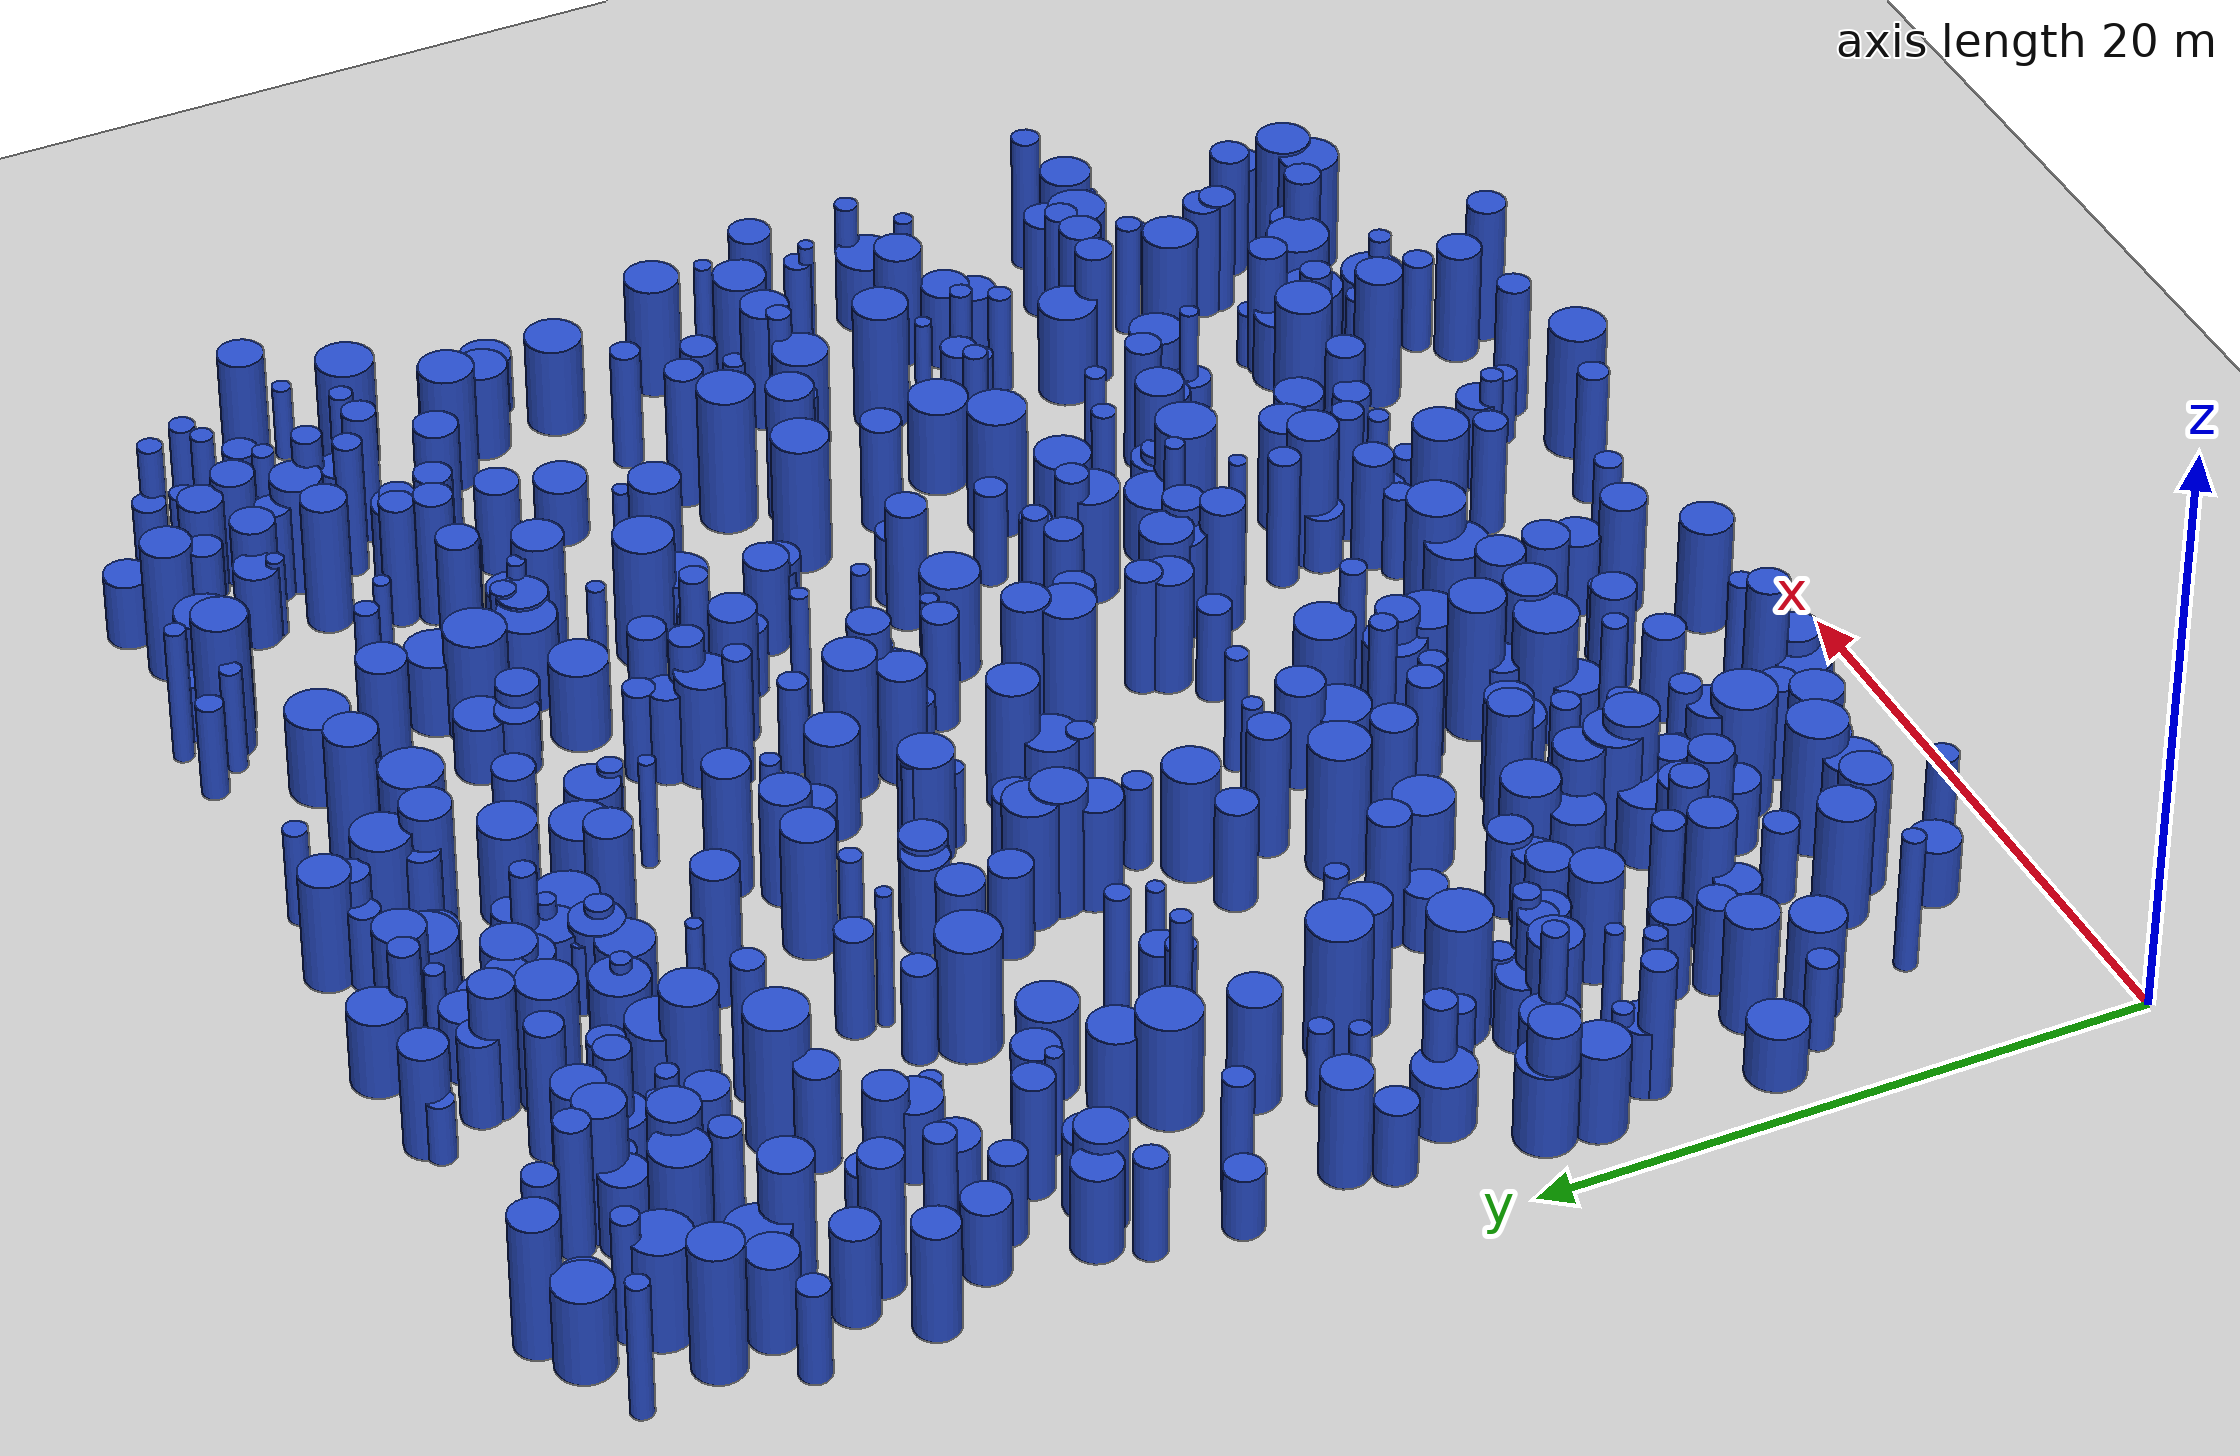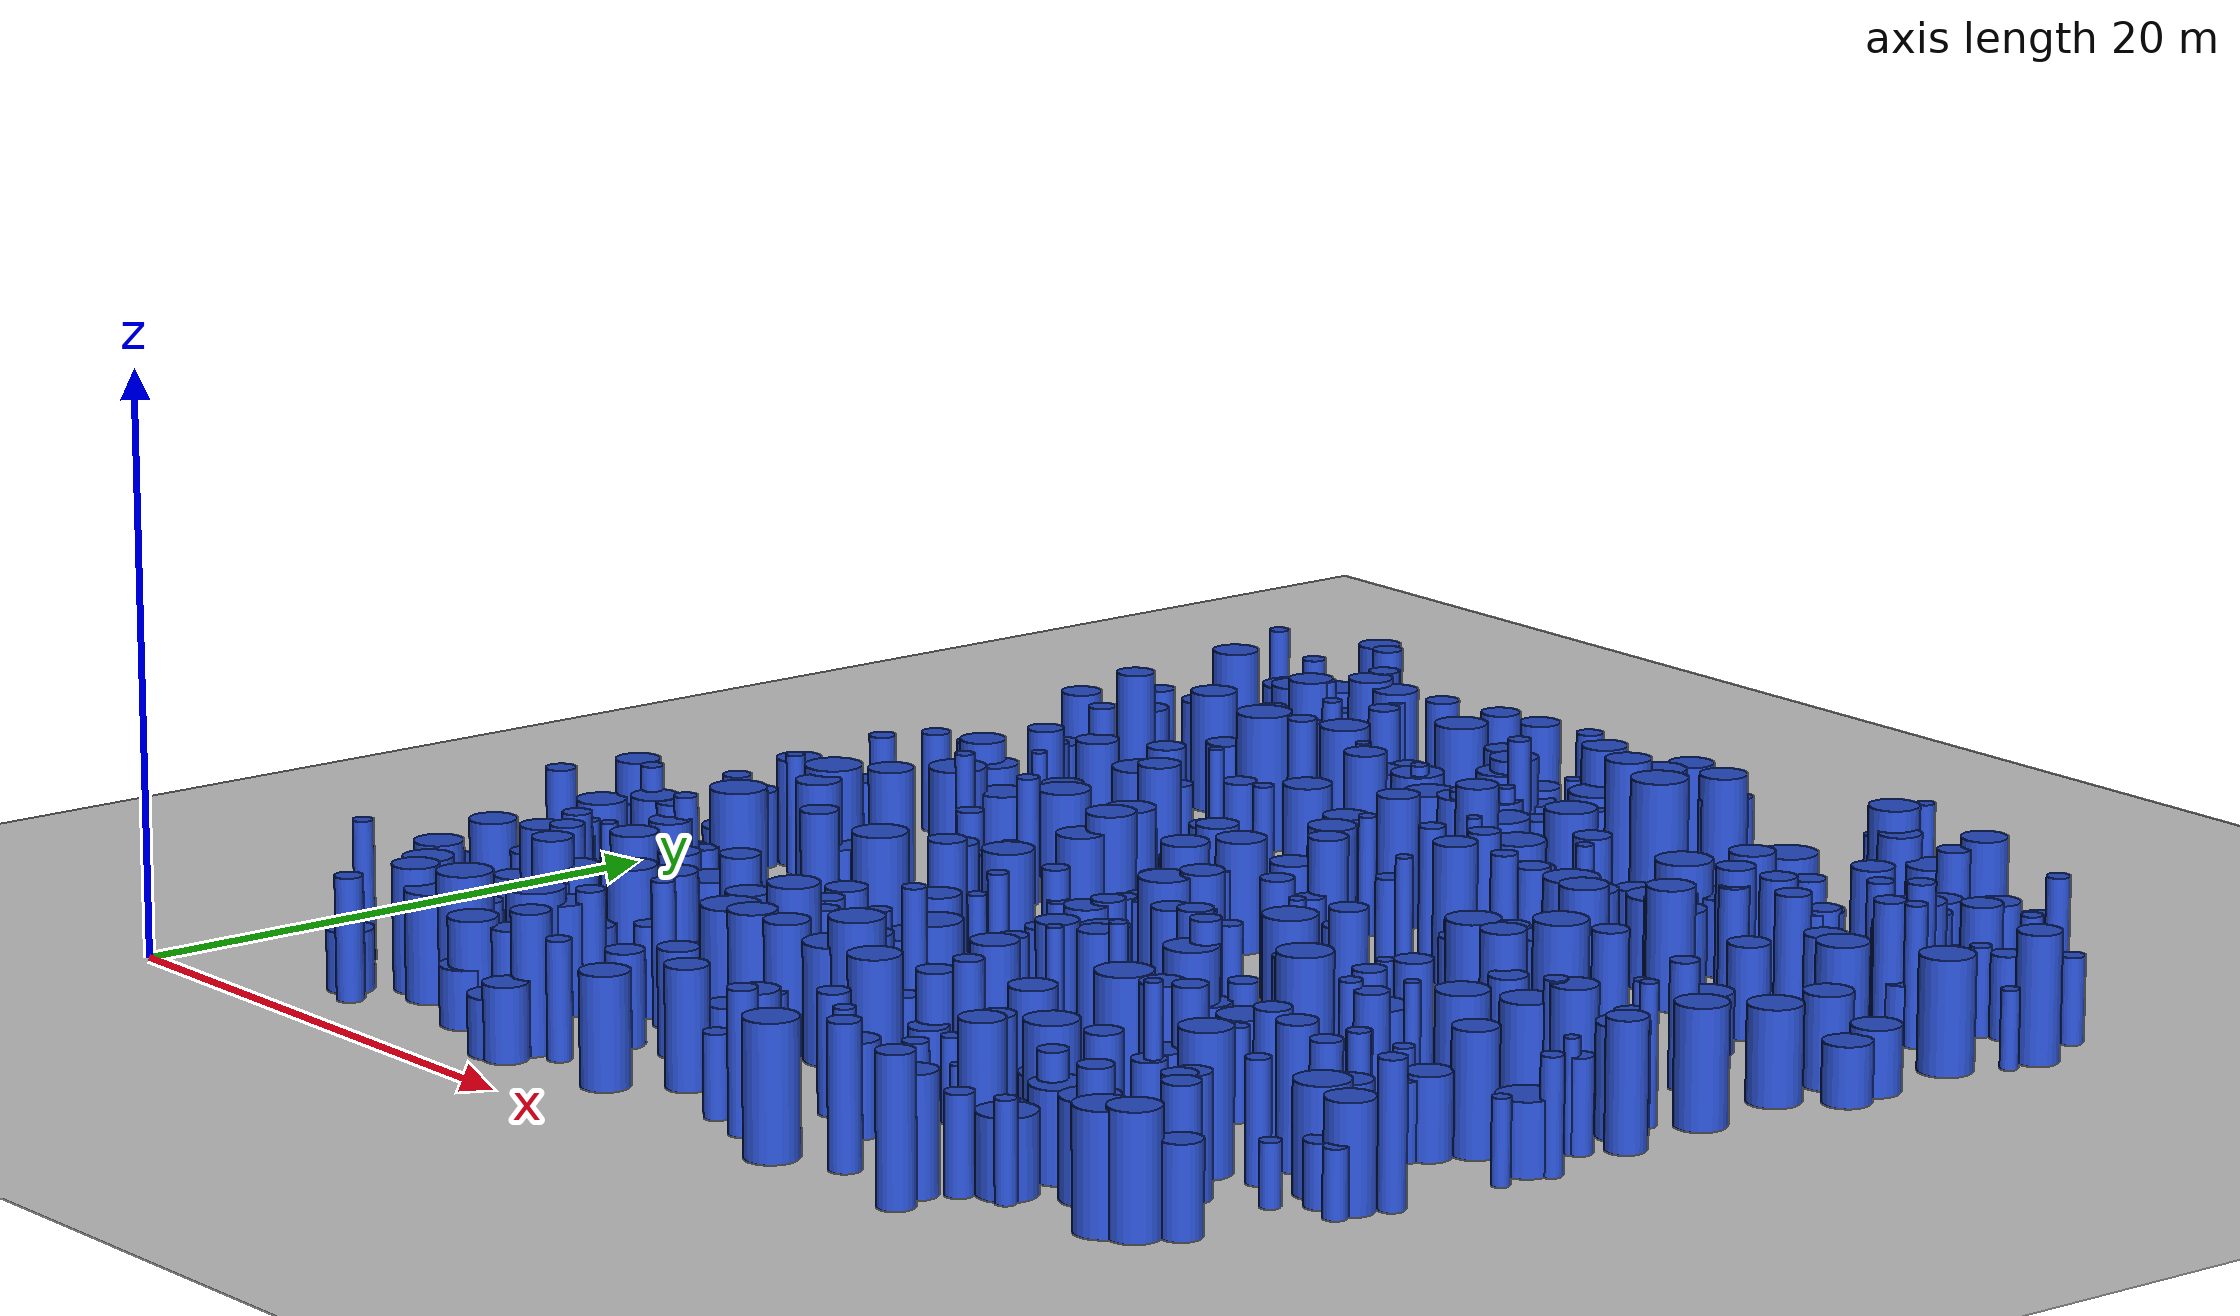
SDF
<sdf version="1.6">
 <world name="default">
  <plugin name="disable_physics" filename="libdisable_physics.so"/>
  <light name="sun" type="directional">
   <pose>0 0 10 0 -0 0</pose>
   <diffuse>0.8 0.8 0.8 1</diffuse>
   <specular>0.1 0.1 0.1 1</specular>
   <attenuation>
    <range>1000</range>
    <constant>0.9</constant>
    <linear>0.01</linear>
    <quadratic>0.001</quadratic>
   </attenuation>
   <direction>-0.5 0.5 -1</direction>
  </light>
  <model name="ground_plane">
   <static>1</static>
   <link name="link">
    <collision name="collision">
     <geometry><plane><normal>0 0 1</normal><size>100 100</size></plane></geometry>
     <surface><friction><ode><mu>100</mu><mu2>50</mu2></ode></friction></surface>
    </collision>
    <visual name="visual">
     <cast_shadows>0</cast_shadows>
     <geometry><plane><normal>0 0 1</normal><size>100 100</size></plane></geometry>
     <material>
      <script><uri>file://media/materials/scripts/gazebo.material</uri><name>Gazebo/Grey</name></script>
     </material>
    </visual>
   </link>
  </model>
  <gravity>0 0 -9.8</gravity>
  <magnetic_field>6e-06 2.3e-05 -4.2e-05</magnetic_field>
  <atmosphere type="adiabatic"/>
  <physics name="default_physics" default="0" type="ode">
   <max_step_size>0.001</max_step_size>
   <real_time_factor>1</real_time_factor>
   <real_time_update_rate>1000</real_time_update_rate>
  </physics>
  <scene><ambient>0.4 0.4 0.4 1</ambient><background>0.7 0.7 0.7 1</background><shadows>1</shadows></scene>
  <spherical_coordinates>
   <surface_model>EARTH_WGS84</surface_model>
   <latitude_deg>0</latitude_deg>
   <longitude_deg>0</longitude_deg>
   <elevation>0</elevation>
   <heading_deg>0</heading_deg>
  </spherical_coordinates>
  <model name="0">
   <static>0</static>
   <link name="link">
    <inertial>
     <mass>2</mass>
     <inertia><ixx>3.17312</ixx><ixy>0</ixy><ixz>0</ixz><iyy>3.17312</iyy><iyz>0</iyz><izz>0.73489</izz></inertia>
    </inertial>
    <collision name="collision">
     <geometry><cylinder><length>4.10293</length><radius>0.857257</radius></cylinder></geometry>
     <surface><contact><collide_without_contact>1</collide_without_contact></contact></surface>
    </collision>
    <visual name="visual">
     <geometry><cylinder><length>4.10293</length><radius>0.857257</radius></cylinder></geometry>
     <material>
      <script><uri>file://media/materials/scripts/gazebo.material</uri><name>Gazebo/Blue</name></script>
     </material>
    </visual>
    <gravity>0</gravity>
   </link>
   <pose>7.58804 6.08459 2.05146 0 -0 0</pose>
  </model>
  <model name="1">
   <static>0</static>
   <link name="link">
    <inertial>
     <mass>2</mass>
     <inertia><ixx>1.7057</ixx><ixy>0</ixy><ixz>0</ixz><iyy>1.7057</iyy><iyz>0</iyz><izz>0.32089</izz></inertia>
    </inertial>
    <collision name="collision">
     <geometry><cylinder><length>3.04492</length><radius>0.566472</radius></cylinder></geometry>
     <surface><contact><collide_without_contact>1</collide_without_contact></contact></surface>
    </collision>
    <visual name="visual">
     <geometry><cylinder><length>3.04492</length><radius>0.566472</radius></cylinder></geometry>
     <material>
      <script><uri>file://media/materials/scripts/gazebo.material</uri><name>Gazebo/Blue</name></script>
     </material>
    </visual>
    <gravity>0</gravity>
   </link>
   <pose>5.05368 34.1911 1.52246 0 -0 0</pose>
  </model>
  <model name="2">
   <static>0</static>
   <link name="link">
    <inertial>
     <mass>2</mass>
     <inertia><ixx>2.62741</ixx><ixy>0</ixy><ixz>0</ixz><iyy>2.62741</iyy><iyz>0</iyz><izz>0.536153</izz></inertia>
    </inertial>
    <collision name="collision">
     <geometry><cylinder><length>3.76245</length><radius>0.732225</radius></cylinder></geometry>
     <surface><contact><collide_without_contact>1</collide_without_contact></contact></surface>
    </collision>
    <visual name="visual">
     <geometry><cylinder><length>3.76245</length><radius>0.732225</radius></cylinder></geometry>
     <material>
      <script><uri>file://media/materials/scripts/gazebo.material</uri><name>Gazebo/Blue</name></script>
     </material>
    </visual>
    <gravity>0</gravity>
   </link>
   <pose>15.603 47.5677 1.88122 0 -0 0</pose>
  </model>
  <model name="3">
   <static>0</static>
   <link name="link">
    <inertial>
     <mass>2</mass>
     <inertia>
      <ixx>1.36545</ixx>
      <ixy>0</ixy>
      <ixz>0</ixz>
      <iyy>1.36545</iyy>
      <iyz>0</iyz>
      <izz>0.0913502</izz>
     </inertia>
    </inertial>
    <collision name="collision">
     <geometry><cylinder><length>2.81401</length><radius>0.302242</radius></cylinder></geometry>
     <surface><contact><collide_without_contact>1</collide_without_contact></contact></surface>
    </collision>
    <visual name="visual">
     <geometry><cylinder><length>2.81401</length><radius>0.302242</radius></cylinder></geometry>
     <material>
      <script><uri>file://media/materials/scripts/gazebo.material</uri><name>Gazebo/Blue</name></script>
     </material>
    </visual>
    <gravity>0</gravity>
   </link>
   <pose>19.5801 45.6834 1.40701 0 -0 0</pose>
  </model>
  <model name="4">
   <static>0</static>
   <link name="link">
    <inertial>
     <mass>2</mass>
     <inertia><ixx>1.95961</ixx><ixy>0</ixy><ixz>0</ixz><iyy>1.95961</iyy><iyz>0</iyz><izz>0.982624</izz></inertia>
    </inertial>
    <collision name="collision">
     <geometry><cylinder><length>2.96813</length><radius>0.991274</radius></cylinder></geometry>
     <surface><contact><collide_without_contact>1</collide_without_contact></contact></surface>
    </collision>
    <visual name="visual">
     <geometry><cylinder><length>2.96813</length><radius>0.991274</radius></cylinder></geometry>
     <material>
      <script><uri>file://media/materials/scripts/gazebo.material</uri><name>Gazebo/Blue</name></script>
     </material>
    </visual>
    <gravity>0</gravity>
   </link>
   <pose>14.6645 40.756 1.48407 0 -0 0</pose>
  </model>
  <model name="5">
   <static>0</static>
   <link name="link">
    <inertial>
     <mass>2</mass>
     <inertia><ixx>2.61652</ixx><ixy>0</ixy><ixz>0</ixz><iyy>2.61652</iyy><iyz>0</iyz><izz>0.44531</izz></inertia>
    </inertial>
    <collision name="collision">
     <geometry><cylinder><length>3.78988</length><radius>0.667315</radius></cylinder></geometry>
     <surface><contact><collide_without_contact>1</collide_without_contact></contact></surface>
    </collision>
    <visual name="visual">
     <geometry><cylinder><length>3.78988</length><radius>0.667315</radius></cylinder></geometry>
     <material>
      <script><uri>file://media/materials/scripts/gazebo.material</uri><name>Gazebo/Blue</name></script>
     </material>
    </visual>
    <gravity>0</gravity>
   </link>
   <pose>10.4927 41.0038 1.89494 0 -0 0</pose>
  </model>
  <model name="6">
   <static>0</static>
   <link name="link">
    <inertial>
     <mass>2</mass>
     <inertia><ixx>2.11932</ixx><ixy>0</ixy><ixz>0</ixz><iyy>2.11932</iyy><iyz>0</iyz><izz>0.84148</izz></inertia>
    </inertial>
    <collision name="collision">
     <geometry><cylinder><length>3.19241</length><radius>0.917322</radius></cylinder></geometry>
     <surface><contact><collide_without_contact>1</collide_without_contact></contact></surface>
    </collision>
    <visual name="visual">
     <geometry><cylinder><length>3.19241</length><radius>0.917322</radius></cylinder></geometry>
     <material>
      <script><uri>file://media/materials/scripts/gazebo.material</uri><name>Gazebo/Blue</name></script>
     </material>
    </visual>
    <gravity>0</gravity>
   </link>
   <pose>16.6156 41.1221 1.5962 0 -0 0</pose>
  </model>
  <model name="7">
   <static>0</static>
   <link name="link">
    <inertial>
     <mass>2</mass>
     <inertia>
      <ixx>0.928742</ixx>
      <ixy>0</ixy>
      <ixz>0</ixz>
      <iyy>0.928742</iyy>
      <iyz>0</iyz>
      <izz>0.0804717</izz>
     </inertia>
    </inertial>
    <collision name="collision">
     <geometry><cylinder><length>2.3089</length><radius>0.283675</radius></cylinder></geometry>
     <surface><contact><collide_without_contact>1</collide_without_contact></contact></surface>
    </collision>
    <visual name="visual">
     <geometry><cylinder><length>2.3089</length><radius>0.283675</radius></cylinder></geometry>
     <material>
      <script><uri>file://media/materials/scripts/gazebo.material</uri><name>Gazebo/Blue</name></script>
     </material>
    </visual>
    <gravity>0</gravity>
   </link>
   <pose>38.9814 31.6696 1.15445 0 -0 0</pose>
  </model>
  <model name="8">
   <static>0</static>
   <link name="link">
    <inertial>
     <mass>2</mass>
     <inertia><ixx>3.79155</ixx><ixy>0</ixy><ixz>0</ixz><iyy>3.79155</iyy><iyz>0</iyz><izz>0.640544</izz></inertia>
    </inertial>
    <collision name="collision">
     <geometry><cylinder><length>4.56373</length><radius>0.80034</radius></cylinder></geometry>
     <surface><contact><collide_without_contact>1</collide_without_contact></contact></surface>
    </collision>
    <visual name="visual">
     <geometry><cylinder><length>4.56373</length><radius>0.80034</radius></cylinder></geometry>
     <material>
      <script><uri>file://media/materials/scripts/gazebo.material</uri><name>Gazebo/Blue</name></script>
     </material>
    </visual>
    <gravity>0</gravity>
   </link>
   <pose>11.3326 44.5695 2.28187 0 -0 0</pose>
  </model>
  <model name="9">
   <static>0</static>
   <link name="link">
    <inertial>
     <mass>2</mass>
     <inertia><ixx>1.27297</ixx><ixy>0</ixy><ixz>0</ixz><iyy>1.27297</iyy><iyz>0</iyz><izz>0.516849</izz></inertia>
    </inertial>
    <collision name="collision">
     <geometry><cylinder><length>2.46725</length><radius>0.718922</radius></cylinder></geometry>
     <surface><contact><collide_without_contact>1</collide_without_contact></contact></surface>
    </collision>
    <visual name="visual">
     <geometry><cylinder><length>2.46725</length><radius>0.718922</radius></cylinder></geometry>
     <material>
      <script><uri>file://media/materials/scripts/gazebo.material</uri><name>Gazebo/Blue</name></script>
     </material>
    </visual>
    <gravity>0</gravity>
   </link>
   <pose>36.1886 14.3863 1.23362 0 -0 0</pose>
  </model>
  <model name="10">
   <static>0</static>
   <link name="link">
    <inertial>
     <mass>2</mass>
     <inertia><ixx>1.40992</ixx><ixy>0</ixy><ixz>0</ixz><iyy>1.40992</iyy><iyz>0</iyz><izz>0.197939</izz></inertia>
    </inertial>
    <collision name="collision">
     <geometry><cylinder><length>2.80459</length><radius>0.444903</radius></cylinder></geometry>
     <surface><contact><collide_without_contact>1</collide_without_contact></contact></surface>
    </collision>
    <visual name="visual">
     <geometry><cylinder><length>2.80459</length><radius>0.444903</radius></cylinder></geometry>
     <material>
      <script><uri>file://media/materials/scripts/gazebo.material</uri><name>Gazebo/Blue</name></script>
     </material>
    </visual>
    <gravity>0</gravity>
   </link>
   <pose>26.8185 3.79167 1.40229 0 -0 0</pose>
  </model>
  <model name="11">
   <static>0</static>
   <link name="link">
    <inertial>
     <mass>2</mass>
     <inertia><ixx>1.98008</ixx><ixy>0</ixy><ixz>0</ixz><iyy>1.98008</iyy><iyz>0</iyz><izz>0.982956</izz></inertia>
    </inertial>
    <collision name="collision">
     <geometry><cylinder><length>2.98858</length><radius>0.991441</radius></cylinder></geometry>
     <surface><contact><collide_without_contact>1</collide_without_contact></contact></surface>
    </collision>
    <visual name="visual">
     <geometry><cylinder><length>2.98858</length><radius>0.991441</radius></cylinder></geometry>
     <material>
      <script><uri>file://media/materials/scripts/gazebo.material</uri><name>Gazebo/Blue</name></script>
     </material>
    </visual>
    <gravity>0</gravity>
   </link>
   <pose>32.0029 44.3985 1.49429 0 -0 0</pose>
  </model>
  <model name="12">
   <static>0</static>
   <link name="link">
    <inertial>
     <mass>2</mass>
     <inertia><ixx>4.39104</ixx><ixy>0</ixy><ixz>0</ixz><iyy>4.39104</iyy><iyz>0</iyz><izz>0.677612</izz></inertia>
    </inertial>
    <collision name="collision">
     <geometry><cylinder><length>4.93086</length><radius>0.823172</radius></cylinder></geometry>
     <surface><contact><collide_without_contact>1</collide_without_contact></contact></surface>
    </collision>
    <visual name="visual">
     <geometry><cylinder><length>4.93086</length><radius>0.823172</radius></cylinder></geometry>
     <material>
      <script><uri>file://media/materials/scripts/gazebo.material</uri><name>Gazebo/Blue</name></script>
     </material>
    </visual>
    <gravity>0</gravity>
   </link>
   <pose>28.3847 44.6674 2.46543 0 -0 0</pose>
  </model>
  <model name="13">
   <static>0</static>
   <link name="link">
    <inertial>
     <mass>2</mass>
     <inertia><ixx>1.80797</ixx><ixy>0</ixy><ixz>0</ixz><iyy>1.80797</iyy><iyz>0</iyz><izz>0.69155</izz></inertia>
    </inertial>
    <collision name="collision">
     <geometry><cylinder><length>2.96195</length><radius>0.831595</radius></cylinder></geometry>
     <surface><contact><collide_without_contact>1</collide_without_contact></contact></surface>
    </collision>
    <visual name="visual">
     <geometry><cylinder><length>2.96195</length><radius>0.831595</radius></cylinder></geometry>
     <material>
      <script><uri>file://media/materials/scripts/gazebo.material</uri><name>Gazebo/Blue</name></script>
     </material>
    </visual>
    <gravity>0</gravity>
   </link>
   <pose>35.0335 36.8774 1.48097 0 -0 0</pose>
  </model>
  <model name="14">
   <static>0</static>
   <link name="link">
    <inertial>
     <mass>2</mass>
     <inertia><ixx>2.91047</ixx><ixy>0</ixy><ixz>0</ixz><iyy>2.91047</iyy><iyz>0</iyz><izz>0.499162</izz></inertia>
    </inertial>
    <collision name="collision">
     <geometry><cylinder><length>3.99567</length><radius>0.706514</radius></cylinder></geometry>
     <surface><contact><collide_without_contact>1</collide_without_contact></contact></surface>
    </collision>
    <visual name="visual">
     <geometry><cylinder><length>3.99567</length><radius>0.706514</radius></cylinder></geometry>
     <material>
      <script><uri>file://media/materials/scripts/gazebo.material</uri><name>Gazebo/Blue</name></script>
     </material>
    </visual>
    <gravity>0</gravity>
   </link>
   <pose>37.3368 3.64907 1.99783 0 -0 0</pose>
  </model>
  <model name="15">
   <static>0</static>
   <link name="link">
    <inertial>
     <mass>2</mass>
     <inertia><ixx>2.90388</ixx><ixy>0</ixy><ixz>0</ixz><iyy>2.90388</iyy><iyz>0</iyz><izz>0.578559</izz></inertia>
    </inertial>
    <collision name="collision">
     <geometry><cylinder><length>3.96076</length><radius>0.76063</radius></cylinder></geometry>
     <surface><contact><collide_without_contact>1</collide_without_contact></contact></surface>
    </collision>
    <visual name="visual">
     <geometry><cylinder><length>3.96076</length><radius>0.76063</radius></cylinder></geometry>
     <material>
      <script><uri>file://media/materials/scripts/gazebo.material</uri><name>Gazebo/Blue</name></script>
     </material>
    </visual>
    <gravity>0</gravity>
   </link>
   <pose>25.3755 28.3182 1.98038 0 -0 0</pose>
  </model>
  <model name="16">
   <static>0</static>
   <link name="link">
    <inertial>
     <mass>2</mass>
     <inertia><ixx>1.94796</ixx><ixy>0</ixy><ixz>0</ixz><iyy>1.94796</iyy><iyz>0</iyz><izz>0.38834</izz></inertia>
    </inertial>
    <collision name="collision">
     <geometry><cylinder><length>3.24388</length><radius>0.623169</radius></cylinder></geometry>
     <surface><contact><collide_without_contact>1</collide_without_contact></contact></surface>
    </collision>
    <visual name="visual">
     <geometry><cylinder><length>3.24388</length><radius>0.623169</radius></cylinder></geometry>
     <material>
      <script><uri>file://media/materials/scripts/gazebo.material</uri><name>Gazebo/Blue</name></script>
     </material>
    </visual>
    <gravity>0</gravity>
   </link>
   <pose>28.2373 34.7081 1.62194 0 -0 0</pose>
  </model>
  <model name="17">
   <static>0</static>
   <link name="link">
    <inertial>
     <mass>2</mass>
     <inertia><ixx>1.4202</ixx><ixy>0</ixy><ixz>0</ixz><iyy>1.4202</iyy><iyz>0</iyz><izz>0.970689</izz></inertia>
    </inertial>
    <collision name="collision">
     <geometry><cylinder><length>2.36836</length><radius>0.985235</radius></cylinder></geometry>
     <surface><contact><collide_without_contact>1</collide_without_contact></contact></surface>
    </collision>
    <visual name="visual">
     <geometry><cylinder><length>2.36836</length><radius>0.985235</radius></cylinder></geometry>
     <material>
      <script><uri>file://media/materials/scripts/gazebo.material</uri><name>Gazebo/Blue</name></script>
     </material>
    </visual>
    <gravity>0</gravity>
   </link>
   <pose>19.9852 16.4259 1.18418 0 -0 0</pose>
  </model>
  <model name="18">
   <static>0</static>
   <link name="link">
    <inertial>
     <mass>2</mass>
     <inertia><ixx>1.36588</ixx><ixy>0</ixy><ixz>0</ixz><iyy>1.36588</iyy><iyz>0</iyz><izz>0.264625</izz></inertia>
    </inertial>
    <collision name="collision">
     <geometry><cylinder><length>2.72056</length><radius>0.514417</radius></cylinder></geometry>
     <surface><contact><collide_without_contact>1</collide_without_contact></contact></surface>
    </collision>
    <visual name="visual">
     <geometry><cylinder><length>2.72056</length><radius>0.514417</radius></cylinder></geometry>
     <material>
      <script><uri>file://media/materials/scripts/gazebo.material</uri><name>Gazebo/Blue</name></script>
     </material>
    </visual>
    <gravity>0</gravity>
   </link>
   <pose>28.2068 44.8037 1.36028 0 -0 0</pose>
  </model>
  <model name="19">
   <static>0</static>
   <link name="link">
    <inertial>
     <mass>2</mass>
     <inertia><ixx>1.91883</ixx><ixy>0</ixy><ixz>0</ixz><iyy>1.91883</iyy><iyz>0</iyz><izz>0.790618</izz></inertia>
    </inertial>
    <collision name="collision">
     <geometry><cylinder><length>3.02343</length><radius>0.889167</radius></cylinder></geometry>
     <surface><contact><collide_without_contact>1</collide_without_contact></contact></surface>
    </collision>
    <visual name="visual">
     <geometry><cylinder><length>3.02343</length><radius>0.889167</radius></cylinder></geometry>
     <material>
      <script><uri>file://media/materials/scripts/gazebo.material</uri><name>Gazebo/Blue</name></script>
     </material>
    </visual>
    <gravity>0</gravity>
   </link>
   <pose>16.6325 12.2097 1.51172 0 -0 0</pose>
  </model>
  <model name="20">
   <static>0</static>
   <link name="link">
    <inertial>
     <mass>2</mass>
     <inertia><ixx>2.53516</ixx><ixy>0</ixy><ixz>0</ixz><iyy>2.53516</iyy><iyz>0</iyz><izz>0.131135</izz></inertia>
    </inertial>
    <collision name="collision">
     <geometry><cylinder><length>3.84936</length><radius>0.362126</radius></cylinder></geometry>
     <surface><contact><collide_without_contact>1</collide_without_contact></contact></surface>
    </collision>
    <visual name="visual">
     <geometry><cylinder><length>3.84936</length><radius>0.362126</radius></cylinder></geometry>
     <material>
      <script><uri>file://media/materials/scripts/gazebo.material</uri><name>Gazebo/Blue</name></script>
     </material>
    </visual>
    <gravity>0</gravity>
   </link>
   <pose>45.1067 43.0173 1.92468 0 -0 0</pose>
  </model>
  <model name="21">
   <static>0</static>
   <link name="link">
    <inertial>
     <mass>2</mass>
     <inertia><ixx>4.07181</ixx><ixy>0</ixy><ixz>0</ixz><iyy>4.07181</iyy><iyz>0</iyz><izz>0.543778</izz></inertia>
    </inertial>
    <collision name="collision">
     <geometry><cylinder><length>4.77488</length><radius>0.737413</radius></cylinder></geometry>
     <surface><contact><collide_without_contact>1</collide_without_contact></contact></surface>
    </collision>
    <visual name="visual">
     <geometry><cylinder><length>4.77488</length><radius>0.737413</radius></cylinder></geometry>
     <material>
      <script><uri>file://media/materials/scripts/gazebo.material</uri><name>Gazebo/Blue</name></script>
     </material>
    </visual>
    <gravity>0</gravity>
   </link>
   <pose>29.1484 32.1402 2.38744 0 -0 0</pose>
  </model>
  <model name="22">
   <static>0</static>
   <link name="link">
    <inertial>
     <mass>2</mass>
     <inertia><ixx>1.57924</ixx><ixy>0</ixy><ixz>0</ixz><iyy>1.57924</iyy><iyz>0</iyz><izz>0.59029</izz></inertia>
    </inertial>
    <collision name="collision">
     <geometry><cylinder><length>2.77571</length><radius>0.768303</radius></cylinder></geometry>
     <surface><contact><collide_without_contact>1</collide_without_contact></contact></surface>
    </collision>
    <visual name="visual">
     <geometry><cylinder><length>2.77571</length><radius>0.768303</radius></cylinder></geometry>
     <material>
      <script><uri>file://media/materials/scripts/gazebo.material</uri><name>Gazebo/Blue</name></script>
     </material>
    </visual>
    <gravity>0</gravity>
   </link>
   <pose>43.9591 18.4852 1.38785 0 -0 0</pose>
  </model>
  <model name="23">
   <static>0</static>
   <link name="link">
    <inertial>
     <mass>2</mass>
     <inertia><ixx>2.06721</ixx><ixy>0</ixy><ixz>0</ixz><iyy>2.06721</iyy><iyz>0</iyz><izz>0.898479</izz></inertia>
    </inertial>
    <collision name="collision">
     <geometry><cylinder><length>3.11573</length><radius>0.947881</radius></cylinder></geometry>
     <surface><contact><collide_without_contact>1</collide_without_contact></contact></surface>
    </collision>
    <visual name="visual">
     <geometry><cylinder><length>3.11573</length><radius>0.947881</radius></cylinder></geometry>
     <material>
      <script><uri>file://media/materials/scripts/gazebo.material</uri><name>Gazebo/Blue</name></script>
     </material>
    </visual>
    <gravity>0</gravity>
   </link>
   <pose>38.1808 21.3346 1.55787 0 -0 0</pose>
  </model>
  <model name="24">
   <static>0</static>
   <link name="link">
    <inertial>
     <mass>2</mass>
     <inertia><ixx>1.8584</ixx><ixy>0</ixy><ixz>0</ixz><iyy>1.8584</iyy><iyz>0</iyz><izz>0.121468</izz></inertia>
    </inertial>
    <collision name="collision">
     <geometry><cylinder><length>3.2842</length><radius>0.348523</radius></cylinder></geometry>
     <surface><contact><collide_without_contact>1</collide_without_contact></contact></surface>
    </collision>
    <visual name="visual">
     <geometry><cylinder><length>3.2842</length><radius>0.348523</radius></cylinder></geometry>
     <material>
      <script><uri>file://media/materials/scripts/gazebo.material</uri><name>Gazebo/Blue</name></script>
     </material>
    </visual>
    <gravity>0</gravity>
   </link>
   <pose>27.3393 18.4181 1.6421 0 -0 0</pose>
  </model>
  <model name="25">
   <static>0</static>
   <link name="link">
    <inertial>
     <mass>2</mass>
     <inertia><ixx>1.19215</ixx><ixy>0</ixy><ixz>0</ixz><iyy>1.19215</iyy><iyz>0</iyz><izz>0.566845</izz></inertia>
    </inertial>
    <collision name="collision">
     <geometry><cylinder><length>2.33503</length><radius>0.752891</radius></cylinder></geometry>
     <surface><contact><collide_without_contact>1</collide_without_contact></contact></surface>
    </collision>
    <visual name="visual">
     <geometry><cylinder><length>2.33503</length><radius>0.752891</radius></cylinder></geometry>
     <material>
      <script><uri>file://media/materials/scripts/gazebo.material</uri><name>Gazebo/Blue</name></script>
     </material>
    </visual>
    <gravity>0</gravity>
   </link>
   <pose>18.1857 45.3246 1.16752 0 -0 0</pose>
  </model>
  <model name="26">
   <static>0</static>
   <link name="link">
    <inertial>
     <mass>2</mass>
     <inertia><ixx>1.12247</ixx><ixy>0</ixy><ixz>0</ixz><iyy>1.12247</iyy><iyz>0</iyz><izz>0.817696</izz></inertia>
    </inertial>
    <collision name="collision">
     <geometry><cylinder><length>2.06923</length><radius>0.904265</radius></cylinder></geometry>
     <surface><contact><collide_without_contact>1</collide_without_contact></contact></surface>
    </collision>
    <visual name="visual">
     <geometry><cylinder><length>2.06923</length><radius>0.904265</radius></cylinder></geometry>
     <material>
      <script><uri>file://media/materials/scripts/gazebo.material</uri><name>Gazebo/Blue</name></script>
     </material>
    </visual>
    <gravity>0</gravity>
   </link>
   <pose>18.7542 44.3924 1.03462 0 -0 0</pose>
  </model>
  <model name="27">
   <static>0</static>
   <link name="link">
    <inertial>
     <mass>2</mass>
     <inertia><ixx>2.96729</ixx><ixy>0</ixy><ixz>0</ixz><iyy>2.96729</iyy><iyz>0</iyz><izz>0.127909</izz></inertia>
    </inertial>
    <collision name="collision">
     <geometry><cylinder><length>4.17373</length><radius>0.357643</radius></cylinder></geometry>
     <surface><contact><collide_without_contact>1</collide_without_contact></contact></surface>
    </collision>
    <visual name="visual">
     <geometry><cylinder><length>4.17373</length><radius>0.357643</radius></cylinder></geometry>
     <material>
      <script><uri>file://media/materials/scripts/gazebo.material</uri><name>Gazebo/Blue</name></script>
     </material>
    </visual>
    <gravity>0</gravity>
   </link>
   <pose>17.6873 33.3868 2.08686 0 -0 0</pose>
  </model>
  <model name="28">
   <static>0</static>
   <link name="link">
    <inertial>
     <mass>2</mass>
     <inertia><ixx>1.61305</ixx><ixy>0</ixy><ixz>0</ixz><iyy>1.61305</iyy><iyz>0</iyz><izz>0.463081</izz></inertia>
    </inertial>
    <collision name="collision">
     <geometry><cylinder><length>2.87908</length><radius>0.680501</radius></cylinder></geometry>
     <surface><contact><collide_without_contact>1</collide_without_contact></contact></surface>
    </collision>
    <visual name="visual">
     <geometry><cylinder><length>2.87908</length><radius>0.680501</radius></cylinder></geometry>
     <material>
      <script><uri>file://media/materials/scripts/gazebo.material</uri><name>Gazebo/Blue</name></script>
     </material>
    </visual>
    <gravity>0</gravity>
   </link>
   <pose>12.0274 14.794 1.43954 0 -0 0</pose>
  </model>
  <model name="29">
   <static>0</static>
   <link name="link">
    <inertial>
     <mass>2</mass>
     <inertia><ixx>1.64089</ixx><ixy>0</ixy><ixz>0</ixz><iyy>1.64089</iyy><iyz>0</iyz><izz>0.902527</izz></inertia>
    </inertial>
    <collision name="collision">
     <geometry><cylinder><length>2.67166</length><radius>0.950014</radius></cylinder></geometry>
     <surface><contact><collide_without_contact>1</collide_without_contact></contact></surface>
    </collision>
    <visual name="visual">
     <geometry><cylinder><length>2.67166</length><radius>0.950014</radius></cylinder></geometry>
     <material>
      <script><uri>file://media/materials/scripts/gazebo.material</uri><name>Gazebo/Blue</name></script>
     </material>
    </visual>
    <gravity>0</gravity>
   </link>
   <pose>24.1929 39.1758 1.33583 0 -0 0</pose>
  </model>
  <model name="30">
   <static>0</static>
   <link name="link">
    <inertial>
     <mass>2</mass>
     <inertia><ixx>2.57065</ixx><ixy>0</ixy><ixz>0</ixz><iyy>2.57065</iyy><iyz>0</iyz><izz>0.140555</izz></inertia>
    </inertial>
    <collision name="collision">
     <geometry><cylinder><length>3.87327</length><radius>0.374907</radius></cylinder></geometry>
     <surface><contact><collide_without_contact>1</collide_without_contact></contact></surface>
    </collision>
    <visual name="visual">
     <geometry><cylinder><length>3.87327</length><radius>0.374907</radius></cylinder></geometry>
     <material>
      <script><uri>file://media/materials/scripts/gazebo.material</uri><name>Gazebo/Blue</name></script>
     </material>
    </visual>
    <gravity>0</gravity>
   </link>
   <pose>47.8314 20.152 1.93664 0 -0 0</pose>
  </model>
  <model name="31">
   <static>0</static>
   <link name="link">
    <inertial>
     <mass>2</mass>
     <inertia><ixx>1.24573</ixx><ixy>0</ixy><ixz>0</ixz><iyy>1.24573</iyy><iyz>0</iyz><izz>0.741657</izz></inertia>
    </inertial>
    <collision name="collision">
     <geometry><cylinder><length>2.29115</length><radius>0.861195</radius></cylinder></geometry>
     <surface><contact><collide_without_contact>1</collide_without_contact></contact></surface>
    </collision>
    <visual name="visual">
     <geometry><cylinder><length>2.29115</length><radius>0.861195</radius></cylinder></geometry>
     <material>
      <script><uri>file://media/materials/scripts/gazebo.material</uri><name>Gazebo/Blue</name></script>
     </material>
    </visual>
    <gravity>0</gravity>
   </link>
   <pose>26.1555 38.0122 1.14558 0 -0 0</pose>
  </model>
  <model name="32">
   <static>0</static>
   <link name="link">
    <inertial>
     <mass>2</mass>
     <inertia><ixx>3.9654</ixx><ixy>0</ixy><ixz>0</ixz><iyy>3.9654</iyy><iyz>0</iyz><izz>0.125912</izz></inertia>
    </inertial>
    <collision name="collision">
     <geometry><cylinder><length>4.83887</length><radius>0.354841</radius></cylinder></geometry>
     <surface><contact><collide_without_contact>1</collide_without_contact></contact></surface>
    </collision>
    <visual name="visual">
     <geometry><cylinder><length>4.83887</length><radius>0.354841</radius></cylinder></geometry>
     <material>
      <script><uri>file://media/materials/scripts/gazebo.material</uri><name>Gazebo/Blue</name></script>
     </material>
    </visual>
    <gravity>0</gravity>
   </link>
   <pose>4.66651 5.49479 2.41944 0 -0 0</pose>
  </model>
  <model name="33">
   <static>0</static>
   <link name="link">
    <inertial>
     <mass>2</mass>
     <inertia><ixx>3.30687</ixx><ixy>0</ixy><ixz>0</ixz><iyy>3.30687</iyy><iyz>0</iyz><izz>0.069358</izz></inertia>
    </inertial>
    <collision name="collision">
     <geometry><cylinder><length>4.43093</length><radius>0.263359</radius></cylinder></geometry>
     <surface><contact><collide_without_contact>1</collide_without_contact></contact></surface>
    </collision>
    <visual name="visual">
     <geometry><cylinder><length>4.43093</length><radius>0.263359</radius></cylinder></geometry>
     <material>
      <script><uri>file://media/materials/scripts/gazebo.material</uri><name>Gazebo/Blue</name></script>
     </material>
    </visual>
    <gravity>0</gravity>
   </link>
   <pose>40.3358 20.8522 2.21546 0 -0 0</pose>
  </model>
  <model name="34">
   <static>0</static>
   <link name="link">
    <inertial>
     <mass>2</mass>
     <inertia><ixx>3.75987</ixx><ixy>0</ixy><ixz>0</ixz><iyy>3.75987</iyy><iyz>0</iyz><izz>0.248556</izz></inertia>
    </inertial>
    <collision name="collision">
     <geometry><cylinder><length>4.6705</length><radius>0.498554</radius></cylinder></geometry>
     <surface><contact><collide_without_contact>1</collide_without_contact></contact></surface>
    </collision>
    <visual name="visual">
     <geometry><cylinder><length>4.6705</length><radius>0.498554</radius></cylinder></geometry>
     <material>
      <script><uri>file://media/materials/scripts/gazebo.material</uri><name>Gazebo/Blue</name></script>
     </material>
    </visual>
    <gravity>0</gravity>
   </link>
   <pose>30.2781 11.09 2.33525 0 -0 0</pose>
  </model>
  <model name="35">
   <static>0</static>
   <link name="link">
    <inertial>
     <mass>2</mass>
     <inertia><ixx>2.36887</ixx><ixy>0</ixy><ixz>0</ixz><iyy>2.36887</iyy><iyz>0</iyz><izz>0.828005</izz></inertia>
    </inertial>
    <collision name="collision">
     <geometry><cylinder><length>3.42479</length><radius>0.909948</radius></cylinder></geometry>
     <surface><contact><collide_without_contact>1</collide_without_contact></contact></surface>
    </collision>
    <visual name="visual">
     <geometry><cylinder><length>3.42479</length><radius>0.909948</radius></cylinder></geometry>
     <material>
      <script><uri>file://media/materials/scripts/gazebo.material</uri><name>Gazebo/Blue</name></script>
     </material>
    </visual>
    <gravity>0</gravity>
   </link>
   <pose>37.3259 45.9655 1.71239 0 -0 0</pose>
  </model>
  <model name="36">
   <static>0</static>
   <link name="link">
    <inertial>
     <mass>2</mass>
     <inertia><ixx>1.9741</ixx><ixy>0</ixy><ixz>0</ixz><iyy>1.9741</iyy><iyz>0</iyz><izz>0.180988</izz></inertia>
    </inertial>
    <collision name="collision">
     <geometry><cylinder><length>3.36179</length><radius>0.425426</radius></cylinder></geometry>
     <surface><contact><collide_without_contact>1</collide_without_contact></contact></surface>
    </collision>
    <visual name="visual">
     <geometry><cylinder><length>3.36179</length><radius>0.425426</radius></cylinder></geometry>
     <material>
      <script><uri>file://media/materials/scripts/gazebo.material</uri><name>Gazebo/Blue</name></script>
     </material>
    </visual>
    <gravity>0</gravity>
   </link>
   <pose>33.1796 47.3533 1.6809 0 -0 0</pose>
  </model>
  <model name="37">
   <static>0</static>
   <link name="link">
    <inertial>
     <mass>2</mass>
     <inertia><ixx>1.40064</ixx><ixy>0</ixy><ixz>0</ixz><iyy>1.40064</iyy><iyz>0</iyz><izz>0.715011</izz></inertia>
    </inertial>
    <collision name="collision">
     <geometry><cylinder><length>2.50176</length><radius>0.845583</radius></cylinder></geometry>
     <surface><contact><collide_without_contact>1</collide_without_contact></contact></surface>
    </collision>
    <visual name="visual">
     <geometry><cylinder><length>2.50176</length><radius>0.845583</radius></cylinder></geometry>
     <material>
      <script><uri>file://media/materials/scripts/gazebo.material</uri><name>Gazebo/Blue</name></script>
     </material>
    </visual>
    <gravity>0</gravity>
   </link>
   <pose>38.4172 9.37247 1.25088 0 -0 0</pose>
  </model>
  <model name="38">
   <static>0</static>
   <link name="link">
    <inertial>
     <mass>2</mass>
     <inertia><ixx>4.19414</ixx><ixy>0</ixy><ixz>0</ixz><iyy>4.19414</iyy><iyz>0</iyz><izz>0.44377</izz></inertia>
    </inertial>
    <collision name="collision">
     <geometry><cylinder><length>4.88196</length><radius>0.66616</radius></cylinder></geometry>
     <surface><contact><collide_without_contact>1</collide_without_contact></contact></surface>
    </collision>
    <visual name="visual">
     <geometry><cylinder><length>4.88196</length><radius>0.66616</radius></cylinder></geometry>
     <material>
      <script><uri>file://media/materials/scripts/gazebo.material</uri><name>Gazebo/Blue</name></script>
     </material>
    </visual>
    <gravity>0</gravity>
   </link>
   <pose>4.65444 38.2486 2.44098 0 -0 0</pose>
  </model>
  <model name="39">
   <static>0</static>
   <link name="link">
    <inertial>
     <mass>2</mass>
     <inertia><ixx>1.84137</ixx><ixy>0</ixy><ixz>0</ixz><iyy>1.84137</iyy><iyz>0</iyz><izz>0.459908</izz></inertia>
    </inertial>
    <collision name="collision">
     <geometry><cylinder><length>3.10942</length><radius>0.678165</radius></cylinder></geometry>
     <surface><contact><collide_without_contact>1</collide_without_contact></contact></surface>
    </collision>
    <visual name="visual">
     <geometry><cylinder><length>3.10942</length><radius>0.678165</radius></cylinder></geometry>
     <material>
      <script><uri>file://media/materials/scripts/gazebo.material</uri><name>Gazebo/Blue</name></script>
     </material>
    </visual>
    <gravity>0</gravity>
   </link>
   <pose>16.5405 28.8099 1.55471 0 -0 0</pose>
  </model>
  <model name="40">
   <static>0</static>
   <link name="link">
    <inertial>
     <mass>2</mass>
     <inertia><ixx>3.12245</ixx><ixy>0</ixy><ixz>0</ixz><iyy>3.12245</iyy><iyz>0</iyz><izz>0.553682</izz></inertia>
    </inertial>
    <collision name="collision">
     <geometry><cylinder><length>4.13202</length><radius>0.744098</radius></cylinder></geometry>
     <surface><contact><collide_without_contact>1</collide_without_contact></contact></surface>
    </collision>
    <visual name="visual">
     <geometry><cylinder><length>4.13202</length><radius>0.744098</radius></cylinder></geometry>
     <material>
      <script><uri>file://media/materials/scripts/gazebo.material</uri><name>Gazebo/Blue</name></script>
     </material>
    </visual>
    <gravity>0</gravity>
   </link>
   <pose>25.9653 19.207 2.06601 0 -0 0</pose>
  </model>
  <model name="41">
   <static>0</static>
   <link name="link">
    <inertial>
     <mass>2</mass>
     <inertia><ixx>3.05764</ixx><ixy>0</ixy><ixz>0</ixz><iyy>3.05764</iyy><iyz>0</iyz><izz>0.702112</izz></inertia>
    </inertial>
    <collision name="collision">
     <geometry><cylinder><length>4.02983</length><radius>0.837921</radius></cylinder></geometry>
     <surface><contact><collide_without_contact>1</collide_without_contact></contact></surface>
    </collision>
    <visual name="visual">
     <geometry><cylinder><length>4.02983</length><radius>0.837921</radius></cylinder></geometry>
     <material>
      <script><uri>file://media/materials/scripts/gazebo.material</uri><name>Gazebo/Blue</name></script>
     </material>
    </visual>
    <gravity>0</gravity>
   </link>
   <pose>28.0717 18.3011 2.01491 0 -0 0</pose>
  </model>
  <model name="42">
   <static>0</static>
   <link name="link">
    <inertial>
     <mass>2</mass>
     <inertia><ixx>1.13765</ixx><ixy>0</ixy><ixz>0</ixz><iyy>1.13765</iyy><iyz>0</iyz><izz>0.440877</izz></inertia>
    </inertial>
    <collision name="collision">
     <geometry><cylinder><length>2.3459</length><radius>0.663986</radius></cylinder></geometry>
     <surface><contact><collide_without_contact>1</collide_without_contact></contact></surface>
    </collision>
    <visual name="visual">
     <geometry><cylinder><length>2.3459</length><radius>0.663986</radius></cylinder></geometry>
     <material>
      <script><uri>file://media/materials/scripts/gazebo.material</uri><name>Gazebo/Blue</name></script>
     </material>
    </visual>
    <gravity>0</gravity>
   </link>
   <pose>29.1505 10.3498 1.17295 0 -0 0</pose>
  </model>
  <model name="43">
   <static>0</static>
   <link name="link">
    <inertial>
     <mass>2</mass>
     <inertia><ixx>1.8726</ixx><ixy>0</ixy><ixz>0</ixz><iyy>1.8726</iyy><iyz>0</iyz><izz>0.124585</izz></inertia>
    </inertial>
    <collision name="collision">
     <geometry><cylinder><length>3.29574</length><radius>0.352966</radius></cylinder></geometry>
     <surface><contact><collide_without_contact>1</collide_without_contact></contact></surface>
    </collision>
    <visual name="visual">
     <geometry><cylinder><length>3.29574</length><radius>0.352966</radius></cylinder></geometry>
     <material>
      <script><uri>file://media/materials/scripts/gazebo.material</uri><name>Gazebo/Blue</name></script>
     </material>
    </visual>
    <gravity>0</gravity>
   </link>
   <pose>42.7488 18.4765 1.64787 0 -0 0</pose>
  </model>
  <model name="44">
   <static>0</static>
   <link name="link">
    <inertial>
     <mass>2</mass>
     <inertia><ixx>1.7448</ixx><ixy>0</ixy><ixz>0</ixz><iyy>1.7448</iyy><iyz>0</iyz><izz>0.25816</izz></inertia>
    </inertial>
    <collision name="collision">
     <geometry><cylinder><length>3.11357</length><radius>0.508094</radius></cylinder></geometry>
     <surface><contact><collide_without_contact>1</collide_without_contact></contact></surface>
    </collision>
    <visual name="visual">
     <geometry><cylinder><length>3.11357</length><radius>0.508094</radius></cylinder></geometry>
     <material>
      <script><uri>file://media/materials/scripts/gazebo.material</uri><name>Gazebo/Blue</name></script>
     </material>
    </visual>
    <gravity>0</gravity>
   </link>
   <pose>26.7685 27.9284 1.55679 0 -0 0</pose>
  </model>
  <model name="45">
   <static>0</static>
   <link name="link">
    <inertial>
     <mass>2</mass>
     <inertia><ixx>1.28619</ixx><ixy>0</ixy><ixz>0</ixz><iyy>1.28619</iyy><iyz>0</iyz><izz>0.628767</izz></inertia>
    </inertial>
    <collision name="collision">
     <geometry><cylinder><length>2.41471</length><radius>0.792948</radius></cylinder></geometry>
     <surface><contact><collide_without_contact>1</collide_without_contact></contact></surface>
    </collision>
    <visual name="visual">
     <geometry><cylinder><length>2.41471</length><radius>0.792948</radius></cylinder></geometry>
     <material>
      <script><uri>file://media/materials/scripts/gazebo.material</uri><name>Gazebo/Blue</name></script>
     </material>
    </visual>
    <gravity>0</gravity>
   </link>
   <pose>6.54895 17.1856 1.20735 0 -0 0</pose>
  </model>
  <model name="46">
   <static>0</static>
   <link name="link">
    <inertial>
     <mass>2</mass>
     <inertia><ixx>1.39822</ixx><ixy>0</ixy><ixz>0</ixz><iyy>1.39822</iyy><iyz>0</iyz><izz>0.114651</izz></inertia>
    </inertial>
    <collision name="collision">
     <geometry><cylinder><length>2.83643</length><radius>0.338602</radius></cylinder></geometry>
     <surface><contact><collide_without_contact>1</collide_without_contact></contact></surface>
    </collision>
    <visual name="visual">
     <geometry><cylinder><length>2.83643</length><radius>0.338602</radius></cylinder></geometry>
     <material>
      <script><uri>file://media/materials/scripts/gazebo.material</uri><name>Gazebo/Blue</name></script>
     </material>
    </visual>
    <gravity>0</gravity>
   </link>
   <pose>31.8364 9.20339 1.41822 0 -0 0</pose>
  </model>
  <model name="47">
   <static>0</static>
   <link name="link">
    <inertial>
     <mass>2</mass>
     <inertia><ixx>3.0805</ixx><ixy>0</ixy><ixz>0</ixz><iyy>3.0805</iyy><iyz>0</iyz><izz>0.647324</izz></inertia>
    </inertial>
    <collision name="collision">
     <geometry><cylinder><length>4.06707</length><radius>0.804564</radius></cylinder></geometry>
     <surface><contact><collide_without_contact>1</collide_without_contact></contact></surface>
    </collision>
    <visual name="visual">
     <geometry><cylinder><length>4.06707</length><radius>0.804564</radius></cylinder></geometry>
     <material>
      <script><uri>file://media/materials/scripts/gazebo.material</uri><name>Gazebo/Blue</name></script>
     </material>
    </visual>
    <gravity>0</gravity>
   </link>
   <pose>20.3861 46.3769 2.03353 0 -0 0</pose>
  </model>
  <model name="48">
   <static>0</static>
   <link name="link">
    <inertial>
     <mass>2</mass>
     <inertia><ixx>1.82802</ixx><ixy>0</ixy><ixz>0</ixz><iyy>1.82802</iyy><iyz>0</iyz><izz>0.254102</izz></inertia>
    </inertial>
    <collision name="collision">
     <geometry><cylinder><length>3.19465</length><radius>0.504085</radius></cylinder></geometry>
     <surface><contact><collide_without_contact>1</collide_without_contact></contact></surface>
    </collision>
    <visual name="visual">
     <geometry><cylinder><length>3.19465</length><radius>0.504085</radius></cylinder></geometry>
     <material>
      <script><uri>file://media/materials/scripts/gazebo.material</uri><name>Gazebo/Blue</name></script>
     </material>
    </visual>
    <gravity>0</gravity>
   </link>
   <pose>5.44202 44.3514 1.59733 0 -0 0</pose>
  </model>
  <model name="49">
   <static>0</static>
   <link name="link">
    <inertial>
     <mass>2</mass>
     <inertia><ixx>1.03869</ixx><ixy>0</ixy><ixz>0</ixz><iyy>1.03869</iyy><iyz>0</iyz><izz>0.208201</izz></inertia>
    </inertial>
    <collision name="collision">
     <geometry><cylinder><length>2.36803</length><radius>0.45629</radius></cylinder></geometry>
     <surface><contact><collide_without_contact>1</collide_without_contact></contact></surface>
    </collision>
    <visual name="visual">
     <geometry><cylinder><length>2.36803</length><radius>0.45629</radius></cylinder></geometry>
     <material>
      <script><uri>file://media/materials/scripts/gazebo.material</uri><name>Gazebo/Blue</name></script>
     </material>
    </visual>
    <gravity>0</gravity>
   </link>
   <pose>12.9469 31.5137 1.18401 0 -0 0</pose>
  </model>
  <model name="50">
   <static>0</static>
   <link name="link">
    <inertial>
     <mass>2</mass>
     <inertia><ixx>3.72286</ixx><ixy>0</ixy><ixz>0</ixz><iyy>3.72286</iyy><iyz>0</iyz><izz>0.752278</izz></inertia>
    </inertial>
    <collision name="collision">
     <geometry><cylinder><length>4.4811</length><radius>0.86734</radius></cylinder></geometry>
     <surface><contact><collide_without_contact>1</collide_without_contact></contact></surface>
    </collision>
    <visual name="visual">
     <geometry><cylinder><length>4.4811</length><radius>0.86734</radius></cylinder></geometry>
     <material>
      <script><uri>file://media/materials/scripts/gazebo.material</uri><name>Gazebo/Blue</name></script>
     </material>
    </visual>
    <gravity>0</gravity>
   </link>
   <pose>13.9115 40.0974 2.24055 0 -0 0</pose>
  </model>
  <model name="51">
   <static>0</static>
   <link name="link">
    <inertial>
     <mass>2</mass>
     <inertia><ixx>4.04703</ixx><ixy>0</ixy><ixz>0</ixz><iyy>4.04703</iyy><iyz>0</iyz><izz>0.151938</izz></inertia>
    </inertial>
    <collision name="collision">
     <geometry><cylinder><length>4.88122</length><radius>0.389792</radius></cylinder></geometry>
     <surface><contact><collide_without_contact>1</collide_without_contact></contact></surface>
    </collision>
    <visual name="visual">
     <geometry><cylinder><length>4.88122</length><radius>0.389792</radius></cylinder></geometry>
     <material>
      <script><uri>file://media/materials/scripts/gazebo.material</uri><name>Gazebo/Blue</name></script>
     </material>
    </visual>
    <gravity>0</gravity>
   </link>
   <pose>17.2535 8.66033 2.44061 0 -0 0</pose>
  </model>
  <model name="52">
   <static>0</static>
   <link name="link">
    <inertial>
     <mass>2</mass>
     <inertia><ixx>2.45511</ixx><ixy>0</ixy><ixz>0</ixz><iyy>2.45511</iyy><iyz>0</iyz><izz>0.610488</izz></inertia>
    </inertial>
    <collision name="collision">
     <geometry><cylinder><length>3.59154</length><radius>0.781337</radius></cylinder></geometry>
     <surface><contact><collide_without_contact>1</collide_without_contact></contact></surface>
    </collision>
    <visual name="visual">
     <geometry><cylinder><length>3.59154</length><radius>0.781337</radius></cylinder></geometry>
     <material>
      <script><uri>file://media/materials/scripts/gazebo.material</uri><name>Gazebo/Blue</name></script>
     </material>
    </visual>
    <gravity>0</gravity>
   </link>
   <pose>32.7626 42.022 1.79577 0 -0 0</pose>
  </model>
  <model name="53">
   <static>0</static>
   <link name="link">
    <inertial>
     <mass>2</mass>
     <inertia><ixx>1.89191</ixx><ixy>0</ixy><ixz>0</ixz><iyy>1.89191</iyy><iyz>0</iyz><izz>0.1601</izz></inertia>
    </inertial>
    <collision name="collision">
     <geometry><cylinder><length>3.29714</length><radius>0.400125</radius></cylinder></geometry>
     <surface><contact><collide_without_contact>1</collide_without_contact></contact></surface>
    </collision>
    <visual name="visual">
     <geometry><cylinder><length>3.29714</length><radius>0.400125</radius></cylinder></geometry>
     <material>
      <script><uri>file://media/materials/scripts/gazebo.material</uri><name>Gazebo/Blue</name></script>
     </material>
    </visual>
    <gravity>0</gravity>
   </link>
   <pose>34.7148 37.3115 1.64857 0 -0 0</pose>
  </model>
  <model name="54">
   <static>0</static>
   <link name="link">
    <inertial>
     <mass>2</mass>
     <inertia><ixx>1.90004</ixx><ixy>0</ixy><ixz>0</ixz><iyy>1.90004</iyy><iyz>0</iyz><izz>0.889584</izz></inertia>
    </inertial>
    <collision name="collision">
     <geometry><cylinder><length>2.95491</length><radius>0.943178</radius></cylinder></geometry>
     <surface><contact><collide_without_contact>1</collide_without_contact></contact></surface>
    </collision>
    <visual name="visual">
     <geometry><cylinder><length>2.95491</length><radius>0.943178</radius></cylinder></geometry>
     <material>
      <script><uri>file://media/materials/scripts/gazebo.material</uri><name>Gazebo/Blue</name></script>
     </material>
    </visual>
    <gravity>0</gravity>
   </link>
   <pose>2.3369 18.5513 1.47745 0 -0 0</pose>
  </model>
  <model name="55">
   <static>0</static>
   <link name="link">
    <inertial>
     <mass>2</mass>
     <inertia><ixx>2.77636</ixx><ixy>0</ixy><ixz>0</ixz><iyy>2.77636</iyy><iyz>0</iyz><izz>0.243438</izz></inertia>
    </inertial>
    <collision name="collision">
     <geometry><cylinder><length>3.99097</length><radius>0.493394</radius></cylinder></geometry>
     <surface><contact><collide_without_contact>1</collide_without_contact></contact></surface>
    </collision>
    <visual name="visual">
     <geometry><cylinder><length>3.99097</length><radius>0.493394</radius></cylinder></geometry>
     <material>
      <script><uri>file://media/materials/scripts/gazebo.material</uri><name>Gazebo/Blue</name></script>
     </material>
    </visual>
    <gravity>0</gravity>
   </link>
   <pose>4.84616 20.723 1.99548 0 -0 0</pose>
  </model>
  <model name="56">
   <static>0</static>
   <link name="link">
    <inertial>
     <mass>2</mass>
     <inertia><ixx>2.77614</ixx><ixy>0</ixy><ixz>0</ixz><iyy>2.77614</iyy><iyz>0</iyz><izz>0.245795</izz></inertia>
    </inertial>
    <collision name="collision">
     <geometry><cylinder><length>3.98992</length><radius>0.495777</radius></cylinder></geometry>
     <surface><contact><collide_without_contact>1</collide_without_contact></contact></surface>
    </collision>
    <visual name="visual">
     <geometry><cylinder><length>3.98992</length><radius>0.495777</radius></cylinder></geometry>
     <material>
      <script><uri>file://media/materials/scripts/gazebo.material</uri><name>Gazebo/Blue</name></script>
     </material>
    </visual>
    <gravity>0</gravity>
   </link>
   <pose>38.1551 8.28818 1.99496 0 -0 0</pose>
  </model>
  <model name="57">
   <static>0</static>
   <link name="link">
    <inertial>
     <mass>2</mass>
     <inertia><ixx>2.7647</ixx><ixy>0</ixy><ixz>0</ixz><iyy>2.7647</iyy><iyz>0</iyz><izz>0.695099</izz></inertia>
    </inertial>
    <collision name="collision">
     <geometry><cylinder><length>3.80827</length><radius>0.833726</radius></cylinder></geometry>
     <surface><contact><collide_without_contact>1</collide_without_contact></contact></surface>
    </collision>
    <visual name="visual">
     <geometry><cylinder><length>3.80827</length><radius>0.833726</radius></cylinder></geometry>
     <material>
      <script><uri>file://media/materials/scripts/gazebo.material</uri><name>Gazebo/Blue</name></script>
     </material>
    </visual>
    <gravity>0</gravity>
   </link>
   <pose>21.7704 3.10199 1.90413 0 -0 0</pose>
  </model>
  <model name="58">
   <static>0</static>
   <link name="link">
    <inertial>
     <mass>2</mass>
     <inertia><ixx>2.80734</ixx><ixy>0</ixy><ixz>0</ixz><iyy>2.80734</iyy><iyz>0</iyz><izz>0.790535</izz></inertia>
    </inertial>
    <collision name="collision">
     <geometry><cylinder><length>3.80426</length><radius>0.889121</radius></cylinder></geometry>
     <surface><contact><collide_without_contact>1</collide_without_contact></contact></surface>
    </collision>
    <visual name="visual">
     <geometry><cylinder><length>3.80426</length><radius>0.889121</radius></cylinder></geometry>
     <material>
      <script><uri>file://media/materials/scripts/gazebo.material</uri><name>Gazebo/Blue</name></script>
     </material>
    </visual>
    <gravity>0</gravity>
   </link>
   <pose>27.8441 33.6819 1.90213 0 -0 0</pose>
  </model>
  <model name="59">
   <static>0</static>
   <link name="link">
    <inertial>
     <mass>2</mass>
     <inertia><ixx>1.12894</ixx><ixy>0</ixy><ixz>0</ixz><iyy>1.12894</iyy><iyz>0</iyz><izz>0.76588</izz></inertia>
    </inertial>
    <collision name="collision">
     <geometry><cylinder><length>2.11565</length><radius>0.875146</radius></cylinder></geometry>
     <surface><contact><collide_without_contact>1</collide_without_contact></contact></surface>
    </collision>
    <visual name="visual">
     <geometry><cylinder><length>2.11565</length><radius>0.875146</radius></cylinder></geometry>
     <material>
      <script><uri>file://media/materials/scripts/gazebo.material</uri><name>Gazebo/Blue</name></script>
     </material>
    </visual>
    <gravity>0</gravity>
   </link>
   <pose>28.177 43.0977 1.05782 0 -0 0</pose>
  </model>
  <model name="60">
   <static>0</static>
   <link name="link">
    <inertial>
     <mass>2</mass>
     <inertia><ixx>2.52957</ixx><ixy>0</ixy><ixz>0</ixz><iyy>2.52957</iyy><iyz>0</iyz><izz>0.676676</izz></inertia>
    </inertial>
    <collision name="collision">
     <geometry><cylinder><length>3.62593</length><radius>0.822603</radius></cylinder></geometry>
     <surface><contact><collide_without_contact>1</collide_without_contact></contact></surface>
    </collision>
    <visual name="visual">
     <geometry><cylinder><length>3.62593</length><radius>0.822603</radius></cylinder></geometry>
     <material>
      <script><uri>file://media/materials/scripts/gazebo.material</uri><name>Gazebo/Blue</name></script>
     </material>
    </visual>
    <gravity>0</gravity>
   </link>
   <pose>46.8205 12.9395 1.81297 0 -0 0</pose>
  </model>
  <model name="61">
   <static>0</static>
   <link name="link">
    <inertial>
     <mass>2</mass>
     <inertia>
      <ixx>4.01912</ixx>
      <ixy>0</ixy>
      <ixz>0</ixz>
      <iyy>4.01912</iyy>
      <iyz>0</iyz>
      <izz>0.0645632</izz>
     </inertia>
    </inertial>
    <collision name="collision">
     <geometry><cylinder><length>4.89091</length><radius>0.254093</radius></cylinder></geometry>
     <surface><contact><collide_without_contact>1</collide_without_contact></contact></surface>
    </collision>
    <visual name="visual">
     <geometry><cylinder><length>4.89091</length><radius>0.254093</radius></cylinder></geometry>
     <material>
      <script><uri>file://media/materials/scripts/gazebo.material</uri><name>Gazebo/Blue</name></script>
     </material>
    </visual>
    <gravity>0</gravity>
   </link>
   <pose>14.9692 33.5353 2.44546 0 -0 0</pose>
  </model>
  <model name="62">
   <static>0</static>
   <link name="link">
    <inertial>
     <mass>2</mass>
     <inertia><ixx>3.86289</ixx><ixy>0</ixy><ixz>0</ixz><iyy>3.86289</iyy><iyz>0</iyz><izz>0.080667</izz></inertia>
    </inertial>
    <collision name="collision">
     <geometry><cylinder><length>4.78908</length><radius>0.284019</radius></cylinder></geometry>
     <surface><contact><collide_without_contact>1</collide_without_contact></contact></surface>
    </collision>
    <visual name="visual">
     <geometry><cylinder><length>4.78908</length><radius>0.284019</radius></cylinder></geometry>
     <material>
      <script><uri>file://media/materials/scripts/gazebo.material</uri><name>Gazebo/Blue</name></script>
     </material>
    </visual>
    <gravity>0</gravity>
   </link>
   <pose>29.2941 15.3061 2.39454 0 -0 0</pose>
  </model>
  <model name="63">
   <static>0</static>
   <link name="link">
    <inertial>
     <mass>2</mass>
     <inertia><ixx>1.90981</ixx><ixy>0</ixy><ixz>0</ixz><iyy>1.90981</iyy><iyz>0</iyz><izz>0.596313</izz></inertia>
    </inertial>
    <collision name="collision">
     <geometry><cylinder><length>3.10965</length><radius>0.772213</radius></cylinder></geometry>
     <surface><contact><collide_without_contact>1</collide_without_contact></contact></surface>
    </collision>
    <visual name="visual">
     <geometry><cylinder><length>3.10965</length><radius>0.772213</radius></cylinder></geometry>
     <material>
      <script><uri>file://media/materials/scripts/gazebo.material</uri><name>Gazebo/Blue</name></script>
     </material>
    </visual>
    <gravity>0</gravity>
   </link>
   <pose>3.52675 32.1403 1.55483 0 -0 0</pose>
  </model>
  <model name="64">
   <static>0</static>
   <link name="link">
    <inertial>
     <mass>2</mass>
     <inertia><ixx>1.07162</ixx><ixy>0</ixy><ixz>0</ixz><iyy>1.07162</iyy><iyz>0</iyz><izz>0.712238</izz></inertia>
    </inertial>
    <collision name="collision">
     <geometry><cylinder><length>2.07196</length><radius>0.843942</radius></cylinder></geometry>
     <surface><contact><collide_without_contact>1</collide_without_contact></contact></surface>
    </collision>
    <visual name="visual">
     <geometry><cylinder><length>2.07196</length><radius>0.843942</radius></cylinder></geometry>
     <material>
      <script><uri>file://media/materials/scripts/gazebo.material</uri><name>Gazebo/Blue</name></script>
     </material>
    </visual>
    <gravity>0</gravity>
   </link>
   <pose>30.8302 39.6819 1.03598 0 -0 0</pose>
  </model>
  <model name="65">
   <static>0</static>
   <link name="link">
    <inertial>
     <mass>2</mass>
     <inertia><ixx>2.68412</ixx><ixy>0</ixy><ixz>0</ixz><iyy>2.68412</iyy><iyz>0</iyz><izz>0.778534</izz></inertia>
    </inertial>
    <collision name="collision">
     <geometry><cylinder><length>3.71067</length><radius>0.882346</radius></cylinder></geometry>
     <surface><contact><collide_without_contact>1</collide_without_contact></contact></surface>
    </collision>
    <visual name="visual">
     <geometry><cylinder><length>3.71067</length><radius>0.882346</radius></cylinder></geometry>
     <material>
      <script><uri>file://media/materials/scripts/gazebo.material</uri><name>Gazebo/Blue</name></script>
     </material>
    </visual>
    <gravity>0</gravity>
   </link>
   <pose>9.89569 4.60056 1.85534 0 -0 0</pose>
  </model>
  <model name="66">
   <static>0</static>
   <link name="link">
    <inertial>
     <mass>2</mass>
     <inertia><ixx>3.10959</ixx><ixy>0</ixy><ixz>0</ixz><iyy>3.10959</iyy><iyz>0</iyz><izz>0.654406</izz></inertia>
    </inertial>
    <collision name="collision">
     <geometry><cylinder><length>4.08587</length><radius>0.808954</radius></cylinder></geometry>
     <surface><contact><collide_without_contact>1</collide_without_contact></contact></surface>
    </collision>
    <visual name="visual">
     <geometry><cylinder><length>4.08587</length><radius>0.808954</radius></cylinder></geometry>
     <material>
      <script><uri>file://media/materials/scripts/gazebo.material</uri><name>Gazebo/Blue</name></script>
     </material>
    </visual>
    <gravity>0</gravity>
   </link>
   <pose>35.7565 35.7398 2.04293 0 -0 0</pose>
  </model>
  <model name="67">
   <static>0</static>
   <link name="link">
    <inertial>
     <mass>2</mass>
     <inertia><ixx>2.5861</ixx><ixy>0</ixy><ixz>0</ixz><iyy>2.5861</iyy><iyz>0</iyz><izz>0.518654</izz></inertia>
    </inertial>
    <collision name="collision">
     <geometry><cylinder><length>3.7364</length><radius>0.720177</radius></cylinder></geometry>
     <surface><contact><collide_without_contact>1</collide_without_contact></contact></surface>
    </collision>
    <visual name="visual">
     <geometry><cylinder><length>3.7364</length><radius>0.720177</radius></cylinder></geometry>
     <material>
      <script><uri>file://media/materials/scripts/gazebo.material</uri><name>Gazebo/Blue</name></script>
     </material>
    </visual>
    <gravity>0</gravity>
   </link>
   <pose>7.55571 15.9335 1.8682 0 -0 0</pose>
  </model>
  <model name="68">
   <static>0</static>
   <link name="link">
    <inertial>
     <mass>2</mass>
     <inertia><ixx>1.89087</ixx><ixy>0</ixy><ixz>0</ixz><iyy>1.89087</iyy><iyz>0</iyz><izz>0.429731</izz></inertia>
    </inertial>
    <collision name="collision">
     <geometry><cylinder><length>3.17112</length><radius>0.655539</radius></cylinder></geometry>
     <surface><contact><collide_without_contact>1</collide_without_contact></contact></surface>
    </collision>
    <visual name="visual">
     <geometry><cylinder><length>3.17112</length><radius>0.655539</radius></cylinder></geometry>
     <material>
      <script><uri>file://media/materials/scripts/gazebo.material</uri><name>Gazebo/Blue</name></script>
     </material>
    </visual>
    <gravity>0</gravity>
   </link>
   <pose>18.2845 6.37617 1.58556 0 -0 0</pose>
  </model>
  <model name="69">
   <static>0</static>
   <link name="link">
    <inertial>
     <mass>2</mass>
     <inertia><ixx>2.55552</ixx><ixy>0</ixy><ixz>0</ixz><iyy>2.55552</iyy><iyz>0</iyz><izz>0.698081</izz></inertia>
    </inertial>
    <collision name="collision">
     <geometry><cylinder><length>3.63853</length><radius>0.835512</radius></cylinder></geometry>
     <surface><contact><collide_without_contact>1</collide_without_contact></contact></surface>
    </collision>
    <visual name="visual">
     <geometry><cylinder><length>3.63853</length><radius>0.835512</radius></cylinder></geometry>
     <material>
      <script><uri>file://media/materials/scripts/gazebo.material</uri><name>Gazebo/Blue</name></script>
     </material>
    </visual>
    <gravity>0</gravity>
   </link>
   <pose>23.89 31.2537 1.81926 0 -0 0</pose>
  </model>
  <model name="70">
   <static>0</static>
   <link name="link">
    <inertial>
     <mass>2</mass>
     <inertia><ixx>3.78775</ixx><ixy>0</ixy><ixz>0</ixz><iyy>3.78775</iyy><iyz>0</iyz><izz>0.890965</izz></inertia>
    </inertial>
    <collision name="collision">
     <geometry><cylinder><length>4.47813</length><radius>0.943909</radius></cylinder></geometry>
     <surface><contact><collide_without_contact>1</collide_without_contact></contact></surface>
    </collision>
    <visual name="visual">
     <geometry><cylinder><length>4.47813</length><radius>0.943909</radius></cylinder></geometry>
     <material>
      <script><uri>file://media/materials/scripts/gazebo.material</uri><name>Gazebo/Blue</name></script>
     </material>
    </visual>
    <gravity>0</gravity>
   </link>
   <pose>11.0126 5.18411 2.23906 0 -0 0</pose>
  </model>
  <model name="71">
   <static>0</static>
   <link name="link">
    <inertial>
     <mass>2</mass>
     <inertia><ixx>2.80373</ixx><ixy>0</ixy><ixz>0</ixz><iyy>2.80373</iyy><iyz>0</iyz><izz>0.629376</izz></inertia>
    </inertial>
    <collision name="collision">
     <geometry><cylinder><length>3.86449</length><radius>0.793332</radius></cylinder></geometry>
     <surface><contact><collide_without_contact>1</collide_without_contact></contact></surface>
    </collision>
    <visual name="visual">
     <geometry><cylinder><length>3.86449</length><radius>0.793332</radius></cylinder></geometry>
     <material>
      <script><uri>file://media/materials/scripts/gazebo.material</uri><name>Gazebo/Blue</name></script>
     </material>
    </visual>
    <gravity>0</gravity>
   </link>
   <pose>31.6922 12.5394 1.93224 0 -0 0</pose>
  </model>
  <model name="72">
   <static>0</static>
   <link name="link">
    <inertial>
     <mass>2</mass>
     <inertia>
      <ixx>2.14031</ixx>
      <ixy>0</ixy>
      <ixz>0</ixz>
      <iyy>2.14031</iyy>
      <iyz>0</iyz>
      <izz>0.0819198</izz>
     </inertia>
    </inertial>
    <collision name="collision">
     <geometry><cylinder><length>3.5491</length><radius>0.286216</radius></cylinder></geometry>
     <surface><contact><collide_without_contact>1</collide_without_contact></contact></surface>
    </collision>
    <visual name="visual">
     <geometry><cylinder><length>3.5491</length><radius>0.286216</radius></cylinder></geometry>
     <material>
      <script><uri>file://media/materials/scripts/gazebo.material</uri><name>Gazebo/Blue</name></script>
     </material>
    </visual>
    <gravity>0</gravity>
   </link>
   <pose>5.98317 14.5224 1.77455 0 -0 0</pose>
  </model>
  <model name="73">
   <static>0</static>
   <link name="link">
    <inertial>
     <mass>2</mass>
     <inertia><ixx>3.76472</ixx><ixy>0</ixy><ixz>0</ixz><iyy>3.76472</iyy><iyz>0</iyz><izz>0.246582</izz></inertia>
    </inertial>
    <collision name="collision">
     <geometry><cylinder><length>4.67425</length><radius>0.49657</radius></cylinder></geometry>
     <surface><contact><collide_without_contact>1</collide_without_contact></contact></surface>
    </collision>
    <visual name="visual">
     <geometry><cylinder><length>4.67425</length><radius>0.49657</radius></cylinder></geometry>
     <material>
      <script><uri>file://media/materials/scripts/gazebo.material</uri><name>Gazebo/Blue</name></script>
     </material>
    </visual>
    <gravity>0</gravity>
   </link>
   <pose>28.9884 13.8789 2.33712 0 -0 0</pose>
  </model>
  <model name="74">
   <static>0</static>
   <link name="link">
    <inertial>
     <mass>2</mass>
     <inertia><ixx>1.31675</ixx><ixy>0</ixy><ixz>0</ixz><iyy>1.31675</iyy><iyz>0</iyz><izz>0.987604</izz></inertia>
    </inertial>
    <collision name="collision">
     <geometry><cylinder><length>2.22209</length><radius>0.993783</radius></cylinder></geometry>
     <surface><contact><collide_without_contact>1</collide_without_contact></contact></surface>
    </collision>
    <visual name="visual">
     <geometry><cylinder><length>2.22209</length><radius>0.993783</radius></cylinder></geometry>
     <material>
      <script><uri>file://media/materials/scripts/gazebo.material</uri><name>Gazebo/Blue</name></script>
     </material>
    </visual>
    <gravity>0</gravity>
   </link>
   <pose>32.0302 16.745 1.11105 0 -0 0</pose>
  </model>
  <model name="75">
   <static>0</static>
   <link name="link">
    <inertial>
     <mass>2</mass>
     <inertia><ixx>2.73538</ixx><ixy>0</ixy><ixz>0</ixz><iyy>2.73538</iyy><iyz>0</iyz><izz>0.514926</izz></inertia>
    </inertial>
    <collision name="collision">
     <geometry><cylinder><length>3.85584</length><radius>0.717584</radius></cylinder></geometry>
     <surface><contact><collide_without_contact>1</collide_without_contact></contact></surface>
    </collision>
    <visual name="visual">
     <geometry><cylinder><length>3.85584</length><radius>0.717584</radius></cylinder></geometry>
     <material>
      <script><uri>file://media/materials/scripts/gazebo.material</uri><name>Gazebo/Blue</name></script>
     </material>
    </visual>
    <gravity>0</gravity>
   </link>
   <pose>2.41334 37.5859 1.92792 0 -0 0</pose>
  </model>
  <model name="76">
   <static>0</static>
   <link name="link">
    <inertial>
     <mass>2</mass>
     <inertia><ixx>1.44182</ixx><ixy>0</ixy><ixz>0</ixz><iyy>1.44182</iyy><iyz>0</iyz><izz>0.812802</izz></inertia>
    </inertial>
    <collision name="collision">
     <geometry><cylinder><length>2.49249</length><radius>0.901556</radius></cylinder></geometry>
     <surface><contact><collide_without_contact>1</collide_without_contact></contact></surface>
    </collision>
    <visual name="visual">
     <geometry><cylinder><length>2.49249</length><radius>0.901556</radius></cylinder></geometry>
     <material>
      <script><uri>file://media/materials/scripts/gazebo.material</uri><name>Gazebo/Blue</name></script>
     </material>
    </visual>
    <gravity>0</gravity>
   </link>
   <pose>34.6756 18.6978 1.24624 0 -0 0</pose>
  </model>
  <model name="77">
   <static>0</static>
   <link name="link">
    <inertial>
     <mass>2</mass>
     <inertia><ixx>3.09735</ixx><ixy>0</ixy><ixz>0</ixz><iyy>3.09735</iyy><iyz>0</iyz><izz>0.998419</izz></inertia>
    </inertial>
    <collision name="collision">
     <geometry><cylinder><length>3.94827</length><radius>0.999209</radius></cylinder></geometry>
     <surface><contact><collide_without_contact>1</collide_without_contact></contact></surface>
    </collision>
    <visual name="visual">
     <geometry><cylinder><length>3.94827</length><radius>0.999209</radius></cylinder></geometry>
     <material>
      <script><uri>file://media/materials/scripts/gazebo.material</uri><name>Gazebo/Blue</name></script>
     </material>
    </visual>
    <gravity>0</gravity>
   </link>
   <pose>23.8715 10.5656 1.97414 0 -0 0</pose>
  </model>
  <model name="78">
   <static>0</static>
   <link name="link">
    <inertial>
     <mass>2</mass>
     <inertia><ixx>3.89358</ixx><ixy>0</ixy><ixz>0</ixz><iyy>3.89358</iyy><iyz>0</iyz><izz>0.194985</izz></inertia>
    </inertial>
    <collision name="collision">
     <geometry><cylinder><length>4.77247</length><radius>0.441571</radius></cylinder></geometry>
     <surface><contact><collide_without_contact>1</collide_without_contact></contact></surface>
    </collision>
    <visual name="visual">
     <geometry><cylinder><length>4.77247</length><radius>0.441571</radius></cylinder></geometry>
     <material>
      <script><uri>file://media/materials/scripts/gazebo.material</uri><name>Gazebo/Blue</name></script>
     </material>
    </visual>
    <gravity>0</gravity>
   </link>
   <pose>27.1001 32.8841 2.38624 0 -0 0</pose>
  </model>
  <model name="79">
   <static>0</static>
   <link name="link">
    <inertial>
     <mass>2</mass>
     <inertia><ixx>4.49479</ixx><ixy>0</ixy><ixz>0</ixz><iyy>4.49479</iyy><iyz>0</iyz><izz>0.856333</izz></inertia>
    </inertial>
    <collision name="collision">
     <geometry><cylinder><length>4.93961</length><radius>0.925383</radius></cylinder></geometry>
     <surface><contact><collide_without_contact>1</collide_without_contact></contact></surface>
    </collision>
    <visual name="visual">
     <geometry><cylinder><length>4.93961</length><radius>0.925383</radius></cylinder></geometry>
     <material>
      <script><uri>file://media/materials/scripts/gazebo.material</uri><name>Gazebo/Blue</name></script>
     </material>
    </visual>
    <gravity>0</gravity>
   </link>
   <pose>24.8269 10.7923 2.46981 0 -0 0</pose>
  </model>
  <model name="80">
   <static>0</static>
   <link name="link">
    <inertial>
     <mass>2</mass>
     <inertia><ixx>4.09311</ixx><ixy>0</ixy><ixz>0</ixz><iyy>4.09311</iyy><iyz>0</iyz><izz>0.357033</izz></inertia>
    </inertial>
    <collision name="collision">
     <geometry><cylinder><length>4.8464</length><radius>0.597523</radius></cylinder></geometry>
     <surface><contact><collide_without_contact>1</collide_without_contact></contact></surface>
    </collision>
    <visual name="visual">
     <geometry><cylinder><length>4.8464</length><radius>0.597523</radius></cylinder></geometry>
     <material>
      <script><uri>file://media/materials/scripts/gazebo.material</uri><name>Gazebo/Blue</name></script>
     </material>
    </visual>
    <gravity>0</gravity>
   </link>
   <pose>40.6499 28.8101 2.4232 0 -0 0</pose>
  </model>
  <model name="81">
   <static>0</static>
   <link name="link">
    <inertial>
     <mass>2</mass>
     <inertia><ixx>3.58</ixx><ixy>0</ixy><ixz>0</ixz><iyy>3.58</iyy><iyz>0</iyz><izz>0.775805</izz></inertia>
    </inertial>
    <collision name="collision">
     <geometry><cylinder><length>4.37637</length><radius>0.880798</radius></cylinder></geometry>
     <surface><contact><collide_without_contact>1</collide_without_contact></contact></surface>
    </collision>
    <visual name="visual">
     <geometry><cylinder><length>4.37637</length><radius>0.880798</radius></cylinder></geometry>
     <material>
      <script><uri>file://media/materials/scripts/gazebo.material</uri><name>Gazebo/Blue</name></script>
     </material>
    </visual>
    <gravity>0</gravity>
   </link>
   <pose>41.8431 21.6383 2.18818 0 -0 0</pose>
  </model>
  <model name="82">
   <static>0</static>
   <link name="link">
    <inertial>
     <mass>2</mass>
     <inertia><ixx>3.70102</ixx><ixy>0</ixy><ixz>0</ixz><iyy>3.70102</iyy><iyz>0</iyz><izz>0.657066</izz></inertia>
    </inertial>
    <collision name="collision">
     <geometry><cylinder><length>4.49832</length><radius>0.810596</radius></cylinder></geometry>
     <surface><contact><collide_without_contact>1</collide_without_contact></contact></surface>
    </collision>
    <visual name="visual">
     <geometry><cylinder><length>4.49832</length><radius>0.810596</radius></cylinder></geometry>
     <material>
      <script><uri>file://media/materials/scripts/gazebo.material</uri><name>Gazebo/Blue</name></script>
     </material>
    </visual>
    <gravity>0</gravity>
   </link>
   <pose>22.7638 25.8733 2.24916 0 -0 0</pose>
  </model>
  <model name="83">
   <static>0</static>
   <link name="link">
    <inertial>
     <mass>2</mass>
     <inertia><ixx>1.72502</ixx><ixy>0</ixy><ixz>0</ixz><iyy>1.72502</iyy><iyz>0</iyz><izz>0.220377</izz></inertia>
    </inertial>
    <collision name="collision">
     <geometry><cylinder><length>3.11272</length><radius>0.469444</radius></cylinder></geometry>
     <surface><contact><collide_without_contact>1</collide_without_contact></contact></surface>
    </collision>
    <visual name="visual">
     <geometry><cylinder><length>3.11272</length><radius>0.469444</radius></cylinder></geometry>
     <material>
      <script><uri>file://media/materials/scripts/gazebo.material</uri><name>Gazebo/Blue</name></script>
     </material>
    </visual>
    <gravity>0</gravity>
   </link>
   <pose>26.6132 23.1771 1.55636 0 -0 0</pose>
  </model>
  <model name="84">
   <static>0</static>
   <link name="link">
    <inertial>
     <mass>2</mass>
     <inertia><ixx>1.40467</ixx><ixy>0</ixy><ixz>0</ixz><iyy>1.40467</iyy><iyz>0</iyz><izz>0.752602</izz></inertia>
    </inertial>
    <collision name="collision">
     <geometry><cylinder><length>2.484</length><radius>0.867526</radius></cylinder></geometry>
     <surface><contact><collide_without_contact>1</collide_without_contact></contact></surface>
    </collision>
    <visual name="visual">
     <geometry><cylinder><length>2.484</length><radius>0.867526</radius></cylinder></geometry>
     <material>
      <script><uri>file://media/materials/scripts/gazebo.material</uri><name>Gazebo/Blue</name></script>
     </material>
    </visual>
    <gravity>0</gravity>
   </link>
   <pose>39.2948 13.2887 1.242 0 -0 0</pose>
  </model>
  <model name="85">
   <static>0</static>
   <link name="link">
    <inertial>
     <mass>2</mass>
     <inertia><ixx>3.49017</ixx><ixy>0</ixy><ixz>0</ixz><iyy>3.49017</iyy><iyz>0</iyz><izz>0.329145</izz></inertia>
    </inertial>
    <collision name="collision">
     <geometry><cylinder><length>4.46694</length><radius>0.573711</radius></cylinder></geometry>
     <surface><contact><collide_without_contact>1</collide_without_contact></contact></surface>
    </collision>
    <visual name="visual">
     <geometry><cylinder><length>4.46694</length><radius>0.573711</radius></cylinder></geometry>
     <material>
      <script><uri>file://media/materials/scripts/gazebo.material</uri><name>Gazebo/Blue</name></script>
     </material>
    </visual>
    <gravity>0</gravity>
   </link>
   <pose>36.3377 15.1662 2.23347 0 -0 0</pose>
  </model>
  <model name="86">
   <static>0</static>
   <link name="link">
    <inertial>
     <mass>2</mass>
     <inertia><ixx>3.21751</ixx><ixy>0</ixy><ixz>0</ixz><iyy>3.21751</iyy><iyz>0</iyz><izz>0.937434</izz></inertia>
    </inertial>
    <collision name="collision">
     <geometry><cylinder><length>4.06113</length><radius>0.968212</radius></cylinder></geometry>
     <surface><contact><collide_without_contact>1</collide_without_contact></contact></surface>
    </collision>
    <visual name="visual">
     <geometry><cylinder><length>4.06113</length><radius>0.968212</radius></cylinder></geometry>
     <material>
      <script><uri>file://media/materials/scripts/gazebo.material</uri><name>Gazebo/Blue</name></script>
     </material>
    </visual>
    <gravity>0</gravity>
   </link>
   <pose>32.678 15.4378 2.03056 0 -0 0</pose>
  </model>
  <model name="87">
   <static>0</static>
   <link name="link">
    <inertial>
     <mass>2</mass>
     <inertia><ixx>3.67503</ixx><ixy>0</ixy><ixz>0</ixz><iyy>3.67503</iyy><iyz>0</iyz><izz>0.375093</izz></inertia>
    </inertial>
    <collision name="collision">
     <geometry><cylinder><length>4.57438</length><radius>0.612449</radius></cylinder></geometry>
     <surface><contact><collide_without_contact>1</collide_without_contact></contact></surface>
    </collision>
    <visual name="visual">
     <geometry><cylinder><length>4.57438</length><radius>0.612449</radius></cylinder></geometry>
     <material>
      <script><uri>file://media/materials/scripts/gazebo.material</uri><name>Gazebo/Blue</name></script>
     </material>
    </visual>
    <gravity>0</gravity>
   </link>
   <pose>39.1185 9.50493 2.28719 0 -0 0</pose>
  </model>
  <model name="88">
   <static>0</static>
   <link name="link">
    <inertial>
     <mass>2</mass>
     <inertia><ixx>4.23171</ixx><ixy>0</ixy><ixz>0</ixz><iyy>4.23171</iyy><iyz>0</iyz><izz>0.655264</izz></inertia>
    </inertial>
    <collision name="collision">
     <geometry><cylinder><length>4.83988</length><radius>0.809484</radius></cylinder></geometry>
     <surface><contact><collide_without_contact>1</collide_without_contact></contact></surface>
    </collision>
    <visual name="visual">
     <geometry><cylinder><length>4.83988</length><radius>0.809484</radius></cylinder></geometry>
     <material>
      <script><uri>file://media/materials/scripts/gazebo.material</uri><name>Gazebo/Blue</name></script>
     </material>
    </visual>
    <gravity>0</gravity>
   </link>
   <pose>35.9826 31.7684 2.41994 0 -0 0</pose>
  </model>
  <model name="89">
   <static>0</static>
   <link name="link">
    <inertial>
     <mass>2</mass>
     <inertia>
      <ixx>2.40436</ixx>
      <ixy>0</ixy>
      <ixz>0</ixz>
      <iyy>2.40436</iyy>
      <iyz>0</iyz>
      <izz>0.0933567</izz>
     </inertia>
    </inertial>
    <collision name="collision">
     <geometry><cylinder><length>3.76113</length><radius>0.305543</radius></cylinder></geometry>
     <surface><contact><collide_without_contact>1</collide_without_contact></contact></surface>
    </collision>
    <visual name="visual">
     <geometry><cylinder><length>3.76113</length><radius>0.305543</radius></cylinder></geometry>
     <material>
      <script><uri>file://media/materials/scripts/gazebo.material</uri><name>Gazebo/Blue</name></script>
     </material>
    </visual>
    <gravity>0</gravity>
   </link>
   <pose>21.3115 29.8257 1.88056 0 -0 0</pose>
  </model>
  <model name="90">
   <static>0</static>
   <link name="link">
    <inertial>
     <mass>2</mass>
     <inertia><ixx>3.38084</ixx><ixy>0</ixy><ixz>0</ixz><iyy>3.38084</iyy><iyz>0</iyz><izz>0.117593</izz></inertia>
    </inertial>
    <collision name="collision">
     <geometry><cylinder><length>4.46456</length><radius>0.342918</radius></cylinder></geometry>
     <surface><contact><collide_without_contact>1</collide_without_contact></contact></surface>
    </collision>
    <visual name="visual">
     <geometry><cylinder><length>4.46456</length><radius>0.342918</radius></cylinder></geometry>
     <material>
      <script><uri>file://media/materials/scripts/gazebo.material</uri><name>Gazebo/Blue</name></script>
     </material>
    </visual>
    <gravity>0</gravity>
   </link>
   <pose>10.8516 42.0753 2.23228 0 -0 0</pose>
  </model>
  <model name="91">
   <static>0</static>
   <link name="link">
    <inertial>
     <mass>2</mass>
     <inertia><ixx>1.88416</ixx><ixy>0</ixy><ixz>0</ixz><iyy>1.88416</iyy><iyz>0</iyz><izz>0.248682</izz></inertia>
    </inertial>
    <collision name="collision">
     <geometry><cylinder><length>3.24945</length><radius>0.498681</radius></cylinder></geometry>
     <surface><contact><collide_without_contact>1</collide_without_contact></contact></surface>
    </collision>
    <visual name="visual">
     <geometry><cylinder><length>3.24945</length><radius>0.498681</radius></cylinder></geometry>
     <material>
      <script><uri>file://media/materials/scripts/gazebo.material</uri><name>Gazebo/Blue</name></script>
     </material>
    </visual>
    <gravity>0</gravity>
   </link>
   <pose>28.5794 35.4647 1.62472 0 -0 0</pose>
  </model>
  <model name="92">
   <static>0</static>
   <link name="link">
    <inertial>
     <mass>2</mass>
     <inertia><ixx>1.49245</ixx><ixy>0</ixy><ixz>0</ixz><iyy>1.49245</iyy><iyz>0</iyz><izz>0.959766</izz></inertia>
    </inertial>
    <collision name="collision">
     <geometry><cylinder><length>2.46483</length><radius>0.979676</radius></cylinder></geometry>
     <surface><contact><collide_without_contact>1</collide_without_contact></contact></surface>
    </collision>
    <visual name="visual">
     <geometry><cylinder><length>2.46483</length><radius>0.979676</radius></cylinder></geometry>
     <material>
      <script><uri>file://media/materials/scripts/gazebo.material</uri><name>Gazebo/Blue</name></script>
     </material>
    </visual>
    <gravity>0</gravity>
   </link>
   <pose>46.9538 19.8742 1.23241 0 -0 0</pose>
  </model>
  <model name="93">
   <static>0</static>
   <link name="link">
    <inertial>
     <mass>2</mass>
     <inertia><ixx>2.00699</ixx><ixy>0</ixy><ixz>0</ixz><iyy>2.00699</iyy><iyz>0</iyz><izz>0.571679</izz></inertia>
    </inertial>
    <collision name="collision">
     <geometry><cylinder><length>3.21355</length><radius>0.756095</radius></cylinder></geometry>
     <surface><contact><collide_without_contact>1</collide_without_contact></contact></surface>
    </collision>
    <visual name="visual">
     <geometry><cylinder><length>3.21355</length><radius>0.756095</radius></cylinder></geometry>
     <material>
      <script><uri>file://media/materials/scripts/gazebo.material</uri><name>Gazebo/Blue</name></script>
     </material>
    </visual>
    <gravity>0</gravity>
   </link>
   <pose>6.21176 35.2915 1.60678 0 -0 0</pose>
  </model>
  <model name="94">
   <static>0</static>
   <link name="link">
    <inertial>
     <mass>2</mass>
     <inertia>
      <ixx>2.56569</ixx>
      <ixy>0</ixy>
      <ixz>0</ixz>
      <iyy>2.56569</iyy>
      <iyz>0</iyz>
      <izz>0.0685873</izz>
     </inertia>
    </inertial>
    <collision name="collision">
     <geometry><cylinder><length>3.89722</length><radius>0.261892</radius></cylinder></geometry>
     <surface><contact><collide_without_contact>1</collide_without_contact></contact></surface>
    </collision>
    <visual name="visual">
     <geometry><cylinder><length>3.89722</length><radius>0.261892</radius></cylinder></geometry>
     <material>
      <script><uri>file://media/materials/scripts/gazebo.material</uri><name>Gazebo/Blue</name></script>
     </material>
    </visual>
    <gravity>0</gravity>
   </link>
   <pose>24.5646 36.8898 1.94861 0 -0 0</pose>
  </model>
  <model name="95">
   <static>0</static>
   <link name="link">
    <inertial>
     <mass>2</mass>
     <inertia><ixx>2.48153</ixx><ixy>0</ixy><ixz>0</ixz><iyy>2.48153</iyy><iyz>0</iyz><izz>0.885892</izz></inertia>
    </inertial>
    <collision name="collision">
     <geometry><cylinder><length>3.49736</length><radius>0.941218</radius></cylinder></geometry>
     <surface><contact><collide_without_contact>1</collide_without_contact></contact></surface>
    </collision>
    <visual name="visual">
     <geometry><cylinder><length>3.49736</length><radius>0.941218</radius></cylinder></geometry>
     <material>
      <script><uri>file://media/materials/scripts/gazebo.material</uri><name>Gazebo/Blue</name></script>
     </material>
    </visual>
    <gravity>0</gravity>
   </link>
   <pose>22.5044 15.6831 1.74868 0 -0 0</pose>
  </model>
  <model name="96">
   <static>0</static>
   <link name="link">
    <inertial>
     <mass>2</mass>
     <inertia><ixx>3.12972</ixx><ixy>0</ixy><ixz>0</ixz><iyy>3.12972</iyy><iyz>0</iyz><izz>0.918622</izz></inertia>
    </inertial>
    <collision name="collision">
     <geometry><cylinder><length>4.00281</length><radius>0.958448</radius></cylinder></geometry>
     <surface><contact><collide_without_contact>1</collide_without_contact></contact></surface>
    </collision>
    <visual name="visual">
     <geometry><cylinder><length>4.00281</length><radius>0.958448</radius></cylinder></geometry>
     <material>
      <script><uri>file://media/materials/scripts/gazebo.material</uri><name>Gazebo/Blue</name></script>
     </material>
    </visual>
    <gravity>0</gravity>
   </link>
   <pose>13.7137 10.487 2.0014 0 -0 0</pose>
  </model>
  <model name="97">
   <static>0</static>
   <link name="link">
    <inertial>
     <mass>2</mass>
     <inertia><ixx>1.05903</ixx><ixy>0</ixy><ixz>0</ixz><iyy>1.05903</iyy><iyz>0</iyz><izz>0.709056</izz></inertia>
    </inertial>
    <collision name="collision">
     <geometry><cylinder><length>2.05596</length><radius>0.842054</radius></cylinder></geometry>
     <surface><contact><collide_without_contact>1</collide_without_contact></contact></surface>
    </collision>
    <visual name="visual">
     <geometry><cylinder><length>2.05596</length><radius>0.842054</radius></cylinder></geometry>
     <material>
      <script><uri>file://media/materials/scripts/gazebo.material</uri><name>Gazebo/Blue</name></script>
     </material>
    </visual>
    <gravity>0</gravity>
   </link>
   <pose>40.648 33.0252 1.02798 0 -0 0</pose>
  </model>
  <model name="98">
   <static>0</static>
   <link name="link">
    <inertial>
     <mass>2</mass>
     <inertia><ixx>3.96173</ixx><ixy>0</ixy><ixz>0</ixz><iyy>3.96173</iyy><iyz>0</iyz><izz>0.434607</izz></inertia>
    </inertial>
    <collision name="collision">
     <geometry><cylinder><length>4.73989</length><radius>0.659247</radius></cylinder></geometry>
     <surface><contact><collide_without_contact>1</collide_without_contact></contact></surface>
    </collision>
    <visual name="visual">
     <geometry><cylinder><length>4.73989</length><radius>0.659247</radius></cylinder></geometry>
     <material>
      <script><uri>file://media/materials/scripts/gazebo.material</uri><name>Gazebo/Blue</name></script>
     </material>
    </visual>
    <gravity>0</gravity>
   </link>
   <pose>17.1698 3.49956 2.36994 0 -0 0</pose>
  </model>
  <model name="99">
   <static>0</static>
   <link name="link">
    <inertial>
     <mass>2</mass>
     <inertia><ixx>3.91172</ixx><ixy>0</ixy><ixz>0</ixz><iyy>3.91172</iyy><iyz>0</iyz><izz>0.672515</izz></inertia>
    </inertial>
    <collision name="collision">
     <geometry><cylinder><length>4.63171</length><radius>0.82007</radius></cylinder></geometry>
     <surface><contact><collide_without_contact>1</collide_without_contact></contact></surface>
    </collision>
    <visual name="visual">
     <geometry><cylinder><length>4.63171</length><radius>0.82007</radius></cylinder></geometry>
     <material>
      <script><uri>file://media/materials/scripts/gazebo.material</uri><name>Gazebo/Blue</name></script>
     </material>
    </visual>
    <gravity>0</gravity>
   </link>
   <pose>3.48026 43.7493 2.31586 0 -0 0</pose>
  </model>
  <model name="100">
   <static>0</static>
   <link name="link">
    <inertial>
     <mass>2</mass>
     <inertia><ixx>3.05003</ixx><ixy>0</ixy><ixz>0</ixz><iyy>3.05003</iyy><iyz>0</iyz><izz>0.222899</izz></inertia>
    </inertial>
    <collision name="collision">
     <geometry><cylinder><length>4.19899</length><radius>0.472122</radius></cylinder></geometry>
     <surface><contact><collide_without_contact>1</collide_without_contact></contact></surface>
    </collision>
    <visual name="visual">
     <geometry><cylinder><length>4.19899</length><radius>0.472122</radius></cylinder></geometry>
     <material>
      <script><uri>file://media/materials/scripts/gazebo.material</uri><name>Gazebo/Blue</name></script>
     </material>
    </visual>
    <gravity>0</gravity>
   </link>
   <pose>8.32558 2.43405 2.09949 0 -0 0</pose>
  </model>
  <model name="101">
   <static>0</static>
   <link name="link">
    <inertial>
     <mass>2</mass>
     <inertia><ixx>4.34261</ixx><ixy>0</ixy><ixz>0</ixz><iyy>4.34261</iyy><iyz>0</iyz><izz>0.639798</izz></inertia>
    </inertial>
    <collision name="collision">
     <geometry><cylinder><length>4.91287</length><radius>0.799873</radius></cylinder></geometry>
     <surface><contact><collide_without_contact>1</collide_without_contact></contact></surface>
    </collision>
    <visual name="visual">
     <geometry><cylinder><length>4.91287</length><radius>0.799873</radius></cylinder></geometry>
     <material>
      <script><uri>file://media/materials/scripts/gazebo.material</uri><name>Gazebo/Blue</name></script>
     </material>
    </visual>
    <gravity>0</gravity>
   </link>
   <pose>29.7547 12.5373 2.45643 0 -0 0</pose>
  </model>
  <model name="102">
   <static>0</static>
   <link name="link">
    <inertial>
     <mass>2</mass>
     <inertia><ixx>3.49696</ixx><ixy>0</ixy><ixz>0</ixz><iyy>3.49696</iyy><iyz>0</iyz><izz>0.981406</izz></inertia>
    </inertial>
    <collision name="collision">
     <geometry><cylinder><length>4.24706</length><radius>0.99066</radius></cylinder></geometry>
     <surface><contact><collide_without_contact>1</collide_without_contact></contact></surface>
    </collision>
    <visual name="visual">
     <geometry><cylinder><length>4.24706</length><radius>0.99066</radius></cylinder></geometry>
     <material>
      <script><uri>file://media/materials/scripts/gazebo.material</uri><name>Gazebo/Blue</name></script>
     </material>
    </visual>
    <gravity>0</gravity>
   </link>
   <pose>13.4145 6.31929 2.12353 0 -0 0</pose>
  </model>
  <model name="103">
   <static>0</static>
   <link name="link">
    <inertial>
     <mass>2</mass>
     <inertia><ixx>3.8726</ixx><ixy>0</ixy><ixz>0</ixz><iyy>3.8726</iyy><iyz>0</iyz><izz>0.29541</izz></inertia>
    </inertial>
    <collision name="collision">
     <geometry><cylinder><length>4.72751</length><radius>0.543517</radius></cylinder></geometry>
     <surface><contact><collide_without_contact>1</collide_without_contact></contact></surface>
    </collision>
    <visual name="visual">
     <geometry><cylinder><length>4.72751</length><radius>0.543517</radius></cylinder></geometry>
     <material>
      <script><uri>file://media/materials/scripts/gazebo.material</uri><name>Gazebo/Blue</name></script>
     </material>
    </visual>
    <gravity>0</gravity>
   </link>
   <pose>28.5316 33.9189 2.36376 0 -0 0</pose>
  </model>
  <model name="104">
   <static>0</static>
   <link name="link">
    <inertial>
     <mass>2</mass>
     <inertia><ixx>1.92082</ixx><ixy>0</ixy><ixz>0</ixz><iyy>1.92082</iyy><iyz>0</iyz><izz>0.825903</izz></inertia>
    </inertial>
    <collision name="collision">
     <geometry><cylinder><length>3.00786</length><radius>0.908792</radius></cylinder></geometry>
     <surface><contact><collide_without_contact>1</collide_without_contact></contact></surface>
    </collision>
    <visual name="visual">
     <geometry><cylinder><length>3.00786</length><radius>0.908792</radius></cylinder></geometry>
     <material>
      <script><uri>file://media/materials/scripts/gazebo.material</uri><name>Gazebo/Blue</name></script>
     </material>
    </visual>
    <gravity>0</gravity>
   </link>
   <pose>18.3119 40.2452 1.50393 0 -0 0</pose>
  </model>
  <model name="105">
   <static>0</static>
   <link name="link">
    <inertial>
     <mass>2</mass>
     <inertia><ixx>2.86926</ixx><ixy>0</ixy><ixz>0</ixz><iyy>2.86926</iyy><iyz>0</iyz><izz>0.396155</izz></inertia>
    </inertial>
    <collision name="collision">
     <geometry><cylinder><length>4.00339</length><radius>0.629409</radius></cylinder></geometry>
     <surface><contact><collide_without_contact>1</collide_without_contact></contact></surface>
    </collision>
    <visual name="visual">
     <geometry><cylinder><length>4.00339</length><radius>0.629409</radius></cylinder></geometry>
     <material>
      <script><uri>file://media/materials/scripts/gazebo.material</uri><name>Gazebo/Blue</name></script>
     </material>
    </visual>
    <gravity>0</gravity>
   </link>
   <pose>28.7302 10.9599 2.00169 0 -0 0</pose>
  </model>
  <model name="106">
   <static>0</static>
   <link name="link">
    <inertial>
     <mass>2</mass>
     <inertia>
      <ixx>0.862159</ixx>
      <ixy>0</ixy>
      <ixz>0</ixz>
      <iyy>0.862159</iyy>
      <iyz>0</iyz>
      <izz>0.17685</izz>
     </inertia>
    </inertial>
    <collision name="collision">
     <geometry><cylinder><length>2.15462</length><radius>0.420535</radius></cylinder></geometry>
     <surface><contact><collide_without_contact>1</collide_without_contact></contact></surface>
    </collision>
    <visual name="visual">
     <geometry><cylinder><length>2.15462</length><radius>0.420535</radius></cylinder></geometry>
     <material>
      <script><uri>file://media/materials/scripts/gazebo.material</uri><name>Gazebo/Blue</name></script>
     </material>
    </visual>
    <gravity>0</gravity>
   </link>
   <pose>44.7238 43.9 1.07731 0 -0 0</pose>
  </model>
  <model name="107">
   <static>0</static>
   <link name="link">
    <inertial>
     <mass>2</mass>
     <inertia><ixx>4.47739</ixx><ixy>0</ixy><ixz>0</ixz><iyy>4.47739</iyy><iyz>0</iyz><izz>0.746232</izz></inertia>
    </inertial>
    <collision name="collision">
     <geometry><cylinder><length>4.96242</length><radius>0.863847</radius></cylinder></geometry>
     <surface><contact><collide_without_contact>1</collide_without_contact></contact></surface>
    </collision>
    <visual name="visual">
     <geometry><cylinder><length>4.96242</length><radius>0.863847</radius></cylinder></geometry>
     <material>
      <script><uri>file://media/materials/scripts/gazebo.material</uri><name>Gazebo/Blue</name></script>
     </material>
    </visual>
    <gravity>0</gravity>
   </link>
   <pose>35.1416 46.2041 2.48121 0 -0 0</pose>
  </model>
  <model name="108">
   <static>0</static>
   <link name="link">
    <inertial>
     <mass>2</mass>
     <inertia><ixx>1.39367</ixx><ixy>0</ixy><ixz>0</ixz><iyy>1.39367</iyy><iyz>0</iyz><izz>0.956084</izz></inertia>
    </inertial>
    <collision name="collision">
     <geometry><cylinder><length>2.34388</length><radius>0.977795</radius></cylinder></geometry>
     <surface><contact><collide_without_contact>1</collide_without_contact></contact></surface>
    </collision>
    <visual name="visual">
     <geometry><cylinder><length>2.34388</length><radius>0.977795</radius></cylinder></geometry>
     <material>
      <script><uri>file://media/materials/scripts/gazebo.material</uri><name>Gazebo/Blue</name></script>
     </material>
    </visual>
    <gravity>0</gravity>
   </link>
   <pose>5.9367 41.4672 1.17194 0 -0 0</pose>
  </model>
  <model name="109">
   <static>0</static>
   <link name="link">
    <inertial>
     <mass>2</mass>
     <inertia>
      <ixx>2.86598</ixx>
      <ixy>0</ixy>
      <ixz>0</ixz>
      <iyy>2.86598</iyy>
      <iyz>0</iyz>
      <izz>0.0994086</izz>
     </inertia>
    </inertial>
    <collision name="collision">
     <geometry><cylinder><length>4.11067</length><radius>0.315291</radius></cylinder></geometry>
     <surface><contact><collide_without_contact>1</collide_without_contact></contact></surface>
    </collision>
    <visual name="visual">
     <geometry><cylinder><length>4.11067</length><radius>0.315291</radius></cylinder></geometry>
     <material>
      <script><uri>file://media/materials/scripts/gazebo.material</uri><name>Gazebo/Blue</name></script>
     </material>
    </visual>
    <gravity>0</gravity>
   </link>
   <pose>22.8186 33.6914 2.05534 0 -0 0</pose>
  </model>
  <model name="110">
   <static>0</static>
   <link name="link">
    <inertial>
     <mass>2</mass>
     <inertia><ixx>1.17461</ixx><ixy>0</ixy><ixz>0</ixz><iyy>1.17461</iyy><iyz>0</iyz><izz>0.700789</izz></inertia>
    </inertial>
    <collision name="collision">
     <geometry><cylinder><length>2.2238</length><radius>0.837131</radius></cylinder></geometry>
     <surface><contact><collide_without_contact>1</collide_without_contact></contact></surface>
    </collision>
    <visual name="visual">
     <geometry><cylinder><length>2.2238</length><radius>0.837131</radius></cylinder></geometry>
     <material>
      <script><uri>file://media/materials/scripts/gazebo.material</uri><name>Gazebo/Blue</name></script>
     </material>
    </visual>
    <gravity>0</gravity>
   </link>
   <pose>47.2535 34.2331 1.1119 0 -0 0</pose>
  </model>
  <model name="111">
   <static>0</static>
   <link name="link">
    <inertial>
     <mass>2</mass>
     <inertia><ixx>1.20961</ixx><ixy>0</ixy><ixz>0</ixz><iyy>1.20961</iyy><iyz>0</iyz><izz>0.298069</izz></inertia>
    </inertial>
    <collision name="collision">
     <geometry><cylinder><length>2.52259</length><radius>0.545957</radius></cylinder></geometry>
     <surface><contact><collide_without_contact>1</collide_without_contact></contact></surface>
    </collision>
    <visual name="visual">
     <geometry><cylinder><length>2.52259</length><radius>0.545957</radius></cylinder></geometry>
     <material>
      <script><uri>file://media/materials/scripts/gazebo.material</uri><name>Gazebo/Blue</name></script>
     </material>
    </visual>
    <gravity>0</gravity>
   </link>
   <pose>25.4669 27.7851 1.2613 0 -0 0</pose>
  </model>
  <model name="112">
   <static>0</static>
   <link name="link">
    <inertial>
     <mass>2</mass>
     <inertia><ixx>1.47241</ixx><ixy>0</ixy><ixz>0</ixz><iyy>1.47241</iyy><iyz>0</iyz><izz>0.295905</izz></inertia>
    </inertial>
    <collision name="collision">
     <geometry><cylinder><length>2.81899</length><radius>0.543972</radius></cylinder></geometry>
     <surface><contact><collide_without_contact>1</collide_without_contact></contact></surface>
    </collision>
    <visual name="visual">
     <geometry><cylinder><length>2.81899</length><radius>0.543972</radius></cylinder></geometry>
     <material>
      <script><uri>file://media/materials/scripts/gazebo.material</uri><name>Gazebo/Blue</name></script>
     </material>
    </visual>
    <gravity>0</gravity>
   </link>
   <pose>45.2765 41.7788 1.4095 0 -0 0</pose>
  </model>
  <model name="113">
   <static>0</static>
   <link name="link">
    <inertial>
     <mass>2</mass>
     <inertia><ixx>3.71494</ixx><ixy>0</ixy><ixz>0</ixz><iyy>3.71494</iyy><iyz>0</iyz><izz>0.086821</izz></inertia>
    </inertial>
    <collision name="collision">
     <geometry><cylinder><length>4.69352</length><radius>0.294654</radius></cylinder></geometry>
     <surface><contact><collide_without_contact>1</collide_without_contact></contact></surface>
    </collision>
    <visual name="visual">
     <geometry><cylinder><length>4.69352</length><radius>0.294654</radius></cylinder></geometry>
     <material>
      <script><uri>file://media/materials/scripts/gazebo.material</uri><name>Gazebo/Blue</name></script>
     </material>
    </visual>
    <gravity>0</gravity>
   </link>
   <pose>45.6716 26.0067 2.34676 0 -0 0</pose>
  </model>
  <model name="114">
   <static>0</static>
   <link name="link">
    <inertial>
     <mass>2</mass>
     <inertia><ixx>1.52905</ixx><ixy>0</ixy><ixz>0</ixz><iyy>1.52905</iyy><iyz>0</iyz><izz>0.330127</izz></inertia>
    </inertial>
    <collision name="collision">
     <geometry><cylinder><length>2.86076</length><radius>0.574567</radius></cylinder></geometry>
     <surface><contact><collide_without_contact>1</collide_without_contact></contact></surface>
    </collision>
    <visual name="visual">
     <geometry><cylinder><length>2.86076</length><radius>0.574567</radius></cylinder></geometry>
     <material>
      <script><uri>file://media/materials/scripts/gazebo.material</uri><name>Gazebo/Blue</name></script>
     </material>
    </visual>
    <gravity>0</gravity>
   </link>
   <pose>14.6221 42.3954 1.43038 0 -0 0</pose>
  </model>
  <model name="115">
   <static>0</static>
   <link name="link">
    <inertial>
     <mass>2</mass>
     <inertia><ixx>1.65039</ixx><ixy>0</ixy><ixz>0</ixz><iyy>1.65039</iyy><iyz>0</iyz><izz>0.773236</izz></inertia>
    </inertial>
    <collision name="collision">
     <geometry><cylinder><length>2.75365</length><radius>0.879338</radius></cylinder></geometry>
     <surface><contact><collide_without_contact>1</collide_without_contact></contact></surface>
    </collision>
    <visual name="visual">
     <geometry><cylinder><length>2.75365</length><radius>0.879338</radius></cylinder></geometry>
     <material>
      <script><uri>file://media/materials/scripts/gazebo.material</uri><name>Gazebo/Blue</name></script>
     </material>
    </visual>
    <gravity>0</gravity>
   </link>
   <pose>18.8288 47.7637 1.37683 0 -0 0</pose>
  </model>
  <model name="116">
   <static>0</static>
   <link name="link">
    <inertial>
     <mass>2</mass>
     <inertia><ixx>3.66438</ixx><ixy>0</ixy><ixz>0</ixz><iyy>3.66438</iyy><iyz>0</iyz><izz>0.791449</izz></inertia>
    </inertial>
    <collision name="collision">
     <geometry><cylinder><length>4.42853</length><radius>0.889634</radius></cylinder></geometry>
     <surface><contact><collide_without_contact>1</collide_without_contact></contact></surface>
    </collision>
    <visual name="visual">
     <geometry><cylinder><length>4.42853</length><radius>0.889634</radius></cylinder></geometry>
     <material>
      <script><uri>file://media/materials/scripts/gazebo.material</uri><name>Gazebo/Blue</name></script>
     </material>
    </visual>
    <gravity>0</gravity>
   </link>
   <pose>25.6012 22.7655 2.21427 0 -0 0</pose>
  </model>
  <model name="117">
   <static>0</static>
   <link name="link">
    <inertial>
     <mass>2</mass>
     <inertia><ixx>3.9347</ixx><ixy>0</ixy><ixz>0</ixz><iyy>3.9347</iyy><iyz>0</iyz><izz>0.126221</izz></inertia>
    </inertial>
    <collision name="collision">
     <geometry><cylinder><length>4.8197</length><radius>0.355276</radius></cylinder></geometry>
     <surface><contact><collide_without_contact>1</collide_without_contact></contact></surface>
    </collision>
    <visual name="visual">
     <geometry><cylinder><length>4.8197</length><radius>0.355276</radius></cylinder></geometry>
     <material>
      <script><uri>file://media/materials/scripts/gazebo.material</uri><name>Gazebo/Blue</name></script>
     </material>
    </visual>
    <gravity>0</gravity>
   </link>
   <pose>2.66707 46.4198 2.40985 0 -0 0</pose>
  </model>
  <model name="118">
   <static>0</static>
   <link name="link">
    <inertial>
     <mass>2</mass>
     <inertia><ixx>4.07264</ixx><ixy>0</ixy><ixz>0</ixz><iyy>4.07264</iyy><iyz>0</iyz><izz>0.562164</izz></inertia>
    </inertial>
    <collision name="collision">
     <geometry><cylinder><length>4.76963</length><radius>0.749776</radius></cylinder></geometry>
     <surface><contact><collide_without_contact>1</collide_without_contact></contact></surface>
    </collision>
    <visual name="visual">
     <geometry><cylinder><length>4.76963</length><radius>0.749776</radius></cylinder></geometry>
     <material>
      <script><uri>file://media/materials/scripts/gazebo.material</uri><name>Gazebo/Blue</name></script>
     </material>
    </visual>
    <gravity>0</gravity>
   </link>
   <pose>6.48071 47.9206 2.38481 0 -0 0</pose>
  </model>
  <model name="119">
   <static>0</static>
   <link name="link">
    <inertial>
     <mass>2</mass>
     <inertia><ixx>1.01805</ixx><ixy>0</ixy><ixz>0</ixz><iyy>1.01805</iyy><iyz>0</iyz><izz>0.447713</izz></inertia>
    </inertial>
    <collision name="collision">
     <geometry><cylinder><length>2.18293</length><radius>0.669113</radius></cylinder></geometry>
     <surface><contact><collide_without_contact>1</collide_without_contact></contact></surface>
    </collision>
    <visual name="visual">
     <geometry><cylinder><length>2.18293</length><radius>0.669113</radius></cylinder></geometry>
     <material>
      <script><uri>file://media/materials/scripts/gazebo.material</uri><name>Gazebo/Blue</name></script>
     </material>
    </visual>
    <gravity>0</gravity>
   </link>
   <pose>17.3628 29.9476 1.09146 0 -0 0</pose>
  </model>
  <model name="120">
   <static>0</static>
   <link name="link">
    <inertial>
     <mass>2</mass>
     <inertia><ixx>4.10675</ixx><ixy>0</ixy><ixz>0</ixz><iyy>4.10675</iyy><iyz>0</iyz><izz>0.365101</izz></inertia>
    </inertial>
    <collision name="collision">
     <geometry><cylinder><length>4.85234</length><radius>0.604236</radius></cylinder></geometry>
     <surface><contact><collide_without_contact>1</collide_without_contact></contact></surface>
    </collision>
    <visual name="visual">
     <geometry><cylinder><length>4.85234</length><radius>0.604236</radius></cylinder></geometry>
     <material>
      <script><uri>file://media/materials/scripts/gazebo.material</uri><name>Gazebo/Blue</name></script>
     </material>
    </visual>
    <gravity>0</gravity>
   </link>
   <pose>41.0366 14.6393 2.42617 0 -0 0</pose>
  </model>
  <model name="121">
   <static>0</static>
   <link name="link">
    <inertial>
     <mass>2</mass>
     <inertia><ixx>2.51379</ixx><ixy>0</ixy><ixz>0</ixz><iyy>2.51379</iyy><iyz>0</iyz><izz>0.71824</izz></inertia>
    </inertial>
    <collision name="collision">
     <geometry><cylinder><length>3.59556</length><radius>0.84749</radius></cylinder></geometry>
     <surface><contact><collide_without_contact>1</collide_without_contact></contact></surface>
    </collision>
    <visual name="visual">
     <geometry><cylinder><length>3.59556</length><radius>0.84749</radius></cylinder></geometry>
     <material>
      <script><uri>file://media/materials/scripts/gazebo.material</uri><name>Gazebo/Blue</name></script>
     </material>
    </visual>
    <gravity>0</gravity>
   </link>
   <pose>39.6635 38.7081 1.79778 0 -0 0</pose>
  </model>
  <model name="122">
   <static>0</static>
   <link name="link">
    <inertial>
     <mass>2</mass>
     <inertia><ixx>1.49105</ixx><ixy>0</ixy><ixz>0</ixz><iyy>1.49105</iyy><iyz>0</iyz><izz>0.573233</izz></inertia>
    </inertial>
    <collision name="collision">
     <geometry><cylinder><length>2.68823</length><radius>0.757122</radius></cylinder></geometry>
     <surface><contact><collide_without_contact>1</collide_without_contact></contact></surface>
    </collision>
    <visual name="visual">
     <geometry><cylinder><length>2.68823</length><radius>0.757122</radius></cylinder></geometry>
     <material>
      <script><uri>file://media/materials/scripts/gazebo.material</uri><name>Gazebo/Blue</name></script>
     </material>
    </visual>
    <gravity>0</gravity>
   </link>
   <pose>24.1089 6.2856 1.34411 0 -0 0</pose>
  </model>
  <model name="123">
   <static>0</static>
   <link name="link">
    <inertial>
     <mass>2</mass>
     <inertia>
      <ixx>2.14543</ixx>
      <ixy>0</ixy>
      <ixz>0</ixz>
      <iyy>2.14543</iyy>
      <iyz>0</iyz>
      <izz>0.0998693</izz>
     </inertia>
    </inertial>
    <collision name="collision">
     <geometry><cylinder><length>3.54584</length><radius>0.316021</radius></cylinder></geometry>
     <surface><contact><collide_without_contact>1</collide_without_contact></contact></surface>
    </collision>
    <visual name="visual">
     <geometry><cylinder><length>3.54584</length><radius>0.316021</radius></cylinder></geometry>
     <material>
      <script><uri>file://media/materials/scripts/gazebo.material</uri><name>Gazebo/Blue</name></script>
     </material>
    </visual>
    <gravity>0</gravity>
   </link>
   <pose>16.9404 40.9377 1.77292 0 -0 0</pose>
  </model>
  <model name="124">
   <static>0</static>
   <link name="link">
    <inertial>
     <mass>2</mass>
     <inertia><ixx>3.98834</ixx><ixy>0</ixy><ixz>0</ixz><iyy>3.98834</iyy><iyz>0</iyz><izz>0.224128</izz></inertia>
    </inertial>
    <collision name="collision">
     <geometry><cylinder><length>4.82262</length><radius>0.473421</radius></cylinder></geometry>
     <surface><contact><collide_without_contact>1</collide_without_contact></contact></surface>
    </collision>
    <visual name="visual">
     <geometry><cylinder><length>4.82262</length><radius>0.473421</radius></cylinder></geometry>
     <material>
      <script><uri>file://media/materials/scripts/gazebo.material</uri><name>Gazebo/Blue</name></script>
     </material>
    </visual>
    <gravity>0</gravity>
   </link>
   <pose>42.5156 40.5416 2.41131 0 -0 0</pose>
  </model>
  <model name="125">
   <static>0</static>
   <link name="link">
    <inertial>
     <mass>2</mass>
     <inertia><ixx>2.1948</ixx><ixy>0</ixy><ixz>0</ixz><iyy>2.1948</iyy><iyz>0</iyz><izz>0.726981</izz></inertia>
    </inertial>
    <collision name="collision">
     <geometry><cylinder><length>3.31479</length><radius>0.852632</radius></cylinder></geometry>
     <surface><contact><collide_without_contact>1</collide_without_contact></contact></surface>
    </collision>
    <visual name="visual">
     <geometry><cylinder><length>3.31479</length><radius>0.852632</radius></cylinder></geometry>
     <material>
      <script><uri>file://media/materials/scripts/gazebo.material</uri><name>Gazebo/Blue</name></script>
     </material>
    </visual>
    <gravity>0</gravity>
   </link>
   <pose>18.6277 43.1827 1.65739 0 -0 0</pose>
  </model>
  <model name="126">
   <static>0</static>
   <link name="link">
    <inertial>
     <mass>2</mass>
     <inertia><ixx>2.36095</ixx><ixy>0</ixy><ixz>0</ixz><iyy>2.36095</iyy><iyz>0</iyz><izz>0.846697</izz></inertia>
    </inertial>
    <collision name="collision">
     <geometry><cylinder><length>3.40963</length><radius>0.920162</radius></cylinder></geometry>
     <surface><contact><collide_without_contact>1</collide_without_contact></contact></surface>
    </collision>
    <visual name="visual">
     <geometry><cylinder><length>3.40963</length><radius>0.920162</radius></cylinder></geometry>
     <material>
      <script><uri>file://media/materials/scripts/gazebo.material</uri><name>Gazebo/Blue</name></script>
     </material>
    </visual>
    <gravity>0</gravity>
   </link>
   <pose>26.4193 23.1085 1.70482 0 -0 0</pose>
  </model>
  <model name="127">
   <static>0</static>
   <link name="link">
    <inertial>
     <mass>2</mass>
     <inertia><ixx>1.9233</ixx><ixy>0</ixy><ixz>0</ixz><iyy>1.9233</iyy><iyz>0</iyz><izz>0.0898963</izz></inertia>
    </inertial>
    <collision name="collision">
     <geometry><cylinder><length>3.3571</length><radius>0.299827</radius></cylinder></geometry>
     <surface><contact><collide_without_contact>1</collide_without_contact></contact></surface>
    </collision>
    <visual name="visual">
     <geometry><cylinder><length>3.3571</length><radius>0.299827</radius></cylinder></geometry>
     <material>
      <script><uri>file://media/materials/scripts/gazebo.material</uri><name>Gazebo/Blue</name></script>
     </material>
    </visual>
    <gravity>0</gravity>
   </link>
   <pose>20.5448 41.7821 1.67855 0 -0 0</pose>
  </model>
  <model name="128">
   <static>0</static>
   <link name="link">
    <inertial>
     <mass>2</mass>
     <inertia><ixx>2.24245</ixx><ixy>0</ixy><ixz>0</ixz><iyy>2.24245</iyy><iyz>0</iyz><izz>0.12581</izz></inertia>
    </inertial>
    <collision name="collision">
     <geometry><cylinder><length>3.61625</length><radius>0.354698</radius></cylinder></geometry>
     <surface><contact><collide_without_contact>1</collide_without_contact></contact></surface>
    </collision>
    <visual name="visual">
     <geometry><cylinder><length>3.61625</length><radius>0.354698</radius></cylinder></geometry>
     <material>
      <script><uri>file://media/materials/scripts/gazebo.material</uri><name>Gazebo/Blue</name></script>
     </material>
    </visual>
    <gravity>0</gravity>
   </link>
   <pose>5.24774 13.5813 1.80813 0 -0 0</pose>
  </model>
  <model name="129">
   <static>0</static>
   <link name="link">
    <inertial>
     <mass>2</mass>
     <inertia>
      <ixx>3.89529</ixx>
      <ixy>0</ixy>
      <ixz>0</ixz>
      <iyy>3.89529</iyy>
      <iyz>0</iyz>
      <izz>0.0825572</izz>
     </inertia>
    </inertial>
    <collision name="collision">
     <geometry><cylinder><length>4.80875</length><radius>0.287328</radius></cylinder></geometry>
     <surface><contact><collide_without_contact>1</collide_without_contact></contact></surface>
    </collision>
    <visual name="visual">
     <geometry><cylinder><length>4.80875</length><radius>0.287328</radius></cylinder></geometry>
     <material>
      <script><uri>file://media/materials/scripts/gazebo.material</uri><name>Gazebo/Blue</name></script>
     </material>
    </visual>
    <gravity>0</gravity>
   </link>
   <pose>9.62037 42.9112 2.40438 0 -0 0</pose>
  </model>
  <model name="130">
   <static>0</static>
   <link name="link">
    <inertial>
     <mass>2</mass>
     <inertia><ixx>3.39599</ixx><ixy>0</ixy><ixz>0</ixz><iyy>3.39599</iyy><iyz>0</iyz><izz>0.973982</izz></inertia>
    </inertial>
    <collision name="collision">
     <geometry><cylinder><length>4.1778</length><radius>0.986905</radius></cylinder></geometry>
     <surface><contact><collide_without_contact>1</collide_without_contact></contact></surface>
    </collision>
    <visual name="visual">
     <geometry><cylinder><length>4.1778</length><radius>0.986905</radius></cylinder></geometry>
     <material>
      <script><uri>file://media/materials/scripts/gazebo.material</uri><name>Gazebo/Blue</name></script>
     </material>
    </visual>
    <gravity>0</gravity>
   </link>
   <pose>13.0958 31.7293 2.0889 0 -0 0</pose>
  </model>
  <model name="131">
   <static>0</static>
   <link name="link">
    <inertial>
     <mass>2</mass>
     <inertia><ixx>1.00721</ixx><ixy>0</ixy><ixz>0</ixz><iyy>1.00721</iyy><iyz>0</iyz><izz>0.383866</izz></inertia>
    </inertial>
    <collision name="collision">
     <geometry><cylinder><length>2.2117</length><radius>0.61957</radius></cylinder></geometry>
     <surface><contact><collide_without_contact>1</collide_without_contact></contact></surface>
    </collision>
    <visual name="visual">
     <geometry><cylinder><length>2.2117</length><radius>0.61957</radius></cylinder></geometry>
     <material>
      <script><uri>file://media/materials/scripts/gazebo.material</uri><name>Gazebo/Blue</name></script>
     </material>
    </visual>
    <gravity>0</gravity>
   </link>
   <pose>2.52632 28.0362 1.10585 0 -0 0</pose>
  </model>
  <model name="132">
   <static>0</static>
   <link name="link">
    <inertial>
     <mass>2</mass>
     <inertia><ixx>3.33853</ixx><ixy>0</ixy><ixz>0</ixz><iyy>3.33853</iyy><iyz>0</iyz><izz>0.305697</izz></inertia>
    </inertial>
    <collision name="collision">
     <geometry><cylinder><length>4.37196</length><radius>0.552899</radius></cylinder></geometry>
     <surface><contact><collide_without_contact>1</collide_without_contact></contact></surface>
    </collision>
    <visual name="visual">
     <geometry><cylinder><length>4.37196</length><radius>0.552899</radius></cylinder></geometry>
     <material>
      <script><uri>file://media/materials/scripts/gazebo.material</uri><name>Gazebo/Blue</name></script>
     </material>
    </visual>
    <gravity>0</gravity>
   </link>
   <pose>12.5302 43.0419 2.18598 0 -0 0</pose>
  </model>
  <model name="133">
   <static>0</static>
   <link name="link">
    <inertial>
     <mass>2</mass>
     <inertia><ixx>1.49924</ixx><ixy>0</ixy><ixz>0</ixz><iyy>1.49924</iyy><iyz>0</iyz><izz>0.70664</izz></inertia>
    </inertial>
    <collision name="collision">
     <geometry><cylinder><length>2.62212</length><radius>0.840619</radius></cylinder></geometry>
     <surface><contact><collide_without_contact>1</collide_without_contact></contact></surface>
    </collision>
    <visual name="visual">
     <geometry><cylinder><length>2.62212</length><radius>0.840619</radius></cylinder></geometry>
     <material>
      <script><uri>file://media/materials/scripts/gazebo.material</uri><name>Gazebo/Blue</name></script>
     </material>
    </visual>
    <gravity>0</gravity>
   </link>
   <pose>33.1535 29.158 1.31106 0 -0 0</pose>
  </model>
  <model name="134">
   <static>0</static>
   <link name="link">
    <inertial>
     <mass>2</mass>
     <inertia>
      <ixx>2.76564</ixx>
      <ixy>0</ixy>
      <ixz>0</ixz>
      <iyy>2.76564</iyy>
      <iyz>0</iyz>
      <izz>0.0823417</izz>
     </inertia>
    </inertial>
    <collision name="collision">
     <geometry><cylinder><length>4.04312</length><radius>0.286952</radius></cylinder></geometry>
     <surface><contact><collide_without_contact>1</collide_without_contact></contact></surface>
    </collision>
    <visual name="visual">
     <geometry><cylinder><length>4.04312</length><radius>0.286952</radius></cylinder></geometry>
     <material>
      <script><uri>file://media/materials/scripts/gazebo.material</uri><name>Gazebo/Blue</name></script>
     </material>
    </visual>
    <gravity>0</gravity>
   </link>
   <pose>8.13673 11.5728 2.02156 0 -0 0</pose>
  </model>
  <model name="135">
   <static>0</static>
   <link name="link">
    <inertial>
     <mass>2</mass>
     <inertia>
      <ixx>0.964582</ixx>
      <ixy>0</ixy>
      <ixz>0</ixz>
      <iyy>0.964582</iyy>
      <iyz>0</iyz>
      <izz>0.0928418</izz>
     </inertia>
    </inertial>
    <collision name="collision">
     <geometry><cylinder><length>2.34712</length><radius>0.304699</radius></cylinder></geometry>
     <surface><contact><collide_without_contact>1</collide_without_contact></contact></surface>
    </collision>
    <visual name="visual">
     <geometry><cylinder><length>2.34712</length><radius>0.304699</radius></cylinder></geometry>
     <material>
      <script><uri>file://media/materials/scripts/gazebo.material</uri><name>Gazebo/Blue</name></script>
     </material>
    </visual>
    <gravity>0</gravity>
   </link>
   <pose>32.105 26.6815 1.17356 0 -0 0</pose>
  </model>
  <model name="136">
   <static>0</static>
   <link name="link">
    <inertial>
     <mass>2</mass>
     <inertia><ixx>1.51332</ixx><ixy>0</ixy><ixz>0</ixz><iyy>1.51332</iyy><iyz>0</iyz><izz>0.707687</izz></inertia>
    </inertial>
    <collision name="collision">
     <geometry><cylinder><length>2.63759</length><radius>0.841241</radius></cylinder></geometry>
     <surface><contact><collide_without_contact>1</collide_without_contact></contact></surface>
    </collision>
    <visual name="visual">
     <geometry><cylinder><length>2.63759</length><radius>0.841241</radius></cylinder></geometry>
     <material>
      <script><uri>file://media/materials/scripts/gazebo.material</uri><name>Gazebo/Blue</name></script>
     </material>
    </visual>
    <gravity>0</gravity>
   </link>
   <pose>8.84388 35.3527 1.31879 0 -0 0</pose>
  </model>
  <model name="137">
   <static>0</static>
   <link name="link">
    <inertial>
     <mass>2</mass>
     <inertia><ixx>3.64908</ixx><ixy>0</ixy><ixz>0</ixz><iyy>3.64908</iyy><iyz>0</iyz><izz>0.505273</izz></inertia>
    </inertial>
    <collision name="collision">
     <geometry><cylinder><length>4.51428</length><radius>0.710826</radius></cylinder></geometry>
     <surface><contact><collide_without_contact>1</collide_without_contact></contact></surface>
    </collision>
    <visual name="visual">
     <geometry><cylinder><length>4.51428</length><radius>0.710826</radius></cylinder></geometry>
     <material>
      <script><uri>file://media/materials/scripts/gazebo.material</uri><name>Gazebo/Blue</name></script>
     </material>
    </visual>
    <gravity>0</gravity>
   </link>
   <pose>27.9451 16.4643 2.25714 0 -0 0</pose>
  </model>
  <model name="138">
   <static>0</static>
   <link name="link">
    <inertial>
     <mass>2</mass>
     <inertia><ixx>2.86616</ixx><ixy>0</ixy><ixz>0</ixz><iyy>2.86616</iyy><iyz>0</iyz><izz>0.94196</izz></inertia>
    </inertial>
    <collision name="collision">
     <geometry><cylinder><length>3.79092</length><radius>0.970546</radius></cylinder></geometry>
     <surface><contact><collide_without_contact>1</collide_without_contact></contact></surface>
    </collision>
    <visual name="visual">
     <geometry><cylinder><length>3.79092</length><radius>0.970546</radius></cylinder></geometry>
     <material>
      <script><uri>file://media/materials/scripts/gazebo.material</uri><name>Gazebo/Blue</name></script>
     </material>
    </visual>
    <gravity>0</gravity>
   </link>
   <pose>32.707 39.0409 1.89546 0 -0 0</pose>
  </model>
  <model name="139">
   <static>0</static>
   <link name="link">
    <inertial>
     <mass>2</mass>
     <inertia><ixx>2.02174</ixx><ixy>0</ixy><ixz>0</ixz><iyy>2.02174</iyy><iyz>0</iyz><izz>0.279239</izz></inertia>
    </inertial>
    <collision name="collision">
     <geometry><cylinder><length>3.36046</length><radius>0.528431</radius></cylinder></geometry>
     <surface><contact><collide_without_contact>1</collide_without_contact></contact></surface>
    </collision>
    <visual name="visual">
     <geometry><cylinder><length>3.36046</length><radius>0.528431</radius></cylinder></geometry>
     <material>
      <script><uri>file://media/materials/scripts/gazebo.material</uri><name>Gazebo/Blue</name></script>
     </material>
    </visual>
    <gravity>0</gravity>
   </link>
   <pose>13.2306 33.2333 1.68023 0 -0 0</pose>
  </model>
  <model name="140">
   <static>0</static>
   <link name="link">
    <inertial>
     <mass>2</mass>
     <inertia><ixx>3.34818</ixx><ixy>0</ixy><ixz>0</ixz><iyy>3.34818</iyy><iyz>0</iyz><izz>0.460227</izz></inertia>
    </inertial>
    <collision name="collision">
     <geometry><cylinder><length>4.32532</length><radius>0.6784</radius></cylinder></geometry>
     <surface><contact><collide_without_contact>1</collide_without_contact></contact></surface>
    </collision>
    <visual name="visual">
     <geometry><cylinder><length>4.32532</length><radius>0.6784</radius></cylinder></geometry>
     <material>
      <script><uri>file://media/materials/scripts/gazebo.material</uri><name>Gazebo/Blue</name></script>
     </material>
    </visual>
    <gravity>0</gravity>
   </link>
   <pose>47.1941 23.7608 2.16266 0 -0 0</pose>
  </model>
  <model name="141">
   <static>0</static>
   <link name="link">
    <inertial>
     <mass>2</mass>
     <inertia>
      <ixx>1.62132</ixx>
      <ixy>0</ixy>
      <ixz>0</ixz>
      <iyy>1.62132</iyy>
      <iyz>0</iyz>
      <izz>0.0885588</izz>
     </inertia>
    </inertial>
    <collision name="collision">
     <geometry><cylinder><length>3.07608</length><radius>0.297588</radius></cylinder></geometry>
     <surface><contact><collide_without_contact>1</collide_without_contact></contact></surface>
    </collision>
    <visual name="visual">
     <geometry><cylinder><length>3.07608</length><radius>0.297588</radius></cylinder></geometry>
     <material>
      <script><uri>file://media/materials/scripts/gazebo.material</uri><name>Gazebo/Blue</name></script>
     </material>
    </visual>
    <gravity>0</gravity>
   </link>
   <pose>3.8277 32.3476 1.53804 0 -0 0</pose>
  </model>
  <model name="142">
   <static>0</static>
   <link name="link">
    <inertial>
     <mass>2</mass>
     <inertia><ixx>1.31696</ixx><ixy>0</ixy><ixz>0</ixz><iyy>1.31696</iyy><iyz>0</iyz><izz>0.811578</izz></inertia>
    </inertial>
    <collision name="collision">
     <geometry><cylinder><length>2.33816</length><radius>0.900876</radius></cylinder></geometry>
     <surface><contact><collide_without_contact>1</collide_without_contact></contact></surface>
    </collision>
    <visual name="visual">
     <geometry><cylinder><length>2.33816</length><radius>0.900876</radius></cylinder></geometry>
     <material>
      <script><uri>file://media/materials/scripts/gazebo.material</uri><name>Gazebo/Blue</name></script>
     </material>
    </visual>
    <gravity>0</gravity>
   </link>
   <pose>12.5077 9.96442 1.16908 0 -0 0</pose>
  </model>
  <model name="143">
   <static>0</static>
   <link name="link">
    <inertial>
     <mass>2</mass>
     <inertia><ixx>4.18174</ixx><ixy>0</ixy><ixz>0</ixz><iyy>4.18174</iyy><iyz>0</iyz><izz>0.611947</izz></inertia>
    </inertial>
    <collision name="collision">
     <geometry><cylinder><length>4.8223</length><radius>0.78227</radius></cylinder></geometry>
     <surface><contact><collide_without_contact>1</collide_without_contact></contact></surface>
    </collision>
    <visual name="visual">
     <geometry><cylinder><length>4.8223</length><radius>0.78227</radius></cylinder></geometry>
     <material>
      <script><uri>file://media/materials/scripts/gazebo.material</uri><name>Gazebo/Blue</name></script>
     </material>
    </visual>
    <gravity>0</gravity>
   </link>
   <pose>9.05167 42.6127 2.41115 0 -0 0</pose>
  </model>
  <model name="144">
   <static>0</static>
   <link name="link">
    <inertial>
     <mass>2</mass>
     <inertia><ixx>2.28391</ixx><ixy>0</ixy><ixz>0</ixz><iyy>2.28391</iyy><iyz>0</iyz><izz>0.498376</izz></inertia>
    </inertial>
    <collision name="collision">
     <geometry><cylinder><length>3.49405</length><radius>0.705958</radius></cylinder></geometry>
     <surface><contact><collide_without_contact>1</collide_without_contact></contact></surface>
    </collision>
    <visual name="visual">
     <geometry><cylinder><length>3.49405</length><radius>0.705958</radius></cylinder></geometry>
     <material>
      <script><uri>file://media/materials/scripts/gazebo.material</uri><name>Gazebo/Blue</name></script>
     </material>
    </visual>
    <gravity>0</gravity>
   </link>
   <pose>17.4609 15.8955 1.74702 0 -0 0</pose>
  </model>
  <model name="145">
   <static>0</static>
   <link name="link">
    <inertial>
     <mass>2</mass>
     <inertia><ixx>1.43935</ixx><ixy>0</ixy><ixz>0</ixz><iyy>1.43935</iyy><iyz>0</iyz><izz>0.507497</izz></inertia>
    </inertial>
    <collision name="collision">
     <geometry><cylinder><length>2.66713</length><radius>0.712388</radius></cylinder></geometry>
     <surface><contact><collide_without_contact>1</collide_without_contact></contact></surface>
    </collision>
    <visual name="visual">
     <geometry><cylinder><length>2.66713</length><radius>0.712388</radius></cylinder></geometry>
     <material>
      <script><uri>file://media/materials/scripts/gazebo.material</uri><name>Gazebo/Blue</name></script>
     </material>
    </visual>
    <gravity>0</gravity>
   </link>
   <pose>39.6902 43.406 1.33357 0 -0 0</pose>
  </model>
  <model name="146">
   <static>0</static>
   <link name="link">
    <inertial>
     <mass>2</mass>
     <inertia><ixx>2.62442</ixx><ixy>0</ixy><ixz>0</ixz><iyy>2.62442</iyy><iyz>0</iyz><izz>0.606882</izz></inertia>
    </inertial>
    <collision name="collision">
     <geometry><cylinder><length>3.73174</length><radius>0.779026</radius></cylinder></geometry>
     <surface><contact><collide_without_contact>1</collide_without_contact></contact></surface>
    </collision>
    <visual name="visual">
     <geometry><cylinder><length>3.73174</length><radius>0.779026</radius></cylinder></geometry>
     <material>
      <script><uri>file://media/materials/scripts/gazebo.material</uri><name>Gazebo/Blue</name></script>
     </material>
    </visual>
    <gravity>0</gravity>
   </link>
   <pose>3.41377 24.3972 1.86587 0 -0 0</pose>
  </model>
  <model name="147">
   <static>0</static>
   <link name="link">
    <inertial>
     <mass>2</mass>
     <inertia>
      <ixx>0.898781</ixx>
      <ixy>0</ixy>
      <ixz>0</ixz>
      <iyy>0.898781</iyy>
      <iyz>0</iyz>
      <izz>0.140183</izz>
     </inertia>
    </inertial>
    <collision name="collision">
     <geometry><cylinder><length>2.22983</length><radius>0.37441</radius></cylinder></geometry>
     <surface><contact><collide_without_contact>1</collide_without_contact></contact></surface>
    </collision>
    <visual name="visual">
     <geometry><cylinder><length>2.22983</length><radius>0.37441</radius></cylinder></geometry>
     <material>
      <script><uri>file://media/materials/scripts/gazebo.material</uri><name>Gazebo/Blue</name></script>
     </material>
    </visual>
    <gravity>0</gravity>
   </link>
   <pose>41.1789 14.6443 1.11491 0 -0 0</pose>
  </model>
  <model name="148">
   <static>0</static>
   <link name="link">
    <inertial>
     <mass>2</mass>
     <inertia><ixx>3.28458</ixx><ixy>0</ixy><ixz>0</ixz><iyy>3.28458</iyy><iyz>0</iyz><izz>0.657645</izz></inertia>
    </inertial>
    <collision name="collision">
     <geometry><cylinder><length>4.21124</length><radius>0.810953</radius></cylinder></geometry>
     <surface><contact><collide_without_contact>1</collide_without_contact></contact></surface>
    </collision>
    <visual name="visual">
     <geometry><cylinder><length>4.21124</length><radius>0.810953</radius></cylinder></geometry>
     <material>
      <script><uri>file://media/materials/scripts/gazebo.material</uri><name>Gazebo/Blue</name></script>
     </material>
    </visual>
    <gravity>0</gravity>
   </link>
   <pose>6.40553 40.373 2.10562 0 -0 0</pose>
  </model>
  <model name="149">
   <static>0</static>
   <link name="link">
    <inertial>
     <mass>2</mass>
     <inertia><ixx>3.46945</ixx><ixy>0</ixy><ixz>0</ixz><iyy>3.46945</iyy><iyz>0</iyz><izz>0.384951</izz></inertia>
    </inertial>
    <collision name="collision">
     <geometry><cylinder><length>4.43417</length><radius>0.620444</radius></cylinder></geometry>
     <surface><contact><collide_without_contact>1</collide_without_contact></contact></surface>
    </collision>
    <visual name="visual">
     <geometry><cylinder><length>4.43417</length><radius>0.620444</radius></cylinder></geometry>
     <material>
      <script><uri>file://media/materials/scripts/gazebo.material</uri><name>Gazebo/Blue</name></script>
     </material>
    </visual>
    <gravity>0</gravity>
   </link>
   <pose>44.509 8.23323 2.21708 0 -0 0</pose>
  </model>
  <model name="150">
   <static>0</static>
   <link name="link">
    <inertial>
     <mass>2</mass>
     <inertia><ixx>1.70241</ixx><ixy>0</ixy><ixz>0</ixz><iyy>1.70241</iyy><iyz>0</iyz><izz>0.231826</izz></inertia>
    </inertial>
    <collision name="collision">
     <geometry><cylinder><length>3.08528</length><radius>0.481483</radius></cylinder></geometry>
     <surface><contact><collide_without_contact>1</collide_without_contact></contact></surface>
    </collision>
    <visual name="visual">
     <geometry><cylinder><length>3.08528</length><radius>0.481483</radius></cylinder></geometry>
     <material>
      <script><uri>file://media/materials/scripts/gazebo.material</uri><name>Gazebo/Blue</name></script>
     </material>
    </visual>
    <gravity>0</gravity>
   </link>
   <pose>15.9163 9.0167 1.54264 0 -0 0</pose>
  </model>
  <model name="151">
   <static>0</static>
   <link name="link">
    <inertial>
     <mass>2</mass>
     <inertia>
      <ixx>0.742091</ixx>
      <ixy>0</ixy>
      <ixz>0</ixz>
      <iyy>0.742091</iyy>
      <iyz>0</iyz>
      <izz>0.0764885</izz>
     </inertia>
    </inertial>
    <collision name="collision">
     <geometry><cylinder><length>2.05501</length><radius>0.276566</radius></cylinder></geometry>
     <surface><contact><collide_without_contact>1</collide_without_contact></contact></surface>
    </collision>
    <visual name="visual">
     <geometry><cylinder><length>2.05501</length><radius>0.276566</radius></cylinder></geometry>
     <material>
      <script><uri>file://media/materials/scripts/gazebo.material</uri><name>Gazebo/Blue</name></script>
     </material>
    </visual>
    <gravity>0</gravity>
   </link>
   <pose>25.7522 22.968 1.02751 0 -0 0</pose>
  </model>
  <model name="152">
   <static>0</static>
   <link name="link">
    <inertial>
     <mass>2</mass>
     <inertia><ixx>2.90918</ixx><ixy>0</ixy><ixz>0</ixz><iyy>2.90918</iyy><iyz>0</iyz><izz>0.669823</izz></inertia>
    </inertial>
    <collision name="collision">
     <geometry><cylinder><length>3.93009</length><radius>0.818427</radius></cylinder></geometry>
     <surface><contact><collide_without_contact>1</collide_without_contact></contact></surface>
    </collision>
    <visual name="visual">
     <geometry><cylinder><length>3.93009</length><radius>0.818427</radius></cylinder></geometry>
     <material>
      <script><uri>file://media/materials/scripts/gazebo.material</uri><name>Gazebo/Blue</name></script>
     </material>
    </visual>
    <gravity>0</gravity>
   </link>
   <pose>41.8241 41.2132 1.96505 0 -0 0</pose>
  </model>
  <model name="153">
   <static>0</static>
   <link name="link">
    <inertial>
     <mass>2</mass>
     <inertia><ixx>1.95745</ixx><ixy>0</ixy><ixz>0</ixz><iyy>1.95745</iyy><iyz>0</iyz><izz>0.663319</izz></inertia>
    </inertial>
    <collision name="collision">
     <geometry><cylinder><length>3.12326</length><radius>0.814444</radius></cylinder></geometry>
     <surface><contact><collide_without_contact>1</collide_without_contact></contact></surface>
    </collision>
    <visual name="visual">
     <geometry><cylinder><length>3.12326</length><radius>0.814444</radius></cylinder></geometry>
     <material>
      <script><uri>file://media/materials/scripts/gazebo.material</uri><name>Gazebo/Blue</name></script>
     </material>
    </visual>
    <gravity>0</gravity>
   </link>
   <pose>45.7767 33.5144 1.56163 0 -0 0</pose>
  </model>
  <model name="154">
   <static>0</static>
   <link name="link">
    <inertial>
     <mass>2</mass>
     <inertia><ixx>1.969</ixx><ixy>0</ixy><ixz>0</ixz><iyy>1.969</iyy><iyz>0</iyz><izz>0.143635</izz></inertia>
    </inertial>
    <collision name="collision">
     <geometry><cylinder><length>3.37388</length><radius>0.378992</radius></cylinder></geometry>
     <surface><contact><collide_without_contact>1</collide_without_contact></contact></surface>
    </collision>
    <visual name="visual">
     <geometry><cylinder><length>3.37388</length><radius>0.378992</radius></cylinder></geometry>
     <material>
      <script><uri>file://media/materials/scripts/gazebo.material</uri><name>Gazebo/Blue</name></script>
     </material>
    </visual>
    <gravity>0</gravity>
   </link>
   <pose>26.5902 47.1904 1.68694 0 -0 0</pose>
  </model>
  <model name="155">
   <static>0</static>
   <link name="link">
    <inertial>
     <mass>2</mass>
     <inertia><ixx>1.61175</ixx><ixy>0</ixy><ixz>0</ixz><iyy>1.61175</iyy><iyz>0</iyz><izz>0.196212</izz></inertia>
    </inertial>
    <collision name="collision">
     <geometry><cylinder><length>3.01361</length><radius>0.442958</radius></cylinder></geometry>
     <surface><contact><collide_without_contact>1</collide_without_contact></contact></surface>
    </collision>
    <visual name="visual">
     <geometry><cylinder><length>3.01361</length><radius>0.442958</radius></cylinder></geometry>
     <material>
      <script><uri>file://media/materials/scripts/gazebo.material</uri><name>Gazebo/Blue</name></script>
     </material>
    </visual>
    <gravity>0</gravity>
   </link>
   <pose>5.44769 19.7691 1.5068 0 -0 0</pose>
  </model>
  <model name="156">
   <static>0</static>
   <link name="link">
    <inertial>
     <mass>2</mass>
     <inertia><ixx>0.7634</ixx><ixy>0</ixy><ixz>0</ixz><iyy>0.7634</iyy><iyz>0</iyz><izz>0.172524</izz></inertia>
    </inertial>
    <collision name="collision">
     <geometry><cylinder><length>2.01565</length><radius>0.41536</radius></cylinder></geometry>
     <surface><contact><collide_without_contact>1</collide_without_contact></contact></surface>
    </collision>
    <visual name="visual">
     <geometry><cylinder><length>2.01565</length><radius>0.41536</radius></cylinder></geometry>
     <material>
      <script><uri>file://media/materials/scripts/gazebo.material</uri><name>Gazebo/Blue</name></script>
     </material>
    </visual>
    <gravity>0</gravity>
   </link>
   <pose>39.5638 9.85322 1.00782 0 -0 0</pose>
  </model>
  <model name="157">
   <static>0</static>
   <link name="link">
    <inertial>
     <mass>2</mass>
     <inertia><ixx>2.97609</ixx><ixy>0</ixy><ixz>0</ixz><iyy>2.97609</iyy><iyz>0</iyz><izz>0.230084</izz></inertia>
    </inertial>
    <collision name="collision">
     <geometry><cylinder><length>4.14322</length><radius>0.47967</radius></cylinder></geometry>
     <surface><contact><collide_without_contact>1</collide_without_contact></contact></surface>
    </collision>
    <visual name="visual">
     <geometry><cylinder><length>4.14322</length><radius>0.47967</radius></cylinder></geometry>
     <material>
      <script><uri>file://media/materials/scripts/gazebo.material</uri><name>Gazebo/Blue</name></script>
     </material>
    </visual>
    <gravity>0</gravity>
   </link>
   <pose>5.5037 36.0728 2.07161 0 -0 0</pose>
  </model>
  <model name="158">
   <static>0</static>
   <link name="link">
    <inertial>
     <mass>2</mass>
     <inertia><ixx>2.88665</ixx><ixy>0</ixy><ixz>0</ixz><iyy>2.88665</iyy><iyz>0</iyz><izz>0.846285</izz></inertia>
    </inertial>
    <collision name="collision">
     <geometry><cylinder><length>3.84461</length><radius>0.919938</radius></cylinder></geometry>
     <surface><contact><collide_without_contact>1</collide_without_contact></contact></surface>
    </collision>
    <visual name="visual">
     <geometry><cylinder><length>3.84461</length><radius>0.919938</radius></cylinder></geometry>
     <material>
      <script><uri>file://media/materials/scripts/gazebo.material</uri><name>Gazebo/Blue</name></script>
     </material>
    </visual>
    <gravity>0</gravity>
   </link>
   <pose>31.1276 19.42 1.92231 0 -0 0</pose>
  </model>
  <model name="159">
   <static>0</static>
   <link name="link">
    <inertial>
     <mass>2</mass>
     <inertia><ixx>4.20125</ixx><ixy>0</ixy><ixz>0</ixz><iyy>4.20125</iyy><iyz>0</iyz><izz>0.767186</izz></inertia>
    </inertial>
    <collision name="collision">
     <geometry><cylinder><length>4.78601</length><radius>0.875891</radius></cylinder></geometry>
     <surface><contact><collide_without_contact>1</collide_without_contact></contact></surface>
    </collision>
    <visual name="visual">
     <geometry><cylinder><length>4.78601</length><radius>0.875891</radius></cylinder></geometry>
     <material>
      <script><uri>file://media/materials/scripts/gazebo.material</uri><name>Gazebo/Blue</name></script>
     </material>
    </visual>
    <gravity>0</gravity>
   </link>
   <pose>28.3136 8.87989 2.39301 0 -0 0</pose>
  </model>
  <model name="160">
   <static>0</static>
   <link name="link">
    <inertial>
     <mass>2</mass>
     <inertia><ixx>2.4096</ixx><ixy>0</ixy><ixz>0</ixz><iyy>2.4096</iyy><iyz>0</iyz><izz>0.0632609</izz></inertia>
    </inertial>
    <collision name="collision">
     <geometry><cylinder><length>3.77727</length><radius>0.251517</radius></cylinder></geometry>
     <surface><contact><collide_without_contact>1</collide_without_contact></contact></surface>
    </collision>
    <visual name="visual">
     <geometry><cylinder><length>3.77727</length><radius>0.251517</radius></cylinder></geometry>
     <material>
      <script><uri>file://media/materials/scripts/gazebo.material</uri><name>Gazebo/Blue</name></script>
     </material>
    </visual>
    <gravity>0</gravity>
   </link>
   <pose>46.4749 22.1377 1.88864 0 -0 0</pose>
  </model>
  <model name="161">
   <static>0</static>
   <link name="link">
    <inertial>
     <mass>2</mass>
     <inertia><ixx>3.0886</ixx><ixy>0</ixy><ixz>0</ixz><iyy>3.0886</iyy><iyz>0</iyz><izz>0.117069</izz></inertia>
    </inertial>
    <collision name="collision">
     <geometry><cylinder><length>4.26384</length><radius>0.342154</radius></cylinder></geometry>
     <surface><contact><collide_without_contact>1</collide_without_contact></contact></surface>
    </collision>
    <visual name="visual">
     <geometry><cylinder><length>4.26384</length><radius>0.342154</radius></cylinder></geometry>
     <material>
      <script><uri>file://media/materials/scripts/gazebo.material</uri><name>Gazebo/Blue</name></script>
     </material>
    </visual>
    <gravity>0</gravity>
   </link>
   <pose>11.7784 44.2515 2.13192 0 -0 0</pose>
  </model>
  <model name="162">
   <static>0</static>
   <link name="link">
    <inertial>
     <mass>2</mass>
     <inertia><ixx>1.81525</ixx><ixy>0</ixy><ixz>0</ixz><iyy>1.81525</iyy><iyz>0</iyz><izz>0.856891</izz></inertia>
    </inertial>
    <collision name="collision">
     <geometry><cylinder><length>2.88458</length><radius>0.925684</radius></cylinder></geometry>
     <surface><contact><collide_without_contact>1</collide_without_contact></contact></surface>
    </collision>
    <visual name="visual">
     <geometry><cylinder><length>2.88458</length><radius>0.925684</radius></cylinder></geometry>
     <material>
      <script><uri>file://media/materials/scripts/gazebo.material</uri><name>Gazebo/Blue</name></script>
     </material>
    </visual>
    <gravity>0</gravity>
   </link>
   <pose>31.1056 36.3687 1.44229 0 -0 0</pose>
  </model>
  <model name="163">
   <static>0</static>
   <link name="link">
    <inertial>
     <mass>2</mass>
     <inertia><ixx>1.08186</ixx><ixy>0</ixy><ixz>0</ixz><iyy>1.08186</iyy><iyz>0</iyz><izz>0.122551</izz></inertia>
    </inertial>
    <collision name="collision">
     <geometry><cylinder><length>2.47457</length><radius>0.350073</radius></cylinder></geometry>
     <surface><contact><collide_without_contact>1</collide_without_contact></contact></surface>
    </collision>
    <visual name="visual">
     <geometry><cylinder><length>2.47457</length><radius>0.350073</radius></cylinder></geometry>
     <material>
      <script><uri>file://media/materials/scripts/gazebo.material</uri><name>Gazebo/Blue</name></script>
     </material>
    </visual>
    <gravity>0</gravity>
   </link>
   <pose>9.51663 34.5533 1.23729 0 -0 0</pose>
  </model>
  <model name="164">
   <static>0</static>
   <link name="link">
    <inertial>
     <mass>2</mass>
     <inertia><ixx>1.97533</ixx><ixy>0</ixy><ixz>0</ixz><iyy>1.97533</iyy><iyz>0</iyz><izz>0.825921</izz></inertia>
    </inertial>
    <collision name="collision">
     <geometry><cylinder><length>3.06173</length><radius>0.908802</radius></cylinder></geometry>
     <surface><contact><collide_without_contact>1</collide_without_contact></contact></surface>
    </collision>
    <visual name="visual">
     <geometry><cylinder><length>3.06173</length><radius>0.908802</radius></cylinder></geometry>
     <material>
      <script><uri>file://media/materials/scripts/gazebo.material</uri><name>Gazebo/Blue</name></script>
     </material>
    </visual>
    <gravity>0</gravity>
   </link>
   <pose>5.14258 47.0804 1.53087 0 -0 0</pose>
  </model>
  <model name="165">
   <static>0</static>
   <link name="link">
    <inertial>
     <mass>2</mass>
     <inertia><ixx>1.39954</ixx><ixy>0</ixy><ixz>0</ixz><iyy>1.39954</iyy><iyz>0</iyz><izz>0.624955</izz></inertia>
    </inertial>
    <collision name="collision">
     <geometry><cylinder><length>2.55389</length><radius>0.790541</radius></cylinder></geometry>
     <surface><contact><collide_without_contact>1</collide_without_contact></contact></surface>
    </collision>
    <visual name="visual">
     <geometry><cylinder><length>2.55389</length><radius>0.790541</radius></cylinder></geometry>
     <material>
      <script><uri>file://media/materials/scripts/gazebo.material</uri><name>Gazebo/Blue</name></script>
     </material>
    </visual>
    <gravity>0</gravity>
   </link>
   <pose>38.7771 8.64627 1.27694 0 -0 0</pose>
  </model>
  <model name="166">
   <static>0</static>
   <link name="link">
    <inertial>
     <mass>2</mass>
     <inertia><ixx>2.66638</ixx><ixy>0</ixy><ixz>0</ixz><iyy>2.66638</iyy><iyz>0</iyz><izz>0.412659</izz></inertia>
    </inertial>
    <collision name="collision">
     <geometry><cylinder><length>3.84192</length><radius>0.642385</radius></cylinder></geometry>
     <surface><contact><collide_without_contact>1</collide_without_contact></contact></surface>
    </collision>
    <visual name="visual">
     <geometry><cylinder><length>3.84192</length><radius>0.642385</radius></cylinder></geometry>
     <material>
      <script><uri>file://media/materials/scripts/gazebo.material</uri><name>Gazebo/Blue</name></script>
     </material>
    </visual>
    <gravity>0</gravity>
   </link>
   <pose>26.9616 21.9047 1.92096 0 -0 0</pose>
  </model>
  <model name="167">
   <static>0</static>
   <link name="link">
    <inertial>
     <mass>2</mass>
     <inertia><ixx>1.80978</ixx><ixy>0</ixy><ixz>0</ixz><iyy>1.80978</iyy><iyz>0</iyz><izz>0.471564</izz></inertia>
    </inertial>
    <collision name="collision">
     <geometry><cylinder><length>3.07311</length><radius>0.686705</radius></cylinder></geometry>
     <surface><contact><collide_without_contact>1</collide_without_contact></contact></surface>
    </collision>
    <visual name="visual">
     <geometry><cylinder><length>3.07311</length><radius>0.686705</radius></cylinder></geometry>
     <material>
      <script><uri>file://media/materials/scripts/gazebo.material</uri><name>Gazebo/Blue</name></script>
     </material>
    </visual>
    <gravity>0</gravity>
   </link>
   <pose>45.7058 7.27517 1.53655 0 -0 0</pose>
  </model>
  <model name="168">
   <static>0</static>
   <link name="link">
    <inertial>
     <mass>2</mass>
     <inertia><ixx>2.56804</ixx><ixy>0</ixy><ixz>0</ixz><iyy>2.56804</iyy><iyz>0</iyz><izz>0.441349</izz></inertia>
    </inertial>
    <collision name="collision">
     <geometry><cylinder><length>3.75289</length><radius>0.664341</radius></cylinder></geometry>
     <surface><contact><collide_without_contact>1</collide_without_contact></contact></surface>
    </collision>
    <visual name="visual">
     <geometry><cylinder><length>3.75289</length><radius>0.664341</radius></cylinder></geometry>
     <material>
      <script><uri>file://media/materials/scripts/gazebo.material</uri><name>Gazebo/Blue</name></script>
     </material>
    </visual>
    <gravity>0</gravity>
   </link>
   <pose>17.5899 44.1807 1.87645 0 -0 0</pose>
  </model>
  <model name="169">
   <static>0</static>
   <link name="link">
    <inertial>
     <mass>2</mass>
     <inertia><ixx>3.08564</ixx><ixy>0</ixy><ixz>0</ixz><iyy>3.08564</iyy><iyz>0</iyz><izz>0.768449</izz></inertia>
    </inertial>
    <collision name="collision">
     <geometry><cylinder><length>4.02598</length><radius>0.876612</radius></cylinder></geometry>
     <surface><contact><collide_without_contact>1</collide_without_contact></contact></surface>
    </collision>
    <visual name="visual">
     <geometry><cylinder><length>4.02598</length><radius>0.876612</radius></cylinder></geometry>
     <material>
      <script><uri>file://media/materials/scripts/gazebo.material</uri><name>Gazebo/Blue</name></script>
     </material>
    </visual>
    <gravity>0</gravity>
   </link>
   <pose>46.6286 27.3684 2.01299 0 -0 0</pose>
  </model>
  <model name="170">
   <static>0</static>
   <link name="link">
    <inertial>
     <mass>2</mass>
     <inertia><ixx>3.0652</ixx><ixy>0</ixy><ixz>0</ixz><iyy>3.0652</iyy><iyz>0</iyz><izz>0.224651</izz></inertia>
    </inertial>
    <collision name="collision">
     <geometry><cylinder><length>4.20919</length><radius>0.473974</radius></cylinder></geometry>
     <surface><contact><collide_without_contact>1</collide_without_contact></contact></surface>
    </collision>
    <visual name="visual">
     <geometry><cylinder><length>4.20919</length><radius>0.473974</radius></cylinder></geometry>
     <material>
      <script><uri>file://media/materials/scripts/gazebo.material</uri><name>Gazebo/Blue</name></script>
     </material>
    </visual>
    <gravity>0</gravity>
   </link>
   <pose>43.1509 29.7343 2.10459 0 -0 0</pose>
  </model>
  <model name="171">
   <static>0</static>
   <link name="link">
    <inertial>
     <mass>2</mass>
     <inertia><ixx>1.92743</ixx><ixy>0</ixy><ixz>0</ixz><iyy>1.92743</iyy><iyz>0</iyz><izz>0.23324</izz></inertia>
    </inertial>
    <collision name="collision">
     <geometry><cylinder><length>3.29618</length><radius>0.48295</radius></cylinder></geometry>
     <surface><contact><collide_without_contact>1</collide_without_contact></contact></surface>
    </collision>
    <visual name="visual">
     <geometry><cylinder><length>3.29618</length><radius>0.48295</radius></cylinder></geometry>
     <material>
      <script><uri>file://media/materials/scripts/gazebo.material</uri><name>Gazebo/Blue</name></script>
     </material>
    </visual>
    <gravity>0</gravity>
   </link>
   <pose>38.1547 4.66756 1.64809 0 -0 0</pose>
  </model>
  <model name="172">
   <static>0</static>
   <link name="link">
    <inertial>
     <mass>2</mass>
     <inertia>
      <ixx>1.13704</ixx>
      <ixy>0</ixy>
      <ixz>0</ixz>
      <iyy>1.13704</iyy>
      <iyz>0</iyz>
      <izz>0.0775618</izz>
     </inertia>
    </inertial>
    <collision name="collision">
     <geometry><cylinder><length>2.56701</length><radius>0.278499</radius></cylinder></geometry>
     <surface><contact><collide_without_contact>1</collide_without_contact></contact></surface>
    </collision>
    <visual name="visual">
     <geometry><cylinder><length>2.56701</length><radius>0.278499</radius></cylinder></geometry>
     <material>
      <script><uri>file://media/materials/scripts/gazebo.material</uri><name>Gazebo/Blue</name></script>
     </material>
    </visual>
    <gravity>0</gravity>
   </link>
   <pose>19.1871 41.2973 1.2835 0 -0 0</pose>
  </model>
  <model name="173">
   <static>0</static>
   <link name="link">
    <inertial>
     <mass>2</mass>
     <inertia><ixx>3.54667</ixx><ixy>0</ixy><ixz>0</ixz><iyy>3.54667</iyy><iyz>0</iyz><izz>0.99816</izz></inertia>
    </inertial>
    <collision name="collision">
     <geometry><cylinder><length>4.27616</length><radius>0.99908</radius></cylinder></geometry>
     <surface><contact><collide_without_contact>1</collide_without_contact></contact></surface>
    </collision>
    <visual name="visual">
     <geometry><cylinder><length>4.27616</length><radius>0.99908</radius></cylinder></geometry>
     <material>
      <script><uri>file://media/materials/scripts/gazebo.material</uri><name>Gazebo/Blue</name></script>
     </material>
    </visual>
    <gravity>0</gravity>
   </link>
   <pose>19.1438 9.96415 2.13808 0 -0 0</pose>
  </model>
  <model name="174">
   <static>0</static>
   <link name="link">
    <inertial>
     <mass>2</mass>
     <inertia><ixx>2.3673</ixx><ixy>0</ixy><ixz>0</ixz><iyy>2.3673</iyy><iyz>0</iyz><izz>0.496156</izz></inertia>
    </inertial>
    <collision name="collision">
     <geometry><cylinder><length>3.56586</length><radius>0.704384</radius></cylinder></geometry>
     <surface><contact><collide_without_contact>1</collide_without_contact></contact></surface>
    </collision>
    <visual name="visual">
     <geometry><cylinder><length>3.56586</length><radius>0.704384</radius></cylinder></geometry>
     <material>
      <script><uri>file://media/materials/scripts/gazebo.material</uri><name>Gazebo/Blue</name></script>
     </material>
    </visual>
    <gravity>0</gravity>
   </link>
   <pose>42.4641 44.1054 1.78293 0 -0 0</pose>
  </model>
  <model name="175">
   <static>0</static>
   <link name="link">
    <inertial>
     <mass>2</mass>
     <inertia>
      <ixx>1.13312</ixx>
      <ixy>0</ixy>
      <ixz>0</ixz>
      <iyy>1.13312</iyy>
      <iyz>0</iyz>
      <izz>0.0742613</izz>
     </inertia>
    </inertial>
    <collision name="collision">
     <geometry><cylinder><length>2.56436</length><radius>0.272509</radius></cylinder></geometry>
     <surface><contact><collide_without_contact>1</collide_without_contact></contact></surface>
    </collision>
    <visual name="visual">
     <geometry><cylinder><length>2.56436</length><radius>0.272509</radius></cylinder></geometry>
     <material>
      <script><uri>file://media/materials/scripts/gazebo.material</uri><name>Gazebo/Blue</name></script>
     </material>
    </visual>
    <gravity>0</gravity>
   </link>
   <pose>37.5311 40.1699 1.28218 0 -0 0</pose>
  </model>
  <model name="176">
   <static>0</static>
   <link name="link">
    <inertial>
     <mass>2</mass>
     <inertia><ixx>2.66861</ixx><ixy>0</ixy><ixz>0</ixz><iyy>2.66861</iyy><iyz>0</iyz><izz>0.656205</izz></inertia>
    </inertial>
    <collision name="collision">
     <geometry><cylinder><length>3.7474</length><radius>0.810065</radius></cylinder></geometry>
     <surface><contact><collide_without_contact>1</collide_without_contact></contact></surface>
    </collision>
    <visual name="visual">
     <geometry><cylinder><length>3.7474</length><radius>0.810065</radius></cylinder></geometry>
     <material>
      <script><uri>file://media/materials/scripts/gazebo.material</uri><name>Gazebo/Blue</name></script>
     </material>
    </visual>
    <gravity>0</gravity>
   </link>
   <pose>13.8585 7.12105 1.8737 0 -0 0</pose>
  </model>
  <model name="177">
   <static>0</static>
   <link name="link">
    <inertial>
     <mass>2</mass>
     <inertia><ixx>2.61872</ixx><ixy>0</ixy><ixz>0</ixz><iyy>2.61872</iyy><iyz>0</iyz><izz>0.558174</izz></inertia>
    </inertial>
    <collision name="collision">
     <geometry><cylinder><length>3.74671</length><radius>0.74711</radius></cylinder></geometry>
     <surface><contact><collide_without_contact>1</collide_without_contact></contact></surface>
    </collision>
    <visual name="visual">
     <geometry><cylinder><length>3.74671</length><radius>0.74711</radius></cylinder></geometry>
     <material>
      <script><uri>file://media/materials/scripts/gazebo.material</uri><name>Gazebo/Blue</name></script>
     </material>
    </visual>
    <gravity>0</gravity>
   </link>
   <pose>16.657 12.4871 1.87335 0 -0 0</pose>
  </model>
  <model name="178">
   <static>0</static>
   <link name="link">
    <inertial>
     <mass>2</mass>
     <inertia><ixx>4.35734</ixx><ixy>0</ixy><ixz>0</ixz><iyy>4.35734</iyy><iyz>0</iyz><izz>0.762435</izz></inertia>
    </inertial>
    <collision name="collision">
     <geometry><cylinder><length>4.88434</length><radius>0.873175</radius></cylinder></geometry>
     <surface><contact><collide_without_contact>1</collide_without_contact></contact></surface>
    </collision>
    <visual name="visual">
     <geometry><cylinder><length>4.88434</length><radius>0.873175</radius></cylinder></geometry>
     <material>
      <script><uri>file://media/materials/scripts/gazebo.material</uri><name>Gazebo/Blue</name></script>
     </material>
    </visual>
    <gravity>0</gravity>
   </link>
   <pose>20.1013 11.808 2.44217 0 -0 0</pose>
  </model>
  <model name="179">
   <static>0</static>
   <link name="link">
    <inertial>
     <mass>2</mass>
     <inertia><ixx>1.08249</ixx><ixy>0</ixy><ixz>0</ixz><iyy>1.08249</iyy><iyz>0</iyz><izz>0.205577</izz></inertia>
    </inertial>
    <collision name="collision">
     <geometry><cylinder><length>2.4245</length><radius>0.453406</radius></cylinder></geometry>
     <surface><contact><collide_without_contact>1</collide_without_contact></contact></surface>
    </collision>
    <visual name="visual">
     <geometry><cylinder><length>2.4245</length><radius>0.453406</radius></cylinder></geometry>
     <material>
      <script><uri>file://media/materials/scripts/gazebo.material</uri><name>Gazebo/Blue</name></script>
     </material>
    </visual>
    <gravity>0</gravity>
   </link>
   <pose>17.2031 10.256 1.21225 0 -0 0</pose>
  </model>
  <model name="180">
   <static>0</static>
   <link name="link">
    <inertial>
     <mass>2</mass>
     <inertia>
      <ixx>1.46639</ixx>
      <ixy>0</ixy>
      <ixz>0</ixz>
      <iyy>1.46639</iyy>
      <iyz>0</iyz>
      <izz>0.0758042</izz>
     </inertia>
    </inertial>
    <collision name="collision">
     <geometry><cylinder><length>2.92762</length><radius>0.275326</radius></cylinder></geometry>
     <surface><contact><collide_without_contact>1</collide_without_contact></contact></surface>
    </collision>
    <visual name="visual">
     <geometry><cylinder><length>2.92762</length><radius>0.275326</radius></cylinder></geometry>
     <material>
      <script><uri>file://media/materials/scripts/gazebo.material</uri><name>Gazebo/Blue</name></script>
     </material>
    </visual>
    <gravity>0</gravity>
   </link>
   <pose>5.12463 34.3902 1.46381 0 -0 0</pose>
  </model>
  <model name="181">
   <static>0</static>
   <link name="link">
    <inertial>
     <mass>2</mass>
     <inertia><ixx>1.14552</ixx><ixy>0</ixy><ixz>0</ixz><iyy>1.14552</iyy><iyz>0</iyz><izz>0.824375</izz></inertia>
    </inertial>
    <collision name="collision">
     <geometry><cylinder><length>2.09762</length><radius>0.907951</radius></cylinder></geometry>
     <surface><contact><collide_without_contact>1</collide_without_contact></contact></surface>
    </collision>
    <visual name="visual">
     <geometry><cylinder><length>2.09762</length><radius>0.907951</radius></cylinder></geometry>
     <material>
      <script><uri>file://media/materials/scripts/gazebo.material</uri><name>Gazebo/Blue</name></script>
     </material>
    </visual>
    <gravity>0</gravity>
   </link>
   <pose>27.5067 22.2685 1.04881 0 -0 0</pose>
  </model>
  <model name="182">
   <static>0</static>
   <link name="link">
    <inertial>
     <mass>2</mass>
     <inertia><ixx>2.11662</ixx><ixy>0</ixy><ixz>0</ixz><iyy>2.11662</iyy><iyz>0</iyz><izz>0.267253</izz></inertia>
    </inertial>
    <collision name="collision">
     <geometry><cylinder><length>3.44934</length><radius>0.516965</radius></cylinder></geometry>
     <surface><contact><collide_without_contact>1</collide_without_contact></contact></surface>
    </collision>
    <visual name="visual">
     <geometry><cylinder><length>3.44934</length><radius>0.516965</radius></cylinder></geometry>
     <material>
      <script><uri>file://media/materials/scripts/gazebo.material</uri><name>Gazebo/Blue</name></script>
     </material>
    </visual>
    <gravity>0</gravity>
   </link>
   <pose>32.8767 21.9708 1.72467 0 -0 0</pose>
  </model>
  <model name="183">
   <static>0</static>
   <link name="link">
    <inertial>
     <mass>2</mass>
     <inertia><ixx>1.76238</ixx><ixy>0</ixy><ixz>0</ixz><iyy>1.76238</iyy><iyz>0</iyz><izz>0.200657</izz></inertia>
    </inertial>
    <collision name="collision">
     <geometry><cylinder><length>3.1579</length><radius>0.447948</radius></cylinder></geometry>
     <surface><contact><collide_without_contact>1</collide_without_contact></contact></surface>
    </collision>
    <visual name="visual">
     <geometry><cylinder><length>3.1579</length><radius>0.447948</radius></cylinder></geometry>
     <material>
      <script><uri>file://media/materials/scripts/gazebo.material</uri><name>Gazebo/Blue</name></script>
     </material>
    </visual>
    <gravity>0</gravity>
   </link>
   <pose>46.5479 22.4078 1.57895 0 -0 0</pose>
  </model>
  <model name="184">
   <static>0</static>
   <link name="link">
    <inertial>
     <mass>2</mass>
     <inertia>
      <ixx>0.910136</ixx>
      <ixy>0</ixy>
      <ixz>0</ixz>
      <iyy>0.910136</iyy>
      <iyz>0</iyz>
      <izz>0.443864</izz>
     </inertia>
    </inertial>
    <collision name="collision">
     <geometry><cylinder><length>2.03205</length><radius>0.666231</radius></cylinder></geometry>
     <surface><contact><collide_without_contact>1</collide_without_contact></contact></surface>
    </collision>
    <visual name="visual">
     <geometry><cylinder><length>2.03205</length><radius>0.666231</radius></cylinder></geometry>
     <material>
      <script><uri>file://media/materials/scripts/gazebo.material</uri><name>Gazebo/Blue</name></script>
     </material>
    </visual>
    <gravity>0</gravity>
   </link>
   <pose>29.2743 12.4064 1.01602 0 -0 0</pose>
  </model>
  <model name="185">
   <static>0</static>
   <link name="link">
    <inertial>
     <mass>2</mass>
     <inertia><ixx>1.34783</ixx><ixy>0</ixy><ixz>0</ixz><iyy>1.34783</iyy><iyz>0</iyz><izz>0.348875</izz></inertia>
    </inertial>
    <collision name="collision">
     <geometry><cylinder><length>2.65336</length><radius>0.590656</radius></cylinder></geometry>
     <surface><contact><collide_without_contact>1</collide_without_contact></contact></surface>
    </collision>
    <visual name="visual">
     <geometry><cylinder><length>2.65336</length><radius>0.590656</radius></cylinder></geometry>
     <material>
      <script><uri>file://media/materials/scripts/gazebo.material</uri><name>Gazebo/Blue</name></script>
     </material>
    </visual>
    <gravity>0</gravity>
   </link>
   <pose>10.2447 43.9313 1.32668 0 -0 0</pose>
  </model>
  <model name="186">
   <static>0</static>
   <link name="link">
    <inertial>
     <mass>2</mass>
     <inertia><ixx>1.41784</ixx><ixy>0</ixy><ixz>0</ixz><iyy>1.41784</iyy><iyz>0</iyz><izz>0.118044</izz></inertia>
    </inertial>
    <collision name="collision">
     <geometry><cylinder><length>2.85533</length><radius>0.343576</radius></cylinder></geometry>
     <surface><contact><collide_without_contact>1</collide_without_contact></contact></surface>
    </collision>
    <visual name="visual">
     <geometry><cylinder><length>2.85533</length><radius>0.343576</radius></cylinder></geometry>
     <material>
      <script><uri>file://media/materials/scripts/gazebo.material</uri><name>Gazebo/Blue</name></script>
     </material>
    </visual>
    <gravity>0</gravity>
   </link>
   <pose>21.624 28.346 1.42766 0 -0 0</pose>
  </model>
  <model name="187">
   <static>0</static>
   <link name="link">
    <inertial>
     <mass>2</mass>
     <inertia><ixx>2.02524</ixx><ixy>0</ixy><ixz>0</ixz><iyy>2.02524</iyy><iyz>0</iyz><izz>0.662863</izz></inertia>
    </inertial>
    <collision name="collision">
     <geometry><cylinder><length>3.18793</length><radius>0.814164</radius></cylinder></geometry>
     <surface><contact><collide_without_contact>1</collide_without_contact></contact></surface>
    </collision>
    <visual name="visual">
     <geometry><cylinder><length>3.18793</length><radius>0.814164</radius></cylinder></geometry>
     <material>
      <script><uri>file://media/materials/scripts/gazebo.material</uri><name>Gazebo/Blue</name></script>
     </material>
    </visual>
    <gravity>0</gravity>
   </link>
   <pose>34.4383 36.8271 1.59396 0 -0 0</pose>
  </model>
  <model name="188">
   <static>0</static>
   <link name="link">
    <inertial>
     <mass>2</mass>
     <inertia><ixx>3.34287</ixx><ixy>0</ixy><ixz>0</ixz><iyy>3.34287</iyy><iyz>0</iyz><izz>0.355137</izz></inertia>
    </inertial>
    <collision name="collision">
     <geometry><cylinder><length>4.35796</length><radius>0.595934</radius></cylinder></geometry>
     <surface><contact><collide_without_contact>1</collide_without_contact></contact></surface>
    </collision>
    <visual name="visual">
     <geometry><cylinder><length>4.35796</length><radius>0.595934</radius></cylinder></geometry>
     <material>
      <script><uri>file://media/materials/scripts/gazebo.material</uri><name>Gazebo/Blue</name></script>
     </material>
    </visual>
    <gravity>0</gravity>
   </link>
   <pose>39.6522 37.563 2.17898 0 -0 0</pose>
  </model>
  <model name="189">
   <static>0</static>
   <link name="link">
    <inertial>
     <mass>2</mass>
     <inertia><ixx>1.59975</ixx><ixy>0</ixy><ixz>0</ixz><iyy>1.59975</iyy><iyz>0</iyz><izz>0.168342</izz></inertia>
    </inertial>
    <collision name="collision">
     <geometry><cylinder><length>3.01554</length><radius>0.410295</radius></cylinder></geometry>
     <surface><contact><collide_without_contact>1</collide_without_contact></contact></surface>
    </collision>
    <visual name="visual">
     <geometry><cylinder><length>3.01554</length><radius>0.410295</radius></cylinder></geometry>
     <material>
      <script><uri>file://media/materials/scripts/gazebo.material</uri><name>Gazebo/Blue</name></script>
     </material>
    </visual>
    <gravity>0</gravity>
   </link>
   <pose>39.7948 19.1589 1.50777 0 -0 0</pose>
  </model>
  <model name="190">
   <static>0</static>
   <link name="link">
    <inertial>
     <mass>2</mass>
     <inertia><ixx>2.65867</ixx><ixy>0</ixy><ixz>0</ixz><iyy>2.65867</iyy><iyz>0</iyz><izz>0.73167</izz></inertia>
    </inertial>
    <collision name="collision">
     <geometry><cylinder><length>3.70904</length><radius>0.855377</radius></cylinder></geometry>
     <surface><contact><collide_without_contact>1</collide_without_contact></contact></surface>
    </collision>
    <visual name="visual">
     <geometry><cylinder><length>3.70904</length><radius>0.855377</radius></cylinder></geometry>
     <material>
      <script><uri>file://media/materials/scripts/gazebo.material</uri><name>Gazebo/Blue</name></script>
     </material>
    </visual>
    <gravity>0</gravity>
   </link>
   <pose>45.9598 24.6715 1.85452 0 -0 0</pose>
  </model>
  <model name="191">
   <static>0</static>
   <link name="link">
    <inertial>
     <mass>2</mass>
     <inertia><ixx>1.26996</ixx><ixy>0</ixy><ixz>0</ixz><iyy>1.26996</iyy><iyz>0</iyz><izz>0.907027</izz></inertia>
    </inertial>
    <collision name="collision">
     <geometry><cylinder><length>2.2133</length><radius>0.952379</radius></cylinder></geometry>
     <surface><contact><collide_without_contact>1</collide_without_contact></contact></surface>
    </collision>
    <visual name="visual">
     <geometry><cylinder><length>2.2133</length><radius>0.952379</radius></cylinder></geometry>
     <material>
      <script><uri>file://media/materials/scripts/gazebo.material</uri><name>Gazebo/Blue</name></script>
     </material>
    </visual>
    <gravity>0</gravity>
   </link>
   <pose>5.76202 44.5077 1.10665 0 -0 0</pose>
  </model>
  <model name="192">
   <static>0</static>
   <link name="link">
    <inertial>
     <mass>2</mass>
     <inertia><ixx>2.07774</ixx><ixy>0</ixy><ixz>0</ixz><iyy>2.07774</iyy><iyz>0</iyz><izz>0.131573</izz></inertia>
    </inertial>
    <collision name="collision">
     <geometry><cylinder><length>3.47444</length><radius>0.36273</radius></cylinder></geometry>
     <surface><contact><collide_without_contact>1</collide_without_contact></contact></surface>
    </collision>
    <visual name="visual">
     <geometry><cylinder><length>3.47444</length><radius>0.36273</radius></cylinder></geometry>
     <material>
      <script><uri>file://media/materials/scripts/gazebo.material</uri><name>Gazebo/Blue</name></script>
     </material>
    </visual>
    <gravity>0</gravity>
   </link>
   <pose>34.6264 33.0363 1.73722 0 -0 0</pose>
  </model>
  <model name="193">
   <static>0</static>
   <link name="link">
    <inertial>
     <mass>2</mass>
     <inertia><ixx>2.66169</ixx><ixy>0</ixy><ixz>0</ixz><iyy>2.66169</iyy><iyz>0</iyz><izz>0.475672</izz></inertia>
    </inertial>
    <collision name="collision">
     <geometry><cylinder><length>3.81355</length><radius>0.68969</radius></cylinder></geometry>
     <surface><contact><collide_without_contact>1</collide_without_contact></contact></surface>
    </collision>
    <visual name="visual">
     <geometry><cylinder><length>3.81355</length><radius>0.68969</radius></cylinder></geometry>
     <material>
      <script><uri>file://media/materials/scripts/gazebo.material</uri><name>Gazebo/Blue</name></script>
     </material>
    </visual>
    <gravity>0</gravity>
   </link>
   <pose>42.9227 42.8711 1.90677 0 -0 0</pose>
  </model>
  <model name="194">
   <static>0</static>
   <link name="link">
    <inertial>
     <mass>2</mass>
     <inertia><ixx>3.0246</ixx><ixy>0</ixy><ixz>0</ixz><iyy>3.0246</iyy><iyz>0</iyz><izz>0.355134</izz></inertia>
    </inertial>
    <collision name="collision">
     <geometry><cylinder><length>4.13306</length><radius>0.595932</radius></cylinder></geometry>
     <surface><contact><collide_without_contact>1</collide_without_contact></contact></surface>
    </collision>
    <visual name="visual">
     <geometry><cylinder><length>4.13306</length><radius>0.595932</radius></cylinder></geometry>
     <material>
      <script><uri>file://media/materials/scripts/gazebo.material</uri><name>Gazebo/Blue</name></script>
     </material>
    </visual>
    <gravity>0</gravity>
   </link>
   <pose>6.92182 16.5467 2.06653 0 -0 0</pose>
  </model>
  <model name="195">
   <static>0</static>
   <link name="link">
    <inertial>
     <mass>2</mass>
     <inertia>
      <ixx>1.20845</ixx>
      <ixy>0</ixy>
      <ixz>0</ixz>
      <iyy>1.20845</iyy>
      <iyz>0</iyz>
      <izz>0.0930295</izz>
     </inertia>
    </inertial>
    <collision name="collision">
     <geometry><cylinder><length>2.64038</length><radius>0.305007</radius></cylinder></geometry>
     <surface><contact><collide_without_contact>1</collide_without_contact></contact></surface>
    </collision>
    <visual name="visual">
     <geometry><cylinder><length>2.64038</length><radius>0.305007</radius></cylinder></geometry>
     <material>
      <script><uri>file://media/materials/scripts/gazebo.material</uri><name>Gazebo/Blue</name></script>
     </material>
    </visual>
    <gravity>0</gravity>
   </link>
   <pose>47.9745 39.3602 1.32019 0 -0 0</pose>
  </model>
  <model name="196">
   <static>0</static>
   <link name="link">
    <inertial>
     <mass>2</mass>
     <inertia><ixx>2.40186</ixx><ixy>0</ixy><ixz>0</ixz><iyy>2.40186</iyy><iyz>0</iyz><izz>0.474672</izz></inertia>
    </inertial>
    <collision name="collision">
     <geometry><cylinder><length>3.60377</length><radius>0.688964</radius></cylinder></geometry>
     <surface><contact><collide_without_contact>1</collide_without_contact></contact></surface>
    </collision>
    <visual name="visual">
     <geometry><cylinder><length>3.60377</length><radius>0.688964</radius></cylinder></geometry>
     <material>
      <script><uri>file://media/materials/scripts/gazebo.material</uri><name>Gazebo/Blue</name></script>
     </material>
    </visual>
    <gravity>0</gravity>
   </link>
   <pose>42.1627 39.6268 1.80188 0 -0 0</pose>
  </model>
  <model name="197">
   <static>0</static>
   <link name="link">
    <inertial>
     <mass>2</mass>
     <inertia><ixx>3.29965</ixx><ixy>0</ixy><ixz>0</ixz><iyy>3.29965</iyy><iyz>0</iyz><izz>0.154642</izz></inertia>
    </inertial>
    <collision name="collision">
     <geometry><cylinder><length>4.39704</length><radius>0.393245</radius></cylinder></geometry>
     <surface><contact><collide_without_contact>1</collide_without_contact></contact></surface>
    </collision>
    <visual name="visual">
     <geometry><cylinder><length>4.39704</length><radius>0.393245</radius></cylinder></geometry>
     <material>
      <script><uri>file://media/materials/scripts/gazebo.material</uri><name>Gazebo/Blue</name></script>
     </material>
    </visual>
    <gravity>0</gravity>
   </link>
   <pose>18.9599 33.9575 2.19852 0 -0 0</pose>
  </model>
  <model name="198">
   <static>0</static>
   <link name="link">
    <inertial>
     <mass>2</mass>
     <inertia><ixx>4.2338</ixx><ixy>0</ixy><ixz>0</ixz><iyy>4.2338</iyy><iyz>0</iyz><izz>0.152639</izz></inertia>
    </inertial>
    <collision name="collision">
     <geometry><cylinder><length>4.99449</length><radius>0.39069</radius></cylinder></geometry>
     <surface><contact><collide_without_contact>1</collide_without_contact></contact></surface>
    </collision>
    <visual name="visual">
     <geometry><cylinder><length>4.99449</length><radius>0.39069</radius></cylinder></geometry>
     <material>
      <script><uri>file://media/materials/scripts/gazebo.material</uri><name>Gazebo/Blue</name></script>
     </material>
    </visual>
    <gravity>0</gravity>
   </link>
   <pose>5.18608 16.9197 2.49724 0 -0 0</pose>
  </model>
  <model name="199">
   <static>0</static>
   <link name="link">
    <inertial>
     <mass>2</mass>
     <inertia><ixx>1.03314</ixx><ixy>0</ixy><ixz>0</ixz><iyy>1.03314</iyy><iyz>0</iyz><izz>0.190372</izz></inertia>
    </inertial>
    <collision name="collision">
     <geometry><cylinder><length>2.37228</length><radius>0.436316</radius></cylinder></geometry>
     <surface><contact><collide_without_contact>1</collide_without_contact></contact></surface>
    </collision>
    <visual name="visual">
     <geometry><cylinder><length>2.37228</length><radius>0.436316</radius></cylinder></geometry>
     <material>
      <script><uri>file://media/materials/scripts/gazebo.material</uri><name>Gazebo/Blue</name></script>
     </material>
    </visual>
    <gravity>0</gravity>
   </link>
   <pose>30.3164 8.9481 1.18614 0 -0 0</pose>
  </model>
  <model name="200">
   <static>0</static>
   <link name="link">
    <inertial>
     <mass>2</mass>
     <inertia><ixx>2.08045</ixx><ixy>0</ixy><ixz>0</ixz><iyy>2.08045</iyy><iyz>0</iyz><izz>0.755702</izz></inertia>
    </inertial>
    <collision name="collision">
     <geometry><cylinder><length>3.19619</length><radius>0.869311</radius></cylinder></geometry>
     <surface><contact><collide_without_contact>1</collide_without_contact></contact></surface>
    </collision>
    <visual name="visual">
     <geometry><cylinder><length>3.19619</length><radius>0.869311</radius></cylinder></geometry>
     <material>
      <script><uri>file://media/materials/scripts/gazebo.material</uri><name>Gazebo/Blue</name></script>
     </material>
    </visual>
    <gravity>0</gravity>
   </link>
   <pose>2.14923 16.9427 1.59809 0 -0 0</pose>
  </model>
  <model name="201">
   <static>0</static>
   <link name="link">
    <inertial>
     <mass>2</mass>
     <inertia><ixx>1.82934</ixx><ixy>0</ixy><ixz>0</ixz><iyy>1.82934</iyy><iyz>0</iyz><izz>0.168107</izz></inertia>
    </inertial>
    <collision name="collision">
     <geometry><cylinder><length>3.236</length><radius>0.410008</radius></cylinder></geometry>
     <surface><contact><collide_without_contact>1</collide_without_contact></contact></surface>
    </collision>
    <visual name="visual">
     <geometry><cylinder><length>3.236</length><radius>0.410008</radius></cylinder></geometry>
     <material>
      <script><uri>file://media/materials/scripts/gazebo.material</uri><name>Gazebo/Blue</name></script>
     </material>
    </visual>
    <gravity>0</gravity>
   </link>
   <pose>7.65902 43.0719 1.618 0 -0 0</pose>
  </model>
  <model name="202">
   <static>0</static>
   <link name="link">
    <inertial>
     <mass>2</mass>
     <inertia><ixx>2.78119</ixx><ixy>0</ixy><ixz>0</ixz><iyy>2.78119</iyy><iyz>0</iyz><izz>0.165507</izz></inertia>
    </inertial>
    <collision name="collision">
     <geometry><cylinder><length>4.02376</length><radius>0.406826</radius></cylinder></geometry>
     <surface><contact><collide_without_contact>1</collide_without_contact></contact></surface>
    </collision>
    <visual name="visual">
     <geometry><cylinder><length>4.02376</length><radius>0.406826</radius></cylinder></geometry>
     <material>
      <script><uri>file://media/materials/scripts/gazebo.material</uri><name>Gazebo/Blue</name></script>
     </material>
    </visual>
    <gravity>0</gravity>
   </link>
   <pose>42.8502 12.5808 2.01188 0 -0 0</pose>
  </model>
  <model name="203">
   <static>0</static>
   <link name="link">
    <inertial>
     <mass>2</mass>
     <inertia>
      <ixx>1.39088</ixx>
      <ixy>0</ixy>
      <ixz>0</ixz>
      <iyy>1.39088</iyy>
      <iyz>0</iyz>
      <izz>0.0793249</izz>
     </inertia>
    </inertial>
    <collision name="collision">
     <geometry><cylinder><length>2.84733</length><radius>0.281647</radius></cylinder></geometry>
     <surface><contact><collide_without_contact>1</collide_without_contact></contact></surface>
    </collision>
    <visual name="visual">
     <geometry><cylinder><length>2.84733</length><radius>0.281647</radius></cylinder></geometry>
     <material>
      <script><uri>file://media/materials/scripts/gazebo.material</uri><name>Gazebo/Blue</name></script>
     </material>
    </visual>
    <gravity>0</gravity>
   </link>
   <pose>39.5835 42.8247 1.42367 0 -0 0</pose>
  </model>
  <model name="204">
   <static>0</static>
   <link name="link">
    <inertial>
     <mass>2</mass>
     <inertia><ixx>2.81573</ixx><ixy>0</ixy><ixz>0</ixz><iyy>2.81573</iyy><iyz>0</iyz><izz>0.606996</izz></inertia>
    </inertial>
    <collision name="collision">
     <geometry><cylinder><length>3.88244</length><radius>0.7791</radius></cylinder></geometry>
     <surface><contact><collide_without_contact>1</collide_without_contact></contact></surface>
    </collision>
    <visual name="visual">
     <geometry><cylinder><length>3.88244</length><radius>0.7791</radius></cylinder></geometry>
     <material>
      <script><uri>file://media/materials/scripts/gazebo.material</uri><name>Gazebo/Blue</name></script>
     </material>
    </visual>
    <gravity>0</gravity>
   </link>
   <pose>21.6187 33.7462 1.94122 0 -0 0</pose>
  </model>
  <model name="205">
   <static>0</static>
   <link name="link">
    <inertial>
     <mass>2</mass>
     <inertia><ixx>3.81012</ixx><ixy>0</ixy><ixz>0</ixz><iyy>3.81012</iyy><iyz>0</iyz><izz>0.29014</izz></inertia>
    </inertial>
    <collision name="collision">
     <geometry><cylinder><length>4.68938</length><radius>0.538647</radius></cylinder></geometry>
     <surface><contact><collide_without_contact>1</collide_without_contact></contact></surface>
    </collision>
    <visual name="visual">
     <geometry><cylinder><length>4.68938</length><radius>0.538647</radius></cylinder></geometry>
     <material>
      <script><uri>file://media/materials/scripts/gazebo.material</uri><name>Gazebo/Blue</name></script>
     </material>
    </visual>
    <gravity>0</gravity>
   </link>
   <pose>43.1526 38.5787 2.34469 0 -0 0</pose>
  </model>
  <model name="206">
   <static>0</static>
   <link name="link">
    <inertial>
     <mass>2</mass>
     <inertia><ixx>2.36079</ixx><ixy>0</ixy><ixz>0</ixz><iyy>2.36079</iyy><iyz>0</iyz><izz>0.11536</izz></inertia>
    </inertial>
    <collision name="collision">
     <geometry><cylinder><length>3.71735</length><radius>0.339647</radius></cylinder></geometry>
     <surface><contact><collide_without_contact>1</collide_without_contact></contact></surface>
    </collision>
    <visual name="visual">
     <geometry><cylinder><length>3.71735</length><radius>0.339647</radius></cylinder></geometry>
     <material>
      <script><uri>file://media/materials/scripts/gazebo.material</uri><name>Gazebo/Blue</name></script>
     </material>
    </visual>
    <gravity>0</gravity>
   </link>
   <pose>34.0409 46.3387 1.85867 0 -0 0</pose>
  </model>
  <model name="207">
   <static>0</static>
   <link name="link">
    <inertial>
     <mass>2</mass>
     <inertia><ixx>1.66216</ixx><ixy>0</ixy><ixz>0</ixz><iyy>1.66216</iyy><iyz>0</iyz><izz>0.113029</izz></inertia>
    </inertial>
    <collision name="collision">
     <geometry><cylinder><length>3.10385</length><radius>0.336198</radius></cylinder></geometry>
     <surface><contact><collide_without_contact>1</collide_without_contact></contact></surface>
    </collision>
    <visual name="visual">
     <geometry><cylinder><length>3.10385</length><radius>0.336198</radius></cylinder></geometry>
     <material>
      <script><uri>file://media/materials/scripts/gazebo.material</uri><name>Gazebo/Blue</name></script>
     </material>
    </visual>
    <gravity>0</gravity>
   </link>
   <pose>37.2672 16.3573 1.55193 0 -0 0</pose>
  </model>
  <model name="208">
   <static>0</static>
   <link name="link">
    <inertial>
     <mass>2</mass>
     <inertia><ixx>4.14013</ixx><ixy>0</ixy><ixz>0</ixz><iyy>4.14013</iyy><iyz>0</iyz><izz>0.529573</izz></inertia>
    </inertial>
    <collision name="collision">
     <geometry><cylinder><length>4.82204</length><radius>0.727718</radius></cylinder></geometry>
     <surface><contact><collide_without_contact>1</collide_without_contact></contact></surface>
    </collision>
    <visual name="visual">
     <geometry><cylinder><length>4.82204</length><radius>0.727718</radius></cylinder></geometry>
     <material>
      <script><uri>file://media/materials/scripts/gazebo.material</uri><name>Gazebo/Blue</name></script>
     </material>
    </visual>
    <gravity>0</gravity>
   </link>
   <pose>18.2233 37.4165 2.41102 0 -0 0</pose>
  </model>
  <model name="209">
   <static>0</static>
   <link name="link">
    <inertial>
     <mass>2</mass>
     <inertia><ixx>3.73086</ixx><ixy>0</ixy><ixz>0</ixz><iyy>3.73086</iyy><iyz>0</iyz><izz>0.558149</izz></inertia>
    </inertial>
    <collision name="collision">
     <geometry><cylinder><length>4.5509</length><radius>0.747093</radius></cylinder></geometry>
     <surface><contact><collide_without_contact>1</collide_without_contact></contact></surface>
    </collision>
    <visual name="visual">
     <geometry><cylinder><length>4.5509</length><radius>0.747093</radius></cylinder></geometry>
     <material>
      <script><uri>file://media/materials/scripts/gazebo.material</uri><name>Gazebo/Blue</name></script>
     </material>
    </visual>
    <gravity>0</gravity>
   </link>
   <pose>26.1448 23.8823 2.27545 0 -0 0</pose>
  </model>
  <model name="210">
   <static>0</static>
   <link name="link">
    <inertial>
     <mass>2</mass>
     <inertia><ixx>3.85439</ixx><ixy>0</ixy><ixz>0</ixz><iyy>3.85439</iyy><iyz>0</iyz><izz>0.607293</izz></inertia>
    </inertial>
    <collision name="collision">
     <geometry><cylinder><length>4.61568</length><radius>0.77929</radius></cylinder></geometry>
     <surface><contact><collide_without_contact>1</collide_without_contact></contact></surface>
    </collision>
    <visual name="visual">
     <geometry><cylinder><length>4.61568</length><radius>0.77929</radius></cylinder></geometry>
     <material>
      <script><uri>file://media/materials/scripts/gazebo.material</uri><name>Gazebo/Blue</name></script>
     </material>
    </visual>
    <gravity>0</gravity>
   </link>
   <pose>9.09945 20.995 2.30784 0 -0 0</pose>
  </model>
  <model name="211">
   <static>0</static>
   <link name="link">
    <inertial>
     <mass>2</mass>
     <inertia><ixx>3.11453</ixx><ixy>0</ixy><ixz>0</ixz><iyy>3.11453</iyy><iyz>0</iyz><izz>0.22593</izz></inertia>
    </inertial>
    <collision name="collision">
     <geometry><cylinder><length>4.24375</length><radius>0.475321</radius></cylinder></geometry>
     <surface><contact><collide_without_contact>1</collide_without_contact></contact></surface>
    </collision>
    <visual name="visual">
     <geometry><cylinder><length>4.24375</length><radius>0.475321</radius></cylinder></geometry>
     <material>
      <script><uri>file://media/materials/scripts/gazebo.material</uri><name>Gazebo/Blue</name></script>
     </material>
    </visual>
    <gravity>0</gravity>
   </link>
   <pose>19.2683 46.6829 2.12187 0 -0 0</pose>
  </model>
  <model name="212">
   <static>0</static>
   <link name="link">
    <inertial>
     <mass>2</mass>
     <inertia><ixx>0.95686</ixx><ixy>0</ixy><ixz>0</ixz><iyy>0.95686</iyy><iyz>0</iyz><izz>0.556705</izz></inertia>
    </inertial>
    <collision name="collision">
     <geometry><cylinder><length>2.01768</length><radius>0.746127</radius></cylinder></geometry>
     <surface><contact><collide_without_contact>1</collide_without_contact></contact></surface>
    </collision>
    <visual name="visual">
     <geometry><cylinder><length>2.01768</length><radius>0.746127</radius></cylinder></geometry>
     <material>
      <script><uri>file://media/materials/scripts/gazebo.material</uri><name>Gazebo/Blue</name></script>
     </material>
    </visual>
    <gravity>0</gravity>
   </link>
   <pose>43.5083 38.887 1.00884 0 -0 0</pose>
  </model>
  <model name="213">
   <static>0</static>
   <link name="link">
    <inertial>
     <mass>2</mass>
     <inertia><ixx>1.00609</ixx><ixy>0</ixy><ixz>0</ixz><iyy>1.00609</iyy><iyz>0</iyz><izz>0.486939</izz></inertia>
    </inertial>
    <collision name="collision">
     <geometry><cylinder><length>2.13909</length><radius>0.69781</radius></cylinder></geometry>
     <surface><contact><collide_without_contact>1</collide_without_contact></contact></surface>
    </collision>
    <visual name="visual">
     <geometry><cylinder><length>2.13909</length><radius>0.69781</radius></cylinder></geometry>
     <material>
      <script><uri>file://media/materials/scripts/gazebo.material</uri><name>Gazebo/Blue</name></script>
     </material>
    </visual>
    <gravity>0</gravity>
   </link>
   <pose>30.4654 38.6609 1.06955 0 -0 0</pose>
  </model>
  <model name="214">
   <static>0</static>
   <link name="link">
    <inertial>
     <mass>2</mass>
     <inertia><ixx>3.20691</ixx><ixy>0</ixy><ixz>0</ixz><iyy>3.20691</iyy><iyz>0</iyz><izz>0.673461</izz></inertia>
    </inertial>
    <collision name="collision">
     <geometry><cylinder><length>4.14983</length><radius>0.820647</radius></cylinder></geometry>
     <surface><contact><collide_without_contact>1</collide_without_contact></contact></surface>
    </collision>
    <visual name="visual">
     <geometry><cylinder><length>4.14983</length><radius>0.820647</radius></cylinder></geometry>
     <material>
      <script><uri>file://media/materials/scripts/gazebo.material</uri><name>Gazebo/Blue</name></script>
     </material>
    </visual>
    <gravity>0</gravity>
   </link>
   <pose>5.88974 16.5064 2.07491 0 -0 0</pose>
  </model>
  <model name="215">
   <static>0</static>
   <link name="link">
    <inertial>
     <mass>2</mass>
     <inertia><ixx>3.82841</ixx><ixy>0</ixy><ixz>0</ixz><iyy>3.82841</iyy><iyz>0</iyz><izz>0.519269</izz></inertia>
    </inertial>
    <collision name="collision">
     <geometry><cylinder><length>4.62738</length><radius>0.720604</radius></cylinder></geometry>
     <surface><contact><collide_without_contact>1</collide_without_contact></contact></surface>
    </collision>
    <visual name="visual">
     <geometry><cylinder><length>4.62738</length><radius>0.720604</radius></cylinder></geometry>
     <material>
      <script><uri>file://media/materials/scripts/gazebo.material</uri><name>Gazebo/Blue</name></script>
     </material>
    </visual>
    <gravity>0</gravity>
   </link>
   <pose>39.5577 41.157 2.31369 0 -0 0</pose>
  </model>
  <model name="216">
   <static>0</static>
   <link name="link">
    <inertial>
     <mass>2</mass>
     <inertia><ixx>1.55664</ixx><ixy>0</ixy><ixz>0</ixz><iyy>1.55664</iyy><iyz>0</iyz><izz>0.512471</izz></inertia>
    </inertial>
    <collision name="collision">
     <geometry><cylinder><length>2.79329</length><radius>0.715871</radius></cylinder></geometry>
     <surface><contact><collide_without_contact>1</collide_without_contact></contact></surface>
    </collision>
    <visual name="visual">
     <geometry><cylinder><length>2.79329</length><radius>0.715871</radius></cylinder></geometry>
     <material>
      <script><uri>file://media/materials/scripts/gazebo.material</uri><name>Gazebo/Blue</name></script>
     </material>
    </visual>
    <gravity>0</gravity>
   </link>
   <pose>7.27759 9.78099 1.39664 0 -0 0</pose>
  </model>
  <model name="217">
   <static>0</static>
   <link name="link">
    <inertial>
     <mass>2</mass>
     <inertia><ixx>1.62463</ixx><ixy>0</ixy><ixz>0</ixz><iyy>1.62463</iyy><iyz>0</iyz><izz>0.538229</izz></inertia>
    </inertial>
    <collision name="collision">
     <geometry><cylinder><length>2.85186</length><radius>0.733641</radius></cylinder></geometry>
     <surface><contact><collide_without_contact>1</collide_without_contact></contact></surface>
    </collision>
    <visual name="visual">
     <geometry><cylinder><length>2.85186</length><radius>0.733641</radius></cylinder></geometry>
     <material>
      <script><uri>file://media/materials/scripts/gazebo.material</uri><name>Gazebo/Blue</name></script>
     </material>
    </visual>
    <gravity>0</gravity>
   </link>
   <pose>9.16884 31.4224 1.42593 0 -0 0</pose>
  </model>
  <model name="218">
   <static>0</static>
   <link name="link">
    <inertial>
     <mass>2</mass>
     <inertia>
      <ixx>1.59405</ixx>
      <ixy>0</ixy>
      <ixz>0</ixz>
      <iyy>1.59405</iyy>
      <iyz>0</iyz>
      <izz>0.0837609</izz>
     </inertia>
    </inertial>
    <collision name="collision">
     <geometry><cylinder><length>3.05172</length><radius>0.289415</radius></cylinder></geometry>
     <surface><contact><collide_without_contact>1</collide_without_contact></contact></surface>
    </collision>
    <visual name="visual">
     <geometry><cylinder><length>3.05172</length><radius>0.289415</radius></cylinder></geometry>
     <material>
      <script><uri>file://media/materials/scripts/gazebo.material</uri><name>Gazebo/Blue</name></script>
     </material>
    </visual>
    <gravity>0</gravity>
   </link>
   <pose>6.53058 16.2683 1.52586 0 -0 0</pose>
  </model>
  <model name="219">
   <static>0</static>
   <link name="link">
    <inertial>
     <mass>2</mass>
     <inertia><ixx>1.66586</ixx><ixy>0</ixy><ixz>0</ixz><iyy>1.66586</iyy><iyz>0</iyz><izz>0.21267</izz></inertia>
    </inertial>
    <collision name="collision">
     <geometry><cylinder><length>3.05894</length><radius>0.461161</radius></cylinder></geometry>
     <surface><contact><collide_without_contact>1</collide_without_contact></contact></surface>
    </collision>
    <visual name="visual">
     <geometry><cylinder><length>3.05894</length><radius>0.461161</radius></cylinder></geometry>
     <material>
      <script><uri>file://media/materials/scripts/gazebo.material</uri><name>Gazebo/Blue</name></script>
     </material>
    </visual>
    <gravity>0</gravity>
   </link>
   <pose>18.5083 23.7989 1.52947 0 -0 0</pose>
  </model>
  <model name="220">
   <static>0</static>
   <link name="link">
    <inertial>
     <mass>2</mass>
     <inertia><ixx>3.99113</ixx><ixy>0</ixy><ixz>0</ixz><iyy>3.99113</iyy><iyz>0</iyz><izz>0.208699</izz></inertia>
    </inertial>
    <collision name="collision">
     <geometry><cylinder><length>4.82915</length><radius>0.456835</radius></cylinder></geometry>
     <surface><contact><collide_without_contact>1</collide_without_contact></contact></surface>
    </collision>
    <visual name="visual">
     <geometry><cylinder><length>4.82915</length><radius>0.456835</radius></cylinder></geometry>
     <material>
      <script><uri>file://media/materials/scripts/gazebo.material</uri><name>Gazebo/Blue</name></script>
     </material>
    </visual>
    <gravity>0</gravity>
   </link>
   <pose>47.5131 14.0166 2.41458 0 -0 0</pose>
  </model>
  <model name="221">
   <static>0</static>
   <link name="link">
    <inertial>
     <mass>2</mass>
     <inertia>
      <ixx>3.59833</ixx>
      <ixy>0</ixy>
      <ixz>0</ixz>
      <iyy>3.59833</iyy>
      <iyz>0</iyz>
      <izz>0.0862333</izz>
     </inertia>
    </inertial>
    <collision name="collision">
     <geometry><cylinder><length>4.61858</length><radius>0.293655</radius></cylinder></geometry>
     <surface><contact><collide_without_contact>1</collide_without_contact></contact></surface>
    </collision>
    <visual name="visual">
     <geometry><cylinder><length>4.61858</length><radius>0.293655</radius></cylinder></geometry>
     <material>
      <script><uri>file://media/materials/scripts/gazebo.material</uri><name>Gazebo/Blue</name></script>
     </material>
    </visual>
    <gravity>0</gravity>
   </link>
   <pose>29.1156 29.9785 2.30929 0 -0 0</pose>
  </model>
  <model name="222">
   <static>0</static>
   <link name="link">
    <inertial>
     <mass>2</mass>
     <inertia><ixx>3.75545</ixx><ixy>0</ixy><ixz>0</ixz><iyy>3.75545</iyy><iyz>0</iyz><izz>0.888662</izz></inertia>
    </inertial>
    <collision name="collision">
     <geometry><cylinder><length>4.45721</length><radius>0.942689</radius></cylinder></geometry>
     <surface><contact><collide_without_contact>1</collide_without_contact></contact></surface>
    </collision>
    <visual name="visual">
     <geometry><cylinder><length>4.45721</length><radius>0.942689</radius></cylinder></geometry>
     <material>
      <script><uri>file://media/materials/scripts/gazebo.material</uri><name>Gazebo/Blue</name></script>
     </material>
    </visual>
    <gravity>0</gravity>
   </link>
   <pose>33.9636 33.0053 2.2286 0 -0 0</pose>
  </model>
  <model name="223">
   <static>0</static>
   <link name="link">
    <inertial>
     <mass>2</mass>
     <inertia><ixx>2.43161</ixx><ixy>0</ixy><ixz>0</ixz><iyy>2.43161</iyy><iyz>0</iyz><izz>0.414672</izz></inertia>
    </inertial>
    <collision name="collision">
     <geometry><cylinder><length>3.65317</length><radius>0.643951</radius></cylinder></geometry>
     <surface><contact><collide_without_contact>1</collide_without_contact></contact></surface>
    </collision>
    <visual name="visual">
     <geometry><cylinder><length>3.65317</length><radius>0.643951</radius></cylinder></geometry>
     <material>
      <script><uri>file://media/materials/scripts/gazebo.material</uri><name>Gazebo/Blue</name></script>
     </material>
    </visual>
    <gravity>0</gravity>
   </link>
   <pose>39.5123 25.5214 1.82658 0 -0 0</pose>
  </model>
  <model name="224">
   <static>0</static>
   <link name="link">
    <inertial>
     <mass>2</mass>
     <inertia><ixx>1.28076</ixx><ixy>0</ixy><ixz>0</ixz><iyy>1.28076</iyy><iyz>0</iyz><izz>0.578154</izz></inertia>
    </inertial>
    <collision name="collision">
     <geometry><cylinder><length>2.43929</length><radius>0.760364</radius></cylinder></geometry>
     <surface><contact><collide_without_contact>1</collide_without_contact></contact></surface>
    </collision>
    <visual name="visual">
     <geometry><cylinder><length>2.43929</length><radius>0.760364</radius></cylinder></geometry>
     <material>
      <script><uri>file://media/materials/scripts/gazebo.material</uri><name>Gazebo/Blue</name></script>
     </material>
    </visual>
    <gravity>0</gravity>
   </link>
   <pose>21.7975 44.7899 1.21964 0 -0 0</pose>
  </model>
  <model name="225">
   <static>0</static>
   <link name="link">
    <inertial>
     <mass>2</mass>
     <inertia><ixx>1.70553</ixx><ixy>0</ixy><ixz>0</ixz><iyy>1.70553</iyy><iyz>0</iyz><izz>0.458837</izz></inertia>
    </inertial>
    <collision name="collision">
     <geometry><cylinder><length>2.97602</length><radius>0.677375</radius></cylinder></geometry>
     <surface><contact><collide_without_contact>1</collide_without_contact></contact></surface>
    </collision>
    <visual name="visual">
     <geometry><cylinder><length>2.97602</length><radius>0.677375</radius></cylinder></geometry>
     <material>
      <script><uri>file://media/materials/scripts/gazebo.material</uri><name>Gazebo/Blue</name></script>
     </material>
    </visual>
    <gravity>0</gravity>
   </link>
   <pose>33.0921 28.9664 1.48801 0 -0 0</pose>
  </model>
  <model name="226">
   <static>0</static>
   <link name="link">
    <inertial>
     <mass>2</mass>
     <inertia><ixx>2.91781</ixx><ixy>0</ixy><ixz>0</ixz><iyy>2.91781</iyy><iyz>0</iyz><izz>0.850646</izz></inertia>
    </inertial>
    <collision name="collision">
     <geometry><cylinder><length>3.86716</length><radius>0.922304</radius></cylinder></geometry>
     <surface><contact><collide_without_contact>1</collide_without_contact></contact></surface>
    </collision>
    <visual name="visual">
     <geometry><cylinder><length>3.86716</length><radius>0.922304</radius></cylinder></geometry>
     <material>
      <script><uri>file://media/materials/scripts/gazebo.material</uri><name>Gazebo/Blue</name></script>
     </material>
    </visual>
    <gravity>0</gravity>
   </link>
   <pose>46.8669 37.6226 1.93358 0 -0 0</pose>
  </model>
  <model name="227">
   <static>0</static>
   <link name="link">
    <inertial>
     <mass>2</mass>
     <inertia><ixx>1.16522</ixx><ixy>0</ixy><ixz>0</ixz><iyy>1.16522</iyy><iyz>0</iyz><izz>0.190288</izz></inertia>
    </inertial>
    <collision name="collision">
     <geometry><cylinder><length>2.53386</length><radius>0.43622</radius></cylinder></geometry>
     <surface><contact><collide_without_contact>1</collide_without_contact></contact></surface>
    </collision>
    <visual name="visual">
     <geometry><cylinder><length>2.53386</length><radius>0.43622</radius></cylinder></geometry>
     <material>
      <script><uri>file://media/materials/scripts/gazebo.material</uri><name>Gazebo/Blue</name></script>
     </material>
    </visual>
    <gravity>0</gravity>
   </link>
   <pose>7.56621 17.3752 1.26693 0 -0 0</pose>
  </model>
  <model name="228">
   <static>0</static>
   <link name="link">
    <inertial>
     <mass>2</mass>
     <inertia><ixx>2.36943</ixx><ixy>0</ixy><ixz>0</ixz><iyy>2.36943</iyy><iyz>0</iyz><izz>0.485258</izz></inertia>
    </inertial>
    <collision name="collision">
     <geometry><cylinder><length>3.57222</length><radius>0.696605</radius></cylinder></geometry>
     <surface><contact><collide_without_contact>1</collide_without_contact></contact></surface>
    </collision>
    <visual name="visual">
     <geometry><cylinder><length>3.57222</length><radius>0.696605</radius></cylinder></geometry>
     <material>
      <script><uri>file://media/materials/scripts/gazebo.material</uri><name>Gazebo/Blue</name></script>
     </material>
    </visual>
    <gravity>0</gravity>
   </link>
   <pose>20.259 7.07931 1.78611 0 -0 0</pose>
  </model>
  <model name="229">
   <static>0</static>
   <link name="link">
    <inertial>
     <mass>2</mass>
     <inertia><ixx>2.92622</ixx><ixy>0</ixy><ixz>0</ixz><iyy>2.92622</iyy><iyz>0</iyz><izz>0.6225</izz></inertia>
    </inertial>
    <collision name="collision">
     <geometry><cylinder><length>3.96104</length><radius>0.788987</radius></cylinder></geometry>
     <surface><contact><collide_without_contact>1</collide_without_contact></contact></surface>
    </collision>
    <visual name="visual">
     <geometry><cylinder><length>3.96104</length><radius>0.788987</radius></cylinder></geometry>
     <material>
      <script><uri>file://media/materials/scripts/gazebo.material</uri><name>Gazebo/Blue</name></script>
     </material>
    </visual>
    <gravity>0</gravity>
   </link>
   <pose>23.7464 47.3746 1.98052 0 -0 0</pose>
  </model>
  <model name="230">
   <static>0</static>
   <link name="link">
    <inertial>
     <mass>2</mass>
     <inertia><ixx>2.84759</ixx><ixy>0</ixy><ixz>0</ixz><iyy>2.84759</iyy><iyz>0</iyz><izz>0.555509</izz></inertia>
    </inertial>
    <collision name="collision">
     <geometry><cylinder><length>3.9267</length><radius>0.745325</radius></cylinder></geometry>
     <surface><contact><collide_without_contact>1</collide_without_contact></contact></surface>
    </collision>
    <visual name="visual">
     <geometry><cylinder><length>3.9267</length><radius>0.745325</radius></cylinder></geometry>
     <material>
      <script><uri>file://media/materials/scripts/gazebo.material</uri><name>Gazebo/Blue</name></script>
     </material>
    </visual>
    <gravity>0</gravity>
   </link>
   <pose>10.8914 9.71009 1.96335 0 -0 0</pose>
  </model>
  <model name="231">
   <static>0</static>
   <link name="link">
    <inertial>
     <mass>2</mass>
     <inertia><ixx>1.37799</ixx><ixy>0</ixy><ixz>0</ixz><iyy>1.37799</iyy><iyz>0</iyz><izz>0.576397</izz></inertia>
    </inertial>
    <collision name="collision">
     <geometry><cylinder><length>2.5571</length><radius>0.759208</radius></cylinder></geometry>
     <surface><contact><collide_without_contact>1</collide_without_contact></contact></surface>
    </collision>
    <visual name="visual">
     <geometry><cylinder><length>2.5571</length><radius>0.759208</radius></cylinder></geometry>
     <material>
      <script><uri>file://media/materials/scripts/gazebo.material</uri><name>Gazebo/Blue</name></script>
     </material>
    </visual>
    <gravity>0</gravity>
   </link>
   <pose>17.278 2.4037 1.27855 0 -0 0</pose>
  </model>
  <model name="232">
   <static>0</static>
   <link name="link">
    <inertial>
     <mass>2</mass>
     <inertia><ixx>2.0346</ixx><ixy>0</ixy><ixz>0</ixz><iyy>2.0346</iyy><iyz>0</iyz><izz>0.910581</izz></inertia>
    </inertial>
    <collision name="collision">
     <geometry><cylinder><length>3.07829</length><radius>0.954244</radius></cylinder></geometry>
     <surface><contact><collide_without_contact>1</collide_without_contact></contact></surface>
    </collision>
    <visual name="visual">
     <geometry><cylinder><length>3.07829</length><radius>0.954244</radius></cylinder></geometry>
     <material>
      <script><uri>file://media/materials/scripts/gazebo.material</uri><name>Gazebo/Blue</name></script>
     </material>
    </visual>
    <gravity>0</gravity>
   </link>
   <pose>33.4994 37.0755 1.53915 0 -0 0</pose>
  </model>
  <model name="233">
   <static>0</static>
   <link name="link">
    <inertial>
     <mass>2</mass>
     <inertia><ixx>2.20352</ixx><ixy>0</ixy><ixz>0</ixz><iyy>2.20352</iyy><iyz>0</iyz><izz>0.261686</izz></inertia>
    </inertial>
    <collision name="collision">
     <geometry><cylinder><length>3.52648</length><radius>0.511553</radius></cylinder></geometry>
     <surface><contact><collide_without_contact>1</collide_without_contact></contact></surface>
    </collision>
    <visual name="visual">
     <geometry><cylinder><length>3.52648</length><radius>0.511553</radius></cylinder></geometry>
     <material>
      <script><uri>file://media/materials/scripts/gazebo.material</uri><name>Gazebo/Blue</name></script>
     </material>
    </visual>
    <gravity>0</gravity>
   </link>
   <pose>8.03576 18.5915 1.76324 0 -0 0</pose>
  </model>
  <model name="234">
   <static>0</static>
   <link name="link">
    <inertial>
     <mass>2</mass>
     <inertia><ixx>1.30881</ixx><ixy>0</ixy><ixz>0</ixz><iyy>1.30881</iyy><iyz>0</iyz><izz>0.123424</izz></inertia>
    </inertial>
    <collision name="collision">
     <geometry><cylinder><length>2.73543</length><radius>0.351317</radius></cylinder></geometry>
     <surface><contact><collide_without_contact>1</collide_without_contact></contact></surface>
    </collision>
    <visual name="visual">
     <geometry><cylinder><length>2.73543</length><radius>0.351317</radius></cylinder></geometry>
     <material>
      <script><uri>file://media/materials/scripts/gazebo.material</uri><name>Gazebo/Blue</name></script>
     </material>
    </visual>
    <gravity>0</gravity>
   </link>
   <pose>21.4625 6.90268 1.36771 0 -0 0</pose>
  </model>
  <model name="235">
   <static>0</static>
   <link name="link">
    <inertial>
     <mass>2</mass>
     <inertia><ixx>1.82247</ixx><ixy>0</ixy><ixz>0</ixz><iyy>1.82247</iyy><iyz>0</iyz><izz>0.337117</izz></inertia>
    </inertial>
    <collision name="collision">
     <geometry><cylinder><length>3.15015</length><radius>0.580618</radius></cylinder></geometry>
     <surface><contact><collide_without_contact>1</collide_without_contact></contact></surface>
    </collision>
    <visual name="visual">
     <geometry><cylinder><length>3.15015</length><radius>0.580618</radius></cylinder></geometry>
     <material>
      <script><uri>file://media/materials/scripts/gazebo.material</uri><name>Gazebo/Blue</name></script>
     </material>
    </visual>
    <gravity>0</gravity>
   </link>
   <pose>43.7431 27.0287 1.57508 0 -0 0</pose>
  </model>
  <model name="236">
   <static>0</static>
   <link name="link">
    <inertial>
     <mass>2</mass>
     <inertia><ixx>1.0157</ixx><ixy>0</ixy><ixz>0</ixz><iyy>1.0157</iyy><iyz>0</iyz><izz>0.548919</izz></inertia>
    </inertial>
    <collision name="collision">
     <geometry><cylinder><length>2.10889</length><radius>0.740891</radius></cylinder></geometry>
     <surface><contact><collide_without_contact>1</collide_without_contact></contact></surface>
    </collision>
    <visual name="visual">
     <geometry><cylinder><length>2.10889</length><radius>0.740891</radius></cylinder></geometry>
     <material>
      <script><uri>file://media/materials/scripts/gazebo.material</uri><name>Gazebo/Blue</name></script>
     </material>
    </visual>
    <gravity>0</gravity>
   </link>
   <pose>33.7389 16.0021 1.05444 0 -0 0</pose>
  </model>
  <model name="237">
   <static>0</static>
   <link name="link">
    <inertial>
     <mass>2</mass>
     <inertia><ixx>1.73145</ixx><ixy>0</ixy><ixz>0</ixz><iyy>1.73145</iyy><iyz>0</iyz><izz>0.219115</izz></inertia>
    </inertial>
    <collision name="collision">
     <geometry><cylinder><length>3.11951</length><radius>0.468098</radius></cylinder></geometry>
     <surface><contact><collide_without_contact>1</collide_without_contact></contact></surface>
    </collision>
    <visual name="visual">
     <geometry><cylinder><length>3.11951</length><radius>0.468098</radius></cylinder></geometry>
     <material>
      <script><uri>file://media/materials/scripts/gazebo.material</uri><name>Gazebo/Blue</name></script>
     </material>
    </visual>
    <gravity>0</gravity>
   </link>
   <pose>2.70861 9.48537 1.55976 0 -0 0</pose>
  </model>
  <model name="238">
   <static>0</static>
   <link name="link">
    <inertial>
     <mass>2</mass>
     <inertia><ixx>4.05026</ixx><ixy>0</ixy><ixz>0</ixz><iyy>4.05026</iyy><iyz>0</iyz><izz>0.247757</izz></inertia>
    </inertial>
    <collision name="collision">
     <geometry><cylinder><length>4.85369</length><radius>0.497752</radius></cylinder></geometry>
     <surface><contact><collide_without_contact>1</collide_without_contact></contact></surface>
    </collision>
    <visual name="visual">
     <geometry><cylinder><length>4.85369</length><radius>0.497752</radius></cylinder></geometry>
     <material>
      <script><uri>file://media/materials/scripts/gazebo.material</uri><name>Gazebo/Blue</name></script>
     </material>
    </visual>
    <gravity>0</gravity>
   </link>
   <pose>8.29883 11.6 2.42685 0 -0 0</pose>
  </model>
  <model name="239">
   <static>0</static>
   <link name="link">
    <inertial>
     <mass>2</mass>
     <inertia>
      <ixx>0.770684</ixx>
      <ixy>0</ixy>
      <ixz>0</ixz>
      <iyy>0.770684</iyy>
      <iyz>0</iyz>
      <izz>0.170655</izz>
     </inertia>
    </inertial>
    <collision name="collision">
     <geometry><cylinder><length>2.02784</length><radius>0.413104</radius></cylinder></geometry>
     <surface><contact><collide_without_contact>1</collide_without_contact></contact></surface>
    </collision>
    <visual name="visual">
     <geometry><cylinder><length>2.02784</length><radius>0.413104</radius></cylinder></geometry>
     <material>
      <script><uri>file://media/materials/scripts/gazebo.material</uri><name>Gazebo/Blue</name></script>
     </material>
    </visual>
    <gravity>0</gravity>
   </link>
   <pose>18.9607 23.5768 1.01392 0 -0 0</pose>
  </model>
  <model name="240">
   <static>0</static>
   <link name="link">
    <inertial>
     <mass>2</mass>
     <inertia><ixx>1.10607</ixx><ixy>0</ixy><ixz>0</ixz><iyy>1.10607</iyy><iyz>0</iyz><izz>0.179504</izz></inertia>
    </inertial>
    <collision name="collision">
     <geometry><cylinder><length>2.46939</length><radius>0.423679</radius></cylinder></geometry>
     <surface><contact><collide_without_contact>1</collide_without_contact></contact></surface>
    </collision>
    <visual name="visual">
     <geometry><cylinder><length>2.46939</length><radius>0.423679</radius></cylinder></geometry>
     <material>
      <script><uri>file://media/materials/scripts/gazebo.material</uri><name>Gazebo/Blue</name></script>
     </material>
    </visual>
    <gravity>0</gravity>
   </link>
   <pose>32.6033 4.4601 1.23469 0 -0 0</pose>
  </model>
  <model name="241">
   <static>0</static>
   <link name="link">
    <inertial>
     <mass>2</mass>
     <inertia><ixx>2.48957</ixx><ixy>0</ixy><ixz>0</ixz><iyy>2.48957</iyy><iyz>0</iyz><izz>0.314299</izz></inertia>
    </inertial>
    <collision name="collision">
     <geometry><cylinder><length>3.74092</length><radius>0.560623</radius></cylinder></geometry>
     <surface><contact><collide_without_contact>1</collide_without_contact></contact></surface>
    </collision>
    <visual name="visual">
     <geometry><cylinder><length>3.74092</length><radius>0.560623</radius></cylinder></geometry>
     <material>
      <script><uri>file://media/materials/scripts/gazebo.material</uri><name>Gazebo/Blue</name></script>
     </material>
    </visual>
    <gravity>0</gravity>
   </link>
   <pose>39.9707 38.639 1.87046 0 -0 0</pose>
  </model>
  <model name="242">
   <static>0</static>
   <link name="link">
    <inertial>
     <mass>2</mass>
     <inertia><ixx>2.64765</ixx><ixy>0</ixy><ixz>0</ixz><iyy>2.64765</iyy><iyz>0</iyz><izz>0.859905</izz></inertia>
    </inertial>
    <collision name="collision">
     <geometry><cylinder><length>3.64776</length><radius>0.927311</radius></cylinder></geometry>
     <surface><contact><collide_without_contact>1</collide_without_contact></contact></surface>
    </collision>
    <visual name="visual">
     <geometry><cylinder><length>3.64776</length><radius>0.927311</radius></cylinder></geometry>
     <material>
      <script><uri>file://media/materials/scripts/gazebo.material</uri><name>Gazebo/Blue</name></script>
     </material>
    </visual>
    <gravity>0</gravity>
   </link>
   <pose>44.9013 13.4332 1.82388 0 -0 0</pose>
  </model>
  <model name="243">
   <static>0</static>
   <link name="link">
    <inertial>
     <mass>2</mass>
     <inertia><ixx>1.88846</ixx><ixy>0</ixy><ixz>0</ixz><iyy>1.88846</iyy><iyz>0</iyz><izz>0.713158</izz></inertia>
    </inertial>
    <collision name="collision">
     <geometry><cylinder><length>3.03171</length><radius>0.844487</radius></cylinder></geometry>
     <surface><contact><collide_without_contact>1</collide_without_contact></contact></surface>
    </collision>
    <visual name="visual">
     <geometry><cylinder><length>3.03171</length><radius>0.844487</radius></cylinder></geometry>
     <material>
      <script><uri>file://media/materials/scripts/gazebo.material</uri><name>Gazebo/Blue</name></script>
     </material>
    </visual>
    <gravity>0</gravity>
   </link>
   <pose>19.4892 40.6444 1.51586 0 -0 0</pose>
  </model>
  <model name="244">
   <static>0</static>
   <link name="link">
    <inertial>
     <mass>2</mass>
     <inertia><ixx>1.92516</ixx><ixy>0</ixy><ixz>0</ixz><iyy>1.92516</iyy><iyz>0</iyz><izz>0.128426</izz></inertia>
    </inertial>
    <collision name="collision">
     <geometry><cylinder><length>3.34151</length><radius>0.358366</radius></cylinder></geometry>
     <surface><contact><collide_without_contact>1</collide_without_contact></contact></surface>
    </collision>
    <visual name="visual">
     <geometry><cylinder><length>3.34151</length><radius>0.358366</radius></cylinder></geometry>
     <material>
      <script><uri>file://media/materials/scripts/gazebo.material</uri><name>Gazebo/Blue</name></script>
     </material>
    </visual>
    <gravity>0</gravity>
   </link>
   <pose>39.7357 5.22816 1.67076 0 -0 0</pose>
  </model>
  <model name="245">
   <static>0</static>
   <link name="link">
    <inertial>
     <mass>2</mass>
     <inertia><ixx>1.91162</ixx><ixy>0</ixy><ixz>0</ixz><iyy>1.91162</iyy><iyz>0</iyz><izz>0.180351</izz></inertia>
    </inertial>
    <collision name="collision">
     <geometry><cylinder><length>3.30585</length><radius>0.424677</radius></cylinder></geometry>
     <surface><contact><collide_without_contact>1</collide_without_contact></contact></surface>
    </collision>
    <visual name="visual">
     <geometry><cylinder><length>3.30585</length><radius>0.424677</radius></cylinder></geometry>
     <material>
      <script><uri>file://media/materials/scripts/gazebo.material</uri><name>Gazebo/Blue</name></script>
     </material>
    </visual>
    <gravity>0</gravity>
   </link>
   <pose>19.7797 40.4443 1.65293 0 -0 0</pose>
  </model>
  <model name="246">
   <static>0</static>
   <link name="link">
    <inertial>
     <mass>2</mass>
     <inertia>
      <ixx>2.30914</ixx>
      <ixy>0</ixy>
      <ixz>0</ixz>
      <iyy>2.30914</iyy>
      <iyz>0</iyz>
      <izz>0.0802762</izz>
     </inertia>
    </inertial>
    <collision name="collision">
     <geometry><cylinder><length>3.68972</length><radius>0.283331</radius></cylinder></geometry>
     <surface><contact><collide_without_contact>1</collide_without_contact></contact></surface>
    </collision>
    <visual name="visual">
     <geometry><cylinder><length>3.68972</length><radius>0.283331</radius></cylinder></geometry>
     <material>
      <script><uri>file://media/materials/scripts/gazebo.material</uri><name>Gazebo/Blue</name></script>
     </material>
    </visual>
    <gravity>0</gravity>
   </link>
   <pose>28.3359 26.0785 1.84486 0 -0 0</pose>
  </model>
  <model name="247">
   <static>0</static>
   <link name="link">
    <inertial>
     <mass>2</mass>
     <inertia><ixx>1.78778</ixx><ixy>0</ixy><ixz>0</ixz><iyy>1.78778</iyy><iyz>0</iyz><izz>0.988791</izz></inertia>
    </inertial>
    <collision name="collision">
     <geometry><cylinder><length>2.78574</length><radius>0.99438</radius></cylinder></geometry>
     <surface><contact><collide_without_contact>1</collide_without_contact></contact></surface>
    </collision>
    <visual name="visual">
     <geometry><cylinder><length>2.78574</length><radius>0.99438</radius></cylinder></geometry>
     <material>
      <script><uri>file://media/materials/scripts/gazebo.material</uri><name>Gazebo/Blue</name></script>
     </material>
    </visual>
    <gravity>0</gravity>
   </link>
   <pose>21.2453 45.2966 1.39287 0 -0 0</pose>
  </model>
  <model name="248">
   <static>0</static>
   <link name="link">
    <inertial>
     <mass>2</mass>
     <inertia><ixx>1.68618</ixx><ixy>0</ixy><ixz>0</ixz><iyy>1.68618</iyy><iyz>0</iyz><izz>0.992082</izz></inertia>
    </inertial>
    <collision name="collision">
     <geometry><cylinder><length>2.67223</length><radius>0.996033</radius></cylinder></geometry>
     <surface><contact><collide_without_contact>1</collide_without_contact></contact></surface>
    </collision>
    <visual name="visual">
     <geometry><cylinder><length>2.67223</length><radius>0.996033</radius></cylinder></geometry>
     <material>
      <script><uri>file://media/materials/scripts/gazebo.material</uri><name>Gazebo/Blue</name></script>
     </material>
    </visual>
    <gravity>0</gravity>
   </link>
   <pose>39.0018 5.84855 1.33612 0 -0 0</pose>
  </model>
  <model name="249">
   <static>0</static>
   <link name="link">
    <inertial>
     <mass>2</mass>
     <inertia><ixx>2.14935</ixx><ixy>0</ixy><ixz>0</ixz><iyy>2.14935</iyy><iyz>0</iyz><izz>0.828325</izz></inertia>
    </inertial>
    <collision name="collision">
     <geometry><cylinder><length>3.22663</length><radius>0.910124</radius></cylinder></geometry>
     <surface><contact><collide_without_contact>1</collide_without_contact></contact></surface>
    </collision>
    <visual name="visual">
     <geometry><cylinder><length>3.22663</length><radius>0.910124</radius></cylinder></geometry>
     <material>
      <script><uri>file://media/materials/scripts/gazebo.material</uri><name>Gazebo/Blue</name></script>
     </material>
    </visual>
    <gravity>0</gravity>
   </link>
   <pose>46.0739 30.9725 1.61331 0 -0 0</pose>
  </model>
  <model name="250">
   <static>0</static>
   <link name="link">
    <inertial>
     <mass>2</mass>
     <inertia><ixx>3.56632</ixx><ixy>0</ixy><ixz>0</ixz><iyy>3.56632</iyy><iyz>0</iyz><izz>0.825896</izz></inertia>
    </inertial>
    <collision name="collision">
     <geometry><cylinder><length>4.34974</length><radius>0.908788</radius></cylinder></geometry>
     <surface><contact><collide_without_contact>1</collide_without_contact></contact></surface>
    </collision>
    <visual name="visual">
     <geometry><cylinder><length>4.34974</length><radius>0.908788</radius></cylinder></geometry>
     <material>
      <script><uri>file://media/materials/scripts/gazebo.material</uri><name>Gazebo/Blue</name></script>
     </material>
    </visual>
    <gravity>0</gravity>
   </link>
   <pose>7.8489 42.9753 2.17487 0 -0 0</pose>
  </model>
  <model name="251">
   <static>0</static>
   <link name="link">
    <inertial>
     <mass>2</mass>
     <inertia><ixx>3.00268</ixx><ixy>0</ixy><ixz>0</ixz><iyy>3.00268</iyy><iyz>0</iyz><izz>0.637037</izz></inertia>
    </inertial>
    <collision name="collision">
     <geometry><cylinder><length>4.0131</length><radius>0.798146</radius></cylinder></geometry>
     <surface><contact><collide_without_contact>1</collide_without_contact></contact></surface>
    </collision>
    <visual name="visual">
     <geometry><cylinder><length>4.0131</length><radius>0.798146</radius></cylinder></geometry>
     <material>
      <script><uri>file://media/materials/scripts/gazebo.material</uri><name>Gazebo/Blue</name></script>
     </material>
    </visual>
    <gravity>0</gravity>
   </link>
   <pose>7.4374 25.3381 2.00655 0 -0 0</pose>
  </model>
  <model name="252">
   <static>0</static>
   <link name="link">
    <inertial>
     <mass>2</mass>
     <inertia><ixx>3.80006</ixx><ixy>0</ixy><ixz>0</ixz><iyy>3.80006</iyy><iyz>0</iyz><izz>0.466689</izz></inertia>
    </inertial>
    <collision name="collision">
     <geometry><cylinder><length>4.62605</length><radius>0.683146</radius></cylinder></geometry>
     <surface><contact><collide_without_contact>1</collide_without_contact></contact></surface>
    </collision>
    <visual name="visual">
     <geometry><cylinder><length>4.62605</length><radius>0.683146</radius></cylinder></geometry>
     <material>
      <script><uri>file://media/materials/scripts/gazebo.material</uri><name>Gazebo/Blue</name></script>
     </material>
    </visual>
    <gravity>0</gravity>
   </link>
   <pose>16.2891 45.1731 2.31302 0 -0 0</pose>
  </model>
  <model name="253">
   <static>0</static>
   <link name="link">
    <inertial>
     <mass>2</mass>
     <inertia><ixx>3.61777</ixx><ixy>0</ixy><ixz>0</ixz><iyy>3.61777</iyy><iyz>0</iyz><izz>0.690092</izz></inertia>
    </inertial>
    <collision name="collision">
     <geometry><cylinder><length>4.43129</length><radius>0.830718</radius></cylinder></geometry>
     <surface><contact><collide_without_contact>1</collide_without_contact></contact></surface>
    </collision>
    <visual name="visual">
     <geometry><cylinder><length>4.43129</length><radius>0.830718</radius></cylinder></geometry>
     <material>
      <script><uri>file://media/materials/scripts/gazebo.material</uri><name>Gazebo/Blue</name></script>
     </material>
    </visual>
    <gravity>0</gravity>
   </link>
   <pose>19.1888 34.0688 2.21565 0 -0 0</pose>
  </model>
  <model name="254">
   <static>0</static>
   <link name="link">
    <inertial>
     <mass>2</mass>
     <inertia><ixx>3.39591</ixx><ixy>0</ixy><ixz>0</ixz><iyy>3.39591</iyy><iyz>0</iyz><izz>0.172595</izz></inertia>
    </inertial>
    <collision name="collision">
     <geometry><cylinder><length>4.45619</length><radius>0.415445</radius></cylinder></geometry>
     <surface><contact><collide_without_contact>1</collide_without_contact></contact></surface>
    </collision>
    <visual name="visual">
     <geometry><cylinder><length>4.45619</length><radius>0.415445</radius></cylinder></geometry>
     <material>
      <script><uri>file://media/materials/scripts/gazebo.material</uri><name>Gazebo/Blue</name></script>
     </material>
    </visual>
    <gravity>0</gravity>
   </link>
   <pose>5.7096 45.5247 2.2281 0 -0 0</pose>
  </model>
  <model name="255">
   <static>0</static>
   <link name="link">
    <inertial>
     <mass>2</mass>
     <inertia><ixx>1.58011</ixx><ixy>0</ixy><ixz>0</ixz><iyy>1.58011</iyy><iyz>0</iyz><izz>0.838259</izz></inertia>
    </inertial>
    <collision name="collision">
     <geometry><cylinder><length>2.6393</length><radius>0.915565</radius></cylinder></geometry>
     <surface><contact><collide_without_contact>1</collide_without_contact></contact></surface>
    </collision>
    <visual name="visual">
     <geometry><cylinder><length>2.6393</length><radius>0.915565</radius></cylinder></geometry>
     <material>
      <script><uri>file://media/materials/scripts/gazebo.material</uri><name>Gazebo/Blue</name></script>
     </material>
    </visual>
    <gravity>0</gravity>
   </link>
   <pose>22.1102 24.9549 1.31965 0 -0 0</pose>
  </model>
  <model name="256">
   <static>0</static>
   <link name="link">
    <inertial>
     <mass>2</mass>
     <inertia><ixx>3.83415</ixx><ixy>0</ixy><ixz>0</ixz><iyy>3.83415</iyy><iyz>0</iyz><izz>0.471986</izz></inertia>
    </inertial>
    <collision name="collision">
     <geometry><cylinder><length>4.64639</length><radius>0.687012</radius></cylinder></geometry>
     <surface><contact><collide_without_contact>1</collide_without_contact></contact></surface>
    </collision>
    <visual name="visual">
     <geometry><cylinder><length>4.64639</length><radius>0.687012</radius></cylinder></geometry>
     <material>
      <script><uri>file://media/materials/scripts/gazebo.material</uri><name>Gazebo/Blue</name></script>
     </material>
    </visual>
    <gravity>0</gravity>
   </link>
   <pose>15.3863 13.1119 2.3232 0 -0 0</pose>
  </model>
  <model name="257">
   <static>0</static>
   <link name="link">
    <inertial>
     <mass>2</mass>
     <inertia><ixx>2.32191</ixx><ixy>0</ixy><ixz>0</ixz><iyy>2.32191</iyy><iyz>0</iyz><izz>0.816403</izz></inertia>
    </inertial>
    <collision name="collision">
     <geometry><cylinder><length>3.38854</length><radius>0.90355</radius></cylinder></geometry>
     <surface><contact><collide_without_contact>1</collide_without_contact></contact></surface>
    </collision>
    <visual name="visual">
     <geometry><cylinder><length>3.38854</length><radius>0.90355</radius></cylinder></geometry>
     <material>
      <script><uri>file://media/materials/scripts/gazebo.material</uri><name>Gazebo/Blue</name></script>
     </material>
    </visual>
    <gravity>0</gravity>
   </link>
   <pose>13.3203 13.4602 1.69427 0 -0 0</pose>
  </model>
  <model name="258">
   <static>0</static>
   <link name="link">
    <inertial>
     <mass>2</mass>
     <inertia><ixx>3.07249</ixx><ixy>0</ixy><ixz>0</ixz><iyy>3.07249</iyy><iyz>0</iyz><izz>0.125973</izz></inertia>
    </inertial>
    <collision name="collision">
     <geometry><cylinder><length>4.24935</length><radius>0.354926</radius></cylinder></geometry>
     <surface><contact><collide_without_contact>1</collide_without_contact></contact></surface>
    </collision>
    <visual name="visual">
     <geometry><cylinder><length>4.24935</length><radius>0.354926</radius></cylinder></geometry>
     <material>
      <script><uri>file://media/materials/scripts/gazebo.material</uri><name>Gazebo/Blue</name></script>
     </material>
    </visual>
    <gravity>0</gravity>
   </link>
   <pose>21.3577 19.1692 2.12468 0 -0 0</pose>
  </model>
  <model name="259">
   <static>0</static>
   <link name="link">
    <inertial>
     <mass>2</mass>
     <inertia><ixx>3.95999</ixx><ixy>0</ixy><ixz>0</ixz><iyy>3.95999</iyy><iyz>0</iyz><izz>0.828912</izz></inertia>
    </inertial>
    <collision name="collision">
     <geometry><cylinder><length>4.61229</length><radius>0.910446</radius></cylinder></geometry>
     <surface><contact><collide_without_contact>1</collide_without_contact></contact></surface>
    </collision>
    <visual name="visual">
     <geometry><cylinder><length>4.61229</length><radius>0.910446</radius></cylinder></geometry>
     <material>
      <script><uri>file://media/materials/scripts/gazebo.material</uri><name>Gazebo/Blue</name></script>
     </material>
    </visual>
    <gravity>0</gravity>
   </link>
   <pose>36.3211 26.7951 2.30614 0 -0 0</pose>
  </model>
  <model name="260">
   <static>0</static>
   <link name="link">
    <inertial>
     <mass>2</mass>
     <inertia><ixx>2.08267</ixx><ixy>0</ixy><ixz>0</ixz><iyy>2.08267</iyy><iyz>0</iyz><izz>0.369878</izz></inertia>
    </inertial>
    <collision name="collision">
     <geometry><cylinder><length>3.37437</length><radius>0.608176</radius></cylinder></geometry>
     <surface><contact><collide_without_contact>1</collide_without_contact></contact></surface>
    </collision>
    <visual name="visual">
     <geometry><cylinder><length>3.37437</length><radius>0.608176</radius></cylinder></geometry>
     <material>
      <script><uri>file://media/materials/scripts/gazebo.material</uri><name>Gazebo/Blue</name></script>
     </material>
    </visual>
    <gravity>0</gravity>
   </link>
   <pose>14.3535 4.61027 1.68718 0 -0 0</pose>
  </model>
  <model name="261">
   <static>0</static>
   <link name="link">
    <inertial>
     <mass>2</mass>
     <inertia><ixx>1.59799</ixx><ixy>0</ixy><ixz>0</ixz><iyy>1.59799</iyy><iyz>0</iyz><izz>0.664909</izz></inertia>
    </inertial>
    <collision name="collision">
     <geometry><cylinder><length>2.75558</length><radius>0.81542</radius></cylinder></geometry>
     <surface><contact><collide_without_contact>1</collide_without_contact></contact></surface>
    </collision>
    <visual name="visual">
     <geometry><cylinder><length>2.75558</length><radius>0.81542</radius></cylinder></geometry>
     <material>
      <script><uri>file://media/materials/scripts/gazebo.material</uri><name>Gazebo/Blue</name></script>
     </material>
    </visual>
    <gravity>0</gravity>
   </link>
   <pose>5.24713 31.5423 1.37779 0 -0 0</pose>
  </model>
  <model name="262">
   <static>0</static>
   <link name="link">
    <inertial>
     <mass>2</mass>
     <inertia><ixx>4.27903</ixx><ixy>0</ixy><ixz>0</ixz><iyy>4.27903</iyy><iyz>0</iyz><izz>0.477911</izz></inertia>
    </inertial>
    <collision name="collision">
     <geometry><cylinder><length>4.92346</length><radius>0.691311</radius></cylinder></geometry>
     <surface><contact><collide_without_contact>1</collide_without_contact></contact></surface>
    </collision>
    <visual name="visual">
     <geometry><cylinder><length>4.92346</length><radius>0.691311</radius></cylinder></geometry>
     <material>
      <script><uri>file://media/materials/scripts/gazebo.material</uri><name>Gazebo/Blue</name></script>
     </material>
    </visual>
    <gravity>0</gravity>
   </link>
   <pose>10.629 8.95673 2.46173 0 -0 0</pose>
  </model>
  <model name="263">
   <static>0</static>
   <link name="link">
    <inertial>
     <mass>2</mass>
     <inertia><ixx>2.23006</ixx><ixy>0</ixy><ixz>0</ixz><iyy>2.23006</iyy><iyz>0</iyz><izz>0.544185</izz></inertia>
    </inertial>
    <collision name="collision">
     <geometry><cylinder><length>3.4275</length><radius>0.737689</radius></cylinder></geometry>
     <surface><contact><collide_without_contact>1</collide_without_contact></contact></surface>
    </collision>
    <visual name="visual">
     <geometry><cylinder><length>3.4275</length><radius>0.737689</radius></cylinder></geometry>
     <material>
      <script><uri>file://media/materials/scripts/gazebo.material</uri><name>Gazebo/Blue</name></script>
     </material>
    </visual>
    <gravity>0</gravity>
   </link>
   <pose>18.4664 30.7391 1.71375 0 -0 0</pose>
  </model>
  <model name="264">
   <static>0</static>
   <link name="link">
    <inertial>
     <mass>2</mass>
     <inertia><ixx>1.6187</ixx><ixy>0</ixy><ixz>0</ixz><iyy>1.6187</iyy><iyz>0</iyz><izz>0.809541</izz></inertia>
    </inertial>
    <collision name="collision">
     <geometry><cylinder><length>2.69881</length><radius>0.899745</radius></cylinder></geometry>
     <surface><contact><collide_without_contact>1</collide_without_contact></contact></surface>
    </collision>
    <visual name="visual">
     <geometry><cylinder><length>2.69881</length><radius>0.899745</radius></cylinder></geometry>
     <material>
      <script><uri>file://media/materials/scripts/gazebo.material</uri><name>Gazebo/Blue</name></script>
     </material>
    </visual>
    <gravity>0</gravity>
   </link>
   <pose>34.006 31.8527 1.3494 0 -0 0</pose>
  </model>
  <model name="265">
   <static>0</static>
   <link name="link">
    <inertial>
     <mass>2</mass>
     <inertia><ixx>3.38498</ixx><ixy>0</ixy><ixz>0</ixz><iyy>3.38498</iyy><iyz>0</iyz><izz>0.852999</izz></inertia>
    </inertial>
    <collision name="collision">
     <geometry><cylinder><length>4.21318</length><radius>0.92358</radius></cylinder></geometry>
     <surface><contact><collide_without_contact>1</collide_without_contact></contact></surface>
    </collision>
    <visual name="visual">
     <geometry><cylinder><length>4.21318</length><radius>0.92358</radius></cylinder></geometry>
     <material>
      <script><uri>file://media/materials/scripts/gazebo.material</uri><name>Gazebo/Blue</name></script>
     </material>
    </visual>
    <gravity>0</gravity>
   </link>
   <pose>24.4255 45.3263 2.10659 0 -0 0</pose>
  </model>
  <model name="266">
   <static>0</static>
   <link name="link">
    <inertial>
     <mass>2</mass>
     <inertia>
      <ixx>0.863113</ixx>
      <ixy>0</ixy>
      <ixz>0</ixz>
      <iyy>0.863113</iyy>
      <iyz>0</iyz>
      <izz>0.236527</izz>
     </inertia>
    </inertial>
    <collision name="collision">
     <geometry><cylinder><length>2.11402</length><radius>0.486341</radius></cylinder></geometry>
     <surface><contact><collide_without_contact>1</collide_without_contact></contact></surface>
    </collision>
    <visual name="visual">
     <geometry><cylinder><length>2.11402</length><radius>0.486341</radius></cylinder></geometry>
     <material>
      <script><uri>file://media/materials/scripts/gazebo.material</uri><name>Gazebo/Blue</name></script>
     </material>
    </visual>
    <gravity>0</gravity>
   </link>
   <pose>43.8035 43.7832 1.05701 0 -0 0</pose>
  </model>
  <model name="267">
   <static>0</static>
   <link name="link">
    <inertial>
     <mass>2</mass>
     <inertia><ixx>1.28697</ixx><ixy>0</ixy><ixz>0</ixz><iyy>1.28697</iyy><iyz>0</iyz><izz>0.342828</izz></inertia>
    </inertial>
    <collision name="collision">
     <geometry><cylinder><length>2.58715</length><radius>0.585515</radius></cylinder></geometry>
     <surface><contact><collide_without_contact>1</collide_without_contact></contact></surface>
    </collision>
    <visual name="visual">
     <geometry><cylinder><length>2.58715</length><radius>0.585515</radius></cylinder></geometry>
     <material>
      <script><uri>file://media/materials/scripts/gazebo.material</uri><name>Gazebo/Blue</name></script>
     </material>
    </visual>
    <gravity>0</gravity>
   </link>
   <pose>32.0766 32.1246 1.29357 0 -0 0</pose>
  </model>
  <model name="268">
   <static>0</static>
   <link name="link">
    <inertial>
     <mass>2</mass>
     <inertia><ixx>4.10684</ixx><ixy>0</ixy><ixz>0</ixz><iyy>4.10684</iyy><iyz>0</iyz><izz>0.614218</izz></inertia>
    </inertial>
    <collision name="collision">
     <geometry><cylinder><length>4.77476</length><radius>0.783721</radius></cylinder></geometry>
     <surface><contact><collide_without_contact>1</collide_without_contact></contact></surface>
    </collision>
    <visual name="visual">
     <geometry><cylinder><length>4.77476</length><radius>0.783721</radius></cylinder></geometry>
     <material>
      <script><uri>file://media/materials/scripts/gazebo.material</uri><name>Gazebo/Blue</name></script>
     </material>
    </visual>
    <gravity>0</gravity>
   </link>
   <pose>10.1319 44.4301 2.38738 0 -0 0</pose>
  </model>
  <model name="269">
   <static>0</static>
   <link name="link">
    <inertial>
     <mass>2</mass>
     <inertia><ixx>2.14955</ixx><ixy>0</ixy><ixz>0</ixz><iyy>2.14955</iyy><iyz>0</iyz><izz>0.453553</izz></inertia>
    </inertial>
    <collision name="collision">
     <geometry><cylinder><length>3.39656</length><radius>0.673464</radius></cylinder></geometry>
     <surface><contact><collide_without_contact>1</collide_without_contact></contact></surface>
    </collision>
    <visual name="visual">
     <geometry><cylinder><length>3.39656</length><radius>0.673464</radius></cylinder></geometry>
     <material>
      <script><uri>file://media/materials/scripts/gazebo.material</uri><name>Gazebo/Blue</name></script>
     </material>
    </visual>
    <gravity>0</gravity>
   </link>
   <pose>22.2403 13.379 1.69828 0 -0 0</pose>
  </model>
  <model name="270">
   <static>0</static>
   <link name="link">
    <inertial>
     <mass>2</mass>
     <inertia><ixx>1.15854</ixx><ixy>0</ixy><ixz>0</ixz><iyy>1.15854</iyy><iyz>0</iyz><izz>0.301348</izz></inertia>
    </inertial>
    <collision name="collision">
     <geometry><cylinder><length>2.4591</length><radius>0.548952</radius></cylinder></geometry>
     <surface><contact><collide_without_contact>1</collide_without_contact></contact></surface>
    </collision>
    <visual name="visual">
     <geometry><cylinder><length>2.4591</length><radius>0.548952</radius></cylinder></geometry>
     <material>
      <script><uri>file://media/materials/scripts/gazebo.material</uri><name>Gazebo/Blue</name></script>
     </material>
    </visual>
    <gravity>0</gravity>
   </link>
   <pose>30.9279 30.8693 1.22955 0 -0 0</pose>
  </model>
  <model name="271">
   <static>0</static>
   <link name="link">
    <inertial>
     <mass>2</mass>
     <inertia>
      <ixx>0.864434</ixx>
      <ixy>0</ixy>
      <ixz>0</ixz>
      <iyy>0.864434</iyy>
      <iyz>0</iyz>
      <izz>0.192955</izz>
     </inertia>
    </inertial>
    <collision name="collision">
     <geometry><cylinder><length>2.14656</length><radius>0.439267</radius></cylinder></geometry>
     <surface><contact><collide_without_contact>1</collide_without_contact></contact></surface>
    </collision>
    <visual name="visual">
     <geometry><cylinder><length>2.14656</length><radius>0.439267</radius></cylinder></geometry>
     <material>
      <script><uri>file://media/materials/scripts/gazebo.material</uri><name>Gazebo/Blue</name></script>
     </material>
    </visual>
    <gravity>0</gravity>
   </link>
   <pose>14.9623 47.3943 1.07328 0 -0 0</pose>
  </model>
  <model name="272">
   <static>0</static>
   <link name="link">
    <inertial>
     <mass>2</mass>
     <inertia><ixx>1.18932</ixx><ixy>0</ixy><ixz>0</ixz><iyy>1.18932</iyy><iyz>0</iyz><izz>0.528316</izz></inertia>
    </inertial>
    <collision name="collision">
     <geometry><cylinder><length>2.35605</length><radius>0.726853</radius></cylinder></geometry>
     <surface><contact><collide_without_contact>1</collide_without_contact></contact></surface>
    </collision>
    <visual name="visual">
     <geometry><cylinder><length>2.35605</length><radius>0.726853</radius></cylinder></geometry>
     <material>
      <script><uri>file://media/materials/scripts/gazebo.material</uri><name>Gazebo/Blue</name></script>
     </material>
    </visual>
    <gravity>0</gravity>
   </link>
   <pose>41.3948 46.9684 1.17802 0 -0 0</pose>
  </model>
  <model name="273">
   <static>0</static>
   <link name="link">
    <inertial>
     <mass>2</mass>
     <inertia><ixx>2.60349</ixx><ixy>0</ixy><ixz>0</ixz><iyy>2.60349</iyy><iyz>0</iyz><izz>0.882825</izz></inertia>
    </inertial>
    <collision name="collision">
     <geometry><cylinder><length>3.60173</length><radius>0.939588</radius></cylinder></geometry>
     <surface><contact><collide_without_contact>1</collide_without_contact></contact></surface>
    </collision>
    <visual name="visual">
     <geometry><cylinder><length>3.60173</length><radius>0.939588</radius></cylinder></geometry>
     <material>
      <script><uri>file://media/materials/scripts/gazebo.material</uri><name>Gazebo/Blue</name></script>
     </material>
    </visual>
    <gravity>0</gravity>
   </link>
   <pose>28.3082 17.8204 1.80087 0 -0 0</pose>
  </model>
  <model name="274">
   <static>0</static>
   <link name="link">
    <inertial>
     <mass>2</mass>
     <inertia><ixx>1.31479</ixx><ixy>0</ixy><ixz>0</ixz><iyy>1.31479</iyy><iyz>0</iyz><izz>0.192887</izz></inertia>
    </inertial>
    <collision name="collision">
     <geometry><cylinder><length>2.70371</length><radius>0.439189</radius></cylinder></geometry>
     <surface><contact><collide_without_contact>1</collide_without_contact></contact></surface>
    </collision>
    <visual name="visual">
     <geometry><cylinder><length>2.70371</length><radius>0.439189</radius></cylinder></geometry>
     <material>
      <script><uri>file://media/materials/scripts/gazebo.material</uri><name>Gazebo/Blue</name></script>
     </material>
    </visual>
    <gravity>0</gravity>
   </link>
   <pose>21.7932 24.1117 1.35186 0 -0 0</pose>
  </model>
  <model name="275">
   <static>0</static>
   <link name="link">
    <inertial>
     <mass>2</mass>
     <inertia><ixx>2.86189</ixx><ixy>0</ixy><ixz>0</ixz><iyy>2.86189</iyy><iyz>0</iyz><izz>0.123678</izz></inertia>
    </inertial>
    <collision name="collision">
     <geometry><cylinder><length>4.09881</length><radius>0.351679</radius></cylinder></geometry>
     <surface><contact><collide_without_contact>1</collide_without_contact></contact></surface>
    </collision>
    <visual name="visual">
     <geometry><cylinder><length>4.09881</length><radius>0.351679</radius></cylinder></geometry>
     <material>
      <script><uri>file://media/materials/scripts/gazebo.material</uri><name>Gazebo/Blue</name></script>
     </material>
    </visual>
    <gravity>0</gravity>
   </link>
   <pose>30.7282 5.86976 2.04941 0 -0 0</pose>
  </model>
  <model name="276">
   <static>0</static>
   <link name="link">
    <inertial>
     <mass>2</mass>
     <inertia>
      <ixx>3.47017</ixx>
      <ixy>0</ixy>
      <ixz>0</ixz>
      <iyy>3.47017</iyy>
      <iyz>0</iyz>
      <izz>0.0649683</izz>
     </inertia>
    </inertial>
    <collision name="collision">
     <geometry><cylinder><length>4.5416</length><radius>0.254889</radius></cylinder></geometry>
     <surface><contact><collide_without_contact>1</collide_without_contact></contact></surface>
    </collision>
    <visual name="visual">
     <geometry><cylinder><length>4.5416</length><radius>0.254889</radius></cylinder></geometry>
     <material>
      <script><uri>file://media/materials/scripts/gazebo.material</uri><name>Gazebo/Blue</name></script>
     </material>
    </visual>
    <gravity>0</gravity>
   </link>
   <pose>16.3851 38.8601 2.2708 0 -0 0</pose>
  </model>
  <model name="277">
   <static>0</static>
   <link name="link">
    <inertial>
     <mass>2</mass>
     <inertia>
      <ixx>2.33928</ixx>
      <ixy>0</ixy>
      <ixz>0</ixz>
      <iyy>2.33928</iyy>
      <iyz>0</iyz>
      <izz>0.0820859</izz>
     </inertia>
    </inertial>
    <collision name="collision">
     <geometry><cylinder><length>3.71341</length><radius>0.286506</radius></cylinder></geometry>
     <surface><contact><collide_without_contact>1</collide_without_contact></contact></surface>
    </collision>
    <visual name="visual">
     <geometry><cylinder><length>3.71341</length><radius>0.286506</radius></cylinder></geometry>
     <material>
      <script><uri>file://media/materials/scripts/gazebo.material</uri><name>Gazebo/Blue</name></script>
     </material>
    </visual>
    <gravity>0</gravity>
   </link>
   <pose>35.3118 36.6254 1.8567 0 -0 0</pose>
  </model>
  <model name="278">
   <static>0</static>
   <link name="link">
    <inertial>
     <mass>2</mass>
     <inertia><ixx>2.00455</ixx><ixy>0</ixy><ixz>0</ixz><iyy>2.00455</iyy><iyz>0</iyz><izz>0.286481</izz></inertia>
    </inertial>
    <collision name="collision">
     <geometry><cylinder><length>3.34183</length><radius>0.535239</radius></cylinder></geometry>
     <surface><contact><collide_without_contact>1</collide_without_contact></contact></surface>
    </collision>
    <visual name="visual">
     <geometry><cylinder><length>3.34183</length><radius>0.535239</radius></cylinder></geometry>
     <material>
      <script><uri>file://media/materials/scripts/gazebo.material</uri><name>Gazebo/Blue</name></script>
     </material>
    </visual>
    <gravity>0</gravity>
   </link>
   <pose>24.8221 18.2397 1.67092 0 -0 0</pose>
  </model>
  <model name="279">
   <static>0</static>
   <link name="link">
    <inertial>
     <mass>2</mass>
     <inertia><ixx>2.6599</ixx><ixy>0</ixy><ixz>0</ixz><iyy>2.6599</iyy><iyz>0</iyz><izz>0.254927</izz></inertia>
    </inertial>
    <collision name="collision">
     <geometry><cylinder><length>3.89802</length><radius>0.504903</radius></cylinder></geometry>
     <surface><contact><collide_without_contact>1</collide_without_contact></contact></surface>
    </collision>
    <visual name="visual">
     <geometry><cylinder><length>3.89802</length><radius>0.504903</radius></cylinder></geometry>
     <material>
      <script><uri>file://media/materials/scripts/gazebo.material</uri><name>Gazebo/Blue</name></script>
     </material>
    </visual>
    <gravity>0</gravity>
   </link>
   <pose>36.5624 37.7845 1.94901 0 -0 0</pose>
  </model>
  <model name="280">
   <static>0</static>
   <link name="link">
    <inertial>
     <mass>2</mass>
     <inertia><ixx>4.37936</ixx><ixy>0</ixy><ixz>0</ixz><iyy>4.37936</iyy><iyz>0</iyz><izz>0.666872</izz></inertia>
    </inertial>
    <collision name="collision">
     <geometry><cylinder><length>4.92702</length><radius>0.816622</radius></cylinder></geometry>
     <surface><contact><collide_without_contact>1</collide_without_contact></contact></surface>
    </collision>
    <visual name="visual">
     <geometry><cylinder><length>4.92702</length><radius>0.816622</radius></cylinder></geometry>
     <material>
      <script><uri>file://media/materials/scripts/gazebo.material</uri><name>Gazebo/Blue</name></script>
     </material>
    </visual>
    <gravity>0</gravity>
   </link>
   <pose>25.4409 29.9573 2.46351 0 -0 0</pose>
  </model>
  <model name="281">
   <static>0</static>
   <link name="link">
    <inertial>
     <mass>2</mass>
     <inertia><ixx>3.16431</ixx><ixy>0</ixy><ixz>0</ixz><iyy>3.16431</iyy><iyz>0</iyz><izz>0.928845</izz></inertia>
    </inertial>
    <collision name="collision">
     <geometry><cylinder><length>4.02484</length><radius>0.963766</radius></cylinder></geometry>
     <surface><contact><collide_without_contact>1</collide_without_contact></contact></surface>
    </collision>
    <visual name="visual">
     <geometry><cylinder><length>4.02484</length><radius>0.963766</radius></cylinder></geometry>
     <material>
      <script><uri>file://media/materials/scripts/gazebo.material</uri><name>Gazebo/Blue</name></script>
     </material>
    </visual>
    <gravity>0</gravity>
   </link>
   <pose>43.8378 5.74918 2.01242 0 -0 0</pose>
  </model>
  <model name="282">
   <static>0</static>
   <link name="link">
    <inertial>
     <mass>2</mass>
     <inertia><ixx>1.36249</ixx><ixy>0</ixy><ixz>0</ixz><iyy>1.36249</iyy><iyz>0</iyz><izz>0.451107</izz></inertia>
    </inertial>
    <collision name="collision">
     <geometry><cylinder><length>2.61182</length><radius>0.671645</radius></cylinder></geometry>
     <surface><contact><collide_without_contact>1</collide_without_contact></contact></surface>
    </collision>
    <visual name="visual">
     <geometry><cylinder><length>2.61182</length><radius>0.671645</radius></cylinder></geometry>
     <material>
      <script><uri>file://media/materials/scripts/gazebo.material</uri><name>Gazebo/Blue</name></script>
     </material>
    </visual>
    <gravity>0</gravity>
   </link>
   <pose>43.563 17.631 1.30591 0 -0 0</pose>
  </model>
  <model name="283">
   <static>0</static>
   <link name="link">
    <inertial>
     <mass>2</mass>
     <inertia><ixx>2.95379</ixx><ixy>0</ixy><ixz>0</ixz><iyy>2.95379</iyy><iyz>0</iyz><izz>0.322563</izz></inertia>
    </inertial>
    <collision name="collision">
     <geometry><cylinder><length>4.09329</length><radius>0.567947</radius></cylinder></geometry>
     <surface><contact><collide_without_contact>1</collide_without_contact></contact></surface>
    </collision>
    <visual name="visual">
     <geometry><cylinder><length>4.09329</length><radius>0.567947</radius></cylinder></geometry>
     <material>
      <script><uri>file://media/materials/scripts/gazebo.material</uri><name>Gazebo/Blue</name></script>
     </material>
    </visual>
    <gravity>0</gravity>
   </link>
   <pose>27.0683 26.2912 2.04665 0 -0 0</pose>
  </model>
  <model name="284">
   <static>0</static>
   <link name="link">
    <inertial>
     <mass>2</mass>
     <inertia><ixx>1.92901</ixx><ixy>0</ixy><ixz>0</ixz><iyy>1.92901</iyy><iyz>0</iyz><izz>0.247041</izz></inertia>
    </inertial>
    <collision name="collision">
     <geometry><cylinder><length>3.29134</length><radius>0.497032</radius></cylinder></geometry>
     <surface><contact><collide_without_contact>1</collide_without_contact></contact></surface>
    </collision>
    <visual name="visual">
     <geometry><cylinder><length>3.29134</length><radius>0.497032</radius></cylinder></geometry>
     <material>
      <script><uri>file://media/materials/scripts/gazebo.material</uri><name>Gazebo/Blue</name></script>
     </material>
    </visual>
    <gravity>0</gravity>
   </link>
   <pose>2.07287 41.4534 1.64567 0 -0 0</pose>
  </model>
  <model name="285">
   <static>0</static>
   <link name="link">
    <inertial>
     <mass>2</mass>
     <inertia><ixx>1.88765</ixx><ixy>0</ixy><ixz>0</ixz><iyy>1.88765</iyy><iyz>0</iyz><izz>0.500991</izz></inertia>
    </inertial>
    <collision name="collision">
     <geometry><cylinder><length>3.13415</length><radius>0.707807</radius></cylinder></geometry>
     <surface><contact><collide_without_contact>1</collide_without_contact></contact></surface>
    </collision>
    <visual name="visual">
     <geometry><cylinder><length>3.13415</length><radius>0.707807</radius></cylinder></geometry>
     <material>
      <script><uri>file://media/materials/scripts/gazebo.material</uri><name>Gazebo/Blue</name></script>
     </material>
    </visual>
    <gravity>0</gravity>
   </link>
   <pose>39.9651 35.3847 1.56708 0 -0 0</pose>
  </model>
  <model name="286">
   <static>0</static>
   <link name="link">
    <inertial>
     <mass>2</mass>
     <inertia>
      <ixx>4.16821</ixx>
      <ixy>0</ixy>
      <ixz>0</ixz>
      <iyy>4.16821</iyy>
      <iyz>0</iyz>
      <izz>0.0955385</izz>
     </inertia>
    </inertial>
    <collision name="collision">
     <geometry><cylinder><length>4.97219</length><radius>0.309093</radius></cylinder></geometry>
     <surface><contact><collide_without_contact>1</collide_without_contact></contact></surface>
    </collision>
    <visual name="visual">
     <geometry><cylinder><length>4.97219</length><radius>0.309093</radius></cylinder></geometry>
     <material>
      <script><uri>file://media/materials/scripts/gazebo.material</uri><name>Gazebo/Blue</name></script>
     </material>
    </visual>
    <gravity>0</gravity>
   </link>
   <pose>30.6765 16.7872 2.48609 0 -0 0</pose>
  </model>
  <model name="287">
   <static>0</static>
   <link name="link">
    <inertial>
     <mass>2</mass>
     <inertia><ixx>1.81957</ixx><ixy>0</ixy><ixz>0</ixz><iyy>1.81957</iyy><iyz>0</iyz><izz>0.105325</izz></inertia>
    </inertial>
    <collision name="collision">
     <geometry><cylinder><length>3.25598</length><radius>0.324538</radius></cylinder></geometry>
     <surface><contact><collide_without_contact>1</collide_without_contact></contact></surface>
    </collision>
    <visual name="visual">
     <geometry><cylinder><length>3.25598</length><radius>0.324538</radius></cylinder></geometry>
     <material>
      <script><uri>file://media/materials/scripts/gazebo.material</uri><name>Gazebo/Blue</name></script>
     </material>
    </visual>
    <gravity>0</gravity>
   </link>
   <pose>20.1394 19.239 1.62799 0 -0 0</pose>
  </model>
  <model name="288">
   <static>0</static>
   <link name="link">
    <inertial>
     <mass>2</mass>
     <inertia><ixx>3.95964</ixx><ixy>0</ixy><ixz>0</ixz><iyy>3.95964</iyy><iyz>0</iyz><izz>0.973963</izz></inertia>
    </inertial>
    <collision name="collision">
     <geometry><cylinder><length>4.56464</length><radius>0.986896</radius></cylinder></geometry>
     <surface><contact><collide_without_contact>1</collide_without_contact></contact></surface>
    </collision>
    <visual name="visual">
     <geometry><cylinder><length>4.56464</length><radius>0.986896</radius></cylinder></geometry>
     <material>
      <script><uri>file://media/materials/scripts/gazebo.material</uri><name>Gazebo/Blue</name></script>
     </material>
    </visual>
    <gravity>0</gravity>
   </link>
   <pose>26.3721 43.5804 2.28232 0 -0 0</pose>
  </model>
  <model name="289">
   <static>0</static>
   <link name="link">
    <inertial>
     <mass>2</mass>
     <inertia><ixx>4.33337</ixx><ixy>0</ixy><ixz>0</ixz><iyy>4.33337</iyy><iyz>0</iyz><izz>0.978257</izz></inertia>
    </inertial>
    <collision name="collision">
     <geometry><cylinder><length>4.80265</length><radius>0.989069</radius></cylinder></geometry>
     <surface><contact><collide_without_contact>1</collide_without_contact></contact></surface>
    </collision>
    <visual name="visual">
     <geometry><cylinder><length>4.80265</length><radius>0.989069</radius></cylinder></geometry>
     <material>
      <script><uri>file://media/materials/scripts/gazebo.material</uri><name>Gazebo/Blue</name></script>
     </material>
    </visual>
    <gravity>0</gravity>
   </link>
   <pose>8.35514 22.2099 2.40132 0 -0 0</pose>
  </model>
  <model name="290">
   <static>0</static>
   <link name="link">
    <inertial>
     <mass>2</mass>
     <inertia><ixx>2.55981</ixx><ixy>0</ixy><ixz>0</ixz><iyy>2.55981</iyy><iyz>0</iyz><izz>0.696159</izz></inertia>
    </inertial>
    <collision name="collision">
     <geometry><cylinder><length>3.64285</length><radius>0.834361</radius></cylinder></geometry>
     <surface><contact><collide_without_contact>1</collide_without_contact></contact></surface>
    </collision>
    <visual name="visual">
     <geometry><cylinder><length>3.64285</length><radius>0.834361</radius></cylinder></geometry>
     <material>
      <script><uri>file://media/materials/scripts/gazebo.material</uri><name>Gazebo/Blue</name></script>
     </material>
    </visual>
    <gravity>0</gravity>
   </link>
   <pose>13.2876 3.91817 1.82143 0 -0 0</pose>
  </model>
  <model name="291">
   <static>0</static>
   <link name="link">
    <inertial>
     <mass>2</mass>
     <inertia><ixx>1.36407</ixx><ixy>0</ixy><ixz>0</ixz><iyy>1.36407</iyy><iyz>0</iyz><izz>0.458772</izz></inertia>
    </inertial>
    <collision name="collision">
     <geometry><cylinder><length>2.60923</length><radius>0.677327</radius></cylinder></geometry>
     <surface><contact><collide_without_contact>1</collide_without_contact></contact></surface>
    </collision>
    <visual name="visual">
     <geometry><cylinder><length>2.60923</length><radius>0.677327</radius></cylinder></geometry>
     <material>
      <script><uri>file://media/materials/scripts/gazebo.material</uri><name>Gazebo/Blue</name></script>
     </material>
    </visual>
    <gravity>0</gravity>
   </link>
   <pose>31.1421 38.3559 1.30462 0 -0 0</pose>
  </model>
  <model name="292">
   <static>0</static>
   <link name="link">
    <inertial>
     <mass>2</mass>
     <inertia><ixx>3.94851</ixx><ixy>0</ixy><ixz>0</ixz><iyy>3.94851</iyy><iyz>0</iyz><izz>0.541728</izz></inertia>
    </inertial>
    <collision name="collision">
     <geometry><cylinder><length>4.69744</length><radius>0.736022</radius></cylinder></geometry>
     <surface><contact><collide_without_contact>1</collide_without_contact></contact></surface>
    </collision>
    <visual name="visual">
     <geometry><cylinder><length>4.69744</length><radius>0.736022</radius></cylinder></geometry>
     <material>
      <script><uri>file://media/materials/scripts/gazebo.material</uri><name>Gazebo/Blue</name></script>
     </material>
    </visual>
    <gravity>0</gravity>
   </link>
   <pose>14.751 31.215 2.34872 0 -0 0</pose>
  </model>
  <model name="293">
   <static>0</static>
   <link name="link">
    <inertial>
     <mass>2</mass>
     <inertia><ixx>1.41927</ixx><ixy>0</ixy><ixz>0</ixz><iyy>1.41927</iyy><iyz>0</iyz><izz>0.271073</izz></inertia>
    </inertial>
    <collision name="collision">
     <geometry><cylinder><length>2.77531</length><radius>0.520647</radius></cylinder></geometry>
     <surface><contact><collide_without_contact>1</collide_without_contact></contact></surface>
    </collision>
    <visual name="visual">
     <geometry><cylinder><length>2.77531</length><radius>0.520647</radius></cylinder></geometry>
     <material>
      <script><uri>file://media/materials/scripts/gazebo.material</uri><name>Gazebo/Blue</name></script>
     </material>
    </visual>
    <gravity>0</gravity>
   </link>
   <pose>13.4617 6.71615 1.38766 0 -0 0</pose>
  </model>
  <model name="294">
   <static>0</static>
   <link name="link">
    <inertial>
     <mass>2</mass>
     <inertia><ixx>1.99722</ixx><ixy>0</ixy><ixz>0</ixz><iyy>1.99722</iyy><iyz>0</iyz><izz>0.322613</izz></inertia>
    </inertial>
    <collision name="collision">
     <geometry><cylinder><length>3.31896</length><radius>0.56799</radius></cylinder></geometry>
     <surface><contact><collide_without_contact>1</collide_without_contact></contact></surface>
    </collision>
    <visual name="visual">
     <geometry><cylinder><length>3.31896</length><radius>0.56799</radius></cylinder></geometry>
     <material>
      <script><uri>file://media/materials/scripts/gazebo.material</uri><name>Gazebo/Blue</name></script>
     </material>
    </visual>
    <gravity>0</gravity>
   </link>
   <pose>41.4824 42.1382 1.65948 0 -0 0</pose>
  </model>
  <model name="295">
   <static>0</static>
   <link name="link">
    <inertial>
     <mass>2</mass>
     <inertia><ixx>2.21911</ixx><ixy>0</ixy><ixz>0</ixz><iyy>2.21911</iyy><iyz>0</iyz><izz>0.189658</izz></inertia>
    </inertial>
    <collision name="collision">
     <geometry><cylinder><length>3.57011</length><radius>0.435498</radius></cylinder></geometry>
     <surface><contact><collide_without_contact>1</collide_without_contact></contact></surface>
    </collision>
    <visual name="visual">
     <geometry><cylinder><length>3.57011</length><radius>0.435498</radius></cylinder></geometry>
     <material>
      <script><uri>file://media/materials/scripts/gazebo.material</uri><name>Gazebo/Blue</name></script>
     </material>
    </visual>
    <gravity>0</gravity>
   </link>
   <pose>19.3996 13.6219 1.78506 0 -0 0</pose>
  </model>
  <model name="296">
   <static>0</static>
   <link name="link">
    <inertial>
     <mass>2</mass>
     <inertia><ixx>1.27314</ixx><ixy>0</ixy><ixz>0</ixz><iyy>1.27314</iyy><iyz>0</iyz><izz>0.135003</izz></inertia>
    </inertial>
    <collision name="collision">
     <geometry><cylinder><length>2.68957</length><radius>0.367428</radius></cylinder></geometry>
     <surface><contact><collide_without_contact>1</collide_without_contact></contact></surface>
    </collision>
    <visual name="visual">
     <geometry><cylinder><length>2.68957</length><radius>0.367428</radius></cylinder></geometry>
     <material>
      <script><uri>file://media/materials/scripts/gazebo.material</uri><name>Gazebo/Blue</name></script>
     </material>
    </visual>
    <gravity>0</gravity>
   </link>
   <pose>9.5474 43.7717 1.34479 0 -0 0</pose>
  </model>
  <model name="297">
   <static>0</static>
   <link name="link">
    <inertial>
     <mass>2</mass>
     <inertia><ixx>1.11124</ixx><ixy>0</ixy><ixz>0</ixz><iyy>1.11124</iyy><iyz>0</iyz><izz>0.26068</izz></inertia>
    </inertial>
    <collision name="collision">
     <geometry><cylinder><length>2.42599</length><radius>0.510568</radius></cylinder></geometry>
     <surface><contact><collide_without_contact>1</collide_without_contact></contact></surface>
    </collision>
    <visual name="visual">
     <geometry><cylinder><length>2.42599</length><radius>0.510568</radius></cylinder></geometry>
     <material>
      <script><uri>file://media/materials/scripts/gazebo.material</uri><name>Gazebo/Blue</name></script>
     </material>
    </visual>
    <gravity>0</gravity>
   </link>
   <pose>33.7222 15.9025 1.21299 0 -0 0</pose>
  </model>
  <model name="298">
   <static>0</static>
   <link name="link">
    <inertial>
     <mass>2</mass>
     <inertia><ixx>1.07285</ixx><ixy>0</ixy><ixz>0</ixz><iyy>1.07285</iyy><iyz>0</iyz><izz>0.258009</izz></inertia>
    </inertial>
    <collision name="collision">
     <geometry><cylinder><length>2.37972</length><radius>0.507946</radius></cylinder></geometry>
     <surface><contact><collide_without_contact>1</collide_without_contact></contact></surface>
    </collision>
    <visual name="visual">
     <geometry><cylinder><length>2.37972</length><radius>0.507946</radius></cylinder></geometry>
     <material>
      <script><uri>file://media/materials/scripts/gazebo.material</uri><name>Gazebo/Blue</name></script>
     </material>
    </visual>
    <gravity>0</gravity>
   </link>
   <pose>17.1639 45.0098 1.18986 0 -0 0</pose>
  </model>
  <model name="299">
   <static>0</static>
   <link name="link">
    <inertial>
     <mass>2</mass>
     <inertia><ixx>4.06155</ixx><ixy>0</ixy><ixz>0</ixz><iyy>4.06155</iyy><iyz>0</iyz><izz>0.630446</izz></inertia>
    </inertial>
    <collision name="collision">
     <geometry><cylinder><length>4.74109</length><radius>0.794006</radius></cylinder></geometry>
     <surface><contact><collide_without_contact>1</collide_without_contact></contact></surface>
    </collision>
    <visual name="visual">
     <geometry><cylinder><length>4.74109</length><radius>0.794006</radius></cylinder></geometry>
     <material>
      <script><uri>file://media/materials/scripts/gazebo.material</uri><name>Gazebo/Blue</name></script>
     </material>
    </visual>
    <gravity>0</gravity>
   </link>
   <pose>39.3908 46.306 2.37055 0 -0 0</pose>
  </model>
  <model name="300">
   <static>0</static>
   <link name="link">
    <inertial>
     <mass>2</mass>
     <inertia><ixx>1.86662</ixx><ixy>0</ixy><ixz>0</ixz><iyy>1.86662</iyy><iyz>0</iyz><izz>0.4882</izz></inertia>
    </inertial>
    <collision name="collision">
     <geometry><cylinder><length>3.12011</length><radius>0.698713</radius></cylinder></geometry>
     <surface><contact><collide_without_contact>1</collide_without_contact></contact></surface>
    </collision>
    <visual name="visual">
     <geometry><cylinder><length>3.12011</length><radius>0.698713</radius></cylinder></geometry>
     <material>
      <script><uri>file://media/materials/scripts/gazebo.material</uri><name>Gazebo/Blue</name></script>
     </material>
    </visual>
    <gravity>0</gravity>
   </link>
   <pose>31.0632 6.14179 1.56006 0 -0 0</pose>
  </model>
  <model name="301">
   <static>0</static>
   <link name="link">
    <inertial>
     <mass>2</mass>
     <inertia><ixx>4.04269</ixx><ixy>0</ixy><ixz>0</ixz><iyy>4.04269</iyy><iyz>0</iyz><izz>0.155569</izz></inertia>
    </inertial>
    <collision name="collision">
     <geometry><cylinder><length>4.87744</length><radius>0.394423</radius></cylinder></geometry>
     <surface><contact><collide_without_contact>1</collide_without_contact></contact></surface>
    </collision>
    <visual name="visual">
     <geometry><cylinder><length>4.87744</length><radius>0.394423</radius></cylinder></geometry>
     <material>
      <script><uri>file://media/materials/scripts/gazebo.material</uri><name>Gazebo/Blue</name></script>
     </material>
    </visual>
    <gravity>0</gravity>
   </link>
   <pose>20.3448 42.5249 2.43872 0 -0 0</pose>
  </model>
  <model name="302">
   <static>0</static>
   <link name="link">
    <inertial>
     <mass>2</mass>
     <inertia><ixx>2.80221</ixx><ixy>0</ixy><ixz>0</ixz><iyy>2.80221</iyy><iyz>0</iyz><izz>0.664484</izz></inertia>
    </inertial>
    <collision name="collision">
     <geometry><cylinder><length>3.84965</length><radius>0.815159</radius></cylinder></geometry>
     <surface><contact><collide_without_contact>1</collide_without_contact></contact></surface>
    </collision>
    <visual name="visual">
     <geometry><cylinder><length>3.84965</length><radius>0.815159</radius></cylinder></geometry>
     <material>
      <script><uri>file://media/materials/scripts/gazebo.material</uri><name>Gazebo/Blue</name></script>
     </material>
    </visual>
    <gravity>0</gravity>
   </link>
   <pose>8.4364 13.8272 1.92483 0 -0 0</pose>
  </model>
  <model name="303">
   <static>0</static>
   <link name="link">
    <inertial>
     <mass>2</mass>
     <inertia>
      <ixx>0.868335</ixx>
      <ixy>0</ixy>
      <ixz>0</ixz>
      <iyy>0.868335</iyy>
      <iyz>0</iyz>
      <izz>0.399831</izz>
     </inertia>
    </inertial>
    <collision name="collision">
     <geometry><cylinder><length>2.00263</length><radius>0.632322</radius></cylinder></geometry>
     <surface><contact><collide_without_contact>1</collide_without_contact></contact></surface>
    </collision>
    <visual name="visual">
     <geometry><cylinder><length>2.00263</length><radius>0.632322</radius></cylinder></geometry>
     <material>
      <script><uri>file://media/materials/scripts/gazebo.material</uri><name>Gazebo/Blue</name></script>
     </material>
    </visual>
    <gravity>0</gravity>
   </link>
   <pose>12.6138 25.836 1.00131 0 -0 0</pose>
  </model>
  <model name="304">
   <static>0</static>
   <link name="link">
    <inertial>
     <mass>2</mass>
     <inertia><ixx>2.82761</ixx><ixy>0</ixy><ixz>0</ixz><iyy>2.82761</iyy><iyz>0</iyz><izz>0.324547</izz></inertia>
    </inertial>
    <collision name="collision">
     <geometry><cylinder><length>3.999</length><radius>0.56969</radius></cylinder></geometry>
     <surface><contact><collide_without_contact>1</collide_without_contact></contact></surface>
    </collision>
    <visual name="visual">
     <geometry><cylinder><length>3.999</length><radius>0.56969</radius></cylinder></geometry>
     <material>
      <script><uri>file://media/materials/scripts/gazebo.material</uri><name>Gazebo/Blue</name></script>
     </material>
    </visual>
    <gravity>0</gravity>
   </link>
   <pose>39.1832 20.1612 1.9995 0 -0 0</pose>
  </model>
  <model name="305">
   <static>0</static>
   <link name="link">
    <inertial>
     <mass>2</mass>
     <inertia><ixx>3.41048</ixx><ixy>0</ixy><ixz>0</ixz><iyy>3.41048</iyy><iyz>0</iyz><izz>0.597185</izz></inertia>
    </inertial>
    <collision name="collision">
     <geometry><cylinder><length>4.32103</length><radius>0.772778</radius></cylinder></geometry>
     <surface><contact><collide_without_contact>1</collide_without_contact></contact></surface>
    </collision>
    <visual name="visual">
     <geometry><cylinder><length>4.32103</length><radius>0.772778</radius></cylinder></geometry>
     <material>
      <script><uri>file://media/materials/scripts/gazebo.material</uri><name>Gazebo/Blue</name></script>
     </material>
    </visual>
    <gravity>0</gravity>
   </link>
   <pose>43.4115 24.9054 2.16052 0 -0 0</pose>
  </model>
  <model name="306">
   <static>0</static>
   <link name="link">
    <inertial>
     <mass>2</mass>
     <inertia>
      <ixx>0.916257</ixx>
      <ixy>0</ixy>
      <ixz>0</ixz>
      <iyy>0.916257</iyy>
      <iyz>0</iyz>
      <izz>0.330285</izz>
     </inertia>
    </inertial>
    <collision name="collision">
     <geometry><cylinder><length>2.1229</length><radius>0.574704</radius></cylinder></geometry>
     <surface><contact><collide_without_contact>1</collide_without_contact></contact></surface>
    </collision>
    <visual name="visual">
     <geometry><cylinder><length>2.1229</length><radius>0.574704</radius></cylinder></geometry>
     <material>
      <script><uri>file://media/materials/scripts/gazebo.material</uri><name>Gazebo/Blue</name></script>
     </material>
    </visual>
    <gravity>0</gravity>
   </link>
   <pose>45.9145 12.5754 1.06145 0 -0 0</pose>
  </model>
  <model name="307">
   <static>0</static>
   <link name="link">
    <inertial>
     <mass>2</mass>
     <inertia><ixx>1.09874</ixx><ixy>0</ixy><ixz>0</ixz><iyy>1.09874</iyy><iyz>0</iyz><izz>0.155872</izz></inertia>
    </inertial>
    <collision name="collision">
     <geometry><cylinder><length>2.47484</length><radius>0.394807</radius></cylinder></geometry>
     <surface><contact><collide_without_contact>1</collide_without_contact></contact></surface>
    </collision>
    <visual name="visual">
     <geometry><cylinder><length>2.47484</length><radius>0.394807</radius></cylinder></geometry>
     <material>
      <script><uri>file://media/materials/scripts/gazebo.material</uri><name>Gazebo/Blue</name></script>
     </material>
    </visual>
    <gravity>0</gravity>
   </link>
   <pose>26.4559 37.3053 1.23742 0 -0 0</pose>
  </model>
  <model name="308">
   <static>0</static>
   <link name="link">
    <inertial>
     <mass>2</mass>
     <inertia><ixx>3.58763</ixx><ixy>0</ixy><ixz>0</ixz><iyy>3.58763</iyy><iyz>0</iyz><izz>0.797732</izz></inertia>
    </inertial>
    <collision name="collision">
     <geometry><cylinder><length>4.37408</length><radius>0.893159</radius></cylinder></geometry>
     <surface><contact><collide_without_contact>1</collide_without_contact></contact></surface>
    </collision>
    <visual name="visual">
     <geometry><cylinder><length>4.37408</length><radius>0.893159</radius></cylinder></geometry>
     <material>
      <script><uri>file://media/materials/scripts/gazebo.material</uri><name>Gazebo/Blue</name></script>
     </material>
    </visual>
    <gravity>0</gravity>
   </link>
   <pose>36.5232 9.51915 2.18704 0 -0 0</pose>
  </model>
  <model name="309">
   <static>0</static>
   <link name="link">
    <inertial>
     <mass>2</mass>
     <inertia>
      <ixx>0.810787</ixx>
      <ixy>0</ixy>
      <ixz>0</ixz>
      <iyy>0.810787</iyy>
      <iyz>0</iyz>
      <izz>0.0802737</izz>
     </inertia>
    </inertial>
    <collision name="collision">
     <geometry><cylinder><length>2.15033</length><radius>0.283326</radius></cylinder></geometry>
     <surface><contact><collide_without_contact>1</collide_without_contact></contact></surface>
    </collision>
    <visual name="visual">
     <geometry><cylinder><length>2.15033</length><radius>0.283326</radius></cylinder></geometry>
     <material>
      <script><uri>file://media/materials/scripts/gazebo.material</uri><name>Gazebo/Blue</name></script>
     </material>
    </visual>
    <gravity>0</gravity>
   </link>
   <pose>32.6663 8.868 1.07516 0 -0 0</pose>
  </model>
  <model name="310">
   <static>0</static>
   <link name="link">
    <inertial>
     <mass>2</mass>
     <inertia><ixx>3.37169</ixx><ixy>0</ixy><ixz>0</ixz><iyy>3.37169</iyy><iyz>0</iyz><izz>0.307818</izz></inertia>
    </inertial>
    <collision name="collision">
     <geometry><cylinder><length>4.39394</length><radius>0.554813</radius></cylinder></geometry>
     <surface><contact><collide_without_contact>1</collide_without_contact></contact></surface>
    </collision>
    <visual name="visual">
     <geometry><cylinder><length>4.39394</length><radius>0.554813</radius></cylinder></geometry>
     <material>
      <script><uri>file://media/materials/scripts/gazebo.material</uri><name>Gazebo/Blue</name></script>
     </material>
    </visual>
    <gravity>0</gravity>
   </link>
   <pose>38.7474 39.1027 2.19697 0 -0 0</pose>
  </model>
  <model name="311">
   <static>0</static>
   <link name="link">
    <inertial>
     <mass>2</mass>
     <inertia><ixx>3.87991</ixx><ixy>0</ixy><ixz>0</ixz><iyy>3.87991</iyy><iyz>0</iyz><izz>0.243607</izz></inertia>
    </inertial>
    <collision name="collision">
     <geometry><cylinder><length>4.74854</length><radius>0.493566</radius></cylinder></geometry>
     <surface><contact><collide_without_contact>1</collide_without_contact></contact></surface>
    </collision>
    <visual name="visual">
     <geometry><cylinder><length>4.74854</length><radius>0.493566</radius></cylinder></geometry>
     <material>
      <script><uri>file://media/materials/scripts/gazebo.material</uri><name>Gazebo/Blue</name></script>
     </material>
    </visual>
    <gravity>0</gravity>
   </link>
   <pose>28.7957 3.36111 2.37427 0 -0 0</pose>
  </model>
  <model name="312">
   <static>0</static>
   <link name="link">
    <inertial>
     <mass>2</mass>
     <inertia><ixx>3.17619</ixx><ixy>0</ixy><ixz>0</ixz><iyy>3.17619</iyy><iyz>0</iyz><izz>0.322962</izz></inertia>
    </inertial>
    <collision name="collision">
     <geometry><cylinder><length>4.25303</length><radius>0.568298</radius></cylinder></geometry>
     <surface><contact><collide_without_contact>1</collide_without_contact></contact></surface>
    </collision>
    <visual name="visual">
     <geometry><cylinder><length>4.25303</length><radius>0.568298</radius></cylinder></geometry>
     <material>
      <script><uri>file://media/materials/scripts/gazebo.material</uri><name>Gazebo/Blue</name></script>
     </material>
    </visual>
    <gravity>0</gravity>
   </link>
   <pose>26.1356 19.9788 2.12651 0 -0 0</pose>
  </model>
  <model name="313">
   <static>0</static>
   <link name="link">
    <inertial>
     <mass>2</mass>
     <inertia><ixx>1.35172</ixx><ixy>0</ixy><ixz>0</ixz><iyy>1.35172</iyy><iyz>0</iyz><izz>0.840138</izz></inertia>
    </inertial>
    <collision name="collision">
     <geometry><cylinder><length>2.3643</length><radius>0.916591</radius></cylinder></geometry>
     <surface><contact><collide_without_contact>1</collide_without_contact></contact></surface>
    </collision>
    <visual name="visual">
     <geometry><cylinder><length>2.3643</length><radius>0.916591</radius></cylinder></geometry>
     <material>
      <script><uri>file://media/materials/scripts/gazebo.material</uri><name>Gazebo/Blue</name></script>
     </material>
    </visual>
    <gravity>0</gravity>
   </link>
   <pose>9.47035 21.5471 1.18215 0 -0 0</pose>
  </model>
  <model name="314">
   <static>0</static>
   <link name="link">
    <inertial>
     <mass>2</mass>
     <inertia><ixx>1.74002</ixx><ixy>0</ixy><ixz>0</ixz><iyy>1.74002</iyy><iyz>0</iyz><izz>0.549271</izz></inertia>
    </inertial>
    <collision name="collision">
     <geometry><cylinder><length>2.96518</length><radius>0.741128</radius></cylinder></geometry>
     <surface><contact><collide_without_contact>1</collide_without_contact></contact></surface>
    </collision>
    <visual name="visual">
     <geometry><cylinder><length>2.96518</length><radius>0.741128</radius></cylinder></geometry>
     <material>
      <script><uri>file://media/materials/scripts/gazebo.material</uri><name>Gazebo/Blue</name></script>
     </material>
    </visual>
    <gravity>0</gravity>
   </link>
   <pose>24.0803 7.38485 1.48259 0 -0 0</pose>
  </model>
  <model name="315">
   <static>0</static>
   <link name="link">
    <inertial>
     <mass>2</mass>
     <inertia><ixx>3.8581</ixx><ixy>0</ixy><ixz>0</ixz><iyy>3.8581</iyy><iyz>0</iyz><izz>0.834347</izz></inertia>
    </inertial>
    <collision name="collision">
     <geometry><cylinder><length>4.54374</length><radius>0.913426</radius></cylinder></geometry>
     <surface><contact><collide_without_contact>1</collide_without_contact></contact></surface>
    </collision>
    <visual name="visual">
     <geometry><cylinder><length>4.54374</length><radius>0.913426</radius></cylinder></geometry>
     <material>
      <script><uri>file://media/materials/scripts/gazebo.material</uri><name>Gazebo/Blue</name></script>
     </material>
    </visual>
    <gravity>0</gravity>
   </link>
   <pose>31.4065 2.53629 2.27187 0 -0 0</pose>
  </model>
  <model name="316">
   <static>0</static>
   <link name="link">
    <inertial>
     <mass>2</mass>
     <inertia><ixx>3.0497</ixx><ixy>0</ixy><ixz>0</ixz><iyy>3.0497</iyy><iyz>0</iyz><izz>0.145419</izz></inertia>
    </inertial>
    <collision name="collision">
     <geometry><cylinder><length>4.22634</length><radius>0.381339</radius></cylinder></geometry>
     <surface><contact><collide_without_contact>1</collide_without_contact></contact></surface>
    </collision>
    <visual name="visual">
     <geometry><cylinder><length>4.22634</length><radius>0.381339</radius></cylinder></geometry>
     <material>
      <script><uri>file://media/materials/scripts/gazebo.material</uri><name>Gazebo/Blue</name></script>
     </material>
    </visual>
    <gravity>0</gravity>
   </link>
   <pose>38.4422 19.9298 2.11317 0 -0 0</pose>
  </model>
  <model name="317">
   <static>0</static>
   <link name="link">
    <inertial>
     <mass>2</mass>
     <inertia><ixx>1.39214</ixx><ixy>0</ixy><ixz>0</ixz><iyy>1.39214</iyy><iyz>0</iyz><izz>0.428124</izz></inertia>
    </inertial>
    <collision name="collision">
     <geometry><cylinder><length>2.65866</length><radius>0.654312</radius></cylinder></geometry>
     <surface><contact><collide_without_contact>1</collide_without_contact></contact></surface>
    </collision>
    <visual name="visual">
     <geometry><cylinder><length>2.65866</length><radius>0.654312</radius></cylinder></geometry>
     <material>
      <script><uri>file://media/materials/scripts/gazebo.material</uri><name>Gazebo/Blue</name></script>
     </material>
    </visual>
    <gravity>0</gravity>
   </link>
   <pose>2.80651 23.1085 1.32933 0 -0 0</pose>
  </model>
  <model name="318">
   <static>0</static>
   <link name="link">
    <inertial>
     <mass>2</mass>
     <inertia><ixx>3.99946</ixx><ixy>0</ixy><ixz>0</ixz><iyy>3.99946</iyy><iyz>0</iyz><izz>0.201687</izz></inertia>
    </inertial>
    <collision name="collision">
     <geometry><cylinder><length>4.8365</length><radius>0.449096</radius></cylinder></geometry>
     <surface><contact><collide_without_contact>1</collide_without_contact></contact></surface>
    </collision>
    <visual name="visual">
     <geometry><cylinder><length>4.8365</length><radius>0.449096</radius></cylinder></geometry>
     <material>
      <script><uri>file://media/materials/scripts/gazebo.material</uri><name>Gazebo/Blue</name></script>
     </material>
    </visual>
    <gravity>0</gravity>
   </link>
   <pose>41.6373 39.5539 2.41825 0 -0 0</pose>
  </model>
  <model name="319">
   <static>0</static>
   <link name="link">
    <inertial>
     <mass>2</mass>
     <inertia><ixx>2.76079</ixx><ixy>0</ixy><ixz>0</ixz><iyy>2.76079</iyy><iyz>0</iyz><izz>0.78231</izz></inertia>
    </inertial>
    <collision name="collision">
     <geometry><cylinder><length>3.77065</length><radius>0.884483</radius></cylinder></geometry>
     <surface><contact><collide_without_contact>1</collide_without_contact></contact></surface>
    </collision>
    <visual name="visual">
     <geometry><cylinder><length>3.77065</length><radius>0.884483</radius></cylinder></geometry>
     <material>
      <script><uri>file://media/materials/scripts/gazebo.material</uri><name>Gazebo/Blue</name></script>
     </material>
    </visual>
    <gravity>0</gravity>
   </link>
   <pose>17.6963 22.433 1.88532 0 -0 0</pose>
  </model>
  <model name="320">
   <static>0</static>
   <link name="link">
    <inertial>
     <mass>2</mass>
     <inertia><ixx>1.701</ixx><ixy>0</ixy><ixz>0</ixz><iyy>1.701</iyy><iyz>0</iyz><izz>0.767865</izz></inertia>
    </inertial>
    <collision name="collision">
     <geometry><cylinder><length>2.81112</length><radius>0.876279</radius></cylinder></geometry>
     <surface><contact><collide_without_contact>1</collide_without_contact></contact></surface>
    </collision>
    <visual name="visual">
     <geometry><cylinder><length>2.81112</length><radius>0.876279</radius></cylinder></geometry>
     <material>
      <script><uri>file://media/materials/scripts/gazebo.material</uri><name>Gazebo/Blue</name></script>
     </material>
    </visual>
    <gravity>0</gravity>
   </link>
   <pose>20.0232 41.8319 1.40556 0 -0 0</pose>
  </model>
  <model name="321">
   <static>0</static>
   <link name="link">
    <inertial>
     <mass>2</mass>
     <inertia><ixx>3.00978</ixx><ixy>0</ixy><ixz>0</ixz><iyy>3.00978</iyy><iyz>0</iyz><izz>0.219151</izz></inertia>
    </inertial>
    <collision name="collision">
     <geometry><cylinder><length>4.17148</length><radius>0.468135</radius></cylinder></geometry>
     <surface><contact><collide_without_contact>1</collide_without_contact></contact></surface>
    </collision>
    <visual name="visual">
     <geometry><cylinder><length>4.17148</length><radius>0.468135</radius></cylinder></geometry>
     <material>
      <script><uri>file://media/materials/scripts/gazebo.material</uri><name>Gazebo/Blue</name></script>
     </material>
    </visual>
    <gravity>0</gravity>
   </link>
   <pose>4.09544 27.4935 2.08574 0 -0 0</pose>
  </model>
  <model name="322">
   <static>0</static>
   <link name="link">
    <inertial>
     <mass>2</mass>
     <inertia><ixx>4.18336</ixx><ixy>0</ixy><ixz>0</ixz><iyy>4.18336</iyy><iyz>0</iyz><izz>0.56769</izz></inertia>
    </inertial>
    <collision name="collision">
     <geometry><cylinder><length>4.83705</length><radius>0.753452</radius></cylinder></geometry>
     <surface><contact><collide_without_contact>1</collide_without_contact></contact></surface>
    </collision>
    <visual name="visual">
     <geometry><cylinder><length>4.83705</length><radius>0.753452</radius></cylinder></geometry>
     <material>
      <script><uri>file://media/materials/scripts/gazebo.material</uri><name>Gazebo/Blue</name></script>
     </material>
    </visual>
    <gravity>0</gravity>
   </link>
   <pose>38.5055 26.1758 2.41853 0 -0 0</pose>
  </model>
  <model name="323">
   <static>0</static>
   <link name="link">
    <inertial>
     <mass>2</mass>
     <inertia><ixx>2.45492</ixx><ixy>0</ixy><ixz>0</ixz><iyy>2.45492</iyy><iyz>0</iyz><izz>0.426297</izz></inertia>
    </inertial>
    <collision name="collision">
     <geometry><cylinder><length>3.66751</length><radius>0.652914</radius></cylinder></geometry>
     <surface><contact><collide_without_contact>1</collide_without_contact></contact></surface>
    </collision>
    <visual name="visual">
     <geometry><cylinder><length>3.66751</length><radius>0.652914</radius></cylinder></geometry>
     <material>
      <script><uri>file://media/materials/scripts/gazebo.material</uri><name>Gazebo/Blue</name></script>
     </material>
    </visual>
    <gravity>0</gravity>
   </link>
   <pose>15.7057 21.912 1.83376 0 -0 0</pose>
  </model>
  <model name="324">
   <static>0</static>
   <link name="link">
    <inertial>
     <mass>2</mass>
     <inertia><ixx>3.22831</ixx><ixy>0</ixy><ixz>0</ixz><iyy>3.22831</iyy><iyz>0</iyz><izz>0.751665</izz></inertia>
    </inertial>
    <collision name="collision">
     <geometry><cylinder><length>4.13701</length><radius>0.866986</radius></cylinder></geometry>
     <surface><contact><collide_without_contact>1</collide_without_contact></contact></surface>
    </collision>
    <visual name="visual">
     <geometry><cylinder><length>4.13701</length><radius>0.866986</radius></cylinder></geometry>
     <material>
      <script><uri>file://media/materials/scripts/gazebo.material</uri><name>Gazebo/Blue</name></script>
     </material>
    </visual>
    <gravity>0</gravity>
   </link>
   <pose>44.8669 6.14786 2.06851 0 -0 0</pose>
  </model>
  <model name="325">
   <static>0</static>
   <link name="link">
    <inertial>
     <mass>2</mass>
     <inertia><ixx>1.80538</ixx><ixy>0</ixy><ixz>0</ixz><iyy>1.80538</iyy><iyz>0</iyz><izz>0.437964</izz></inertia>
    </inertial>
    <collision name="collision">
     <geometry><cylinder><length>3.08519</length><radius>0.661788</radius></cylinder></geometry>
     <surface><contact><collide_without_contact>1</collide_without_contact></contact></surface>
    </collision>
    <visual name="visual">
     <geometry><cylinder><length>3.08519</length><radius>0.661788</radius></cylinder></geometry>
     <material>
      <script><uri>file://media/materials/scripts/gazebo.material</uri><name>Gazebo/Blue</name></script>
     </material>
    </visual>
    <gravity>0</gravity>
   </link>
   <pose>16.1326 45.6734 1.5426 0 -0 0</pose>
  </model>
  <model name="326">
   <static>0</static>
   <link name="link">
    <inertial>
     <mass>2</mass>
     <inertia><ixx>3.63062</ixx><ixy>0</ixy><ixz>0</ixz><iyy>3.63062</iyy><iyz>0</iyz><izz>0.679566</izz></inertia>
    </inertial>
    <collision name="collision">
     <geometry><cylinder><length>4.44354</length><radius>0.824358</radius></cylinder></geometry>
     <surface><contact><collide_without_contact>1</collide_without_contact></contact></surface>
    </collision>
    <visual name="visual">
     <geometry><cylinder><length>4.44354</length><radius>0.824358</radius></cylinder></geometry>
     <material>
      <script><uri>file://media/materials/scripts/gazebo.material</uri><name>Gazebo/Blue</name></script>
     </material>
    </visual>
    <gravity>0</gravity>
   </link>
   <pose>20.6175 9.76985 2.22177 0 -0 0</pose>
  </model>
  <model name="327">
   <static>0</static>
   <link name="link">
    <inertial>
     <mass>2</mass>
     <inertia><ixx>2.7036</ixx><ixy>0</ixy><ixz>0</ixz><iyy>2.7036</iyy><iyz>0</iyz><izz>0.503856</izz></inertia>
    </inertial>
    <collision name="collision">
     <geometry><cylinder><length>3.83536</length><radius>0.709828</radius></cylinder></geometry>
     <surface><contact><collide_without_contact>1</collide_without_contact></contact></surface>
    </collision>
    <visual name="visual">
     <geometry><cylinder><length>3.83536</length><radius>0.709828</radius></cylinder></geometry>
     <material>
      <script><uri>file://media/materials/scripts/gazebo.material</uri><name>Gazebo/Blue</name></script>
     </material>
    </visual>
    <gravity>0</gravity>
   </link>
   <pose>42.5795 36.3138 1.91768 0 -0 0</pose>
  </model>
  <model name="328">
   <static>0</static>
   <link name="link">
    <inertial>
     <mass>2</mass>
     <inertia><ixx>2.11547</ixx><ixy>0</ixy><ixz>0</ixz><iyy>2.11547</iyy><iyz>0</iyz><izz>0.502536</izz></inertia>
    </inertial>
    <collision name="collision">
     <geometry><cylinder><length>3.34443</length><radius>0.708898</radius></cylinder></geometry>
     <surface><contact><collide_without_contact>1</collide_without_contact></contact></surface>
    </collision>
    <visual name="visual">
     <geometry><cylinder><length>3.34443</length><radius>0.708898</radius></cylinder></geometry>
     <material>
      <script><uri>file://media/materials/scripts/gazebo.material</uri><name>Gazebo/Blue</name></script>
     </material>
    </visual>
    <gravity>0</gravity>
   </link>
   <pose>9.9106 14.6027 1.67221 0 -0 0</pose>
  </model>
  <model name="329">
   <static>0</static>
   <link name="link">
    <inertial>
     <mass>2</mass>
     <inertia><ixx>4.07386</ixx><ixy>0</ixy><ixz>0</ixz><iyy>4.07386</iyy><iyz>0</iyz><izz>0.758874</izz></inertia>
    </inertial>
    <collision name="collision">
     <geometry><cylinder><length>4.70813</length><radius>0.871134</radius></cylinder></geometry>
     <surface><contact><collide_without_contact>1</collide_without_contact></contact></surface>
    </collision>
    <visual name="visual">
     <geometry><cylinder><length>4.70813</length><radius>0.871134</radius></cylinder></geometry>
     <material>
      <script><uri>file://media/materials/scripts/gazebo.material</uri><name>Gazebo/Blue</name></script>
     </material>
    </visual>
    <gravity>0</gravity>
   </link>
   <pose>41.0262 12.006 2.35407 0 -0 0</pose>
  </model>
  <model name="330">
   <static>0</static>
   <link name="link">
    <inertial>
     <mass>2</mass>
     <inertia><ixx>2.36561</ixx><ixy>0</ixy><ixz>0</ixz><iyy>2.36561</iyy><iyz>0</iyz><izz>0.651753</izz></inertia>
    </inertial>
    <collision name="collision">
     <geometry><cylinder><length>3.49834</length><radius>0.807312</radius></cylinder></geometry>
     <surface><contact><collide_without_contact>1</collide_without_contact></contact></surface>
    </collision>
    <visual name="visual">
     <geometry><cylinder><length>3.49834</length><radius>0.807312</radius></cylinder></geometry>
     <material>
      <script><uri>file://media/materials/scripts/gazebo.material</uri><name>Gazebo/Blue</name></script>
     </material>
    </visual>
    <gravity>0</gravity>
   </link>
   <pose>4.54309 31.5317 1.74917 0 -0 0</pose>
  </model>
  <model name="331">
   <static>0</static>
   <link name="link">
    <inertial>
     <mass>2</mass>
     <inertia>
      <ixx>1.39199</ixx>
      <ixy>0</ixy>
      <ixz>0</ixz>
      <iyy>1.39199</iyy>
      <iyz>0</iyz>
      <izz>0.0937266</izz>
     </inertia>
    </inertial>
    <collision name="collision">
     <geometry><cylinder><length>2.8409</length><radius>0.306148</radius></cylinder></geometry>
     <surface><contact><collide_without_contact>1</collide_without_contact></contact></surface>
    </collision>
    <visual name="visual">
     <geometry><cylinder><length>2.8409</length><radius>0.306148</radius></cylinder></geometry>
     <material>
      <script><uri>file://media/materials/scripts/gazebo.material</uri><name>Gazebo/Blue</name></script>
     </material>
    </visual>
    <gravity>0</gravity>
   </link>
   <pose>47.6614 18.2488 1.42045 0 -0 0</pose>
  </model>
  <model name="332">
   <static>0</static>
   <link name="link">
    <inertial>
     <mass>2</mass>
     <inertia><ixx>3.83967</ixx><ixy>0</ixy><ixz>0</ixz><iyy>3.83967</iyy><iyz>0</iyz><izz>0.339369</izz></inertia>
    </inertial>
    <collision name="collision">
     <geometry><cylinder><length>4.69254</length><radius>0.582554</radius></cylinder></geometry>
     <surface><contact><collide_without_contact>1</collide_without_contact></contact></surface>
    </collision>
    <visual name="visual">
     <geometry><cylinder><length>4.69254</length><radius>0.582554</radius></cylinder></geometry>
     <material>
      <script><uri>file://media/materials/scripts/gazebo.material</uri><name>Gazebo/Blue</name></script>
     </material>
    </visual>
    <gravity>0</gravity>
   </link>
   <pose>13.9251 44.5283 2.34627 0 -0 0</pose>
  </model>
  <model name="333">
   <static>0</static>
   <link name="link">
    <inertial>
     <mass>2</mass>
     <inertia><ixx>4.53896</ixx><ixy>0</ixy><ixz>0</ixz><iyy>4.53896</iyy><iyz>0</iyz><izz>0.819863</izz></inertia>
    </inertial>
    <collision name="collision">
     <geometry><cylinder><length>4.97737</length><radius>0.905463</radius></cylinder></geometry>
     <surface><contact><collide_without_contact>1</collide_without_contact></contact></surface>
    </collision>
    <visual name="visual">
     <geometry><cylinder><length>4.97737</length><radius>0.905463</radius></cylinder></geometry>
     <material>
      <script><uri>file://media/materials/scripts/gazebo.material</uri><name>Gazebo/Blue</name></script>
     </material>
    </visual>
    <gravity>0</gravity>
   </link>
   <pose>39.1206 28.0577 2.48868 0 -0 0</pose>
  </model>
  <model name="334">
   <static>0</static>
   <link name="link">
    <inertial>
     <mass>2</mass>
     <inertia><ixx>2.88136</ixx><ixy>0</ixy><ixz>0</ixz><iyy>2.88136</iyy><iyz>0</iyz><izz>0.64246</izz></inertia>
    </inertial>
    <collision name="collision">
     <geometry><cylinder><length>3.91928</length><radius>0.801536</radius></cylinder></geometry>
     <surface><contact><collide_without_contact>1</collide_without_contact></contact></surface>
    </collision>
    <visual name="visual">
     <geometry><cylinder><length>3.91928</length><radius>0.801536</radius></cylinder></geometry>
     <material>
      <script><uri>file://media/materials/scripts/gazebo.material</uri><name>Gazebo/Blue</name></script>
     </material>
    </visual>
    <gravity>0</gravity>
   </link>
   <pose>13.5713 11.7381 1.95964 0 -0 0</pose>
  </model>
  <model name="335">
   <static>0</static>
   <link name="link">
    <inertial>
     <mass>2</mass>
     <inertia><ixx>2.01454</ixx><ixy>0</ixy><ixz>0</ixz><iyy>2.01454</iyy><iyz>0</iyz><izz>0.937485</izz></inertia>
    </inertial>
    <collision name="collision">
     <geometry><cylinder><length>3.04546</length><radius>0.968238</radius></cylinder></geometry>
     <surface><contact><collide_without_contact>1</collide_without_contact></contact></surface>
    </collision>
    <visual name="visual">
     <geometry><cylinder><length>3.04546</length><radius>0.968238</radius></cylinder></geometry>
     <material>
      <script><uri>file://media/materials/scripts/gazebo.material</uri><name>Gazebo/Blue</name></script>
     </material>
    </visual>
    <gravity>0</gravity>
   </link>
   <pose>38.6449 8.15077 1.52273 0 -0 0</pose>
  </model>
  <model name="336">
   <static>0</static>
   <link name="link">
    <inertial>
     <mass>2</mass>
     <inertia><ixx>2.44665</ixx><ixy>0</ixy><ixz>0</ixz><iyy>2.44665</iyy><iyz>0</iyz><izz>0.308872</izz></inertia>
    </inertial>
    <collision name="collision">
     <geometry><cylinder><length>3.70854</length><radius>0.555763</radius></cylinder></geometry>
     <surface><contact><collide_without_contact>1</collide_without_contact></contact></surface>
    </collision>
    <visual name="visual">
     <geometry><cylinder><length>3.70854</length><radius>0.555763</radius></cylinder></geometry>
     <material>
      <script><uri>file://media/materials/scripts/gazebo.material</uri><name>Gazebo/Blue</name></script>
     </material>
    </visual>
    <gravity>0</gravity>
   </link>
   <pose>23.7224 46.5555 1.85427 0 -0 0</pose>
  </model>
  <model name="337">
   <static>0</static>
   <link name="link">
    <inertial>
     <mass>2</mass>
     <inertia><ixx>1.29773</ixx><ixy>0</ixy><ixz>0</ixz><iyy>1.29773</iyy><iyz>0</iyz><izz>0.151781</izz></inertia>
    </inertial>
    <collision name="collision">
     <geometry><cylinder><length>2.70759</length><radius>0.389591</radius></cylinder></geometry>
     <surface><contact><collide_without_contact>1</collide_without_contact></contact></surface>
    </collision>
    <visual name="visual">
     <geometry><cylinder><length>2.70759</length><radius>0.389591</radius></cylinder></geometry>
     <material>
      <script><uri>file://media/materials/scripts/gazebo.material</uri><name>Gazebo/Blue</name></script>
     </material>
    </visual>
    <gravity>0</gravity>
   </link>
   <pose>35.8242 16.7486 1.35379 0 -0 0</pose>
  </model>
  <model name="338">
   <static>0</static>
   <link name="link">
    <inertial>
     <mass>2</mass>
     <inertia><ixx>4.29256</ixx><ixy>0</ixy><ixz>0</ixz><iyy>4.29256</iyy><iyz>0</iyz><izz>0.944708</izz></inertia>
    </inertial>
    <collision name="collision">
     <geometry><cylinder><length>4.78761</length><radius>0.971961</radius></cylinder></geometry>
     <surface><contact><collide_without_contact>1</collide_without_contact></contact></surface>
    </collision>
    <visual name="visual">
     <geometry><cylinder><length>4.78761</length><radius>0.971961</radius></cylinder></geometry>
     <material>
      <script><uri>file://media/materials/scripts/gazebo.material</uri><name>Gazebo/Blue</name></script>
     </material>
    </visual>
    <gravity>0</gravity>
   </link>
   <pose>11.6373 38.3673 2.39381 0 -0 0</pose>
  </model>
  <model name="339">
   <static>0</static>
   <link name="link">
    <inertial>
     <mass>2</mass>
     <inertia>
      <ixx>0.807766</ixx>
      <ixy>0</ixy>
      <ixz>0</ixz>
      <iyy>0.807766</iyy>
      <iyz>0</iyz>
      <izz>0.128072</izz>
     </inertia>
    </inertial>
    <collision name="collision">
     <geometry><cylinder><length>2.11243</length><radius>0.357871</radius></cylinder></geometry>
     <surface><contact><collide_without_contact>1</collide_without_contact></contact></surface>
    </collision>
    <visual name="visual">
     <geometry><cylinder><length>2.11243</length><radius>0.357871</radius></cylinder></geometry>
     <material>
      <script><uri>file://media/materials/scripts/gazebo.material</uri><name>Gazebo/Blue</name></script>
     </material>
    </visual>
    <gravity>0</gravity>
   </link>
   <pose>45.0096 11.2987 1.05622 0 -0 0</pose>
  </model>
  <model name="340">
   <static>0</static>
   <link name="link">
    <inertial>
     <mass>2</mass>
     <inertia><ixx>2.41791</ixx><ixy>0</ixy><ixz>0</ixz><iyy>2.41791</iyy><iyz>0</iyz><izz>0.119028</izz></inertia>
    </inertial>
    <collision name="collision">
     <geometry><cylinder><length>3.7617</length><radius>0.345005</radius></cylinder></geometry>
     <surface><contact><collide_without_contact>1</collide_without_contact></contact></surface>
    </collision>
    <visual name="visual">
     <geometry><cylinder><length>3.7617</length><radius>0.345005</radius></cylinder></geometry>
     <material>
      <script><uri>file://media/materials/scripts/gazebo.material</uri><name>Gazebo/Blue</name></script>
     </material>
    </visual>
    <gravity>0</gravity>
   </link>
   <pose>28.6657 10.9347 1.88085 0 -0 0</pose>
  </model>
  <model name="341">
   <static>0</static>
   <link name="link">
    <inertial>
     <mass>2</mass>
     <inertia><ixx>1.00455</ixx><ixy>0</ixy><ixz>0</ixz><iyy>1.00455</iyy><iyz>0</iyz><izz>0.673266</izz></inertia>
    </inertial>
    <collision name="collision">
     <geometry><cylinder><length>2.00187</length><radius>0.820528</radius></cylinder></geometry>
     <surface><contact><collide_without_contact>1</collide_without_contact></contact></surface>
    </collision>
    <visual name="visual">
     <geometry><cylinder><length>2.00187</length><radius>0.820528</radius></cylinder></geometry>
     <material>
      <script><uri>file://media/materials/scripts/gazebo.material</uri><name>Gazebo/Blue</name></script>
     </material>
    </visual>
    <gravity>0</gravity>
   </link>
   <pose>31.4577 19.7862 1.00094 0 -0 0</pose>
  </model>
  <model name="342">
   <static>0</static>
   <link name="link">
    <inertial>
     <mass>2</mass>
     <inertia><ixx>2.27213</ixx><ixy>0</ixy><ixz>0</ixz><iyy>2.27213</iyy><iyz>0</iyz><izz>0.488274</izz></inertia>
    </inertial>
    <collision name="collision">
     <geometry><cylinder><length>3.48826</length><radius>0.698766</radius></cylinder></geometry>
     <surface><contact><collide_without_contact>1</collide_without_contact></contact></surface>
    </collision>
    <visual name="visual">
     <geometry><cylinder><length>3.48826</length><radius>0.698766</radius></cylinder></geometry>
     <material>
      <script><uri>file://media/materials/scripts/gazebo.material</uri><name>Gazebo/Blue</name></script>
     </material>
    </visual>
    <gravity>0</gravity>
   </link>
   <pose>40.8503 43.029 1.74413 0 -0 0</pose>
  </model>
  <model name="343">
   <static>0</static>
   <link name="link">
    <inertial>
     <mass>2</mass>
     <inertia>
      <ixx>2.27863</ixx>
      <ixy>0</ixy>
      <ixz>0</ixz>
      <iyy>2.27863</iyy>
      <iyz>0</iyz>
      <izz>0.0724876</izz>
     </inertia>
    </inertial>
    <collision name="collision">
     <geometry><cylinder><length>3.66802</length><radius>0.269235</radius></cylinder></geometry>
     <surface><contact><collide_without_contact>1</collide_without_contact></contact></surface>
    </collision>
    <visual name="visual">
     <geometry><cylinder><length>3.66802</length><radius>0.269235</radius></cylinder></geometry>
     <material>
      <script><uri>file://media/materials/scripts/gazebo.material</uri><name>Gazebo/Blue</name></script>
     </material>
    </visual>
    <gravity>0</gravity>
   </link>
   <pose>7.7739 31.4952 1.83401 0 -0 0</pose>
  </model>
  <model name="344">
   <static>0</static>
   <link name="link">
    <inertial>
     <mass>2</mass>
     <inertia><ixx>2.06516</ixx><ixy>0</ixy><ixz>0</ixz><iyy>2.06516</iyy><iyz>0</iyz><izz>0.500344</izz></inertia>
    </inertial>
    <collision name="collision">
     <geometry><cylinder><length>3.29999</length><radius>0.70735</radius></cylinder></geometry>
     <surface><contact><collide_without_contact>1</collide_without_contact></contact></surface>
    </collision>
    <visual name="visual">
     <geometry><cylinder><length>3.29999</length><radius>0.70735</radius></cylinder></geometry>
     <material>
      <script><uri>file://media/materials/scripts/gazebo.material</uri><name>Gazebo/Blue</name></script>
     </material>
    </visual>
    <gravity>0</gravity>
   </link>
   <pose>32.7829 29.4963 1.65 0 -0 0</pose>
  </model>
  <model name="345">
   <static>0</static>
   <link name="link">
    <inertial>
     <mass>2</mass>
     <inertia><ixx>3.64939</ixx><ixy>0</ixy><ixz>0</ixz><iyy>3.64939</iyy><iyz>0</iyz><izz>0.881297</izz></inertia>
    </inertial>
    <collision name="collision">
     <geometry><cylinder><length>4.38776</length><radius>0.938774</radius></cylinder></geometry>
     <surface><contact><collide_without_contact>1</collide_without_contact></contact></surface>
    </collision>
    <visual name="visual">
     <geometry><cylinder><length>4.38776</length><radius>0.938774</radius></cylinder></geometry>
     <material>
      <script><uri>file://media/materials/scripts/gazebo.material</uri><name>Gazebo/Blue</name></script>
     </material>
    </visual>
    <gravity>0</gravity>
   </link>
   <pose>35.3558 20.6071 2.19388 0 -0 0</pose>
  </model>
  <model name="346">
   <static>0</static>
   <link name="link">
    <inertial>
     <mass>2</mass>
     <inertia><ixx>3.67135</ixx><ixy>0</ixy><ixz>0</ixz><iyy>3.67135</iyy><iyz>0</iyz><izz>0.157071</izz></inertia>
    </inertial>
    <collision name="collision">
     <geometry><cylinder><length>4.64294</length><radius>0.396322</radius></cylinder></geometry>
     <surface><contact><collide_without_contact>1</collide_without_contact></contact></surface>
    </collision>
    <visual name="visual">
     <geometry><cylinder><length>4.64294</length><radius>0.396322</radius></cylinder></geometry>
     <material>
      <script><uri>file://media/materials/scripts/gazebo.material</uri><name>Gazebo/Blue</name></script>
     </material>
    </visual>
    <gravity>0</gravity>
   </link>
   <pose>44.2491 44.9931 2.32147 0 -0 0</pose>
  </model>
  <model name="347">
   <static>0</static>
   <link name="link">
    <inertial>
     <mass>2</mass>
     <inertia><ixx>1.57898</ixx><ixy>0</ixy><ixz>0</ixz><iyy>1.57898</iyy><iyz>0</iyz><izz>0.124314</izz></inertia>
    </inertial>
    <collision name="collision">
     <geometry><cylinder><length>3.01677</length><radius>0.352583</radius></cylinder></geometry>
     <surface><contact><collide_without_contact>1</collide_without_contact></contact></surface>
    </collision>
    <visual name="visual">
     <geometry><cylinder><length>3.01677</length><radius>0.352583</radius></cylinder></geometry>
     <material>
      <script><uri>file://media/materials/scripts/gazebo.material</uri><name>Gazebo/Blue</name></script>
     </material>
    </visual>
    <gravity>0</gravity>
   </link>
   <pose>44.6032 41.2586 1.50839 0 -0 0</pose>
  </model>
  <model name="348">
   <static>0</static>
   <link name="link">
    <inertial>
     <mass>2</mass>
     <inertia><ixx>1.3385</ixx><ixy>0</ixy><ixz>0</ixz><iyy>1.3385</iyy><iyz>0</iyz><izz>0.081659</izz></inertia>
    </inertial>
    <collision name="collision">
     <geometry><cylinder><length>2.79035</length><radius>0.28576</radius></cylinder></geometry>
     <surface><contact><collide_without_contact>1</collide_without_contact></contact></surface>
    </collision>
    <visual name="visual">
     <geometry><cylinder><length>2.79035</length><radius>0.28576</radius></cylinder></geometry>
     <material>
      <script><uri>file://media/materials/scripts/gazebo.material</uri><name>Gazebo/Blue</name></script>
     </material>
    </visual>
    <gravity>0</gravity>
   </link>
   <pose>14.1474 25.2689 1.39517 0 -0 0</pose>
  </model>
  <model name="349">
   <static>0</static>
   <link name="link">
    <inertial>
     <mass>2</mass>
     <inertia><ixx>3.68629</ixx><ixy>0</ixy><ixz>0</ixz><iyy>3.68629</iyy><iyz>0</iyz><izz>0.845254</izz></inertia>
    </inertial>
    <collision name="collision">
     <geometry><cylinder><length>4.42515</length><radius>0.919377</radius></cylinder></geometry>
     <surface><contact><collide_without_contact>1</collide_without_contact></contact></surface>
    </collision>
    <visual name="visual">
     <geometry><cylinder><length>4.42515</length><radius>0.919377</radius></cylinder></geometry>
     <material>
      <script><uri>file://media/materials/scripts/gazebo.material</uri><name>Gazebo/Blue</name></script>
     </material>
    </visual>
    <gravity>0</gravity>
   </link>
   <pose>16.0056 43.6051 2.21258 0 -0 0</pose>
  </model>
  <model name="350">
   <static>0</static>
   <link name="link">
    <inertial>
     <mass>2</mass>
     <inertia><ixx>2.36875</ixx><ixy>0</ixy><ixz>0</ixz><iyy>2.36875</iyy><iyz>0</iyz><izz>0.717908</izz></inertia>
    </inertial>
    <collision name="collision">
     <geometry><cylinder><length>3.47257</length><radius>0.847294</radius></cylinder></geometry>
     <surface><contact><collide_without_contact>1</collide_without_contact></contact></surface>
    </collision>
    <visual name="visual">
     <geometry><cylinder><length>3.47257</length><radius>0.847294</radius></cylinder></geometry>
     <material>
      <script><uri>file://media/materials/scripts/gazebo.material</uri><name>Gazebo/Blue</name></script>
     </material>
    </visual>
    <gravity>0</gravity>
   </link>
   <pose>4.15569 8.85593 1.73629 0 -0 0</pose>
  </model>
  <model name="351">
   <static>0</static>
   <link name="link">
    <inertial>
     <mass>2</mass>
     <inertia><ixx>3.67942</ixx><ixy>0</ixy><ixz>0</ixz><iyy>3.67942</iyy><iyz>0</iyz><izz>0.710113</izz></inertia>
    </inertial>
    <collision name="collision">
     <geometry><cylinder><length>4.46612</length><radius>0.842682</radius></cylinder></geometry>
     <surface><contact><collide_without_contact>1</collide_without_contact></contact></surface>
    </collision>
    <visual name="visual">
     <geometry><cylinder><length>4.46612</length><radius>0.842682</radius></cylinder></geometry>
     <material>
      <script><uri>file://media/materials/scripts/gazebo.material</uri><name>Gazebo/Blue</name></script>
     </material>
    </visual>
    <gravity>0</gravity>
   </link>
   <pose>13.747 9.92959 2.23306 0 -0 0</pose>
  </model>
  <model name="352">
   <static>0</static>
   <link name="link">
    <inertial>
     <mass>2</mass>
     <inertia><ixx>2.04926</ixx><ixy>0</ixy><ixz>0</ixz><iyy>2.04926</iyy><iyz>0</iyz><izz>0.684914</izz></inertia>
    </inertial>
    <collision name="collision">
     <geometry><cylinder><length>3.20013</length><radius>0.827595</radius></cylinder></geometry>
     <surface><contact><collide_without_contact>1</collide_without_contact></contact></surface>
    </collision>
    <visual name="visual">
     <geometry><cylinder><length>3.20013</length><radius>0.827595</radius></cylinder></geometry>
     <material>
      <script><uri>file://media/materials/scripts/gazebo.material</uri><name>Gazebo/Blue</name></script>
     </material>
    </visual>
    <gravity>0</gravity>
   </link>
   <pose>11.0143 44.5299 1.60006 0 -0 0</pose>
  </model>
  <model name="353">
   <static>0</static>
   <link name="link">
    <inertial>
     <mass>2</mass>
     <inertia><ixx>2.87809</ixx><ixy>0</ixy><ixz>0</ixz><iyy>2.87809</iyy><iyz>0</iyz><izz>0.246808</izz></inertia>
    </inertial>
    <collision name="collision">
     <geometry><cylinder><length>4.06548</length><radius>0.496798</radius></cylinder></geometry>
     <surface><contact><collide_without_contact>1</collide_without_contact></contact></surface>
    </collision>
    <visual name="visual">
     <geometry><cylinder><length>4.06548</length><radius>0.496798</radius></cylinder></geometry>
     <material>
      <script><uri>file://media/materials/scripts/gazebo.material</uri><name>Gazebo/Blue</name></script>
     </material>
    </visual>
    <gravity>0</gravity>
   </link>
   <pose>28.1957 44.3701 2.03274 0 -0 0</pose>
  </model>
  <model name="354">
   <static>0</static>
   <link name="link">
    <inertial>
     <mass>2</mass>
     <inertia><ixx>2.52475</ixx><ixy>0</ixy><ixz>0</ixz><iyy>2.52475</iyy><iyz>0</iyz><izz>0.795292</izz></inertia>
    </inertial>
    <collision name="collision">
     <geometry><cylinder><length>3.57248</length><radius>0.891792</radius></cylinder></geometry>
     <surface><contact><collide_without_contact>1</collide_without_contact></contact></surface>
    </collision>
    <visual name="visual">
     <geometry><cylinder><length>3.57248</length><radius>0.891792</radius></cylinder></geometry>
     <material>
      <script><uri>file://media/materials/scripts/gazebo.material</uri><name>Gazebo/Blue</name></script>
     </material>
    </visual>
    <gravity>0</gravity>
   </link>
   <pose>41.7018 24.4448 1.78624 0 -0 0</pose>
  </model>
  <model name="355">
   <static>0</static>
   <link name="link">
    <inertial>
     <mass>2</mass>
     <inertia><ixx>4.25728</ixx><ixy>0</ixy><ixz>0</ixz><iyy>4.25728</iyy><iyz>0</iyz><izz>0.25607</izz></inertia>
    </inertial>
    <collision name="collision">
     <geometry><cylinder><length>4.9775</length><radius>0.506034</radius></cylinder></geometry>
     <surface><contact><collide_without_contact>1</collide_without_contact></contact></surface>
    </collision>
    <visual name="visual">
     <geometry><cylinder><length>4.9775</length><radius>0.506034</radius></cylinder></geometry>
     <material>
      <script><uri>file://media/materials/scripts/gazebo.material</uri><name>Gazebo/Blue</name></script>
     </material>
    </visual>
    <gravity>0</gravity>
   </link>
   <pose>13.7736 38.305 2.48875 0 -0 0</pose>
  </model>
  <model name="356">
   <static>0</static>
   <link name="link">
    <inertial>
     <mass>2</mass>
     <inertia><ixx>1.7829</ixx><ixy>0</ixy><ixz>0</ixz><iyy>1.7829</iyy><iyz>0</iyz><izz>0.222137</izz></inertia>
    </inertial>
    <collision name="collision">
     <geometry><cylinder><length>3.16718</length><radius>0.471314</radius></cylinder></geometry>
     <surface><contact><collide_without_contact>1</collide_without_contact></contact></surface>
    </collision>
    <visual name="visual">
     <geometry><cylinder><length>3.16718</length><radius>0.471314</radius></cylinder></geometry>
     <material>
      <script><uri>file://media/materials/scripts/gazebo.material</uri><name>Gazebo/Blue</name></script>
     </material>
    </visual>
    <gravity>0</gravity>
   </link>
   <pose>11.0824 25.921 1.58359 0 -0 0</pose>
  </model>
  <model name="357">
   <static>0</static>
   <link name="link">
    <inertial>
     <mass>2</mass>
     <inertia><ixx>1.25614</ixx><ixy>0</ixy><ixz>0</ixz><iyy>1.25614</iyy><iyz>0</iyz><izz>0.323032</izz></inertia>
    </inertial>
    <collision name="collision">
     <geometry><cylinder><length>2.56276</length><radius>0.568359</radius></cylinder></geometry>
     <surface><contact><collide_without_contact>1</collide_without_contact></contact></surface>
    </collision>
    <visual name="visual">
     <geometry><cylinder><length>2.56276</length><radius>0.568359</radius></cylinder></geometry>
     <material>
      <script><uri>file://media/materials/scripts/gazebo.material</uri><name>Gazebo/Blue</name></script>
     </material>
    </visual>
    <gravity>0</gravity>
   </link>
   <pose>33.2085 25.088 1.28138 0 -0 0</pose>
  </model>
  <model name="358">
   <static>0</static>
   <link name="link">
    <inertial>
     <mass>2</mass>
     <inertia><ixx>1.45407</ixx><ixy>0</ixy><ixz>0</ixz><iyy>1.45407</iyy><iyz>0</iyz><izz>0.544964</izz></inertia>
    </inertial>
    <collision name="collision">
     <geometry><cylinder><length>2.66261</length><radius>0.738217</radius></cylinder></geometry>
     <surface><contact><collide_without_contact>1</collide_without_contact></contact></surface>
    </collision>
    <visual name="visual">
     <geometry><cylinder><length>2.66261</length><radius>0.738217</radius></cylinder></geometry>
     <material>
      <script><uri>file://media/materials/scripts/gazebo.material</uri><name>Gazebo/Blue</name></script>
     </material>
    </visual>
    <gravity>0</gravity>
   </link>
   <pose>3.9739 35.3642 1.33131 0 -0 0</pose>
  </model>
  <model name="359">
   <static>0</static>
   <link name="link">
    <inertial>
     <mass>2</mass>
     <inertia><ixx>2.26726</ixx><ixy>0</ixy><ixz>0</ixz><iyy>2.26726</iyy><iyz>0</iyz><izz>0.852423</izz></inertia>
    </inertial>
    <collision name="collision">
     <geometry><cylinder><length>3.3236</length><radius>0.923268</radius></cylinder></geometry>
     <surface><contact><collide_without_contact>1</collide_without_contact></contact></surface>
    </collision>
    <visual name="visual">
     <geometry><cylinder><length>3.3236</length><radius>0.923268</radius></cylinder></geometry>
     <material>
      <script><uri>file://media/materials/scripts/gazebo.material</uri><name>Gazebo/Blue</name></script>
     </material>
    </visual>
    <gravity>0</gravity>
   </link>
   <pose>40.6971 15.7209 1.6618 0 -0 0</pose>
  </model>
  <model name="360">
   <static>0</static>
   <link name="link">
    <inertial>
     <mass>2</mass>
     <inertia><ixx>2.75827</ixx><ixy>0</ixy><ixz>0</ixz><iyy>2.75827</iyy><iyz>0</iyz><izz>0.173999</izz></inertia>
    </inertial>
    <collision name="collision">
     <geometry><cylinder><length>4.00345</length><radius>0.417132</radius></cylinder></geometry>
     <surface><contact><collide_without_contact>1</collide_without_contact></contact></surface>
    </collision>
    <visual name="visual">
     <geometry><cylinder><length>4.00345</length><radius>0.417132</radius></cylinder></geometry>
     <material>
      <script><uri>file://media/materials/scripts/gazebo.material</uri><name>Gazebo/Blue</name></script>
     </material>
    </visual>
    <gravity>0</gravity>
   </link>
   <pose>18.3902 3.71145 2.00173 0 -0 0</pose>
  </model>
  <model name="361">
   <static>0</static>
   <link name="link">
    <inertial>
     <mass>2</mass>
     <inertia><ixx>2.69659</ixx><ixy>0</ixy><ixz>0</ixz><iyy>2.69659</iyy><iyz>0</iyz><izz>0.938421</izz></inertia>
    </inertial>
    <collision name="collision">
     <geometry><cylinder><length>3.65572</length><radius>0.968722</radius></cylinder></geometry>
     <surface><contact><collide_without_contact>1</collide_without_contact></contact></surface>
    </collision>
    <visual name="visual">
     <geometry><cylinder><length>3.65572</length><radius>0.968722</radius></cylinder></geometry>
     <material>
      <script><uri>file://media/materials/scripts/gazebo.material</uri><name>Gazebo/Blue</name></script>
     </material>
    </visual>
    <gravity>0</gravity>
   </link>
   <pose>5.49906 44.586 1.82786 0 -0 0</pose>
  </model>
  <model name="362">
   <static>0</static>
   <link name="link">
    <inertial>
     <mass>2</mass>
     <inertia><ixx>3.4456</ixx><ixy>0</ixy><ixz>0</ixz><iyy>3.4456</iyy><iyz>0</iyz><izz>0.313918</izz></inertia>
    </inertial>
    <collision name="collision">
     <geometry><cylinder><length>4.44205</length><radius>0.560284</radius></cylinder></geometry>
     <surface><contact><collide_without_contact>1</collide_without_contact></contact></surface>
    </collision>
    <visual name="visual">
     <geometry><cylinder><length>4.44205</length><radius>0.560284</radius></cylinder></geometry>
     <material>
      <script><uri>file://media/materials/scripts/gazebo.material</uri><name>Gazebo/Blue</name></script>
     </material>
    </visual>
    <gravity>0</gravity>
   </link>
   <pose>39.0997 45.2009 2.22103 0 -0 0</pose>
  </model>
  <model name="363">
   <static>0</static>
   <link name="link">
    <inertial>
     <mass>2</mass>
     <inertia><ixx>3.34913</ixx><ixy>0</ixy><ixz>0</ixz><iyy>3.34913</iyy><iyz>0</iyz><izz>0.634081</izz></inertia>
    </inertial>
    <collision name="collision">
     <geometry><cylinder><length>4.26527</length><radius>0.796292</radius></cylinder></geometry>
     <surface><contact><collide_without_contact>1</collide_without_contact></contact></surface>
    </collision>
    <visual name="visual">
     <geometry><cylinder><length>4.26527</length><radius>0.796292</radius></cylinder></geometry>
     <material>
      <script><uri>file://media/materials/scripts/gazebo.material</uri><name>Gazebo/Blue</name></script>
     </material>
    </visual>
    <gravity>0</gravity>
   </link>
   <pose>8.6309 4.87337 2.13264 0 -0 0</pose>
  </model>
  <model name="364">
   <static>0</static>
   <link name="link">
    <inertial>
     <mass>2</mass>
     <inertia>
      <ixx>0.950334</ixx>
      <ixy>0</ixy>
      <ixz>0</ixz>
      <iyy>0.950334</iyy>
      <iyz>0</iyz>
      <izz>0.471783</izz>
     </inertia>
    </inertial>
    <collision name="collision">
     <geometry><cylinder><length>2.07042</length><radius>0.686864</radius></cylinder></geometry>
     <surface><contact><collide_without_contact>1</collide_without_contact></contact></surface>
    </collision>
    <visual name="visual">
     <geometry><cylinder><length>2.07042</length><radius>0.686864</radius></cylinder></geometry>
     <material>
      <script><uri>file://media/materials/scripts/gazebo.material</uri><name>Gazebo/Blue</name></script>
     </material>
    </visual>
    <gravity>0</gravity>
   </link>
   <pose>11.7089 17.7133 1.03521 0 -0 0</pose>
  </model>
  <model name="365">
   <static>0</static>
   <link name="link">
    <inertial>
     <mass>2</mass>
     <inertia><ixx>1.07019</ixx><ixy>0</ixy><ixz>0</ixz><iyy>1.07019</iyy><iyz>0</iyz><izz>0.779037</izz></inertia>
    </inertial>
    <collision name="collision">
     <geometry><cylinder><length>2.0209</length><radius>0.882631</radius></cylinder></geometry>
     <surface><contact><collide_without_contact>1</collide_without_contact></contact></surface>
    </collision>
    <visual name="visual">
     <geometry><cylinder><length>2.0209</length><radius>0.882631</radius></cylinder></geometry>
     <material>
      <script><uri>file://media/materials/scripts/gazebo.material</uri><name>Gazebo/Blue</name></script>
     </material>
    </visual>
    <gravity>0</gravity>
   </link>
   <pose>12.4805 42.9173 1.01045 0 -0 0</pose>
  </model>
  <model name="366">
   <static>0</static>
   <link name="link">
    <inertial>
     <mass>2</mass>
     <inertia><ixx>2.27518</ixx><ixy>0</ixy><ixz>0</ixz><iyy>2.27518</iyy><iyz>0</iyz><izz>0.505679</izz></inertia>
    </inertial>
    <collision name="collision">
     <geometry><cylinder><length>3.48339</length><radius>0.711111</radius></cylinder></geometry>
     <surface><contact><collide_without_contact>1</collide_without_contact></contact></surface>
    </collision>
    <visual name="visual">
     <geometry><cylinder><length>3.48339</length><radius>0.711111</radius></cylinder></geometry>
     <material>
      <script><uri>file://media/materials/scripts/gazebo.material</uri><name>Gazebo/Blue</name></script>
     </material>
    </visual>
    <gravity>0</gravity>
   </link>
   <pose>45.0405 14.4544 1.7417 0 -0 0</pose>
  </model>
  <model name="367">
   <static>0</static>
   <link name="link">
    <inertial>
     <mass>2</mass>
     <inertia><ixx>2.31468</ixx><ixy>0</ixy><ixz>0</ixz><iyy>2.31468</iyy><iyz>0</iyz><izz>0.458019</izz></inertia>
    </inertial>
    <collision name="collision">
     <geometry><cylinder><length>3.53751</length><radius>0.676771</radius></cylinder></geometry>
     <surface><contact><collide_without_contact>1</collide_without_contact></contact></surface>
    </collision>
    <visual name="visual">
     <geometry><cylinder><length>3.53751</length><radius>0.676771</radius></cylinder></geometry>
     <material>
      <script><uri>file://media/materials/scripts/gazebo.material</uri><name>Gazebo/Blue</name></script>
     </material>
    </visual>
    <gravity>0</gravity>
   </link>
   <pose>10.2948 37.7376 1.76876 0 -0 0</pose>
  </model>
  <model name="368">
   <static>0</static>
   <link name="link">
    <inertial>
     <mass>2</mass>
     <inertia><ixx>3.5613</ixx><ixy>0</ixy><ixz>0</ixz><iyy>3.5613</iyy><iyz>0</iyz><izz>0.740601</izz></inertia>
    </inertial>
    <collision name="collision">
     <geometry><cylinder><length>4.37561</length><radius>0.860582</radius></cylinder></geometry>
     <surface><contact><collide_without_contact>1</collide_without_contact></contact></surface>
    </collision>
    <visual name="visual">
     <geometry><cylinder><length>4.37561</length><radius>0.860582</radius></cylinder></geometry>
     <material>
      <script><uri>file://media/materials/scripts/gazebo.material</uri><name>Gazebo/Blue</name></script>
     </material>
    </visual>
    <gravity>0</gravity>
   </link>
   <pose>17.8138 26.685 2.18781 0 -0 0</pose>
  </model>
  <model name="369">
   <static>0</static>
   <link name="link">
    <inertial>
     <mass>2</mass>
     <inertia><ixx>3.28448</ixx><ixy>0</ixy><ixz>0</ixz><iyy>3.28448</iyy><iyz>0</iyz><izz>0.356182</izz></inertia>
    </inertial>
    <collision name="collision">
     <geometry><cylinder><length>4.31721</length><radius>0.59681</radius></cylinder></geometry>
     <surface><contact><collide_without_contact>1</collide_without_contact></contact></surface>
    </collision>
    <visual name="visual">
     <geometry><cylinder><length>4.31721</length><radius>0.59681</radius></cylinder></geometry>
     <material>
      <script><uri>file://media/materials/scripts/gazebo.material</uri><name>Gazebo/Blue</name></script>
     </material>
    </visual>
    <gravity>0</gravity>
   </link>
   <pose>28.9754 21.3129 2.15861 0 -0 0</pose>
  </model>
  <model name="370">
   <static>0</static>
   <link name="link">
    <inertial>
     <mass>2</mass>
     <inertia><ixx>3.70512</ixx><ixy>0</ixy><ixz>0</ixz><iyy>3.70512</iyy><iyz>0</iyz><izz>0.269616</izz></inertia>
    </inertial>
    <collision name="collision">
     <geometry><cylinder><length>4.62838</length><radius>0.519246</radius></cylinder></geometry>
     <surface><contact><collide_without_contact>1</collide_without_contact></contact></surface>
    </collision>
    <visual name="visual">
     <geometry><cylinder><length>4.62838</length><radius>0.519246</radius></cylinder></geometry>
     <material>
      <script><uri>file://media/materials/scripts/gazebo.material</uri><name>Gazebo/Blue</name></script>
     </material>
    </visual>
    <gravity>0</gravity>
   </link>
   <pose>31.0359 20.0752 2.31419 0 -0 0</pose>
  </model>
  <model name="371">
   <static>0</static>
   <link name="link">
    <inertial>
     <mass>2</mass>
     <inertia><ixx>1.02786</ixx><ixy>0</ixy><ixz>0</ixz><iyy>1.02786</iyy><iyz>0</iyz><izz>0.349934</izz></inertia>
    </inertial>
    <collision name="collision">
     <geometry><cylinder><length>2.26215</length><radius>0.591552</radius></cylinder></geometry>
     <surface><contact><collide_without_contact>1</collide_without_contact></contact></surface>
    </collision>
    <visual name="visual">
     <geometry><cylinder><length>2.26215</length><radius>0.591552</radius></cylinder></geometry>
     <material>
      <script><uri>file://media/materials/scripts/gazebo.material</uri><name>Gazebo/Blue</name></script>
     </material>
    </visual>
    <gravity>0</gravity>
   </link>
   <pose>7.09951 37.6669 1.13108 0 -0 0</pose>
  </model>
  <model name="372">
   <static>0</static>
   <link name="link">
    <inertial>
     <mass>2</mass>
     <inertia>
      <ixx>0.801624</ixx>
      <ixy>0</ixy>
      <ixz>0</ixz>
      <iyy>0.801624</iyy>
      <iyz>0</iyz>
      <izz>0.114055</izz>
     </inertia>
    </inertial>
    <collision name="collision">
     <geometry><cylinder><length>2.11367</length><radius>0.33772</radius></cylinder></geometry>
     <surface><contact><collide_without_contact>1</collide_without_contact></contact></surface>
    </collision>
    <visual name="visual">
     <geometry><cylinder><length>2.11367</length><radius>0.33772</radius></cylinder></geometry>
     <material>
      <script><uri>file://media/materials/scripts/gazebo.material</uri><name>Gazebo/Blue</name></script>
     </material>
    </visual>
    <gravity>0</gravity>
   </link>
   <pose>4.06327 16.8084 1.05683 0 -0 0</pose>
  </model>
  <model name="373">
   <static>0</static>
   <link name="link">
    <inertial>
     <mass>2</mass>
     <inertia><ixx>4.05482</ixx><ixy>0</ixy><ixz>0</ixz><iyy>4.05482</iyy><iyz>0</iyz><izz>0.16693</izz></inertia>
    </inertial>
    <collision name="collision">
     <geometry><cylinder><length>4.8814</length><radius>0.408571</radius></cylinder></geometry>
     <surface><contact><collide_without_contact>1</collide_without_contact></contact></surface>
    </collision>
    <visual name="visual">
     <geometry><cylinder><length>4.8814</length><radius>0.408571</radius></cylinder></geometry>
     <material>
      <script><uri>file://media/materials/scripts/gazebo.material</uri><name>Gazebo/Blue</name></script>
     </material>
    </visual>
    <gravity>0</gravity>
   </link>
   <pose>22.9269 14.5438 2.4407 0 -0 0</pose>
  </model>
  <model name="374">
   <static>0</static>
   <link name="link">
    <inertial>
     <mass>2</mass>
     <inertia><ixx>3.55937</ixx><ixy>0</ixy><ixz>0</ixz><iyy>3.55937</iyy><iyz>0</iyz><izz>0.43241</izz></inertia>
    </inertial>
    <collision name="collision">
     <geometry><cylinder><length>4.47873</length><radius>0.657579</radius></cylinder></geometry>
     <surface><contact><collide_without_contact>1</collide_without_contact></contact></surface>
    </collision>
    <visual name="visual">
     <geometry><cylinder><length>4.47873</length><radius>0.657579</radius></cylinder></geometry>
     <material>
      <script><uri>file://media/materials/scripts/gazebo.material</uri><name>Gazebo/Blue</name></script>
     </material>
    </visual>
    <gravity>0</gravity>
   </link>
   <pose>17.5824 19.9673 2.23936 0 -0 0</pose>
  </model>
  <model name="375">
   <static>0</static>
   <link name="link">
    <inertial>
     <mass>2</mass>
     <inertia>
      <ixx>0.981119</ixx>
      <ixy>0</ixy>
      <ixz>0</ixz>
      <iyy>0.981119</iyy>
      <iyz>0</iyz>
      <izz>0.141093</izz>
     </inertia>
    </inertial>
    <collision name="collision">
     <geometry><cylinder><length>2.3374</length><radius>0.375624</radius></cylinder></geometry>
     <surface><contact><collide_without_contact>1</collide_without_contact></contact></surface>
    </collision>
    <visual name="visual">
     <geometry><cylinder><length>2.3374</length><radius>0.375624</radius></cylinder></geometry>
     <material>
      <script><uri>file://media/materials/scripts/gazebo.material</uri><name>Gazebo/Blue</name></script>
     </material>
    </visual>
    <gravity>0</gravity>
   </link>
   <pose>43.5995 25.8772 1.1687 0 -0 0</pose>
  </model>
  <model name="376">
   <static>0</static>
   <link name="link">
    <inertial>
     <mass>2</mass>
     <inertia>
      <ixx>4.11778</ixx>
      <ixy>0</ixy>
      <ixz>0</ixz>
      <iyy>4.11778</iyy>
      <iyz>0</iyz>
      <izz>0.0851327</izz>
     </inertia>
    </inertial>
    <collision name="collision">
     <geometry><cylinder><length>4.94482</length><radius>0.291775</radius></cylinder></geometry>
     <surface><contact><collide_without_contact>1</collide_without_contact></contact></surface>
    </collision>
    <visual name="visual">
     <geometry><cylinder><length>4.94482</length><radius>0.291775</radius></cylinder></geometry>
     <material>
      <script><uri>file://media/materials/scripts/gazebo.material</uri><name>Gazebo/Blue</name></script>
     </material>
    </visual>
    <gravity>0</gravity>
   </link>
   <pose>36.6846 13.4133 2.47241 0 -0 0</pose>
  </model>
  <model name="377">
   <static>0</static>
   <link name="link">
    <inertial>
     <mass>2</mass>
     <inertia><ixx>2.38753</ixx><ixy>0</ixy><ixz>0</ixz><iyy>2.38753</iyy><iyz>0</iyz><izz>0.563956</izz></inertia>
    </inertial>
    <collision name="collision">
     <geometry><cylinder><length>3.55434</length><radius>0.75097</radius></cylinder></geometry>
     <surface><contact><collide_without_contact>1</collide_without_contact></contact></surface>
    </collision>
    <visual name="visual">
     <geometry><cylinder><length>3.55434</length><radius>0.75097</radius></cylinder></geometry>
     <material>
      <script><uri>file://media/materials/scripts/gazebo.material</uri><name>Gazebo/Blue</name></script>
     </material>
    </visual>
    <gravity>0</gravity>
   </link>
   <pose>20.135 17.66 1.77717 0 -0 0</pose>
  </model>
  <model name="378">
   <static>0</static>
   <link name="link">
    <inertial>
     <mass>2</mass>
     <inertia><ixx>1.04169</ixx><ixy>0</ixy><ixz>0</ixz><iyy>1.04169</iyy><iyz>0</iyz><izz>0.640047</izz></inertia>
    </inertial>
    <collision name="collision">
     <geometry><cylinder><length>2.08086</length><radius>0.800029</radius></cylinder></geometry>
     <surface><contact><collide_without_contact>1</collide_without_contact></contact></surface>
    </collision>
    <visual name="visual">
     <geometry><cylinder><length>2.08086</length><radius>0.800029</radius></cylinder></geometry>
     <material>
      <script><uri>file://media/materials/scripts/gazebo.material</uri><name>Gazebo/Blue</name></script>
     </material>
    </visual>
    <gravity>0</gravity>
   </link>
   <pose>7.25961 3.17094 1.04043 0 -0 0</pose>
  </model>
  <model name="379">
   <static>0</static>
   <link name="link">
    <inertial>
     <mass>2</mass>
     <inertia><ixx>1.45944</ixx><ixy>0</ixy><ixz>0</ixz><iyy>1.45944</iyy><iyz>0</iyz><izz>0.723548</izz></inertia>
    </inertial>
    <collision name="collision">
     <geometry><cylinder><length>2.56632</length><radius>0.850616</radius></cylinder></geometry>
     <surface><contact><collide_without_contact>1</collide_without_contact></contact></surface>
    </collision>
    <visual name="visual">
     <geometry><cylinder><length>2.56632</length><radius>0.850616</radius></cylinder></geometry>
     <material>
      <script><uri>file://media/materials/scripts/gazebo.material</uri><name>Gazebo/Blue</name></script>
     </material>
    </visual>
    <gravity>0</gravity>
   </link>
   <pose>12.4265 12.3591 1.28316 0 -0 0</pose>
  </model>
  <model name="380">
   <static>0</static>
   <link name="link">
    <inertial>
     <mass>2</mass>
     <inertia><ixx>3.98374</ixx><ixy>0</ixy><ixz>0</ixz><iyy>3.98374</iyy><iyz>0</iyz><izz>0.436048</izz></inertia>
    </inertial>
    <collision name="collision">
     <geometry><cylinder><length>4.75334</length><radius>0.660339</radius></cylinder></geometry>
     <surface><contact><collide_without_contact>1</collide_without_contact></contact></surface>
    </collision>
    <visual name="visual">
     <geometry><cylinder><length>4.75334</length><radius>0.660339</radius></cylinder></geometry>
     <material>
      <script><uri>file://media/materials/scripts/gazebo.material</uri><name>Gazebo/Blue</name></script>
     </material>
    </visual>
    <gravity>0</gravity>
   </link>
   <pose>42.3995 14.4898 2.37667 0 -0 0</pose>
  </model>
  <model name="381">
   <static>0</static>
   <link name="link">
    <inertial>
     <mass>2</mass>
     <inertia><ixx>3.26343</ixx><ixy>0</ixy><ixz>0</ixz><iyy>3.26343</iyy><iyz>0</iyz><izz>0.433169</izz></inertia>
    </inertial>
    <collision name="collision">
     <geometry><cylinder><length>4.27564</length><radius>0.658155</radius></cylinder></geometry>
     <surface><contact><collide_without_contact>1</collide_without_contact></contact></surface>
    </collision>
    <visual name="visual">
     <geometry><cylinder><length>4.27564</length><radius>0.658155</radius></cylinder></geometry>
     <material>
      <script><uri>file://media/materials/scripts/gazebo.material</uri><name>Gazebo/Blue</name></script>
     </material>
    </visual>
    <gravity>0</gravity>
   </link>
   <pose>28.9003 17.3263 2.13782 0 -0 0</pose>
  </model>
  <model name="382">
   <static>0</static>
   <link name="link">
    <inertial>
     <mass>2</mass>
     <inertia><ixx>1.16777</ixx><ixy>0</ixy><ixz>0</ixz><iyy>1.16777</iyy><iyz>0</iyz><izz>0.628582</izz></inertia>
    </inertial>
    <collision name="collision">
     <geometry><cylinder><length>2.26294</length><radius>0.792832</radius></cylinder></geometry>
     <surface><contact><collide_without_contact>1</collide_without_contact></contact></surface>
    </collision>
    <visual name="visual">
     <geometry><cylinder><length>2.26294</length><radius>0.792832</radius></cylinder></geometry>
     <material>
      <script><uri>file://media/materials/scripts/gazebo.material</uri><name>Gazebo/Blue</name></script>
     </material>
    </visual>
    <gravity>0</gravity>
   </link>
   <pose>11.2051 44.4827 1.13147 0 -0 0</pose>
  </model>
  <model name="383">
   <static>0</static>
   <link name="link">
    <inertial>
     <mass>2</mass>
     <inertia><ixx>3.8101</ixx><ixy>0</ixy><ixz>0</ixz><iyy>3.8101</iyy><iyz>0</iyz><izz>0.33867</izz></inertia>
    </inertial>
    <collision name="collision">
     <geometry><cylinder><length>4.67382</length><radius>0.581954</radius></cylinder></geometry>
     <surface><contact><collide_without_contact>1</collide_without_contact></contact></surface>
    </collision>
    <visual name="visual">
     <geometry><cylinder><length>4.67382</length><radius>0.581954</radius></cylinder></geometry>
     <material>
      <script><uri>file://media/materials/scripts/gazebo.material</uri><name>Gazebo/Blue</name></script>
     </material>
    </visual>
    <gravity>0</gravity>
   </link>
   <pose>42.1525 6.80468 2.33691 0 -0 0</pose>
  </model>
  <model name="384">
   <static>0</static>
   <link name="link">
    <inertial>
     <mass>2</mass>
     <inertia><ixx>2.16805</ixx><ixy>0</ixy><ixz>0</ixz><iyy>2.16805</iyy><iyz>0</iyz><izz>0.264632</izz></inertia>
    </inertial>
    <collision name="collision">
     <geometry><cylinder><length>3.49491</length><radius>0.514424</radius></cylinder></geometry>
     <surface><contact><collide_without_contact>1</collide_without_contact></contact></surface>
    </collision>
    <visual name="visual">
     <geometry><cylinder><length>3.49491</length><radius>0.514424</radius></cylinder></geometry>
     <material>
      <script><uri>file://media/materials/scripts/gazebo.material</uri><name>Gazebo/Blue</name></script>
     </material>
    </visual>
    <gravity>0</gravity>
   </link>
   <pose>2.75524 30.8371 1.74746 0 -0 0</pose>
  </model>
  <model name="385">
   <static>0</static>
   <link name="link">
    <inertial>
     <mass>2</mass>
     <inertia><ixx>1.18415</ixx><ixy>0</ixy><ixz>0</ixz><iyy>1.18415</iyy><iyz>0</iyz><izz>0.951592</izz></inertia>
    </inertial>
    <collision name="collision">
     <geometry><cylinder><length>2.06158</length><radius>0.975496</radius></cylinder></geometry>
     <surface><contact><collide_without_contact>1</collide_without_contact></contact></surface>
    </collision>
    <visual name="visual">
     <geometry><cylinder><length>2.06158</length><radius>0.975496</radius></cylinder></geometry>
     <material>
      <script><uri>file://media/materials/scripts/gazebo.material</uri><name>Gazebo/Blue</name></script>
     </material>
    </visual>
    <gravity>0</gravity>
   </link>
   <pose>4.1841 20.8902 1.03079 0 -0 0</pose>
  </model>
  <model name="386">
   <static>0</static>
   <link name="link">
    <inertial>
     <mass>2</mass>
     <inertia><ixx>2.97105</ixx><ixy>0</ixy><ixz>0</ixz><iyy>2.97105</iyy><iyz>0</iyz><izz>0.333026</izz></inertia>
    </inertial>
    <collision name="collision">
     <geometry><cylinder><length>4.1021</length><radius>0.577084</radius></cylinder></geometry>
     <surface><contact><collide_without_contact>1</collide_without_contact></contact></surface>
    </collision>
    <visual name="visual">
     <geometry><cylinder><length>4.1021</length><radius>0.577084</radius></cylinder></geometry>
     <material>
      <script><uri>file://media/materials/scripts/gazebo.material</uri><name>Gazebo/Blue</name></script>
     </material>
    </visual>
    <gravity>0</gravity>
   </link>
   <pose>42.9158 9.44371 2.05105 0 -0 0</pose>
  </model>
  <model name="387">
   <static>0</static>
   <link name="link">
    <inertial>
     <mass>2</mass>
     <inertia><ixx>1.37068</ixx><ixy>0</ixy><ixz>0</ixz><iyy>1.37068</iyy><iyz>0</iyz><izz>0.291885</izz></inertia>
    </inertial>
    <collision name="collision">
     <geometry><cylinder><length>2.7108</length><radius>0.540264</radius></cylinder></geometry>
     <surface><contact><collide_without_contact>1</collide_without_contact></contact></surface>
    </collision>
    <visual name="visual">
     <geometry><cylinder><length>2.7108</length><radius>0.540264</radius></cylinder></geometry>
     <material>
      <script><uri>file://media/materials/scripts/gazebo.material</uri><name>Gazebo/Blue</name></script>
     </material>
    </visual>
    <gravity>0</gravity>
   </link>
   <pose>9.1169 7.34232 1.3554 0 -0 0</pose>
  </model>
  <model name="388">
   <static>0</static>
   <link name="link">
    <inertial>
     <mass>2</mass>
     <inertia><ixx>3.99006</ixx><ixy>0</ixy><ixz>0</ixz><iyy>3.99006</iyy><iyz>0</iyz><izz>0.2924</izz></inertia>
    </inertial>
    <collision name="collision">
     <geometry><cylinder><length>4.80241</length><radius>0.540741</radius></cylinder></geometry>
     <surface><contact><collide_without_contact>1</collide_without_contact></contact></surface>
    </collision>
    <visual name="visual">
     <geometry><cylinder><length>4.80241</length><radius>0.540741</radius></cylinder></geometry>
     <material>
      <script><uri>file://media/materials/scripts/gazebo.material</uri><name>Gazebo/Blue</name></script>
     </material>
    </visual>
    <gravity>0</gravity>
   </link>
   <pose>33.8635 3.51637 2.40121 0 -0 0</pose>
  </model>
  <model name="389">
   <static>0</static>
   <link name="link">
    <inertial>
     <mass>2</mass>
     <inertia><ixx>3.97055</ixx><ixy>0</ixy><ixz>0</ixz><iyy>3.97055</iyy><iyz>0</iyz><izz>0.275215</izz></inertia>
    </inertial>
    <collision name="collision">
     <geometry><cylinder><length>4.79558</length><radius>0.524609</radius></cylinder></geometry>
     <surface><contact><collide_without_contact>1</collide_without_contact></contact></surface>
    </collision>
    <visual name="visual">
     <geometry><cylinder><length>4.79558</length><radius>0.524609</radius></cylinder></geometry>
     <material>
      <script><uri>file://media/materials/scripts/gazebo.material</uri><name>Gazebo/Blue</name></script>
     </material>
    </visual>
    <gravity>0</gravity>
   </link>
   <pose>2.89731 14.7638 2.39779 0 -0 0</pose>
  </model>
  <model name="390">
   <static>0</static>
   <link name="link">
    <inertial>
     <mass>2</mass>
     <inertia>
      <ixx>0.938941</ixx>
      <ixy>0</ixy>
      <ixz>0</ixz>
      <iyy>0.938941</iyy>
      <iyz>0</iyz>
      <izz>0.160606</izz>
     </inertia>
    </inertial>
    <collision name="collision">
     <geometry><cylinder><length>2.26976</length><radius>0.400757</radius></cylinder></geometry>
     <surface><contact><collide_without_contact>1</collide_without_contact></contact></surface>
    </collision>
    <visual name="visual">
     <geometry><cylinder><length>2.26976</length><radius>0.400757</radius></cylinder></geometry>
     <material>
      <script><uri>file://media/materials/scripts/gazebo.material</uri><name>Gazebo/Blue</name></script>
     </material>
    </visual>
    <gravity>0</gravity>
   </link>
   <pose>47.135 12.1025 1.13488 0 -0 0</pose>
  </model>
  <model name="391">
   <static>0</static>
   <link name="link">
    <inertial>
     <mass>2</mass>
     <inertia><ixx>2.6968</ixx><ixy>0</ixy><ixz>0</ixz><iyy>2.6968</iyy><iyz>0</iyz><izz>0.243099</izz></inertia>
    </inertial>
    <collision name="collision">
     <geometry><cylinder><length>3.93084</length><radius>0.493051</radius></cylinder></geometry>
     <surface><contact><collide_without_contact>1</collide_without_contact></contact></surface>
    </collision>
    <visual name="visual">
     <geometry><cylinder><length>3.93084</length><radius>0.493051</radius></cylinder></geometry>
     <material>
      <script><uri>file://media/materials/scripts/gazebo.material</uri><name>Gazebo/Blue</name></script>
     </material>
    </visual>
    <gravity>0</gravity>
   </link>
   <pose>8.52827 41.2875 1.96542 0 -0 0</pose>
  </model>
  <model name="392">
   <static>0</static>
   <link name="link">
    <inertial>
     <mass>2</mass>
     <inertia><ixx>2.89318</ixx><ixy>0</ixy><ixz>0</ixz><iyy>2.89318</iyy><iyz>0</iyz><izz>0.372988</izz></inertia>
    </inertial>
    <collision name="collision">
     <geometry><cylinder><length>4.0299</length><radius>0.610727</radius></cylinder></geometry>
     <surface><contact><collide_without_contact>1</collide_without_contact></contact></surface>
    </collision>
    <visual name="visual">
     <geometry><cylinder><length>4.0299</length><radius>0.610727</radius></cylinder></geometry>
     <material>
      <script><uri>file://media/materials/scripts/gazebo.material</uri><name>Gazebo/Blue</name></script>
     </material>
    </visual>
    <gravity>0</gravity>
   </link>
   <pose>34.0693 9.28351 2.01495 0 -0 0</pose>
  </model>
  <model name="393">
   <static>0</static>
   <link name="link">
    <inertial>
     <mass>2</mass>
     <inertia><ixx>2.09371</ixx><ixy>0</ixy><ixz>0</ixz><iyy>2.09371</iyy><iyz>0</iyz><izz>0.457985</izz></inertia>
    </inertial>
    <collision name="collision">
     <geometry><cylinder><length>3.34489</length><radius>0.676746</radius></cylinder></geometry>
     <surface><contact><collide_without_contact>1</collide_without_contact></contact></surface>
    </collision>
    <visual name="visual">
     <geometry><cylinder><length>3.34489</length><radius>0.676746</radius></cylinder></geometry>
     <material>
      <script><uri>file://media/materials/scripts/gazebo.material</uri><name>Gazebo/Blue</name></script>
     </material>
    </visual>
    <gravity>0</gravity>
   </link>
   <pose>8.85385 36.2534 1.67245 0 -0 0</pose>
  </model>
  <model name="394">
   <static>0</static>
   <link name="link">
    <inertial>
     <mass>2</mass>
     <inertia><ixx>1.10922</ixx><ixy>0</ixy><ixz>0</ixz><iyy>1.10922</iyy><iyz>0</iyz><izz>0.864611</izz></inertia>
    </inertial>
    <collision name="collision">
     <geometry><cylinder><length>2.01532</length><radius>0.929844</radius></cylinder></geometry>
     <surface><contact><collide_without_contact>1</collide_without_contact></contact></surface>
    </collision>
    <visual name="visual">
     <geometry><cylinder><length>2.01532</length><radius>0.929844</radius></cylinder></geometry>
     <material>
      <script><uri>file://media/materials/scripts/gazebo.material</uri><name>Gazebo/Blue</name></script>
     </material>
    </visual>
    <gravity>0</gravity>
   </link>
   <pose>13.1339 3.76967 1.00766 0 -0 0</pose>
  </model>
  <model name="395">
   <static>0</static>
   <link name="link">
    <inertial>
     <mass>2</mass>
     <inertia><ixx>1.44978</ixx><ixy>0</ixy><ixz>0</ixz><iyy>1.44978</iyy><iyz>0</iyz><izz>0.133924</izz></inertia>
    </inertial>
    <collision name="collision">
     <geometry><cylinder><length>2.88043</length><radius>0.365956</radius></cylinder></geometry>
     <surface><contact><collide_without_contact>1</collide_without_contact></contact></surface>
    </collision>
    <visual name="visual">
     <geometry><cylinder><length>2.88043</length><radius>0.365956</radius></cylinder></geometry>
     <material>
      <script><uri>file://media/materials/scripts/gazebo.material</uri><name>Gazebo/Blue</name></script>
     </material>
    </visual>
    <gravity>0</gravity>
   </link>
   <pose>12.4703 20.2507 1.44022 0 -0 0</pose>
  </model>
  <model name="396">
   <static>0</static>
   <link name="link">
    <inertial>
     <mass>2</mass>
     <inertia><ixx>2.35602</ixx><ixy>0</ixy><ixz>0</ixz><iyy>2.35602</iyy><iyz>0</iyz><izz>0.327516</izz></inertia>
    </inertial>
    <collision name="collision">
     <geometry><cylinder><length>3.62679</length><radius>0.57229</radius></cylinder></geometry>
     <surface><contact><collide_without_contact>1</collide_without_contact></contact></surface>
    </collision>
    <visual name="visual">
     <geometry><cylinder><length>3.62679</length><radius>0.57229</radius></cylinder></geometry>
     <material>
      <script><uri>file://media/materials/scripts/gazebo.material</uri><name>Gazebo/Blue</name></script>
     </material>
    </visual>
    <gravity>0</gravity>
   </link>
   <pose>23.8097 44.3337 1.81339 0 -0 0</pose>
  </model>
  <model name="397">
   <static>0</static>
   <link name="link">
    <inertial>
     <mass>2</mass>
     <inertia><ixx>3.28784</ixx><ixy>0</ixy><ixz>0</ixz><iyy>3.28784</iyy><iyz>0</iyz><izz>0.158666</izz></inertia>
    </inertial>
    <collision name="collision">
     <geometry><cylinder><length>4.3876</length><radius>0.398329</radius></cylinder></geometry>
     <surface><contact><collide_without_contact>1</collide_without_contact></contact></surface>
    </collision>
    <visual name="visual">
     <geometry><cylinder><length>4.3876</length><radius>0.398329</radius></cylinder></geometry>
     <material>
      <script><uri>file://media/materials/scripts/gazebo.material</uri><name>Gazebo/Blue</name></script>
     </material>
    </visual>
    <gravity>0</gravity>
   </link>
   <pose>42.7462 24.707 2.1938 0 -0 0</pose>
  </model>
  <model name="398">
   <static>0</static>
   <link name="link">
    <inertial>
     <mass>2</mass>
     <inertia><ixx>2.01083</ixx><ixy>0</ixy><ixz>0</ixz><iyy>2.01083</iyy><iyz>0</iyz><izz>0.616126</izz></inertia>
    </inertial>
    <collision name="collision">
     <geometry><cylinder><length>3.19634</length><radius>0.784937</radius></cylinder></geometry>
     <surface><contact><collide_without_contact>1</collide_without_contact></contact></surface>
    </collision>
    <visual name="visual">
     <geometry><cylinder><length>3.19634</length><radius>0.784937</radius></cylinder></geometry>
     <material>
      <script><uri>file://media/materials/scripts/gazebo.material</uri><name>Gazebo/Blue</name></script>
     </material>
    </visual>
    <gravity>0</gravity>
   </link>
   <pose>3.95016 41.8812 1.59817 0 -0 0</pose>
  </model>
  <model name="399">
   <static>0</static>
   <link name="link">
    <inertial>
     <mass>2</mass>
     <inertia><ixx>1.05607</ixx><ixy>0</ixy><ixz>0</ixz><iyy>1.05607</iyy><iyz>0</iyz><izz>0.625355</izz></inertia>
    </inertial>
    <collision name="collision">
     <geometry><cylinder><length>2.11195</length><radius>0.790794</radius></cylinder></geometry>
     <surface><contact><collide_without_contact>1</collide_without_contact></contact></surface>
    </collision>
    <visual name="visual">
     <geometry><cylinder><length>2.11195</length><radius>0.790794</radius></cylinder></geometry>
     <material>
      <script><uri>file://media/materials/scripts/gazebo.material</uri><name>Gazebo/Blue</name></script>
     </material>
    </visual>
    <gravity>0</gravity>
   </link>
   <pose>34.8417 10.4784 1.05598 0 -0 0</pose>
  </model>
  <model name="400">
   <static>0</static>
   <link name="link">
    <inertial>
     <mass>2</mass>
     <inertia><ixx>1.26046</ixx><ixy>0</ixy><ixz>0</ixz><iyy>1.26046</iyy><iyz>0</iyz><izz>0.257037</izz></inertia>
    </inertial>
    <collision name="collision">
     <geometry><cylinder><length>2.60608</length><radius>0.506988</radius></cylinder></geometry>
     <surface><contact><collide_without_contact>1</collide_without_contact></contact></surface>
    </collision>
    <visual name="visual">
     <geometry><cylinder><length>2.60608</length><radius>0.506988</radius></cylinder></geometry>
     <material>
      <script><uri>file://media/materials/scripts/gazebo.material</uri><name>Gazebo/Blue</name></script>
     </material>
    </visual>
    <gravity>0</gravity>
   </link>
   <pose>31.915 20.911 1.30304 0 -0 0</pose>
  </model>
  <model name="401">
   <static>0</static>
   <link name="link">
    <inertial>
     <mass>2</mass>
     <inertia><ixx>3.80388</ixx><ixy>0</ixy><ixz>0</ixz><iyy>3.80388</iyy><iyz>0</iyz><izz>0.134551</izz></inertia>
    </inertial>
    <collision name="collision">
     <geometry><cylinder><length>4.73494</length><radius>0.366812</radius></cylinder></geometry>
     <surface><contact><collide_without_contact>1</collide_without_contact></contact></surface>
    </collision>
    <visual name="visual">
     <geometry><cylinder><length>4.73494</length><radius>0.366812</radius></cylinder></geometry>
     <material>
      <script><uri>file://media/materials/scripts/gazebo.material</uri><name>Gazebo/Blue</name></script>
     </material>
    </visual>
    <gravity>0</gravity>
   </link>
   <pose>44.1706 38.7688 2.36747 0 -0 0</pose>
  </model>
  <model name="402">
   <static>0</static>
   <link name="link">
    <inertial>
     <mass>2</mass>
     <inertia><ixx>1.18263</ixx><ixy>0</ixy><ixz>0</ixz><iyy>1.18263</iyy><iyz>0</iyz><izz>0.77149</izz></inertia>
    </inertial>
    <collision name="collision">
     <geometry><cylinder><length>2.18662</length><radius>0.878345</radius></cylinder></geometry>
     <surface><contact><collide_without_contact>1</collide_without_contact></contact></surface>
    </collision>
    <visual name="visual">
     <geometry><cylinder><length>2.18662</length><radius>0.878345</radius></cylinder></geometry>
     <material>
      <script><uri>file://media/materials/scripts/gazebo.material</uri><name>Gazebo/Blue</name></script>
     </material>
    </visual>
    <gravity>0</gravity>
   </link>
   <pose>18.3615 9.30445 1.09331 0 -0 0</pose>
  </model>
  <model name="403">
   <static>0</static>
   <link name="link">
    <inertial>
     <mass>2</mass>
     <inertia><ixx>4.35098</ixx><ixy>0</ixy><ixz>0</ixz><iyy>4.35098</iyy><iyz>0</iyz><izz>0.444437</izz></inertia>
    </inertial>
    <collision name="collision">
     <geometry><cylinder><length>4.9772</length><radius>0.666661</radius></cylinder></geometry>
     <surface><contact><collide_without_contact>1</collide_without_contact></contact></surface>
    </collision>
    <visual name="visual">
     <geometry><cylinder><length>4.9772</length><radius>0.666661</radius></cylinder></geometry>
     <material>
      <script><uri>file://media/materials/scripts/gazebo.material</uri><name>Gazebo/Blue</name></script>
     </material>
    </visual>
    <gravity>0</gravity>
   </link>
   <pose>26.5946 28.8318 2.4886 0 -0 0</pose>
  </model>
  <model name="404">
   <static>0</static>
   <link name="link">
    <inertial>
     <mass>2</mass>
     <inertia><ixx>4.29033</ixx><ixy>0</ixy><ixz>0</ixz><iyy>4.29033</iyy><iyz>0</iyz><izz>0.394005</izz></inertia>
    </inertial>
    <collision name="collision">
     <geometry><cylinder><length>4.9558</length><radius>0.627698</radius></cylinder></geometry>
     <surface><contact><collide_without_contact>1</collide_without_contact></contact></surface>
    </collision>
    <visual name="visual">
     <geometry><cylinder><length>4.9558</length><radius>0.627698</radius></cylinder></geometry>
     <material>
      <script><uri>file://media/materials/scripts/gazebo.material</uri><name>Gazebo/Blue</name></script>
     </material>
    </visual>
    <gravity>0</gravity>
   </link>
   <pose>37.9321 2.40427 2.4779 0 -0 0</pose>
  </model>
  <model name="405">
   <static>0</static>
   <link name="link">
    <inertial>
     <mass>2</mass>
     <inertia><ixx>3.00373</ixx><ixy>0</ixy><ixz>0</ixz><iyy>3.00373</iyy><iyz>0</iyz><izz>0.392896</izz></inertia>
    </inertial>
    <collision name="collision">
     <geometry><cylinder><length>4.10411</length><radius>0.626814</radius></cylinder></geometry>
     <surface><contact><collide_without_contact>1</collide_without_contact></contact></surface>
    </collision>
    <visual name="visual">
     <geometry><cylinder><length>4.10411</length><radius>0.626814</radius></cylinder></geometry>
     <material>
      <script><uri>file://media/materials/scripts/gazebo.material</uri><name>Gazebo/Blue</name></script>
     </material>
    </visual>
    <gravity>0</gravity>
   </link>
   <pose>6.6069 32.6784 2.05205 0 -0 0</pose>
  </model>
  <model name="406">
   <static>0</static>
   <link name="link">
    <inertial>
     <mass>2</mass>
     <inertia><ixx>1.3793</ixx><ixy>0</ixy><ixz>0</ixz><iyy>1.3793</iyy><iyz>0</iyz><izz>0.423056</izz></inertia>
    </inertial>
    <collision name="collision">
     <geometry><cylinder><length>2.64701</length><radius>0.650427</radius></cylinder></geometry>
     <surface><contact><collide_without_contact>1</collide_without_contact></contact></surface>
    </collision>
    <visual name="visual">
     <geometry><cylinder><length>2.64701</length><radius>0.650427</radius></cylinder></geometry>
     <material>
      <script><uri>file://media/materials/scripts/gazebo.material</uri><name>Gazebo/Blue</name></script>
     </material>
    </visual>
    <gravity>0</gravity>
   </link>
   <pose>13.6374 8.55706 1.3235 0 -0 0</pose>
  </model>
  <model name="407">
   <static>0</static>
   <link name="link">
    <inertial>
     <mass>2</mass>
     <inertia><ixx>1.39668</ixx><ixy>0</ixy><ixz>0</ixz><iyy>1.39668</iyy><iyz>0</iyz><izz>0.245168</izz></inertia>
    </inertial>
    <collision name="collision">
     <geometry><cylinder><length>2.76489</length><radius>0.495144</radius></cylinder></geometry>
     <surface><contact><collide_without_contact>1</collide_without_contact></contact></surface>
    </collision>
    <visual name="visual">
     <geometry><cylinder><length>2.76489</length><radius>0.495144</radius></cylinder></geometry>
     <material>
      <script><uri>file://media/materials/scripts/gazebo.material</uri><name>Gazebo/Blue</name></script>
     </material>
    </visual>
    <gravity>0</gravity>
   </link>
   <pose>23.0215 46.4791 1.38244 0 -0 0</pose>
  </model>
  <model name="408">
   <static>0</static>
   <link name="link">
    <inertial>
     <mass>2</mass>
     <inertia><ixx>2.82038</ixx><ixy>0</ixy><ixz>0</ixz><iyy>2.82038</iyy><iyz>0</iyz><izz>0.284659</izz></inertia>
    </inertial>
    <collision name="collision">
     <geometry><cylinder><length>4.00853</length><radius>0.533535</radius></cylinder></geometry>
     <surface><contact><collide_without_contact>1</collide_without_contact></contact></surface>
    </collision>
    <visual name="visual">
     <geometry><cylinder><length>4.00853</length><radius>0.533535</radius></cylinder></geometry>
     <material>
      <script><uri>file://media/materials/scripts/gazebo.material</uri><name>Gazebo/Blue</name></script>
     </material>
    </visual>
    <gravity>0</gravity>
   </link>
   <pose>28.7331 6.93651 2.00426 0 -0 0</pose>
  </model>
  <model name="409">
   <static>0</static>
   <link name="link">
    <inertial>
     <mass>2</mass>
     <inertia><ixx>2.59409</ixx><ixy>0</ixy><ixz>0</ixz><iyy>2.59409</iyy><iyz>0</iyz><izz>0.864859</izz></inertia>
    </inertial>
    <collision name="collision">
     <geometry><cylinder><length>3.60138</length><radius>0.929978</radius></cylinder></geometry>
     <surface><contact><collide_without_contact>1</collide_without_contact></contact></surface>
    </collision>
    <visual name="visual">
     <geometry><cylinder><length>3.60138</length><radius>0.929978</radius></cylinder></geometry>
     <material>
      <script><uri>file://media/materials/scripts/gazebo.material</uri><name>Gazebo/Blue</name></script>
     </material>
    </visual>
    <gravity>0</gravity>
   </link>
   <pose>29.4161 24.9037 1.80069 0 -0 0</pose>
  </model>
  <model name="410">
   <static>0</static>
   <link name="link">
    <inertial>
     <mass>2</mass>
     <inertia><ixx>3.26246</ixx><ixy>0</ixy><ixz>0</ixz><iyy>3.26246</iyy><iyz>0</iyz><izz>0.551343</izz></inertia>
    </inertial>
    <collision name="collision">
     <geometry><cylinder><length>4.23329</length><radius>0.742525</radius></cylinder></geometry>
     <surface><contact><collide_without_contact>1</collide_without_contact></contact></surface>
    </collision>
    <visual name="visual">
     <geometry><cylinder><length>4.23329</length><radius>0.742525</radius></cylinder></geometry>
     <material>
      <script><uri>file://media/materials/scripts/gazebo.material</uri><name>Gazebo/Blue</name></script>
     </material>
    </visual>
    <gravity>0</gravity>
   </link>
   <pose>35.8943 45.7776 2.11665 0 -0 0</pose>
  </model>
  <model name="411">
   <static>0</static>
   <link name="link">
    <inertial>
     <mass>2</mass>
     <inertia><ixx>1.37079</ixx><ixy>0</ixy><ixz>0</ixz><iyy>1.37079</iyy><iyz>0</iyz><izz>0.424114</izz></inertia>
    </inertial>
    <collision name="collision">
     <geometry><cylinder><length>2.63674</length><radius>0.65124</radius></cylinder></geometry>
     <surface><contact><collide_without_contact>1</collide_without_contact></contact></surface>
    </collision>
    <visual name="visual">
     <geometry><cylinder><length>2.63674</length><radius>0.65124</radius></cylinder></geometry>
     <material>
      <script><uri>file://media/materials/scripts/gazebo.material</uri><name>Gazebo/Blue</name></script>
     </material>
    </visual>
    <gravity>0</gravity>
   </link>
   <pose>11.0857 14.4888 1.31837 0 -0 0</pose>
  </model>
  <model name="412">
   <static>0</static>
   <link name="link">
    <inertial>
     <mass>2</mass>
     <inertia>
      <ixx>0.851968</ixx>
      <ixy>0</ixy>
      <ixz>0</ixz>
      <iyy>0.851968</iyy>
      <iyz>0</iyz>
      <izz>0.211796</izz>
     </inertia>
    </inertial>
    <collision name="collision">
     <geometry><cylinder><length>2.11575</length><radius>0.460213</radius></cylinder></geometry>
     <surface><contact><collide_without_contact>1</collide_without_contact></contact></surface>
    </collision>
    <visual name="visual">
     <geometry><cylinder><length>2.11575</length><radius>0.460213</radius></cylinder></geometry>
     <material>
      <script><uri>file://media/materials/scripts/gazebo.material</uri><name>Gazebo/Blue</name></script>
     </material>
    </visual>
    <gravity>0</gravity>
   </link>
   <pose>36.0379 47.0178 1.05788 0 -0 0</pose>
  </model>
  <model name="413">
   <static>0</static>
   <link name="link">
    <inertial>
     <mass>2</mass>
     <inertia><ixx>3.42052</ixx><ixy>0</ixy><ixz>0</ixz><iyy>3.42052</iyy><iyz>0</iyz><izz>0.539016</izz></inertia>
    </inertial>
    <collision name="collision">
     <geometry><cylinder><length>4.34811</length><radius>0.734177</radius></cylinder></geometry>
     <surface><contact><collide_without_contact>1</collide_without_contact></contact></surface>
    </collision>
    <visual name="visual">
     <geometry><cylinder><length>4.34811</length><radius>0.734177</radius></cylinder></geometry>
     <material>
      <script><uri>file://media/materials/scripts/gazebo.material</uri><name>Gazebo/Blue</name></script>
     </material>
    </visual>
    <gravity>0</gravity>
   </link>
   <pose>47.9251 40.6448 2.17406 0 -0 0</pose>
  </model>
  <model name="414">
   <static>0</static>
   <link name="link">
    <inertial>
     <mass>2</mass>
     <inertia><ixx>1.561</ixx><ixy>0</ixy><ixz>0</ixz><iyy>1.561</iyy><iyz>0</iyz><izz>0.974143</izz></inertia>
    </inertial>
    <collision name="collision">
     <geometry><cylinder><length>2.53842</length><radius>0.986987</radius></cylinder></geometry>
     <surface><contact><collide_without_contact>1</collide_without_contact></contact></surface>
    </collision>
    <visual name="visual">
     <geometry><cylinder><length>2.53842</length><radius>0.986987</radius></cylinder></geometry>
     <material>
      <script><uri>file://media/materials/scripts/gazebo.material</uri><name>Gazebo/Blue</name></script>
     </material>
    </visual>
    <gravity>0</gravity>
   </link>
   <pose>21.984 13.5625 1.26921 0 -0 0</pose>
  </model>
  <model name="415">
   <static>0</static>
   <link name="link">
    <inertial>
     <mass>2</mass>
     <inertia><ixx>1.51496</ixx><ixy>0</ixy><ixz>0</ixz><iyy>1.51496</iyy><iyz>0</iyz><izz>0.171166</izz></inertia>
    </inertial>
    <collision name="collision">
     <geometry><cylinder><length>2.92852</length><radius>0.413722</radius></cylinder></geometry>
     <surface><contact><collide_without_contact>1</collide_without_contact></contact></surface>
    </collision>
    <visual name="visual">
     <geometry><cylinder><length>2.92852</length><radius>0.413722</radius></cylinder></geometry>
     <material>
      <script><uri>file://media/materials/scripts/gazebo.material</uri><name>Gazebo/Blue</name></script>
     </material>
    </visual>
    <gravity>0</gravity>
   </link>
   <pose>47.0348 43.0055 1.46426 0 -0 0</pose>
  </model>
  <model name="416">
   <static>0</static>
   <link name="link">
    <inertial>
     <mass>2</mass>
     <inertia><ixx>2.89184</ixx><ixy>0</ixy><ixz>0</ixz><iyy>2.89184</iyy><iyz>0</iyz><izz>0.998111</izz></inertia>
    </inertial>
    <collision name="collision">
     <geometry><cylinder><length>3.78903</length><radius>0.999055</radius></cylinder></geometry>
     <surface><contact><collide_without_contact>1</collide_without_contact></contact></surface>
    </collision>
    <visual name="visual">
     <geometry><cylinder><length>3.78903</length><radius>0.999055</radius></cylinder></geometry>
     <material>
      <script><uri>file://media/materials/scripts/gazebo.material</uri><name>Gazebo/Blue</name></script>
     </material>
    </visual>
    <gravity>0</gravity>
   </link>
   <pose>7.98629 27.7679 1.89451 0 -0 0</pose>
  </model>
  <model name="417">
   <static>0</static>
   <link name="link">
    <inertial>
     <mass>2</mass>
     <inertia>
      <ixx>3.75007</ixx>
      <ixy>0</ixy>
      <ixz>0</ixz>
      <iyy>3.75007</iyy>
      <iyz>0</iyz>
      <izz>0.0861773</izz>
     </inertia>
    </inertial>
    <collision name="collision">
     <geometry><cylinder><length>4.71613</length><radius>0.29356</radius></cylinder></geometry>
     <surface><contact><collide_without_contact>1</collide_without_contact></contact></surface>
    </collision>
    <visual name="visual">
     <geometry><cylinder><length>4.71613</length><radius>0.29356</radius></cylinder></geometry>
     <material>
      <script><uri>file://media/materials/scripts/gazebo.material</uri><name>Gazebo/Blue</name></script>
     </material>
    </visual>
    <gravity>0</gravity>
   </link>
   <pose>31.8912 35.4024 2.35807 0 -0 0</pose>
  </model>
  <model name="418">
   <static>0</static>
   <link name="link">
    <inertial>
     <mass>2</mass>
     <inertia><ixx>3.15015</ixx><ixy>0</ixy><ixz>0</ixz><iyy>3.15015</iyy><iyz>0</iyz><izz>0.575126</izz></inertia>
    </inertial>
    <collision name="collision">
     <geometry><cylinder><length>4.14434</length><radius>0.758371</radius></cylinder></geometry>
     <surface><contact><collide_without_contact>1</collide_without_contact></contact></surface>
    </collision>
    <visual name="visual">
     <geometry><cylinder><length>4.14434</length><radius>0.758371</radius></cylinder></geometry>
     <material>
      <script><uri>file://media/materials/scripts/gazebo.material</uri><name>Gazebo/Blue</name></script>
     </material>
    </visual>
    <gravity>0</gravity>
   </link>
   <pose>44.6432 19.7854 2.07217 0 -0 0</pose>
  </model>
  <model name="419">
   <static>0</static>
   <link name="link">
    <inertial>
     <mass>2</mass>
     <inertia><ixx>1.4367</ixx><ixy>0</ixy><ixz>0</ixz><iyy>1.4367</iyy><iyz>0</iyz><izz>0.552944</izz></inertia>
    </inertial>
    <collision name="collision">
     <geometry><cylinder><length>2.63844</length><radius>0.743602</radius></cylinder></geometry>
     <surface><contact><collide_without_contact>1</collide_without_contact></contact></surface>
    </collision>
    <visual name="visual">
     <geometry><cylinder><length>2.63844</length><radius>0.743602</radius></cylinder></geometry>
     <material>
      <script><uri>file://media/materials/scripts/gazebo.material</uri><name>Gazebo/Blue</name></script>
     </material>
    </visual>
    <gravity>0</gravity>
   </link>
   <pose>13.5644 7.7289 1.31922 0 -0 0</pose>
  </model>
  <model name="420">
   <static>0</static>
   <link name="link">
    <inertial>
     <mass>2</mass>
     <inertia><ixx>3.91805</ixx><ixy>0</ixy><ixz>0</ixz><iyy>3.91805</iyy><iyz>0</iyz><izz>0.107186</izz></inertia>
    </inertial>
    <collision name="collision">
     <geometry><cylinder><length>4.81526</length><radius>0.327392</radius></cylinder></geometry>
     <surface><contact><collide_without_contact>1</collide_without_contact></contact></surface>
    </collision>
    <visual name="visual">
     <geometry><cylinder><length>4.81526</length><radius>0.327392</radius></cylinder></geometry>
     <material>
      <script><uri>file://media/materials/scripts/gazebo.material</uri><name>Gazebo/Blue</name></script>
     </material>
    </visual>
    <gravity>0</gravity>
   </link>
   <pose>35.1717 47.6023 2.40763 0 -0 0</pose>
  </model>
  <model name="421">
   <static>0</static>
   <link name="link">
    <inertial>
     <mass>2</mass>
     <inertia><ixx>3.38673</ixx><ixy>0</ixy><ixz>0</ixz><iyy>3.38673</iyy><iyz>0</iyz><izz>0.763166</izz></inertia>
    </inertial>
    <collision name="collision">
     <geometry><cylinder><length>4.24628</length><radius>0.873593</radius></cylinder></geometry>
     <surface><contact><collide_without_contact>1</collide_without_contact></contact></surface>
    </collision>
    <visual name="visual">
     <geometry><cylinder><length>4.24628</length><radius>0.873593</radius></cylinder></geometry>
     <material>
      <script><uri>file://media/materials/scripts/gazebo.material</uri><name>Gazebo/Blue</name></script>
     </material>
    </visual>
    <gravity>0</gravity>
   </link>
   <pose>44.6987 35.0969 2.12314 0 -0 0</pose>
  </model>
  <model name="422">
   <static>0</static>
   <link name="link">
    <inertial>
     <mass>2</mass>
     <inertia><ixx>3.76742</ixx><ixy>0</ixy><ixz>0</ixz><iyy>3.76742</iyy><iyz>0</iyz><izz>0.956761</izz></inertia>
    </inertial>
    <collision name="collision">
     <geometry><cylinder><length>4.44232</length><radius>0.978142</radius></cylinder></geometry>
     <surface><contact><collide_without_contact>1</collide_without_contact></contact></surface>
    </collision>
    <visual name="visual">
     <geometry><cylinder><length>4.44232</length><radius>0.978142</radius></cylinder></geometry>
     <material>
      <script><uri>file://media/materials/scripts/gazebo.material</uri><name>Gazebo/Blue</name></script>
     </material>
    </visual>
    <gravity>0</gravity>
   </link>
   <pose>7.68626 18.6827 2.22116 0 -0 0</pose>
  </model>
  <model name="423">
   <static>0</static>
   <link name="link">
    <inertial>
     <mass>2</mass>
     <inertia><ixx>1.19569</ixx><ixy>0</ixy><ixz>0</ixz><iyy>1.19569</iyy><iyz>0</iyz><izz>0.194101</izz></inertia>
    </inertial>
    <collision name="collision">
     <geometry><cylinder><length>2.56745</length><radius>0.440569</radius></cylinder></geometry>
     <surface><contact><collide_without_contact>1</collide_without_contact></contact></surface>
    </collision>
    <visual name="visual">
     <geometry><cylinder><length>2.56745</length><radius>0.440569</radius></cylinder></geometry>
     <material>
      <script><uri>file://media/materials/scripts/gazebo.material</uri><name>Gazebo/Blue</name></script>
     </material>
    </visual>
    <gravity>0</gravity>
   </link>
   <pose>38.1327 6.72105 1.28373 0 -0 0</pose>
  </model>
  <model name="424">
   <static>0</static>
   <link name="link">
    <inertial>
     <mass>2</mass>
     <inertia><ixx>1.5473</ixx><ixy>0</ixy><ixz>0</ixz><iyy>1.5473</iyy><iyz>0</iyz><izz>0.558163</izz></inertia>
    </inertial>
    <collision name="collision">
     <geometry><cylinder><length>2.75849</length><radius>0.747103</radius></cylinder></geometry>
     <surface><contact><collide_without_contact>1</collide_without_contact></contact></surface>
    </collision>
    <visual name="visual">
     <geometry><cylinder><length>2.75849</length><radius>0.747103</radius></cylinder></geometry>
     <material>
      <script><uri>file://media/materials/scripts/gazebo.material</uri><name>Gazebo/Blue</name></script>
     </material>
    </visual>
    <gravity>0</gravity>
   </link>
   <pose>9.2776 44.119 1.37925 0 -0 0</pose>
  </model>
  <model name="425">
   <static>0</static>
   <link name="link">
    <inertial>
     <mass>2</mass>
     <inertia><ixx>3.15536</ixx><ixy>0</ixy><ixz>0</ixz><iyy>3.15536</iyy><iyz>0</iyz><izz>0.534839</izz></inertia>
    </inertial>
    <collision name="collision">
     <geometry><cylinder><length>4.16265</length><radius>0.731327</radius></cylinder></geometry>
     <surface><contact><collide_without_contact>1</collide_without_contact></contact></surface>
    </collision>
    <visual name="visual">
     <geometry><cylinder><length>4.16265</length><radius>0.731327</radius></cylinder></geometry>
     <material>
      <script><uri>file://media/materials/scripts/gazebo.material</uri><name>Gazebo/Blue</name></script>
     </material>
    </visual>
    <gravity>0</gravity>
   </link>
   <pose>22.0405 39.1688 2.08133 0 -0 0</pose>
  </model>
  <model name="426">
   <static>0</static>
   <link name="link">
    <inertial>
     <mass>2</mass>
     <inertia><ixx>1.53748</ixx><ixy>0</ixy><ixz>0</ixz><iyy>1.53748</iyy><iyz>0</iyz><izz>0.15681</izz></inertia>
    </inertial>
    <collision name="collision">
     <geometry><cylinder><length>2.95879</length><radius>0.395992</radius></cylinder></geometry>
     <surface><contact><collide_without_contact>1</collide_without_contact></contact></surface>
    </collision>
    <visual name="visual">
     <geometry><cylinder><length>2.95879</length><radius>0.395992</radius></cylinder></geometry>
     <material>
      <script><uri>file://media/materials/scripts/gazebo.material</uri><name>Gazebo/Blue</name></script>
     </material>
    </visual>
    <gravity>0</gravity>
   </link>
   <pose>26.4909 18.6837 1.47939 0 -0 0</pose>
  </model>
  <model name="427">
   <static>0</static>
   <link name="link">
    <inertial>
     <mass>2</mass>
     <inertia><ixx>3.65251</ixx><ixy>0</ixy><ixz>0</ixz><iyy>3.65251</iyy><iyz>0</iyz><izz>0.378745</izz></inertia>
    </inertial>
    <collision name="collision">
     <geometry><cylinder><length>4.55838</length><radius>0.615423</radius></cylinder></geometry>
     <surface><contact><collide_without_contact>1</collide_without_contact></contact></surface>
    </collision>
    <visual name="visual">
     <geometry><cylinder><length>4.55838</length><radius>0.615423</radius></cylinder></geometry>
     <material>
      <script><uri>file://media/materials/scripts/gazebo.material</uri><name>Gazebo/Blue</name></script>
     </material>
    </visual>
    <gravity>0</gravity>
   </link>
   <pose>38.3958 38.0553 2.27919 0 -0 0</pose>
  </model>
  <model name="428">
   <static>0</static>
   <link name="link">
    <inertial>
     <mass>2</mass>
     <inertia><ixx>2.71599</ixx><ixy>0</ixy><ixz>0</ixz><iyy>2.71599</iyy><iyz>0</iyz><izz>0.691182</izz></inertia>
    </inertial>
    <collision name="collision">
     <geometry><cylinder><length>3.77126</length><radius>0.831373</radius></cylinder></geometry>
     <surface><contact><collide_without_contact>1</collide_without_contact></contact></surface>
    </collision>
    <visual name="visual">
     <geometry><cylinder><length>3.77126</length><radius>0.831373</radius></cylinder></geometry>
     <material>
      <script><uri>file://media/materials/scripts/gazebo.material</uri><name>Gazebo/Blue</name></script>
     </material>
    </visual>
    <gravity>0</gravity>
   </link>
   <pose>17.6023 25.5675 1.88563 0 -0 0</pose>
  </model>
  <model name="429">
   <static>0</static>
   <link name="link">
    <inertial>
     <mass>2</mass>
     <inertia><ixx>2.52173</ixx><ixy>0</ixy><ixz>0</ixz><iyy>2.52173</iyy><iyz>0</iyz><izz>0.179671</izz></inertia>
    </inertial>
    <collision name="collision">
     <geometry><cylinder><length>3.81987</length><radius>0.423876</radius></cylinder></geometry>
     <surface><contact><collide_without_contact>1</collide_without_contact></contact></surface>
    </collision>
    <visual name="visual">
     <geometry><cylinder><length>3.81987</length><radius>0.423876</radius></cylinder></geometry>
     <material>
      <script><uri>file://media/materials/scripts/gazebo.material</uri><name>Gazebo/Blue</name></script>
     </material>
    </visual>
    <gravity>0</gravity>
   </link>
   <pose>21.3535 14.301 1.90993 0 -0 0</pose>
  </model>
  <model name="430">
   <static>0</static>
   <link name="link">
    <inertial>
     <mass>2</mass>
     <inertia><ixx>1.39472</ixx><ixy>0</ixy><ixz>0</ixz><iyy>1.39472</iyy><iyz>0</iyz><izz>0.522092</izz></inertia>
    </inertial>
    <collision name="collision">
     <geometry><cylinder><length>2.60807</length><radius>0.722559</radius></cylinder></geometry>
     <surface><contact><collide_without_contact>1</collide_without_contact></contact></surface>
    </collision>
    <visual name="visual">
     <geometry><cylinder><length>2.60807</length><radius>0.722559</radius></cylinder></geometry>
     <material>
      <script><uri>file://media/materials/scripts/gazebo.material</uri><name>Gazebo/Blue</name></script>
     </material>
    </visual>
    <gravity>0</gravity>
   </link>
   <pose>20.0247 27.0398 1.30404 0 -0 0</pose>
  </model>
  <model name="431">
   <static>0</static>
   <link name="link">
    <inertial>
     <mass>2</mass>
     <inertia><ixx>3.87793</ixx><ixy>0</ixy><ixz>0</ixz><iyy>3.87793</iyy><iyz>0</iyz><izz>0.540565</izz></inertia>
    </inertial>
    <collision name="collision">
     <geometry><cylinder><length>4.65251</length><radius>0.735231</radius></cylinder></geometry>
     <surface><contact><collide_without_contact>1</collide_without_contact></contact></surface>
    </collision>
    <visual name="visual">
     <geometry><cylinder><length>4.65251</length><radius>0.735231</radius></cylinder></geometry>
     <material>
      <script><uri>file://media/materials/scripts/gazebo.material</uri><name>Gazebo/Blue</name></script>
     </material>
    </visual>
    <gravity>0</gravity>
   </link>
   <pose>8.30208 10.1574 2.32626 0 -0 0</pose>
  </model>
  <model name="432">
   <static>0</static>
   <link name="link">
    <inertial>
     <mass>2</mass>
     <inertia><ixx>1.48128</ixx><ixy>0</ixy><ixz>0</ixz><iyy>1.48128</iyy><iyz>0</iyz><izz>0.102223</izz></inertia>
    </inertial>
    <collision name="collision">
     <geometry><cylinder><length>2.92934</length><radius>0.319723</radius></cylinder></geometry>
     <surface><contact><collide_without_contact>1</collide_without_contact></contact></surface>
    </collision>
    <visual name="visual">
     <geometry><cylinder><length>2.92934</length><radius>0.319723</radius></cylinder></geometry>
     <material>
      <script><uri>file://media/materials/scripts/gazebo.material</uri><name>Gazebo/Blue</name></script>
     </material>
    </visual>
    <gravity>0</gravity>
   </link>
   <pose>3.41049 15.5797 1.46467 0 -0 0</pose>
  </model>
  <model name="433">
   <static>0</static>
   <link name="link">
    <inertial>
     <mass>2</mass>
     <inertia><ixx>2.99948</ixx><ixy>0</ixy><ixz>0</ixz><iyy>2.99948</iyy><iyz>0</iyz><izz>0.107204</izz></inertia>
    </inertial>
    <collision name="collision">
     <geometry><cylinder><length>4.2042</length><radius>0.32742</radius></cylinder></geometry>
     <surface><contact><collide_without_contact>1</collide_without_contact></contact></surface>
    </collision>
    <visual name="visual">
     <geometry><cylinder><length>4.2042</length><radius>0.32742</radius></cylinder></geometry>
     <material>
      <script><uri>file://media/materials/scripts/gazebo.material</uri><name>Gazebo/Blue</name></script>
     </material>
    </visual>
    <gravity>0</gravity>
   </link>
   <pose>4.49917 23.451 2.1021 0 -0 0</pose>
  </model>
  <model name="434">
   <static>0</static>
   <link name="link">
    <inertial>
     <mass>2</mass>
     <inertia><ixx>1.77552</ixx><ixy>0</ixy><ixz>0</ixz><iyy>1.77552</iyy><iyz>0</iyz><izz>0.759968</izz></inertia>
    </inertial>
    <collision name="collision">
     <geometry><cylinder><length>2.89365</length><radius>0.871761</radius></cylinder></geometry>
     <surface><contact><collide_without_contact>1</collide_without_contact></contact></surface>
    </collision>
    <visual name="visual">
     <geometry><cylinder><length>2.89365</length><radius>0.871761</radius></cylinder></geometry>
     <material>
      <script><uri>file://media/materials/scripts/gazebo.material</uri><name>Gazebo/Blue</name></script>
     </material>
    </visual>
    <gravity>0</gravity>
   </link>
   <pose>8.9311 28.9901 1.44683 0 -0 0</pose>
  </model>
  <model name="435">
   <static>0</static>
   <link name="link">
    <inertial>
     <mass>2</mass>
     <inertia><ixx>1.58852</ixx><ixy>0</ixy><ixz>0</ixz><iyy>1.58852</iyy><iyz>0</iyz><izz>0.278693</izz></inertia>
    </inertial>
    <collision name="collision">
     <geometry><cylinder><length>2.94874</length><radius>0.527914</radius></cylinder></geometry>
     <surface><contact><collide_without_contact>1</collide_without_contact></contact></surface>
    </collision>
    <visual name="visual">
     <geometry><cylinder><length>2.94874</length><radius>0.527914</radius></cylinder></geometry>
     <material>
      <script><uri>file://media/materials/scripts/gazebo.material</uri><name>Gazebo/Blue</name></script>
     </material>
    </visual>
    <gravity>0</gravity>
   </link>
   <pose>43.7067 45.3269 1.47437 0 -0 0</pose>
  </model>
  <model name="436">
   <static>0</static>
   <link name="link">
    <inertial>
     <mass>2</mass>
     <inertia><ixx>1.16439</ixx><ixy>0</ixy><ixz>0</ixz><iyy>1.16439</iyy><iyz>0</iyz><izz>0.348891</izz></inertia>
    </inertial>
    <collision name="collision">
     <geometry><cylinder><length>2.43715</length><radius>0.59067</radius></cylinder></geometry>
     <surface><contact><collide_without_contact>1</collide_without_contact></contact></surface>
    </collision>
    <visual name="visual">
     <geometry><cylinder><length>2.43715</length><radius>0.59067</radius></cylinder></geometry>
     <material>
      <script><uri>file://media/materials/scripts/gazebo.material</uri><name>Gazebo/Blue</name></script>
     </material>
    </visual>
    <gravity>0</gravity>
   </link>
   <pose>36.6076 13.3089 1.21857 0 -0 0</pose>
  </model>
  <model name="437">
   <static>0</static>
   <link name="link">
    <inertial>
     <mass>2</mass>
     <inertia><ixx>2.94639</ixx><ixy>0</ixy><ixz>0</ixz><iyy>2.94639</iyy><iyz>0</iyz><izz>0.403154</izz></inertia>
    </inertial>
    <collision name="collision">
     <geometry><cylinder><length>4.05819</length><radius>0.634944</radius></cylinder></geometry>
     <surface><contact><collide_without_contact>1</collide_without_contact></contact></surface>
    </collision>
    <visual name="visual">
     <geometry><cylinder><length>4.05819</length><radius>0.634944</radius></cylinder></geometry>
     <material>
      <script><uri>file://media/materials/scripts/gazebo.material</uri><name>Gazebo/Blue</name></script>
     </material>
    </visual>
    <gravity>0</gravity>
   </link>
   <pose>42.8826 9.96109 2.02909 0 -0 0</pose>
  </model>
  <model name="438">
   <static>0</static>
   <link name="link">
    <inertial>
     <mass>2</mass>
     <inertia><ixx>1.29468</ixx><ixy>0</ixy><ixz>0</ixz><iyy>1.29468</iyy><iyz>0</iyz><izz>0.621035</izz></inertia>
    </inertial>
    <collision name="collision">
     <geometry><cylinder><length>2.43001</length><radius>0.788058</radius></cylinder></geometry>
     <surface><contact><collide_without_contact>1</collide_without_contact></contact></surface>
    </collision>
    <visual name="visual">
     <geometry><cylinder><length>2.43001</length><radius>0.788058</radius></cylinder></geometry>
     <material>
      <script><uri>file://media/materials/scripts/gazebo.material</uri><name>Gazebo/Blue</name></script>
     </material>
    </visual>
    <gravity>0</gravity>
   </link>
   <pose>3.26538 14.9073 1.21501 0 -0 0</pose>
  </model>
  <model name="439">
   <static>0</static>
   <link name="link">
    <inertial>
     <mass>2</mass>
     <inertia><ixx>1.77069</ixx><ixy>0</ixy><ixz>0</ixz><iyy>1.77069</iyy><iyz>0</iyz><izz>0.352179</izz></inertia>
    </inertial>
    <collision name="collision">
     <geometry><cylinder><length>3.09316</length><radius>0.593447</radius></cylinder></geometry>
     <surface><contact><collide_without_contact>1</collide_without_contact></contact></surface>
    </collision>
    <visual name="visual">
     <geometry><cylinder><length>3.09316</length><radius>0.593447</radius></cylinder></geometry>
     <material>
      <script><uri>file://media/materials/scripts/gazebo.material</uri><name>Gazebo/Blue</name></script>
     </material>
    </visual>
    <gravity>0</gravity>
   </link>
   <pose>33.0116 9.56746 1.54658 0 -0 0</pose>
  </model>
  <model name="440">
   <static>0</static>
   <link name="link">
    <inertial>
     <mass>2</mass>
     <inertia><ixx>2.40057</ixx><ixy>0</ixy><ixz>0</ixz><iyy>2.40057</iyy><iyz>0</iyz><izz>0.353775</izz></inertia>
    </inertial>
    <collision name="collision">
     <geometry><cylinder><length>3.65268</length><radius>0.59479</radius></cylinder></geometry>
     <surface><contact><collide_without_contact>1</collide_without_contact></contact></surface>
    </collision>
    <visual name="visual">
     <geometry><cylinder><length>3.65268</length><radius>0.59479</radius></cylinder></geometry>
     <material>
      <script><uri>file://media/materials/scripts/gazebo.material</uri><name>Gazebo/Blue</name></script>
     </material>
    </visual>
    <gravity>0</gravity>
   </link>
   <pose>15.1388 34.4221 1.82634 0 -0 0</pose>
  </model>
  <model name="441">
   <static>0</static>
   <link name="link">
    <inertial>
     <mass>2</mass>
     <inertia><ixx>2.33951</ixx><ixy>0</ixy><ixz>0</ixz><iyy>2.33951</iyy><iyz>0</iyz><izz>0.14316</izz></inertia>
    </inertial>
    <collision name="collision">
     <geometry><cylinder><length>3.68884</length><radius>0.378365</radius></cylinder></geometry>
     <surface><contact><collide_without_contact>1</collide_without_contact></contact></surface>
    </collision>
    <visual name="visual">
     <geometry><cylinder><length>3.68884</length><radius>0.378365</radius></cylinder></geometry>
     <material>
      <script><uri>file://media/materials/scripts/gazebo.material</uri><name>Gazebo/Blue</name></script>
     </material>
    </visual>
    <gravity>0</gravity>
   </link>
   <pose>41.5982 17.638 1.84442 0 -0 0</pose>
  </model>
  <model name="442">
   <static>0</static>
   <link name="link">
    <inertial>
     <mass>2</mass>
     <inertia><ixx>1.11354</ixx><ixy>0</ixy><ixz>0</ixz><iyy>1.11354</iyy><iyz>0</iyz><izz>0.893068</izz></inertia>
    </inertial>
    <collision name="collision">
     <geometry><cylinder><length>2.0005</length><radius>0.945023</radius></cylinder></geometry>
     <surface><contact><collide_without_contact>1</collide_without_contact></contact></surface>
    </collision>
    <visual name="visual">
     <geometry><cylinder><length>2.0005</length><radius>0.945023</radius></cylinder></geometry>
     <material>
      <script><uri>file://media/materials/scripts/gazebo.material</uri><name>Gazebo/Blue</name></script>
     </material>
    </visual>
    <gravity>0</gravity>
   </link>
   <pose>16.555 2.52932 1.00025 0 -0 0</pose>
  </model>
  <model name="443">
   <static>0</static>
   <link name="link">
    <inertial>
     <mass>2</mass>
     <inertia><ixx>1.85936</ixx><ixy>0</ixy><ixz>0</ixz><iyy>1.85936</iyy><iyz>0</iyz><izz>0.931316</izz></inertia>
    </inertial>
    <collision name="collision">
     <geometry><cylinder><length>2.89175</length><radius>0.965047</radius></cylinder></geometry>
     <surface><contact><collide_without_contact>1</collide_without_contact></contact></surface>
    </collision>
    <visual name="visual">
     <geometry><cylinder><length>2.89175</length><radius>0.965047</radius></cylinder></geometry>
     <material>
      <script><uri>file://media/materials/scripts/gazebo.material</uri><name>Gazebo/Blue</name></script>
     </material>
    </visual>
    <gravity>0</gravity>
   </link>
   <pose>22.3764 12.2617 1.44587 0 -0 0</pose>
  </model>
  <model name="444">
   <static>0</static>
   <link name="link">
    <inertial>
     <mass>2</mass>
     <inertia><ixx>1.91217</ixx><ixy>0</ixy><ixz>0</ixz><iyy>1.91217</iyy><iyz>0</iyz><izz>0.362037</izz></inertia>
    </inertial>
    <collision name="collision">
     <geometry><cylinder><length>3.22287</length><radius>0.601695</radius></cylinder></geometry>
     <surface><contact><collide_without_contact>1</collide_without_contact></contact></surface>
    </collision>
    <visual name="visual">
     <geometry><cylinder><length>3.22287</length><radius>0.601695</radius></cylinder></geometry>
     <material>
      <script><uri>file://media/materials/scripts/gazebo.material</uri><name>Gazebo/Blue</name></script>
     </material>
    </visual>
    <gravity>0</gravity>
   </link>
   <pose>6.30952 10.9839 1.61144 0 -0 0</pose>
  </model>
  <model name="445">
   <static>0</static>
   <link name="link">
    <inertial>
     <mass>2</mass>
     <inertia><ixx>4.21655</ixx><ixy>0</ixy><ixz>0</ixz><iyy>4.21655</iyy><iyz>0</iyz><izz>0.276968</izz></inertia>
    </inertial>
    <collision name="collision">
     <geometry><cylinder><length>4.94656</length><radius>0.526277</radius></cylinder></geometry>
     <surface><contact><collide_without_contact>1</collide_without_contact></contact></surface>
    </collision>
    <visual name="visual">
     <geometry><cylinder><length>4.94656</length><radius>0.526277</radius></cylinder></geometry>
     <material>
      <script><uri>file://media/materials/scripts/gazebo.material</uri><name>Gazebo/Blue</name></script>
     </material>
    </visual>
    <gravity>0</gravity>
   </link>
   <pose>7.77407 47.1921 2.47328 0 -0 0</pose>
  </model>
  <model name="446">
   <static>0</static>
   <link name="link">
    <inertial>
     <mass>2</mass>
     <inertia>
      <ixx>0.949291</ixx>
      <ixy>0</ixy>
      <ixz>0</ixz>
      <iyy>0.949291</iyy>
      <iyz>0</iyz>
      <izz>0.200054</izz>
     </inertia>
    </inertial>
    <collision name="collision">
     <geometry><cylinder><length>2.25734</length><radius>0.447274</radius></cylinder></geometry>
     <surface><contact><collide_without_contact>1</collide_without_contact></contact></surface>
    </collision>
    <visual name="visual">
     <geometry><cylinder><length>2.25734</length><radius>0.447274</radius></cylinder></geometry>
     <material>
      <script><uri>file://media/materials/scripts/gazebo.material</uri><name>Gazebo/Blue</name></script>
     </material>
    </visual>
    <gravity>0</gravity>
   </link>
   <pose>22.7076 9.03945 1.12867 0 -0 0</pose>
  </model>
  <model name="447">
   <static>0</static>
   <link name="link">
    <inertial>
     <mass>2</mass>
     <inertia><ixx>3.00742</ixx><ixy>0</ixy><ixz>0</ixz><iyy>3.00742</iyy><iyz>0</iyz><izz>0.238296</izz></inertia>
    </inertial>
    <collision name="collision">
     <geometry><cylinder><length>4.16288</length><radius>0.488156</radius></cylinder></geometry>
     <surface><contact><collide_without_contact>1</collide_without_contact></contact></surface>
    </collision>
    <visual name="visual">
     <geometry><cylinder><length>4.16288</length><radius>0.488156</radius></cylinder></geometry>
     <material>
      <script><uri>file://media/materials/scripts/gazebo.material</uri><name>Gazebo/Blue</name></script>
     </material>
    </visual>
    <gravity>0</gravity>
   </link>
   <pose>14.5053 7.71919 2.08144 0 -0 0</pose>
  </model>
  <model name="448">
   <static>0</static>
   <link name="link">
    <inertial>
     <mass>2</mass>
     <inertia><ixx>3.50747</ixx><ixy>0</ixy><ixz>0</ixz><iyy>3.50747</iyy><iyz>0</iyz><izz>0.760154</izz></inertia>
    </inertial>
    <collision name="collision">
     <geometry><cylinder><length>4.33179</length><radius>0.871868</radius></cylinder></geometry>
     <surface><contact><collide_without_contact>1</collide_without_contact></contact></surface>
    </collision>
    <visual name="visual">
     <geometry><cylinder><length>4.33179</length><radius>0.871868</radius></cylinder></geometry>
     <material>
      <script><uri>file://media/materials/scripts/gazebo.material</uri><name>Gazebo/Blue</name></script>
     </material>
    </visual>
    <gravity>0</gravity>
   </link>
   <pose>17.6496 27.6442 2.16589 0 -0 0</pose>
  </model>
  <model name="449">
   <static>0</static>
   <link name="link">
    <inertial>
     <mass>2</mass>
     <inertia><ixx>1.09333</ixx><ixy>0</ixy><ixz>0</ixz><iyy>1.09333</iyy><iyz>0</iyz><izz>0.852074</izz></inertia>
    </inertial>
    <collision name="collision">
     <geometry><cylinder><length>2.00093</length><radius>0.923079</radius></cylinder></geometry>
     <surface><contact><collide_without_contact>1</collide_without_contact></contact></surface>
    </collision>
    <visual name="visual">
     <geometry><cylinder><length>2.00093</length><radius>0.923079</radius></cylinder></geometry>
     <material>
      <script><uri>file://media/materials/scripts/gazebo.material</uri><name>Gazebo/Blue</name></script>
     </material>
    </visual>
    <gravity>0</gravity>
   </link>
   <pose>2.02202 11.2478 1.00047 0 -0 0</pose>
  </model>
  <model name="450">
   <static>0</static>
   <link name="link">
    <inertial>
     <mass>2</mass>
     <inertia><ixx>3.41754</ixx><ixy>0</ixy><ixz>0</ixz><iyy>3.41754</iyy><iyz>0</iyz><izz>0.167617</izz></inertia>
    </inertial>
    <collision name="collision">
     <geometry><cylinder><length>4.47241</length><radius>0.40941</radius></cylinder></geometry>
     <surface><contact><collide_without_contact>1</collide_without_contact></contact></surface>
    </collision>
    <visual name="visual">
     <geometry><cylinder><length>4.47241</length><radius>0.40941</radius></cylinder></geometry>
     <material>
      <script><uri>file://media/materials/scripts/gazebo.material</uri><name>Gazebo/Blue</name></script>
     </material>
    </visual>
    <gravity>0</gravity>
   </link>
   <pose>7.58366 16.5771 2.2362 0 -0 0</pose>
  </model>
  <model name="451">
   <static>0</static>
   <link name="link">
    <inertial>
     <mass>2</mass>
     <inertia><ixx>1.25436</ixx><ixy>0</ixy><ixz>0</ixz><iyy>1.25436</iyy><iyz>0</iyz><izz>0.428998</izz></inertia>
    </inertial>
    <collision name="collision">
     <geometry><cylinder><length>2.49783</length><radius>0.654979</radius></cylinder></geometry>
     <surface><contact><collide_without_contact>1</collide_without_contact></contact></surface>
    </collision>
    <visual name="visual">
     <geometry><cylinder><length>2.49783</length><radius>0.654979</radius></cylinder></geometry>
     <material>
      <script><uri>file://media/materials/scripts/gazebo.material</uri><name>Gazebo/Blue</name></script>
     </material>
    </visual>
    <gravity>0</gravity>
   </link>
   <pose>28.3841 27.96 1.24891 0 -0 0</pose>
  </model>
  <model name="452">
   <static>0</static>
   <link name="link">
    <inertial>
     <mass>2</mass>
     <inertia><ixx>1.02057</ixx><ixy>0</ixy><ixz>0</ixz><iyy>1.02057</iyy><iyz>0</iyz><izz>0.67197</izz></inertia>
    </inertial>
    <collision name="collision">
     <geometry><cylinder><length>2.0267</length><radius>0.819738</radius></cylinder></geometry>
     <surface><contact><collide_without_contact>1</collide_without_contact></contact></surface>
    </collision>
    <visual name="visual">
     <geometry><cylinder><length>2.0267</length><radius>0.819738</radius></cylinder></geometry>
     <material>
      <script><uri>file://media/materials/scripts/gazebo.material</uri><name>Gazebo/Blue</name></script>
     </material>
    </visual>
    <gravity>0</gravity>
   </link>
   <pose>47.5899 32.6936 1.01335 0 -0 0</pose>
  </model>
  <model name="453">
   <static>0</static>
   <link name="link">
    <inertial>
     <mass>2</mass>
     <inertia><ixx>1.21907</ixx><ixy>0</ixy><ixz>0</ixz><iyy>1.21907</iyy><iyz>0</iyz><izz>0.543563</izz></inertia>
    </inertial>
    <collision name="collision">
     <geometry><cylinder><length>2.38406</length><radius>0.737267</radius></cylinder></geometry>
     <surface><contact><collide_without_contact>1</collide_without_contact></contact></surface>
    </collision>
    <visual name="visual">
     <geometry><cylinder><length>2.38406</length><radius>0.737267</radius></cylinder></geometry>
     <material>
      <script><uri>file://media/materials/scripts/gazebo.material</uri><name>Gazebo/Blue</name></script>
     </material>
    </visual>
    <gravity>0</gravity>
   </link>
   <pose>11.8348 7.36396 1.19203 0 -0 0</pose>
  </model>
  <model name="454">
   <static>0</static>
   <link name="link">
    <inertial>
     <mass>2</mass>
     <inertia><ixx>3.84396</ixx><ixy>0</ixy><ixz>0</ixz><iyy>3.84396</iyy><iyz>0</iyz><izz>0.204511</izz></inertia>
    </inertial>
    <collision name="collision">
     <geometry><cylinder><length>4.73817</length><radius>0.452229</radius></cylinder></geometry>
     <surface><contact><collide_without_contact>1</collide_without_contact></contact></surface>
    </collision>
    <visual name="visual">
     <geometry><cylinder><length>4.73817</length><radius>0.452229</radius></cylinder></geometry>
     <material>
      <script><uri>file://media/materials/scripts/gazebo.material</uri><name>Gazebo/Blue</name></script>
     </material>
    </visual>
    <gravity>0</gravity>
   </link>
   <pose>31.1494 32.5424 2.36908 0 -0 0</pose>
  </model>
  <model name="455">
   <static>0</static>
   <link name="link">
    <inertial>
     <mass>2</mass>
     <inertia><ixx>2.71203</ixx><ixy>0</ixy><ixz>0</ixz><iyy>2.71203</iyy><iyz>0</iyz><izz>0.707654</izz></inertia>
    </inertial>
    <collision name="collision">
     <geometry><cylinder><length>3.76154</length><radius>0.841222</radius></cylinder></geometry>
     <surface><contact><collide_without_contact>1</collide_without_contact></contact></surface>
    </collision>
    <visual name="visual">
     <geometry><cylinder><length>3.76154</length><radius>0.841222</radius></cylinder></geometry>
     <material>
      <script><uri>file://media/materials/scripts/gazebo.material</uri><name>Gazebo/Blue</name></script>
     </material>
    </visual>
    <gravity>0</gravity>
   </link>
   <pose>18.7643 43.6548 1.88077 0 -0 0</pose>
  </model>
  <model name="456">
   <static>0</static>
   <link name="link">
    <inertial>
     <mass>2</mass>
     <inertia><ixx>2.65181</ixx><ixy>0</ixy><ixz>0</ixz><iyy>2.65181</iyy><iyz>0</iyz><izz>0.356726</izz></inertia>
    </inertial>
    <collision name="collision">
     <geometry><cylinder><length>3.85236</length><radius>0.597265</radius></cylinder></geometry>
     <surface><contact><collide_without_contact>1</collide_without_contact></contact></surface>
    </collision>
    <visual name="visual">
     <geometry><cylinder><length>3.85236</length><radius>0.597265</radius></cylinder></geometry>
     <material>
      <script><uri>file://media/materials/scripts/gazebo.material</uri><name>Gazebo/Blue</name></script>
     </material>
    </visual>
    <gravity>0</gravity>
   </link>
   <pose>30.4172 34.414 1.92618 0 -0 0</pose>
  </model>
  <model name="457">
   <static>0</static>
   <link name="link">
    <inertial>
     <mass>2</mass>
     <inertia><ixx>2.01425</ixx><ixy>0</ixy><ixz>0</ixz><iyy>2.01425</iyy><iyz>0</iyz><izz>0.86354</izz></inertia>
    </inertial>
    <collision name="collision">
     <geometry><cylinder><length>3.08138</length><radius>0.929268</radius></cylinder></geometry>
     <surface><contact><collide_without_contact>1</collide_without_contact></contact></surface>
    </collision>
    <visual name="visual">
     <geometry><cylinder><length>3.08138</length><radius>0.929268</radius></cylinder></geometry>
     <material>
      <script><uri>file://media/materials/scripts/gazebo.material</uri><name>Gazebo/Blue</name></script>
     </material>
    </visual>
    <gravity>0</gravity>
   </link>
   <pose>10.4913 30.4392 1.54069 0 -0 0</pose>
  </model>
  <model name="458">
   <static>0</static>
   <link name="link">
    <inertial>
     <mass>2</mass>
     <inertia><ixx>1.37665</ixx><ixy>0</ixy><ixz>0</ixz><iyy>1.37665</iyy><iyz>0</iyz><izz>0.90507</izz></inertia>
    </inertial>
    <collision name="collision">
     <geometry><cylinder><length>2.35471</length><radius>0.951352</radius></cylinder></geometry>
     <surface><contact><collide_without_contact>1</collide_without_contact></contact></surface>
    </collision>
    <visual name="visual">
     <geometry><cylinder><length>2.35471</length><radius>0.951352</radius></cylinder></geometry>
     <material>
      <script><uri>file://media/materials/scripts/gazebo.material</uri><name>Gazebo/Blue</name></script>
     </material>
    </visual>
    <gravity>0</gravity>
   </link>
   <pose>15.0723 16.075 1.17736 0 -0 0</pose>
  </model>
  <model name="459">
   <static>0</static>
   <link name="link">
    <inertial>
     <mass>2</mass>
     <inertia><ixx>2.36295</ixx><ixy>0</ixy><ixz>0</ixz><iyy>2.36295</iyy><iyz>0</iyz><izz>0.814948</izz></inertia>
    </inertial>
    <collision name="collision">
     <geometry><cylinder><length>3.42532</length><radius>0.902745</radius></cylinder></geometry>
     <surface><contact><collide_without_contact>1</collide_without_contact></contact></surface>
    </collision>
    <visual name="visual">
     <geometry><cylinder><length>3.42532</length><radius>0.902745</radius></cylinder></geometry>
     <material>
      <script><uri>file://media/materials/scripts/gazebo.material</uri><name>Gazebo/Blue</name></script>
     </material>
    </visual>
    <gravity>0</gravity>
   </link>
   <pose>24.2643 41.4564 1.71266 0 -0 0</pose>
  </model>
  <model name="460">
   <static>0</static>
   <link name="link">
    <inertial>
     <mass>2</mass>
     <inertia><ixx>2.72913</ixx><ixy>0</ixy><ixz>0</ixz><iyy>2.72913</iyy><iyz>0</iyz><izz>0.414414</izz></inertia>
    </inertial>
    <collision name="collision">
     <geometry><cylinder><length>3.88993</length><radius>0.64375</radius></cylinder></geometry>
     <surface><contact><collide_without_contact>1</collide_without_contact></contact></surface>
    </collision>
    <visual name="visual">
     <geometry><cylinder><length>3.88993</length><radius>0.64375</radius></cylinder></geometry>
     <material>
      <script><uri>file://media/materials/scripts/gazebo.material</uri><name>Gazebo/Blue</name></script>
     </material>
    </visual>
    <gravity>0</gravity>
   </link>
   <pose>36.8678 23.8542 1.94496 0 -0 0</pose>
  </model>
  <model name="461">
   <static>0</static>
   <link name="link">
    <inertial>
     <mass>2</mass>
     <inertia><ixx>1.30248</ixx><ixy>0</ixy><ixz>0</ixz><iyy>1.30248</iyy><iyz>0</iyz><izz>0.481323</izz></inertia>
    </inertial>
    <collision name="collision">
     <geometry><cylinder><length>2.52407</length><radius>0.693775</radius></cylinder></geometry>
     <surface><contact><collide_without_contact>1</collide_without_contact></contact></surface>
    </collision>
    <visual name="visual">
     <geometry><cylinder><length>2.52407</length><radius>0.693775</radius></cylinder></geometry>
     <material>
      <script><uri>file://media/materials/scripts/gazebo.material</uri><name>Gazebo/Blue</name></script>
     </material>
    </visual>
    <gravity>0</gravity>
   </link>
   <pose>6.02092 46.7026 1.26203 0 -0 0</pose>
  </model>
  <model name="462">
   <static>0</static>
   <link name="link">
    <inertial>
     <mass>2</mass>
     <inertia><ixx>3.76634</ixx><ixy>0</ixy><ixz>0</ixz><iyy>3.76634</iyy><iyz>0</iyz><izz>0.52827</izz></inertia>
    </inertial>
    <collision name="collision">
     <geometry><cylinder><length>4.58402</length><radius>0.726822</radius></cylinder></geometry>
     <surface><contact><collide_without_contact>1</collide_without_contact></contact></surface>
    </collision>
    <visual name="visual">
     <geometry><cylinder><length>4.58402</length><radius>0.726822</radius></cylinder></geometry>
     <material>
      <script><uri>file://media/materials/scripts/gazebo.material</uri><name>Gazebo/Blue</name></script>
     </material>
    </visual>
    <gravity>0</gravity>
   </link>
   <pose>22.6319 35.1704 2.29201 0 -0 0</pose>
  </model>
  <model name="463">
   <static>0</static>
   <link name="link">
    <inertial>
     <mass>2</mass>
     <inertia><ixx>2.0437</ixx><ixy>0</ixy><ixz>0</ixz><iyy>2.0437</iyy><iyz>0</iyz><izz>0.518364</izz></inertia>
    </inertial>
    <collision name="collision">
     <geometry><cylinder><length>3.27217</length><radius>0.719975</radius></cylinder></geometry>
     <surface><contact><collide_without_contact>1</collide_without_contact></contact></surface>
    </collision>
    <visual name="visual">
     <geometry><cylinder><length>3.27217</length><radius>0.719975</radius></cylinder></geometry>
     <material>
      <script><uri>file://media/materials/scripts/gazebo.material</uri><name>Gazebo/Blue</name></script>
     </material>
    </visual>
    <gravity>0</gravity>
   </link>
   <pose>3.90954 39.3962 1.63609 0 -0 0</pose>
  </model>
  <model name="464">
   <static>0</static>
   <link name="link">
    <inertial>
     <mass>2</mass>
     <inertia><ixx>1.06169</ixx><ixy>0</ixy><ixz>0</ixz><iyy>1.06169</iyy><iyz>0</iyz><izz>0.407312</izz></inertia>
    </inertial>
    <collision name="collision">
     <geometry><cylinder><length>2.26896</length><radius>0.63821</radius></cylinder></geometry>
     <surface><contact><collide_without_contact>1</collide_without_contact></contact></surface>
    </collision>
    <visual name="visual">
     <geometry><cylinder><length>2.26896</length><radius>0.63821</radius></cylinder></geometry>
     <material>
      <script><uri>file://media/materials/scripts/gazebo.material</uri><name>Gazebo/Blue</name></script>
     </material>
    </visual>
    <gravity>0</gravity>
   </link>
   <pose>22.7052 32.3267 1.13448 0 -0 0</pose>
  </model>
  <model name="465">
   <static>0</static>
   <link name="link">
    <inertial>
     <mass>2</mass>
     <inertia><ixx>1.887</ixx><ixy>0</ixy><ixz>0</ixz><iyy>1.887</iyy><iyz>0</iyz><izz>0.209892</izz></inertia>
    </inertial>
    <collision name="collision">
     <geometry><cylinder><length>3.26991</length><radius>0.458139</radius></cylinder></geometry>
     <surface><contact><collide_without_contact>1</collide_without_contact></contact></surface>
    </collision>
    <visual name="visual">
     <geometry><cylinder><length>3.26991</length><radius>0.458139</radius></cylinder></geometry>
     <material>
      <script><uri>file://media/materials/scripts/gazebo.material</uri><name>Gazebo/Blue</name></script>
     </material>
    </visual>
    <gravity>0</gravity>
   </link>
   <pose>26.9109 31.1965 1.63496 0 -0 0</pose>
  </model>
  <model name="466">
   <static>0</static>
   <link name="link">
    <inertial>
     <mass>2</mass>
     <inertia><ixx>1.61631</ixx><ixy>0</ixy><ixz>0</ixz><iyy>1.61631</iyy><iyz>0</iyz><izz>0.913005</izz></inertia>
    </inertial>
    <collision name="collision">
     <geometry><cylinder><length>2.63796</length><radius>0.955513</radius></cylinder></geometry>
     <surface><contact><collide_without_contact>1</collide_without_contact></contact></surface>
    </collision>
    <visual name="visual">
     <geometry><cylinder><length>2.63796</length><radius>0.955513</radius></cylinder></geometry>
     <material>
      <script><uri>file://media/materials/scripts/gazebo.material</uri><name>Gazebo/Blue</name></script>
     </material>
    </visual>
    <gravity>0</gravity>
   </link>
   <pose>33.6371 39.9833 1.31898 0 -0 0</pose>
  </model>
  <model name="467">
   <static>0</static>
   <link name="link">
    <inertial>
     <mass>2</mass>
     <inertia><ixx>3.56607</ixx><ixy>0</ixy><ixz>0</ixz><iyy>3.56607</iyy><iyz>0</iyz><izz>0.581564</izz></inertia>
    </inertial>
    <collision name="collision">
     <geometry><cylinder><length>4.43303</length><radius>0.762603</radius></cylinder></geometry>
     <surface><contact><collide_without_contact>1</collide_without_contact></contact></surface>
    </collision>
    <visual name="visual">
     <geometry><cylinder><length>4.43303</length><radius>0.762603</radius></cylinder></geometry>
     <material>
      <script><uri>file://media/materials/scripts/gazebo.material</uri><name>Gazebo/Blue</name></script>
     </material>
    </visual>
    <gravity>0</gravity>
   </link>
   <pose>22.2854 9.9014 2.21652 0 -0 0</pose>
  </model>
  <model name="468">
   <static>0</static>
   <link name="link">
    <inertial>
     <mass>2</mass>
     <inertia><ixx>1.41902</ixx><ixy>0</ixy><ixz>0</ixz><iyy>1.41902</iyy><iyz>0</iyz><izz>0.54044</izz></inertia>
    </inertial>
    <collision name="collision">
     <geometry><cylinder><length>2.62541</length><radius>0.735146</radius></cylinder></geometry>
     <surface><contact><collide_without_contact>1</collide_without_contact></contact></surface>
    </collision>
    <visual name="visual">
     <geometry><cylinder><length>2.62541</length><radius>0.735146</radius></cylinder></geometry>
     <material>
      <script><uri>file://media/materials/scripts/gazebo.material</uri><name>Gazebo/Blue</name></script>
     </material>
    </visual>
    <gravity>0</gravity>
   </link>
   <pose>19.6254 11.1532 1.31271 0 -0 0</pose>
  </model>
  <model name="469">
   <static>0</static>
   <link name="link">
    <inertial>
     <mass>2</mass>
     <inertia><ixx>1.30063</ixx><ixy>0</ixy><ixz>0</ixz><iyy>1.30063</iyy><iyz>0</iyz><izz>0.142948</izz></inertia>
    </inertial>
    <collision name="collision">
     <geometry><cylinder><length>2.71568</length><radius>0.378085</radius></cylinder></geometry>
     <surface><contact><collide_without_contact>1</collide_without_contact></contact></surface>
    </collision>
    <visual name="visual">
     <geometry><cylinder><length>2.71568</length><radius>0.378085</radius></cylinder></geometry>
     <material>
      <script><uri>file://media/materials/scripts/gazebo.material</uri><name>Gazebo/Blue</name></script>
     </material>
    </visual>
    <gravity>0</gravity>
   </link>
   <pose>6.59538 23.6463 1.35784 0 -0 0</pose>
  </model>
  <model name="470">
   <static>0</static>
   <link name="link">
    <inertial>
     <mass>2</mass>
     <inertia><ixx>3.33303</ixx><ixy>0</ixy><ixz>0</ixz><iyy>3.33303</iyy><iyz>0</iyz><izz>0.155039</izz></inertia>
    </inertial>
    <collision name="collision">
     <geometry><cylinder><length>4.41963</length><radius>0.39375</radius></cylinder></geometry>
     <surface><contact><collide_without_contact>1</collide_without_contact></contact></surface>
    </collision>
    <visual name="visual">
     <geometry><cylinder><length>4.41963</length><radius>0.39375</radius></cylinder></geometry>
     <material>
      <script><uri>file://media/materials/scripts/gazebo.material</uri><name>Gazebo/Blue</name></script>
     </material>
    </visual>
    <gravity>0</gravity>
   </link>
   <pose>12.6076 27.2273 2.20981 0 -0 0</pose>
  </model>
  <model name="471">
   <static>0</static>
   <link name="link">
    <inertial>
     <mass>2</mass>
     <inertia><ixx>3.44343</ixx><ixy>0</ixy><ixz>0</ixz><iyy>3.44343</iyy><iyz>0</iyz><izz>0.271478</izz></inertia>
    </inertial>
    <collision name="collision">
     <geometry><cylinder><length>4.4549</length><radius>0.521035</radius></cylinder></geometry>
     <surface><contact><collide_without_contact>1</collide_without_contact></contact></surface>
    </collision>
    <visual name="visual">
     <geometry><cylinder><length>4.4549</length><radius>0.521035</radius></cylinder></geometry>
     <material>
      <script><uri>file://media/materials/scripts/gazebo.material</uri><name>Gazebo/Blue</name></script>
     </material>
    </visual>
    <gravity>0</gravity>
   </link>
   <pose>43.7658 14.5171 2.22745 0 -0 0</pose>
  </model>
  <model name="472">
   <static>0</static>
   <link name="link">
    <inertial>
     <mass>2</mass>
     <inertia><ixx>4.03346</ixx><ixy>0</ixy><ixz>0</ixz><iyy>4.03346</iyy><iyz>0</iyz><izz>0.89973</izz></inertia>
    </inertial>
    <collision name="collision">
     <geometry><cylinder><length>4.63698</length><radius>0.948541</radius></cylinder></geometry>
     <surface><contact><collide_without_contact>1</collide_without_contact></contact></surface>
    </collision>
    <visual name="visual">
     <geometry><cylinder><length>4.63698</length><radius>0.948541</radius></cylinder></geometry>
     <material>
      <script><uri>file://media/materials/scripts/gazebo.material</uri><name>Gazebo/Blue</name></script>
     </material>
    </visual>
    <gravity>0</gravity>
   </link>
   <pose>15.9057 18.471 2.31849 0 -0 0</pose>
  </model>
  <model name="473">
   <static>0</static>
   <link name="link">
    <inertial>
     <mass>2</mass>
     <inertia><ixx>1.64454</ixx><ixy>0</ixy><ixz>0</ixz><iyy>1.64454</iyy><iyz>0</iyz><izz>0.989186</izz></inertia>
    </inertial>
    <collision name="collision">
     <geometry><cylinder><length>2.62672</length><radius>0.994578</radius></cylinder></geometry>
     <surface><contact><collide_without_contact>1</collide_without_contact></contact></surface>
    </collision>
    <visual name="visual">
     <geometry><cylinder><length>2.62672</length><radius>0.994578</radius></cylinder></geometry>
     <material>
      <script><uri>file://media/materials/scripts/gazebo.material</uri><name>Gazebo/Blue</name></script>
     </material>
    </visual>
    <gravity>0</gravity>
   </link>
   <pose>21.3918 40.8166 1.31336 0 -0 0</pose>
  </model>
  <model name="474">
   <static>0</static>
   <link name="link">
    <inertial>
     <mass>2</mass>
     <inertia><ixx>4.12347</ixx><ixy>0</ixy><ixz>0</ixz><iyy>4.12347</iyy><iyz>0</iyz><izz>0.565763</izz></inertia>
    </inertial>
    <collision name="collision">
     <geometry><cylinder><length>4.80037</length><radius>0.752172</radius></cylinder></geometry>
     <surface><contact><collide_without_contact>1</collide_without_contact></contact></surface>
    </collision>
    <visual name="visual">
     <geometry><cylinder><length>4.80037</length><radius>0.752172</radius></cylinder></geometry>
     <material>
      <script><uri>file://media/materials/scripts/gazebo.material</uri><name>Gazebo/Blue</name></script>
     </material>
    </visual>
    <gravity>0</gravity>
   </link>
   <pose>36.2454 7.02888 2.40018 0 -0 0</pose>
  </model>
  <model name="475">
   <static>0</static>
   <link name="link">
    <inertial>
     <mass>2</mass>
     <inertia><ixx>1.66586</ixx><ixy>0</ixy><ixz>0</ixz><iyy>1.66586</iyy><iyz>0</iyz><izz>0.212355</izz></inertia>
    </inertial>
    <collision name="collision">
     <geometry><cylinder><length>3.0591</length><radius>0.46082</radius></cylinder></geometry>
     <surface><contact><collide_without_contact>1</collide_without_contact></contact></surface>
    </collision>
    <visual name="visual">
     <geometry><cylinder><length>3.0591</length><radius>0.46082</radius></cylinder></geometry>
     <material>
      <script><uri>file://media/materials/scripts/gazebo.material</uri><name>Gazebo/Blue</name></script>
     </material>
    </visual>
    <gravity>0</gravity>
   </link>
   <pose>27.8292 10.5308 1.52955 0 -0 0</pose>
  </model>
  <model name="476">
   <static>0</static>
   <link name="link">
    <inertial>
     <mass>2</mass>
     <inertia><ixx>3.95912</ixx><ixy>0</ixy><ixz>0</ixz><iyy>3.95912</iyy><iyz>0</iyz><izz>0.289795</izz></inertia>
    </inertial>
    <collision name="collision">
     <geometry><cylinder><length>4.78386</length><radius>0.538326</radius></cylinder></geometry>
     <surface><contact><collide_without_contact>1</collide_without_contact></contact></surface>
    </collision>
    <visual name="visual">
     <geometry><cylinder><length>4.78386</length><radius>0.538326</radius></cylinder></geometry>
     <material>
      <script><uri>file://media/materials/scripts/gazebo.material</uri><name>Gazebo/Blue</name></script>
     </material>
    </visual>
    <gravity>0</gravity>
   </link>
   <pose>9.65969 45.4546 2.39193 0 -0 0</pose>
  </model>
  <model name="477">
   <static>0</static>
   <link name="link">
    <inertial>
     <mass>2</mass>
     <inertia><ixx>2.39709</ixx><ixy>0</ixy><ixz>0</ixz><iyy>2.39709</iyy><iyz>0</iyz><izz>0.3152</izz></inertia>
    </inertial>
    <collision name="collision">
     <geometry><cylinder><length>3.66564</length><radius>0.561427</radius></cylinder></geometry>
     <surface><contact><collide_without_contact>1</collide_without_contact></contact></surface>
    </collision>
    <visual name="visual">
     <geometry><cylinder><length>3.66564</length><radius>0.561427</radius></cylinder></geometry>
     <material>
      <script><uri>file://media/materials/scripts/gazebo.material</uri><name>Gazebo/Blue</name></script>
     </material>
    </visual>
    <gravity>0</gravity>
   </link>
   <pose>18.6408 14.2551 1.83282 0 -0 0</pose>
  </model>
  <model name="478">
   <static>0</static>
   <link name="link">
    <inertial>
     <mass>2</mass>
     <inertia><ixx>2.80373</ixx><ixy>0</ixy><ixz>0</ixz><iyy>2.80373</iyy><iyz>0</iyz><izz>0.741536</izz></inertia>
    </inertial>
    <collision name="collision">
     <geometry><cylinder><length>3.82071</length><radius>0.861125</radius></cylinder></geometry>
     <surface><contact><collide_without_contact>1</collide_without_contact></contact></surface>
    </collision>
    <visual name="visual">
     <geometry><cylinder><length>3.82071</length><radius>0.861125</radius></cylinder></geometry>
     <material>
      <script><uri>file://media/materials/scripts/gazebo.material</uri><name>Gazebo/Blue</name></script>
     </material>
    </visual>
    <gravity>0</gravity>
   </link>
   <pose>21.5593 29.2484 1.91035 0 -0 0</pose>
  </model>
  <model name="479">
   <static>0</static>
   <link name="link">
    <inertial>
     <mass>2</mass>
     <inertia><ixx>1.46919</ixx><ixy>0</ixy><ixz>0</ixz><iyy>1.46919</iyy><iyz>0</iyz><izz>0.807034</izz></inertia>
    </inertial>
    <collision name="collision">
     <geometry><cylinder><length>2.52864</length><radius>0.898351</radius></cylinder></geometry>
     <surface><contact><collide_without_contact>1</collide_without_contact></contact></surface>
    </collision>
    <visual name="visual">
     <geometry><cylinder><length>2.52864</length><radius>0.898351</radius></cylinder></geometry>
     <material>
      <script><uri>file://media/materials/scripts/gazebo.material</uri><name>Gazebo/Blue</name></script>
     </material>
    </visual>
    <gravity>0</gravity>
   </link>
   <pose>4.53951 17.3251 1.26432 0 -0 0</pose>
  </model>
  <model name="480">
   <static>0</static>
   <link name="link">
    <inertial>
     <mass>2</mass>
     <inertia><ixx>3.50369</ixx><ixy>0</ixy><ixz>0</ixz><iyy>3.50369</iyy><iyz>0</iyz><izz>0.590461</izz></inertia>
    </inertial>
    <collision name="collision">
     <geometry><cylinder><length>4.38757</length><radius>0.768415</radius></cylinder></geometry>
     <surface><contact><collide_without_contact>1</collide_without_contact></contact></surface>
    </collision>
    <visual name="visual">
     <geometry><cylinder><length>4.38757</length><radius>0.768415</radius></cylinder></geometry>
     <material>
      <script><uri>file://media/materials/scripts/gazebo.material</uri><name>Gazebo/Blue</name></script>
     </material>
    </visual>
    <gravity>0</gravity>
   </link>
   <pose>2.21905 18.4452 2.19378 0 -0 0</pose>
  </model>
  <model name="481">
   <static>0</static>
   <link name="link">
    <inertial>
     <mass>2</mass>
     <inertia><ixx>2.81682</ixx><ixy>0</ixy><ixz>0</ixz><iyy>2.81682</iyy><iyz>0</iyz><izz>0.160807</izz></inertia>
    </inertial>
    <collision name="collision">
     <geometry><cylinder><length>4.05197</length><radius>0.401008</radius></cylinder></geometry>
     <surface><contact><collide_without_contact>1</collide_without_contact></contact></surface>
    </collision>
    <visual name="visual">
     <geometry><cylinder><length>4.05197</length><radius>0.401008</radius></cylinder></geometry>
     <material>
      <script><uri>file://media/materials/scripts/gazebo.material</uri><name>Gazebo/Blue</name></script>
     </material>
    </visual>
    <gravity>0</gravity>
   </link>
   <pose>30.4025 21.6109 2.02599 0 -0 0</pose>
  </model>
  <model name="482">
   <static>0</static>
   <link name="link">
    <inertial>
     <mass>2</mass>
     <inertia><ixx>3.75857</ixx><ixy>0</ixy><ixz>0</ixz><iyy>3.75857</iyy><iyz>0</iyz><izz>0.424759</izz></inertia>
    </inertial>
    <collision name="collision">
     <geometry><cylinder><length>4.61272</length><radius>0.651735</radius></cylinder></geometry>
     <surface><contact><collide_without_contact>1</collide_without_contact></contact></surface>
    </collision>
    <visual name="visual">
     <geometry><cylinder><length>4.61272</length><radius>0.651735</radius></cylinder></geometry>
     <material>
      <script><uri>file://media/materials/scripts/gazebo.material</uri><name>Gazebo/Blue</name></script>
     </material>
    </visual>
    <gravity>0</gravity>
   </link>
   <pose>12.3012 18.6479 2.30636 0 -0 0</pose>
  </model>
  <model name="483">
   <static>0</static>
   <link name="link">
    <inertial>
     <mass>2</mass>
     <inertia><ixx>3.51889</ixx><ixy>0</ixy><ixz>0</ixz><iyy>3.51889</iyy><iyz>0</iyz><izz>0.43629</izz></inertia>
    </inertial>
    <collision name="collision">
     <geometry><cylinder><length>4.45022</length><radius>0.660523</radius></cylinder></geometry>
     <surface><contact><collide_without_contact>1</collide_without_contact></contact></surface>
    </collision>
    <visual name="visual">
     <geometry><cylinder><length>4.45022</length><radius>0.660523</radius></cylinder></geometry>
     <material>
      <script><uri>file://media/materials/scripts/gazebo.material</uri><name>Gazebo/Blue</name></script>
     </material>
    </visual>
    <gravity>0</gravity>
   </link>
   <pose>36.2559 38.1304 2.22511 0 -0 0</pose>
  </model>
  <model name="484">
   <static>0</static>
   <link name="link">
    <inertial>
     <mass>2</mass>
     <inertia><ixx>4.15071</ixx><ixy>0</ixy><ixz>0</ixz><iyy>4.15071</iyy><iyz>0</iyz><izz>0.636137</izz></inertia>
    </inertial>
    <collision name="collision">
     <geometry><cylinder><length>4.7954</length><radius>0.797582</radius></cylinder></geometry>
     <surface><contact><collide_without_contact>1</collide_without_contact></contact></surface>
    </collision>
    <visual name="visual">
     <geometry><cylinder><length>4.7954</length><radius>0.797582</radius></cylinder></geometry>
     <material>
      <script><uri>file://media/materials/scripts/gazebo.material</uri><name>Gazebo/Blue</name></script>
     </material>
    </visual>
    <gravity>0</gravity>
   </link>
   <pose>24.4026 43.9156 2.3977 0 -0 0</pose>
  </model>
  <model name="485">
   <static>0</static>
   <link name="link">
    <inertial>
     <mass>2</mass>
     <inertia><ixx>1.06247</ixx><ixy>0</ixy><ixz>0</ixz><iyy>1.06247</iyy><iyz>0</iyz><izz>0.146856</izz></inertia>
    </inertial>
    <collision name="collision">
     <geometry><cylinder><length>2.43603</length><radius>0.383217</radius></cylinder></geometry>
     <surface><contact><collide_without_contact>1</collide_without_contact></contact></surface>
    </collision>
    <visual name="visual">
     <geometry><cylinder><length>2.43603</length><radius>0.383217</radius></cylinder></geometry>
     <material>
      <script><uri>file://media/materials/scripts/gazebo.material</uri><name>Gazebo/Blue</name></script>
     </material>
    </visual>
    <gravity>0</gravity>
   </link>
   <pose>36.6033 41.0434 1.21802 0 -0 0</pose>
  </model>
  <model name="486">
   <static>0</static>
   <link name="link">
    <inertial>
     <mass>2</mass>
     <inertia><ixx>4.29773</ixx><ixy>0</ixy><ixz>0</ixz><iyy>4.29773</iyy><iyz>0</iyz><izz>0.33738</izz></inertia>
    </inertial>
    <collision name="collision">
     <geometry><cylinder><length>4.97737</length><radius>0.580844</radius></cylinder></geometry>
     <surface><contact><collide_without_contact>1</collide_without_contact></contact></surface>
    </collision>
    <visual name="visual">
     <geometry><cylinder><length>4.97737</length><radius>0.580844</radius></cylinder></geometry>
     <material>
      <script><uri>file://media/materials/scripts/gazebo.material</uri><name>Gazebo/Blue</name></script>
     </material>
    </visual>
    <gravity>0</gravity>
   </link>
   <pose>9.75882 10.1626 2.48868 0 -0 0</pose>
  </model>
  <model name="487">
   <static>0</static>
   <link name="link">
    <inertial>
     <mass>2</mass>
     <inertia><ixx>1.61825</ixx><ixy>0</ixy><ixz>0</ixz><iyy>1.61825</iyy><iyz>0</iyz><izz>0.400628</izz></inertia>
    </inertial>
    <collision name="collision">
     <geometry><cylinder><length>2.91678</length><radius>0.632952</radius></cylinder></geometry>
     <surface><contact><collide_without_contact>1</collide_without_contact></contact></surface>
    </collision>
    <visual name="visual">
     <geometry><cylinder><length>2.91678</length><radius>0.632952</radius></cylinder></geometry>
     <material>
      <script><uri>file://media/materials/scripts/gazebo.material</uri><name>Gazebo/Blue</name></script>
     </material>
    </visual>
    <gravity>0</gravity>
   </link>
   <pose>6.66664 12.2983 1.45839 0 -0 0</pose>
  </model>
  <model name="488">
   <static>0</static>
   <link name="link">
    <inertial>
     <mass>2</mass>
     <inertia><ixx>1.36673</ixx><ixy>0</ixy><ixz>0</ixz><iyy>1.36673</iyy><iyz>0</iyz><izz>0.470645</izz></inertia>
    </inertial>
    <collision name="collision">
     <geometry><cylinder><length>2.60546</length><radius>0.686036</radius></cylinder></geometry>
     <surface><contact><collide_without_contact>1</collide_without_contact></contact></surface>
    </collision>
    <visual name="visual">
     <geometry><cylinder><length>2.60546</length><radius>0.686036</radius></cylinder></geometry>
     <material>
      <script><uri>file://media/materials/scripts/gazebo.material</uri><name>Gazebo/Blue</name></script>
     </material>
    </visual>
    <gravity>0</gravity>
   </link>
   <pose>42.7474 6.8857 1.30273 0 -0 0</pose>
  </model>
  <model name="489">
   <static>0</static>
   <link name="link">
    <inertial>
     <mass>2</mass>
     <inertia><ixx>3.36196</ixx><ixy>0</ixy><ixz>0</ixz><iyy>3.36196</iyy><iyz>0</iyz><izz>0.421721</izz></inertia>
    </inertial>
    <collision name="collision">
     <geometry><cylinder><length>4.34817</length><radius>0.6494</radius></cylinder></geometry>
     <surface><contact><collide_without_contact>1</collide_without_contact></contact></surface>
    </collision>
    <visual name="visual">
     <geometry><cylinder><length>4.34817</length><radius>0.6494</radius></cylinder></geometry>
     <material>
      <script><uri>file://media/materials/scripts/gazebo.material</uri><name>Gazebo/Blue</name></script>
     </material>
    </visual>
    <gravity>0</gravity>
   </link>
   <pose>32.067 25.1499 2.17409 0 -0 0</pose>
  </model>
  <model name="490">
   <static>0</static>
   <link name="link">
    <inertial>
     <mass>2</mass>
     <inertia><ixx>1.21399</ixx><ixy>0</ixy><ixz>0</ixz><iyy>1.21399</iyy><iyz>0</iyz><izz>0.807981</izz></inertia>
    </inertial>
    <collision name="collision">
     <geometry><cylinder><length>2.20454</length><radius>0.898877</radius></cylinder></geometry>
     <surface><contact><collide_without_contact>1</collide_without_contact></contact></surface>
    </collision>
    <visual name="visual">
     <geometry><cylinder><length>2.20454</length><radius>0.898877</radius></cylinder></geometry>
     <material>
      <script><uri>file://media/materials/scripts/gazebo.material</uri><name>Gazebo/Blue</name></script>
     </material>
    </visual>
    <gravity>0</gravity>
   </link>
   <pose>42.7063 42.3682 1.10227 0 -0 0</pose>
  </model>
  <model name="491">
   <static>0</static>
   <link name="link">
    <inertial>
     <mass>2</mass>
     <inertia><ixx>2.02621</ixx><ixy>0</ixy><ixz>0</ixz><iyy>2.02621</iyy><iyz>0</iyz><izz>0.558399</izz></inertia>
    </inertial>
    <collision name="collision">
     <geometry><cylinder><length>3.2376</length><radius>0.747261</radius></cylinder></geometry>
     <surface><contact><collide_without_contact>1</collide_without_contact></contact></surface>
    </collision>
    <visual name="visual">
     <geometry><cylinder><length>3.2376</length><radius>0.747261</radius></cylinder></geometry>
     <material>
      <script><uri>file://media/materials/scripts/gazebo.material</uri><name>Gazebo/Blue</name></script>
     </material>
    </visual>
    <gravity>0</gravity>
   </link>
   <pose>17.8393 30.9623 1.6188 0 -0 0</pose>
  </model>
  <model name="492">
   <static>0</static>
   <link name="link">
    <inertial>
     <mass>2</mass>
     <inertia><ixx>1.89965</ixx><ixy>0</ixy><ixz>0</ixz><iyy>1.89965</iyy><iyz>0</iyz><izz>0.429834</izz></inertia>
    </inertial>
    <collision name="collision">
     <geometry><cylinder><length>3.17937</length><radius>0.655617</radius></cylinder></geometry>
     <surface><contact><collide_without_contact>1</collide_without_contact></contact></surface>
    </collision>
    <visual name="visual">
     <geometry><cylinder><length>3.17937</length><radius>0.655617</radius></cylinder></geometry>
     <material>
      <script><uri>file://media/materials/scripts/gazebo.material</uri><name>Gazebo/Blue</name></script>
     </material>
    </visual>
    <gravity>0</gravity>
   </link>
   <pose>26.7696 40.2419 1.58969 0 -0 0</pose>
  </model>
  <model name="493">
   <static>0</static>
   <link name="link">
    <inertial>
     <mass>2</mass>
     <inertia><ixx>3.16667</ixx><ixy>0</ixy><ixz>0</ixz><iyy>3.16667</iyy><iyz>0</iyz><izz>0.577731</izz></inertia>
    </inertial>
    <collision name="collision">
     <geometry><cylinder><length>4.15534</length><radius>0.760086</radius></cylinder></geometry>
     <surface><contact><collide_without_contact>1</collide_without_contact></contact></surface>
    </collision>
    <visual name="visual">
     <geometry><cylinder><length>4.15534</length><radius>0.760086</radius></cylinder></geometry>
     <material>
      <script><uri>file://media/materials/scripts/gazebo.material</uri><name>Gazebo/Blue</name></script>
     </material>
    </visual>
    <gravity>0</gravity>
   </link>
   <pose>34.7015 15.3729 2.07767 0 -0 0</pose>
  </model>
  <model name="494">
   <static>0</static>
   <link name="link">
    <inertial>
     <mass>2</mass>
     <inertia><ixx>1.11187</ixx><ixy>0</ixy><ixz>0</ixz><iyy>1.11187</iyy><iyz>0</iyz><izz>0.361348</izz></inertia>
    </inertial>
    <collision name="collision">
     <geometry><cylinder><length>2.36372</length><radius>0.601123</radius></cylinder></geometry>
     <surface><contact><collide_without_contact>1</collide_without_contact></contact></surface>
    </collision>
    <visual name="visual">
     <geometry><cylinder><length>2.36372</length><radius>0.601123</radius></cylinder></geometry>
     <material>
      <script><uri>file://media/materials/scripts/gazebo.material</uri><name>Gazebo/Blue</name></script>
     </material>
    </visual>
    <gravity>0</gravity>
   </link>
   <pose>21.6344 42.4604 1.18186 0 -0 0</pose>
  </model>
  <model name="495">
   <static>0</static>
   <link name="link">
    <inertial>
     <mass>2</mass>
     <inertia><ixx>4.11483</ixx><ixy>0</ixy><ixz>0</ixz><iyy>4.11483</iyy><iyz>0</iyz><izz>0.107314</izz></inertia>
    </inertial>
    <collision name="collision">
     <geometry><cylinder><length>4.9363</length><radius>0.327587</radius></cylinder></geometry>
     <surface><contact><collide_without_contact>1</collide_without_contact></contact></surface>
    </collision>
    <visual name="visual">
     <geometry><cylinder><length>4.9363</length><radius>0.327587</radius></cylinder></geometry>
     <material>
      <script><uri>file://media/materials/scripts/gazebo.material</uri><name>Gazebo/Blue</name></script>
     </material>
    </visual>
    <gravity>0</gravity>
   </link>
   <pose>10.307 26.301 2.46815 0 -0 0</pose>
  </model>
  <model name="496">
   <static>0</static>
   <link name="link">
    <inertial>
     <mass>2</mass>
     <inertia><ixx>3.00326</ixx><ixy>0</ixy><ixz>0</ixz><iyy>3.00326</iyy><iyz>0</iyz><izz>0.526887</izz></inertia>
    </inertial>
    <collision name="collision">
     <geometry><cylinder><length>4.05449</length><radius>0.72587</radius></cylinder></geometry>
     <surface><contact><collide_without_contact>1</collide_without_contact></contact></surface>
    </collision>
    <visual name="visual">
     <geometry><cylinder><length>4.05449</length><radius>0.72587</radius></cylinder></geometry>
     <material>
      <script><uri>file://media/materials/scripts/gazebo.material</uri><name>Gazebo/Blue</name></script>
     </material>
    </visual>
    <gravity>0</gravity>
   </link>
   <pose>23.5075 5.05438 2.02725 0 -0 0</pose>
  </model>
  <model name="497">
   <static>0</static>
   <link name="link">
    <inertial>
     <mass>2</mass>
     <inertia><ixx>1.2719</ixx><ixy>0</ixy><ixz>0</ixz><iyy>1.2719</iyy><iyz>0</iyz><izz>0.458659</izz></inertia>
    </inertial>
    <collision name="collision">
     <geometry><cylinder><length>2.50108</length><radius>0.677243</radius></cylinder></geometry>
     <surface><contact><collide_without_contact>1</collide_without_contact></contact></surface>
    </collision>
    <visual name="visual">
     <geometry><cylinder><length>2.50108</length><radius>0.677243</radius></cylinder></geometry>
     <material>
      <script><uri>file://media/materials/scripts/gazebo.material</uri><name>Gazebo/Blue</name></script>
     </material>
    </visual>
    <gravity>0</gravity>
   </link>
   <pose>12.8196 7.57453 1.25054 0 -0 0</pose>
  </model>
  <model name="498">
   <static>0</static>
   <link name="link">
    <inertial>
     <mass>2</mass>
     <inertia><ixx>2.319</ixx><ixy>0</ixy><ixz>0</ixz><iyy>2.319</iyy><iyz>0</iyz><izz>0.998135</izz></inertia>
    </inertial>
    <collision name="collision">
     <geometry><cylinder><length>3.30448</length><radius>0.999067</radius></cylinder></geometry>
     <surface><contact><collide_without_contact>1</collide_without_contact></contact></surface>
    </collision>
    <visual name="visual">
     <geometry><cylinder><length>3.30448</length><radius>0.999067</radius></cylinder></geometry>
     <material>
      <script><uri>file://media/materials/scripts/gazebo.material</uri><name>Gazebo/Blue</name></script>
     </material>
    </visual>
    <gravity>0</gravity>
   </link>
   <pose>40.9786 7.52589 1.65224 0 -0 0</pose>
  </model>
  <model name="499">
   <static>0</static>
   <link name="link">
    <inertial>
     <mass>2</mass>
     <inertia><ixx>2.97704</ixx><ixy>0</ixy><ixz>0</ixz><iyy>2.97704</iyy><iyz>0</iyz><izz>0.659842</izz></inertia>
    </inertial>
    <collision name="collision">
     <geometry><cylinder><length>3.98531</length><radius>0.812307</radius></cylinder></geometry>
     <surface><contact><collide_without_contact>1</collide_without_contact></contact></surface>
    </collision>
    <visual name="visual">
     <geometry><cylinder><length>3.98531</length><radius>0.812307</radius></cylinder></geometry>
     <material>
      <script><uri>file://media/materials/scripts/gazebo.material</uri><name>Gazebo/Blue</name></script>
     </material>
    </visual>
    <gravity>0</gravity>
   </link>
   <pose>4.52515 10.8179 1.99266 0 -0 0</pose>
  </model>
 </world>
</sdf>
